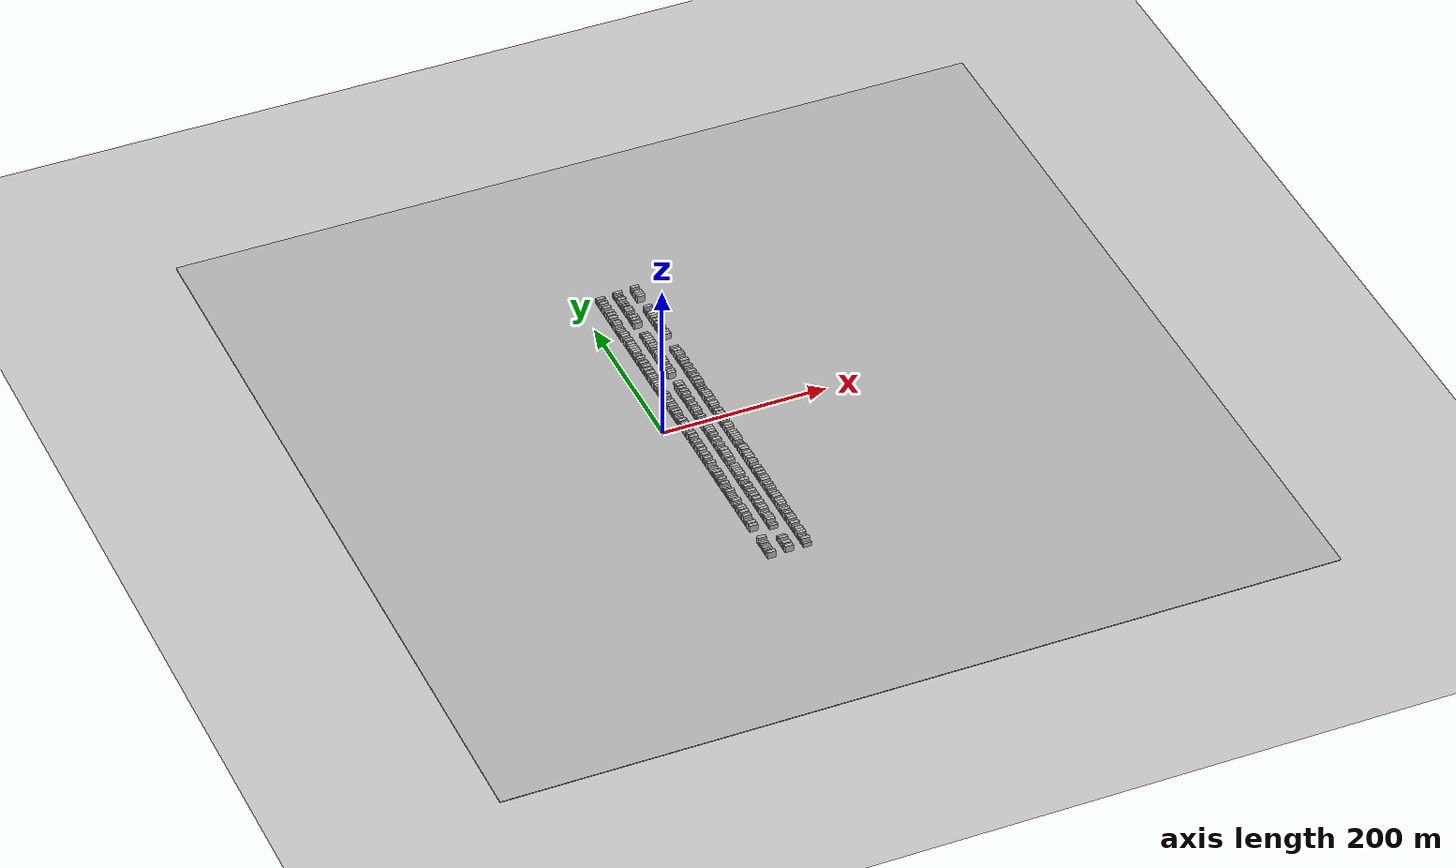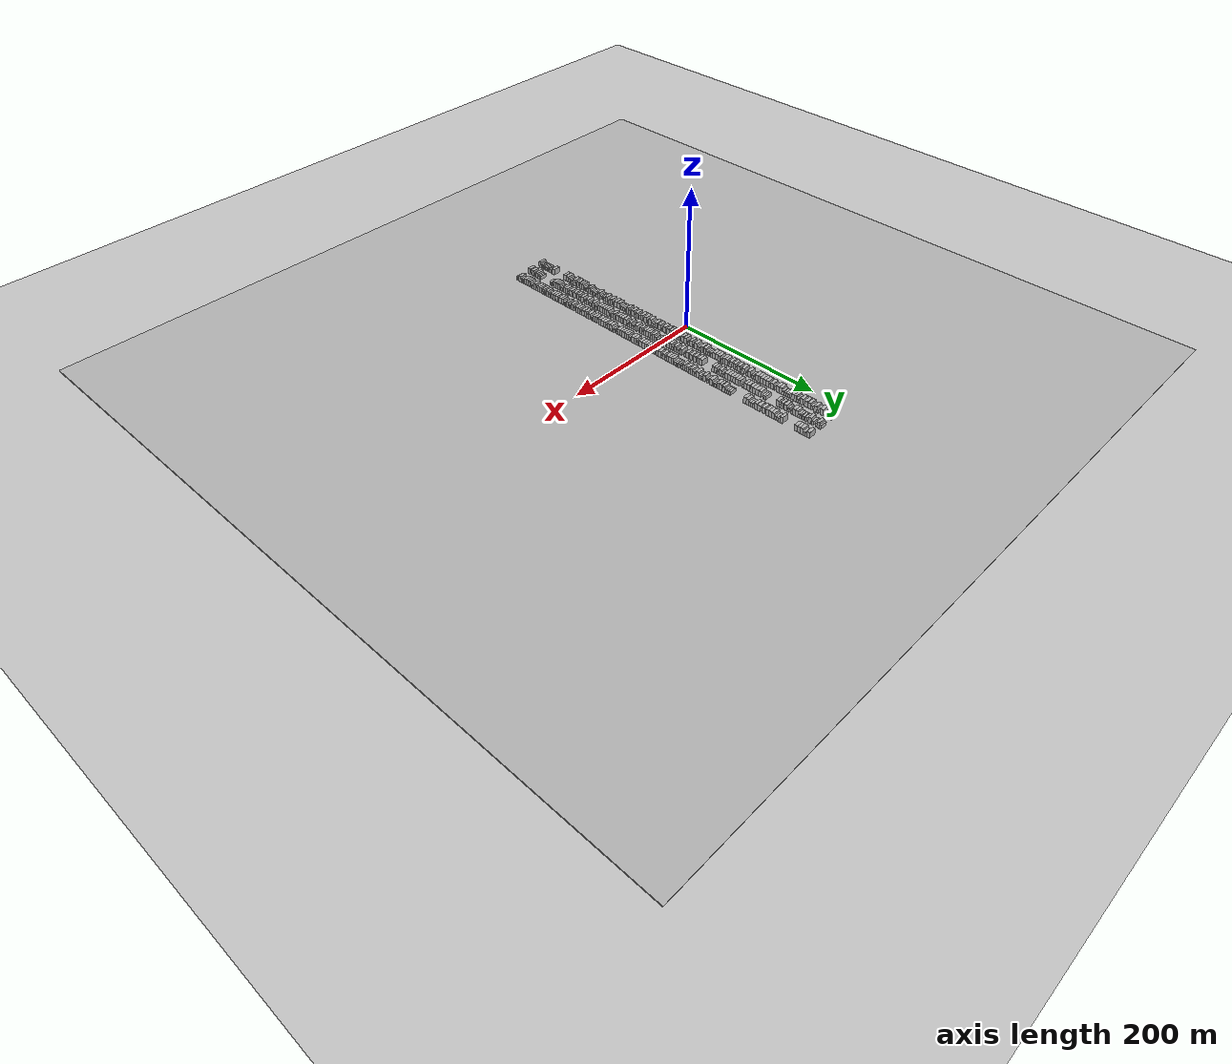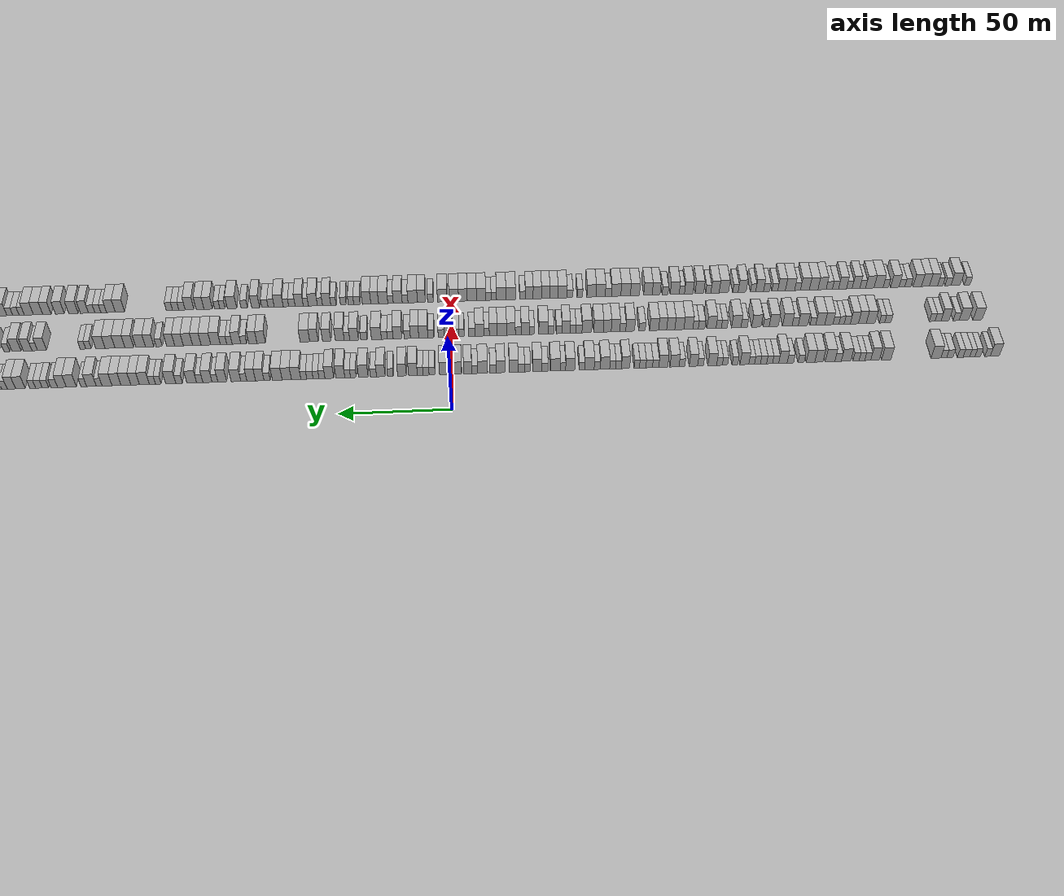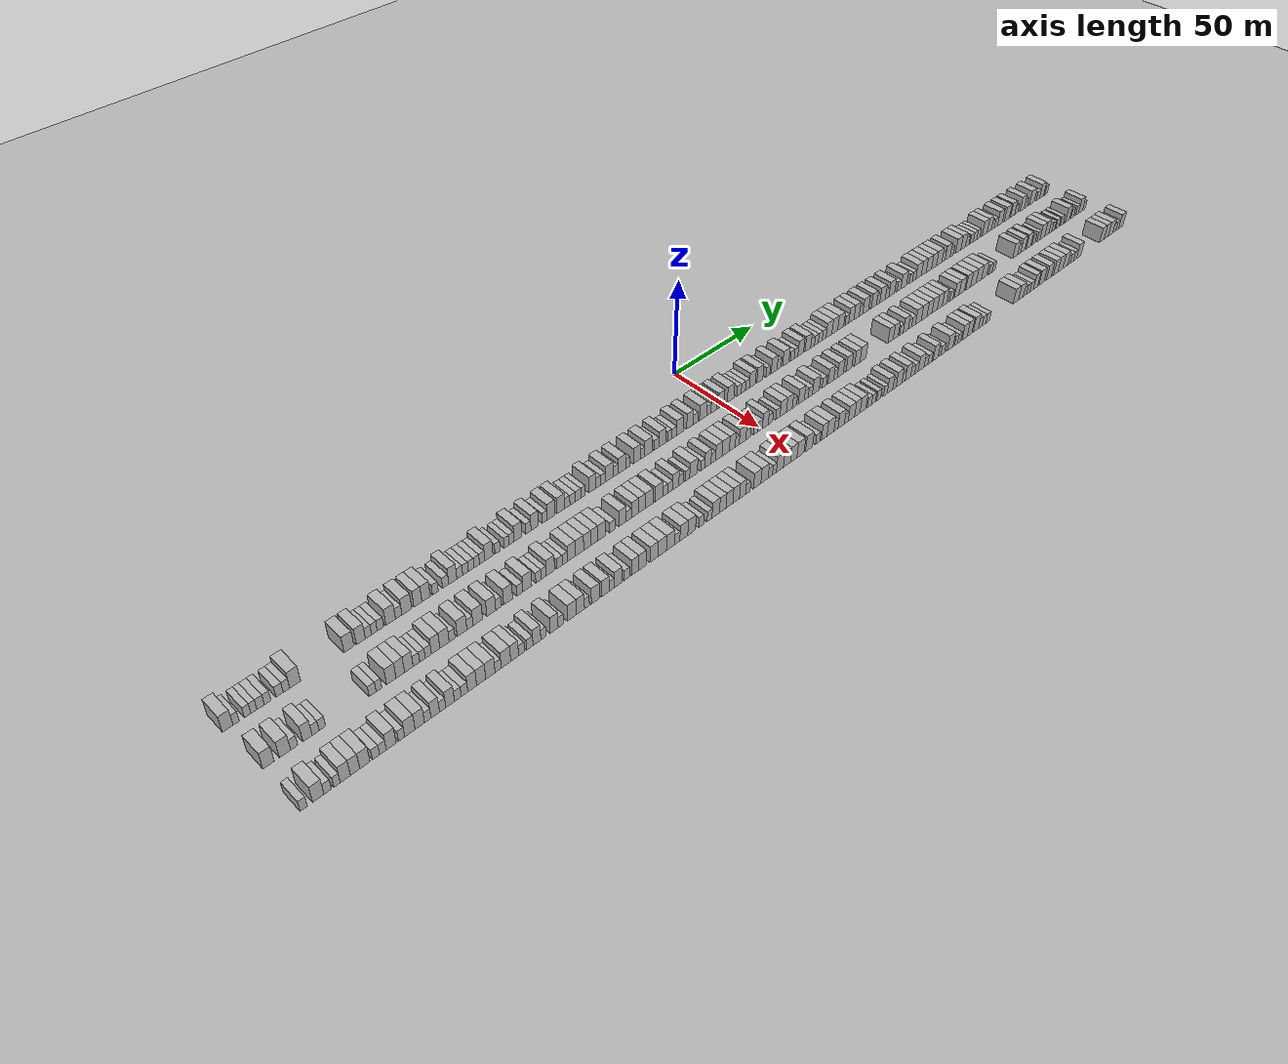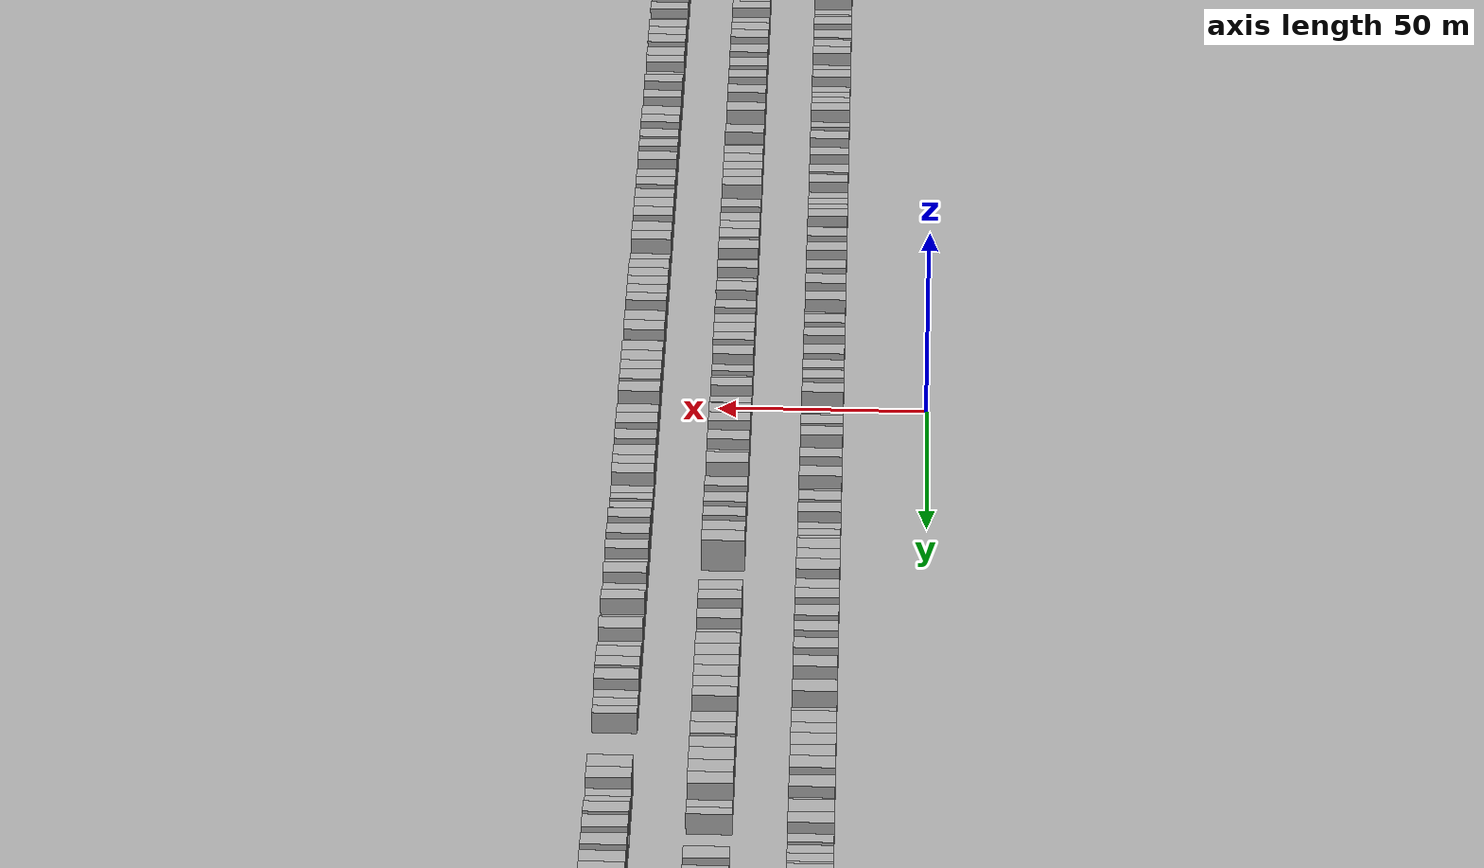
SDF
<?xml version="1.0" encoding="utf-8"?>

<sdf version="1.6">

   <world name="default">

      <gui fullscreen="0">

         <camera name="user_camera">

            <pose>-15 0 4.57585 0 0 0</pose>

            <view_controller>orbit</view_controller>

         </camera>

      </gui>

      <scene>

         <sky>

           <clouds>

             <speed>12</speed>

           </clouds>

         </sky>

         <ambient>0.4 0.4 0.4 1</ambient>

         <background>0.7 0.7 0.7 1</background>

         <shadows>1</shadows>

      </scene>

      <gravity>0 0 -9.8066</gravity>

      <magnetic_field>6e-06 2.3e-05 -4.2e-05</magnetic_field>

      <physics default="0" name="default_physics" type="ode">

         <ode>

            <solver>

               <type>quick</type>

               <iters>10</iters>

               <sor>1.0</sor>

               <use_dynamic_moi_rescaling>0</use_dynamic_moi_rescaling>

            </solver>

            <constraints>

               <cfm>0</cfm>

               <erp>0.2</erp>

               <contact_max_correcting_vel>100</contact_max_correcting_vel>

               <contact_surface_layer>0.001</contact_surface_layer>

            </constraints>

         </ode>

         <max_step_size>0.004</max_step_size>

         <real_time_factor>1</real_time_factor>

         <real_time_update_rate>250</real_time_update_rate>

      </physics>

      <light name="sun" type="directional">

         <cast_shadows>1</cast_shadows>

         <pose>0 0 10 0 0 0</pose>

         <diffuse>0.8 0.8 0.8 1</diffuse>

         <specular>0.2 0.2 0.2 1</specular>

         <attenuation>

            <range>1000</range>

            <constant>0.9</constant>

            <linear>0.01</linear>

            <quadratic>0.001</quadratic>

         </attenuation>

         <direction>-0.5 0.1 -0.9</direction>

      </light>

      <include>

         <name>ground_plane_1</name>

         <uri>model://HANNAS_ground_plane</uri>

         <pose>0 0 0  0 0 0</pose>

      </include>

      <include>

         <name>ground_plane_2</name>

         <uri>model://HANNAS_ground_plane</uri>

         <pose>100 0 0  0 0 0</pose>

      </include>

      <model name="building_1">

         <static>1</static>

         <pose frame="">25.0000 -245.9223 0 0.000000 0.000000 0.000000</pose>

         <link name="link">

            <pose frame="">0 0 4.50 0 0 0</pose>

            <collision name="collision">

               <geometry>

                  <box>

                     <size>10.0000 4.1554 9.0000</size>

                  </box>

               </geometry>

               <max_contacts>10</max_contacts>

               <surface>

                  <contact>

                     <ode/>

                  </contact>

                  <bounce/>

                  <friction>

                     <torsional>

                        <ode/>

                     </torsional>

                     <ode/>

                  </friction>

               </surface>

            </collision>

            <visual name="visual">

               <cast_shadows>0</cast_shadows>

               <geometry>

                  <box>

                     <size>10.0000 4.1554 9.0000</size>

                  </box>

               </geometry>

               <material>

                  <script>

                     <uri>model://HANNAS_wall/materials/scripts</uri>

                     <uri>model://HANNAS_wall/materials/textures</uri>

                     <name>vrc/HANNAS_wall</name>

                  </script>

               </material>

            </visual>

            <self_collide>0</self_collide>

            <enable_wind>0</enable_wind>

            <kinematic>0</kinematic>

         </link>

      </model>

      <model name="building_2">

         <static>1</static>

         <pose frame="">25.0000 -242.6191 0 0.000000 0.000000 0.000000</pose>

         <link name="link">

            <pose frame="">0 0 3.00 0 0 0</pose>

            <collision name="collision">

               <geometry>

                  <box>

                     <size>10.0000 2.4510 6.0000</size>

                  </box>

               </geometry>

               <max_contacts>10</max_contacts>

               <surface>

                  <contact>

                     <ode/>

                  </contact>

                  <bounce/>

                  <friction>

                     <torsional>

                        <ode/>

                     </torsional>

                     <ode/>

                  </friction>

               </surface>

            </collision>

            <visual name="visual">

               <cast_shadows>0</cast_shadows>

               <geometry>

                  <box>

                     <size>10.0000 2.4510 6.0000</size>

                  </box>

               </geometry>

               <material>

                  <script>

                     <uri>model://HANNAS_wall/materials/scripts</uri>

                     <uri>model://HANNAS_wall/materials/textures</uri>

                     <name>vrc/HANNAS_wall</name>

                  </script>

               </material>

            </visual>

            <self_collide>0</self_collide>

            <enable_wind>0</enable_wind>

            <kinematic>0</kinematic>

         </link>

      </model>

      <model name="building_3">

         <static>1</static>

         <pose frame="">25.0000 -238.1239 0 0.000000 0.000000 0.000000</pose>

         <link name="link">

            <pose frame="">0 0 3.00 0 0 0</pose>

            <collision name="collision">

               <geometry>

                  <box>

                     <size>10.0000 2.5395 6.0000</size>

                  </box>

               </geometry>

               <max_contacts>10</max_contacts>

               <surface>

                  <contact>

                     <ode/>

                  </contact>

                  <bounce/>

                  <friction>

                     <torsional>

                        <ode/>

                     </torsional>

                     <ode/>

                  </friction>

               </surface>

            </collision>

            <visual name="visual">

               <cast_shadows>0</cast_shadows>

               <geometry>

                  <box>

                     <size>10.0000 2.5395 6.0000</size>

                  </box>

               </geometry>

               <material>

                  <script>

                     <uri>model://HANNAS_wall/materials/scripts</uri>

                     <uri>model://HANNAS_wall/materials/textures</uri>

                     <name>vrc/HANNAS_wall</name>

                  </script>

               </material>

            </visual>

            <self_collide>0</self_collide>

            <enable_wind>0</enable_wind>

            <kinematic>0</kinematic>

         </link>

      </model>

      <model name="building_4">

         <static>1</static>

         <pose frame="">25.0000 -235.6540 0 0.000000 0.000000 0.000000</pose>

         <link name="link">

            <pose frame="">0 0 3.00 0 0 0</pose>

            <collision name="collision">

               <geometry>

                  <box>

                     <size>10.0000 2.4002 6.0000</size>

                  </box>

               </geometry>

               <max_contacts>10</max_contacts>

               <surface>

                  <contact>

                     <ode/>

                  </contact>

                  <bounce/>

                  <friction>

                     <torsional>

                        <ode/>

                     </torsional>

                     <ode/>

                  </friction>

               </surface>

            </collision>

            <visual name="visual">

               <cast_shadows>0</cast_shadows>

               <geometry>

                  <box>

                     <size>10.0000 2.4002 6.0000</size>

                  </box>

               </geometry>

               <material>

                  <script>

                     <uri>model://HANNAS_wall/materials/scripts</uri>

                     <uri>model://HANNAS_wall/materials/textures</uri>

                     <name>vrc/HANNAS_wall</name>

                  </script>

               </material>

            </visual>

            <self_collide>0</self_collide>

            <enable_wind>0</enable_wind>

            <kinematic>0</kinematic>

         </link>

      </model>

      <model name="building_5">

         <static>1</static>

         <pose frame="">25.0000 -232.9622 0 0.000000 0.000000 0.000000</pose>

         <link name="link">

            <pose frame="">0 0 3.00 0 0 0</pose>

            <collision name="collision">

               <geometry>

                  <box>

                     <size>10.0000 2.9835 6.0000</size>

                  </box>

               </geometry>

               <max_contacts>10</max_contacts>

               <surface>

                  <contact>

                     <ode/>

                  </contact>

                  <bounce/>

                  <friction>

                     <torsional>

                        <ode/>

                     </torsional>

                     <ode/>

                  </friction>

               </surface>

            </collision>

            <visual name="visual">

               <cast_shadows>0</cast_shadows>

               <geometry>

                  <box>

                     <size>10.0000 2.9835 6.0000</size>

                  </box>

               </geometry>

               <material>

                  <script>

                     <uri>model://HANNAS_wall/materials/scripts</uri>

                     <uri>model://HANNAS_wall/materials/textures</uri>

                     <name>vrc/HANNAS_wall</name>

                  </script>

               </material>

            </visual>

            <self_collide>0</self_collide>

            <enable_wind>0</enable_wind>

            <kinematic>0</kinematic>

         </link>

      </model>

      <model name="building_6">

         <static>1</static>

         <pose frame="">25.0000 -230.1509 0 0.000000 0.000000 0.000000</pose>

         <link name="link">

            <pose frame="">0 0 3.00 0 0 0</pose>

            <collision name="collision">

               <geometry>

                  <box>

                     <size>10.0000 2.6391 6.0000</size>

                  </box>

               </geometry>

               <max_contacts>10</max_contacts>

               <surface>

                  <contact>

                     <ode/>

                  </contact>

                  <bounce/>

                  <friction>

                     <torsional>

                        <ode/>

                     </torsional>

                     <ode/>

                  </friction>

               </surface>

            </collision>

            <visual name="visual">

               <cast_shadows>0</cast_shadows>

               <geometry>

                  <box>

                     <size>10.0000 2.6391 6.0000</size>

                  </box>

               </geometry>

               <material>

                  <script>

                     <uri>model://HANNAS_wall/materials/scripts</uri>

                     <uri>model://HANNAS_wall/materials/textures</uri>

                     <name>vrc/HANNAS_wall</name>

                  </script>

               </material>

            </visual>

            <self_collide>0</self_collide>

            <enable_wind>0</enable_wind>

            <kinematic>0</kinematic>

         </link>

      </model>

      <model name="building_7">

         <static>1</static>

         <pose frame="">25.0000 -225.3580 0 0.000000 0.000000 0.000000</pose>

         <link name="link">

            <pose frame="">0 0 3.00 0 0 0</pose>

            <collision name="collision">

               <geometry>

                  <box>

                     <size>10.0000 2.9467 6.0000</size>

                  </box>

               </geometry>

               <max_contacts>10</max_contacts>

               <surface>

                  <contact>

                     <ode/>

                  </contact>

                  <bounce/>

                  <friction>

                     <torsional>

                        <ode/>

                     </torsional>

                     <ode/>

                  </friction>

               </surface>

            </collision>

            <visual name="visual">

               <cast_shadows>0</cast_shadows>

               <geometry>

                  <box>

                     <size>10.0000 2.9467 6.0000</size>

                  </box>

               </geometry>

               <material>

                  <script>

                     <uri>model://HANNAS_wall/materials/scripts</uri>

                     <uri>model://HANNAS_wall/materials/textures</uri>

                     <name>vrc/HANNAS_wall</name>

                  </script>

               </material>

            </visual>

            <self_collide>0</self_collide>

            <enable_wind>0</enable_wind>

            <kinematic>0</kinematic>

         </link>

      </model>

      <model name="building_8">

         <static>1</static>

         <pose frame="">25.0000 -222.5664 0 0.000000 0.000000 0.000000</pose>

         <link name="link">

            <pose frame="">0 0 3.00 0 0 0</pose>

            <collision name="collision">

               <geometry>

                  <box>

                     <size>10.0000 2.6365 6.0000</size>

                  </box>

               </geometry>

               <max_contacts>10</max_contacts>

               <surface>

                  <contact>

                     <ode/>

                  </contact>

                  <bounce/>

                  <friction>

                     <torsional>

                        <ode/>

                     </torsional>

                     <ode/>

                  </friction>

               </surface>

            </collision>

            <visual name="visual">

               <cast_shadows>0</cast_shadows>

               <geometry>

                  <box>

                     <size>10.0000 2.6365 6.0000</size>

                  </box>

               </geometry>

               <material>

                  <script>

                     <uri>model://HANNAS_wall/materials/scripts</uri>

                     <uri>model://HANNAS_wall/materials/textures</uri>

                     <name>vrc/HANNAS_wall</name>

                  </script>

               </material>

            </visual>

            <self_collide>0</self_collide>

            <enable_wind>0</enable_wind>

            <kinematic>0</kinematic>

         </link>

      </model>

      <model name="building_9">

         <static>1</static>

         <pose frame="">25.0000 -219.0022 0 0.000000 0.000000 0.000000</pose>

         <link name="link">

            <pose frame="">0 0 4.50 0 0 0</pose>

            <collision name="collision">

               <geometry>

                  <box>

                     <size>10.0000 4.4920 9.0000</size>

                  </box>

               </geometry>

               <max_contacts>10</max_contacts>

               <surface>

                  <contact>

                     <ode/>

                  </contact>

                  <bounce/>

                  <friction>

                     <torsional>

                        <ode/>

                     </torsional>

                     <ode/>

                  </friction>

               </surface>

            </collision>

            <visual name="visual">

               <cast_shadows>0</cast_shadows>

               <geometry>

                  <box>

                     <size>10.0000 4.4920 9.0000</size>

                  </box>

               </geometry>

               <material>

                  <script>

                     <uri>model://HANNAS_wall/materials/scripts</uri>

                     <uri>model://HANNAS_wall/materials/textures</uri>

                     <name>vrc/HANNAS_wall</name>

                  </script>

               </material>

            </visual>

            <self_collide>0</self_collide>

            <enable_wind>0</enable_wind>

            <kinematic>0</kinematic>

         </link>

      </model>

      <model name="building_10">

         <static>1</static>

         <pose frame="">25.0000 -196.2850 0 0.000000 0.000000 0.000000</pose>

         <link name="link">

            <pose frame="">0 0 4.50 0 0 0</pose>

            <collision name="collision">

               <geometry>

                  <box>

                     <size>10.0000 4.3141 9.0000</size>

                  </box>

               </geometry>

               <max_contacts>10</max_contacts>

               <surface>

                  <contact>

                     <ode/>

                  </contact>

                  <bounce/>

                  <friction>

                     <torsional>

                        <ode/>

                     </torsional>

                     <ode/>

                  </friction>

               </surface>

            </collision>

            <visual name="visual">

               <cast_shadows>0</cast_shadows>

               <geometry>

                  <box>

                     <size>10.0000 4.3141 9.0000</size>

                  </box>

               </geometry>

               <material>

                  <script>

                     <uri>model://HANNAS_wall/materials/scripts</uri>

                     <uri>model://HANNAS_wall/materials/textures</uri>

                     <name>vrc/HANNAS_wall</name>

                  </script>

               </material>

            </visual>

            <self_collide>0</self_collide>

            <enable_wind>0</enable_wind>

            <kinematic>0</kinematic>

         </link>

      </model>

      <model name="building_11">

         <static>1</static>

         <pose frame="">25.0000 -191.1625 0 0.000000 0.000000 0.000000</pose>

         <link name="link">

            <pose frame="">0 0 4.50 0 0 0</pose>

            <collision name="collision">

               <geometry>

                  <box>

                     <size>10.0000 3.9308 9.0000</size>

                  </box>

               </geometry>

               <max_contacts>10</max_contacts>

               <surface>

                  <contact>

                     <ode/>

                  </contact>

                  <bounce/>

                  <friction>

                     <torsional>

                        <ode/>

                     </torsional>

                     <ode/>

                  </friction>

               </surface>

            </collision>

            <visual name="visual">

               <cast_shadows>0</cast_shadows>

               <geometry>

                  <box>

                     <size>10.0000 3.9308 9.0000</size>

                  </box>

               </geometry>

               <material>

                  <script>

                     <uri>model://HANNAS_wall/materials/scripts</uri>

                     <uri>model://HANNAS_wall/materials/textures</uri>

                     <name>vrc/HANNAS_wall</name>

                  </script>

               </material>

            </visual>

            <self_collide>0</self_collide>

            <enable_wind>0</enable_wind>

            <kinematic>0</kinematic>

         </link>

      </model>

      <model name="building_12">

         <static>1</static>

         <pose frame="">25.0000 -187.8236 0 0.000000 0.000000 0.000000</pose>

         <link name="link">

            <pose frame="">0 0 3.00 0 0 0</pose>

            <collision name="collision">

               <geometry>

                  <box>

                     <size>10.0000 2.7469 6.0000</size>

                  </box>

               </geometry>

               <max_contacts>10</max_contacts>

               <surface>

                  <contact>

                     <ode/>

                  </contact>

                  <bounce/>

                  <friction>

                     <torsional>

                        <ode/>

                     </torsional>

                     <ode/>

                  </friction>

               </surface>

            </collision>

            <visual name="visual">

               <cast_shadows>0</cast_shadows>

               <geometry>

                  <box>

                     <size>10.0000 2.7469 6.0000</size>

                  </box>

               </geometry>

               <material>

                  <script>

                     <uri>model://HANNAS_wall/materials/scripts</uri>

                     <uri>model://HANNAS_wall/materials/textures</uri>

                     <name>vrc/HANNAS_wall</name>

                  </script>

               </material>

            </visual>

            <self_collide>0</self_collide>

            <enable_wind>0</enable_wind>

            <kinematic>0</kinematic>

         </link>

      </model>

      <model name="building_13">

         <static>1</static>

         <pose frame="">25.0000 -185.1862 0 0.000000 0.000000 0.000000</pose>

         <link name="link">

            <pose frame="">0 0 3.00 0 0 0</pose>

            <collision name="collision">

               <geometry>

                  <box>

                     <size>10.0000 2.5279 6.0000</size>

                  </box>

               </geometry>

               <max_contacts>10</max_contacts>

               <surface>

                  <contact>

                     <ode/>

                  </contact>

                  <bounce/>

                  <friction>

                     <torsional>

                        <ode/>

                     </torsional>

                     <ode/>

                  </friction>

               </surface>

            </collision>

            <visual name="visual">

               <cast_shadows>0</cast_shadows>

               <geometry>

                  <box>

                     <size>10.0000 2.5279 6.0000</size>

                  </box>

               </geometry>

               <material>

                  <script>

                     <uri>model://HANNAS_wall/materials/scripts</uri>

                     <uri>model://HANNAS_wall/materials/textures</uri>

                     <name>vrc/HANNAS_wall</name>

                  </script>

               </material>

            </visual>

            <self_collide>0</self_collide>

            <enable_wind>0</enable_wind>

            <kinematic>0</kinematic>

         </link>

      </model>

      <model name="building_14">

         <static>1</static>

         <pose frame="">25.0000 -182.5068 0 0.000000 0.000000 0.000000</pose>

         <link name="link">

            <pose frame="">0 0 3.00 0 0 0</pose>

            <collision name="collision">

               <geometry>

                  <box>

                     <size>10.0000 2.8309 6.0000</size>

                  </box>

               </geometry>

               <max_contacts>10</max_contacts>

               <surface>

                  <contact>

                     <ode/>

                  </contact>

                  <bounce/>

                  <friction>

                     <torsional>

                        <ode/>

                     </torsional>

                     <ode/>

                  </friction>

               </surface>

            </collision>

            <visual name="visual">

               <cast_shadows>0</cast_shadows>

               <geometry>

                  <box>

                     <size>10.0000 2.8309 6.0000</size>

                  </box>

               </geometry>

               <material>

                  <script>

                     <uri>model://HANNAS_wall/materials/scripts</uri>

                     <uri>model://HANNAS_wall/materials/textures</uri>

                     <name>vrc/HANNAS_wall</name>

                  </script>

               </material>

            </visual>

            <self_collide>0</self_collide>

            <enable_wind>0</enable_wind>

            <kinematic>0</kinematic>

         </link>

      </model>

      <model name="building_15">

         <static>1</static>

         <pose frame="">25.0000 -177.9419 0 0.000000 0.000000 0.000000</pose>

         <link name="link">

            <pose frame="">0 0 4.50 0 0 0</pose>

            <collision name="collision">

               <geometry>

                  <box>

                     <size>10.0000 4.2990 9.0000</size>

                  </box>

               </geometry>

               <max_contacts>10</max_contacts>

               <surface>

                  <contact>

                     <ode/>

                  </contact>

                  <bounce/>

                  <friction>

                     <torsional>

                        <ode/>

                     </torsional>

                     <ode/>

                  </friction>

               </surface>

            </collision>

            <visual name="visual">

               <cast_shadows>0</cast_shadows>

               <geometry>

                  <box>

                     <size>10.0000 4.2990 9.0000</size>

                  </box>

               </geometry>

               <material>

                  <script>

                     <uri>model://HANNAS_wall/materials/scripts</uri>

                     <uri>model://HANNAS_wall/materials/textures</uri>

                     <name>vrc/HANNAS_wall</name>

                  </script>

               </material>

            </visual>

            <self_collide>0</self_collide>

            <enable_wind>0</enable_wind>

            <kinematic>0</kinematic>

         </link>

      </model>

      <model name="building_16">

         <static>1</static>

         <pose frame="">25.0000 -174.3163 0 0.000000 0.000000 0.000000</pose>

         <link name="link">

            <pose frame="">0 0 3.00 0 0 0</pose>

            <collision name="collision">

               <geometry>

                  <box>

                     <size>10.0000 2.9522 6.0000</size>

                  </box>

               </geometry>

               <max_contacts>10</max_contacts>

               <surface>

                  <contact>

                     <ode/>

                  </contact>

                  <bounce/>

                  <friction>

                     <torsional>

                        <ode/>

                     </torsional>

                     <ode/>

                  </friction>

               </surface>

            </collision>

            <visual name="visual">

               <cast_shadows>0</cast_shadows>

               <geometry>

                  <box>

                     <size>10.0000 2.9522 6.0000</size>

                  </box>

               </geometry>

               <material>

                  <script>

                     <uri>model://HANNAS_wall/materials/scripts</uri>

                     <uri>model://HANNAS_wall/materials/textures</uri>

                     <name>vrc/HANNAS_wall</name>

                  </script>

               </material>

            </visual>

            <self_collide>0</self_collide>

            <enable_wind>0</enable_wind>

            <kinematic>0</kinematic>

         </link>

      </model>

      <model name="building_17">

         <static>1</static>

         <pose frame="">25.0000 -170.6362 0 0.000000 0.000000 0.000000</pose>

         <link name="link">

            <pose frame="">0 0 4.50 0 0 0</pose>

            <collision name="collision">

               <geometry>

                  <box>

                     <size>10.0000 4.4079 9.0000</size>

                  </box>

               </geometry>

               <max_contacts>10</max_contacts>

               <surface>

                  <contact>

                     <ode/>

                  </contact>

                  <bounce/>

                  <friction>

                     <torsional>

                        <ode/>

                     </torsional>

                     <ode/>

                  </friction>

               </surface>

            </collision>

            <visual name="visual">

               <cast_shadows>0</cast_shadows>

               <geometry>

                  <box>

                     <size>10.0000 4.4079 9.0000</size>

                  </box>

               </geometry>

               <material>

                  <script>

                     <uri>model://HANNAS_wall/materials/scripts</uri>

                     <uri>model://HANNAS_wall/materials/textures</uri>

                     <name>vrc/HANNAS_wall</name>

                  </script>

               </material>

            </visual>

            <self_collide>0</self_collide>

            <enable_wind>0</enable_wind>

            <kinematic>0</kinematic>

         </link>

      </model>

      <model name="building_18">

         <static>1</static>

         <pose frame="">25.0000 -165.5775 0 0.000000 0.000000 0.000000</pose>

         <link name="link">

            <pose frame="">0 0 4.50 0 0 0</pose>

            <collision name="collision">

               <geometry>

                  <box>

                     <size>10.0000 3.7096 9.0000</size>

                  </box>

               </geometry>

               <max_contacts>10</max_contacts>

               <surface>

                  <contact>

                     <ode/>

                  </contact>

                  <bounce/>

                  <friction>

                     <torsional>

                        <ode/>

                     </torsional>

                     <ode/>

                  </friction>

               </surface>

            </collision>

            <visual name="visual">

               <cast_shadows>0</cast_shadows>

               <geometry>

                  <box>

                     <size>10.0000 3.7096 9.0000</size>

                  </box>

               </geometry>

               <material>

                  <script>

                     <uri>model://HANNAS_wall/materials/scripts</uri>

                     <uri>model://HANNAS_wall/materials/textures</uri>

                     <name>vrc/HANNAS_wall</name>

                  </script>

               </material>

            </visual>

            <self_collide>0</self_collide>

            <enable_wind>0</enable_wind>

            <kinematic>0</kinematic>

         </link>

      </model>

      <model name="building_19">

         <static>1</static>

         <pose frame="">25.0000 -161.7763 0 0.000000 0.000000 0.000000</pose>

         <link name="link">

            <pose frame="">0 0 4.50 0 0 0</pose>

            <collision name="collision">

               <geometry>

                  <box>

                     <size>10.0000 3.8926 9.0000</size>

                  </box>

               </geometry>

               <max_contacts>10</max_contacts>

               <surface>

                  <contact>

                     <ode/>

                  </contact>

                  <bounce/>

                  <friction>

                     <torsional>

                        <ode/>

                     </torsional>

                     <ode/>

                  </friction>

               </surface>

            </collision>

            <visual name="visual">

               <cast_shadows>0</cast_shadows>

               <geometry>

                  <box>

                     <size>10.0000 3.8926 9.0000</size>

                  </box>

               </geometry>

               <material>

                  <script>

                     <uri>model://HANNAS_wall/materials/scripts</uri>

                     <uri>model://HANNAS_wall/materials/textures</uri>

                     <name>vrc/HANNAS_wall</name>

                  </script>

               </material>

            </visual>

            <self_collide>0</self_collide>

            <enable_wind>0</enable_wind>

            <kinematic>0</kinematic>

         </link>

      </model>

      <model name="building_20">

         <static>1</static>

         <pose frame="">25.0000 -157.4546 0 0.000000 0.000000 0.000000</pose>

         <link name="link">

            <pose frame="">0 0 3.00 0 0 0</pose>

            <collision name="collision">

               <geometry>

                  <box>

                     <size>10.0000 2.7508 6.0000</size>

                  </box>

               </geometry>

               <max_contacts>10</max_contacts>

               <surface>

                  <contact>

                     <ode/>

                  </contact>

                  <bounce/>

                  <friction>

                     <torsional>

                        <ode/>

                     </torsional>

                     <ode/>

                  </friction>

               </surface>

            </collision>

            <visual name="visual">

               <cast_shadows>0</cast_shadows>

               <geometry>

                  <box>

                     <size>10.0000 2.7508 6.0000</size>

                  </box>

               </geometry>

               <material>

                  <script>

                     <uri>model://HANNAS_wall/materials/scripts</uri>

                     <uri>model://HANNAS_wall/materials/textures</uri>

                     <name>vrc/HANNAS_wall</name>

                  </script>

               </material>

            </visual>

            <self_collide>0</self_collide>

            <enable_wind>0</enable_wind>

            <kinematic>0</kinematic>

         </link>

      </model>

      <model name="building_21">

         <static>1</static>

         <pose frame="">25.0000 -152.6201 0 0.000000 0.000000 0.000000</pose>

         <link name="link">

            <pose frame="">0 0 3.00 0 0 0</pose>

            <collision name="collision">

               <geometry>

                  <box>

                     <size>10.0000 2.9182 6.0000</size>

                  </box>

               </geometry>

               <max_contacts>10</max_contacts>

               <surface>

                  <contact>

                     <ode/>

                  </contact>

                  <bounce/>

                  <friction>

                     <torsional>

                        <ode/>

                     </torsional>

                     <ode/>

                  </friction>

               </surface>

            </collision>

            <visual name="visual">

               <cast_shadows>0</cast_shadows>

               <geometry>

                  <box>

                     <size>10.0000 2.9182 6.0000</size>

                  </box>

               </geometry>

               <material>

                  <script>

                     <uri>model://HANNAS_wall/materials/scripts</uri>

                     <uri>model://HANNAS_wall/materials/textures</uri>

                     <name>vrc/HANNAS_wall</name>

                  </script>

               </material>

            </visual>

            <self_collide>0</self_collide>

            <enable_wind>0</enable_wind>

            <kinematic>0</kinematic>

         </link>

      </model>

      <model name="building_22">

         <static>1</static>

         <pose frame="">25.0000 -149.2348 0 0.000000 0.000000 0.000000</pose>

         <link name="link">

            <pose frame="">0 0 4.50 0 0 0</pose>

            <collision name="collision">

               <geometry>

                  <box>

                     <size>10.0000 3.8524 9.0000</size>

                  </box>

               </geometry>

               <max_contacts>10</max_contacts>

               <surface>

                  <contact>

                     <ode/>

                  </contact>

                  <bounce/>

                  <friction>

                     <torsional>

                        <ode/>

                     </torsional>

                     <ode/>

                  </friction>

               </surface>

            </collision>

            <visual name="visual">

               <cast_shadows>0</cast_shadows>

               <geometry>

                  <box>

                     <size>10.0000 3.8524 9.0000</size>

                  </box>

               </geometry>

               <material>

                  <script>

                     <uri>model://HANNAS_wall/materials/scripts</uri>

                     <uri>model://HANNAS_wall/materials/textures</uri>

                     <name>vrc/HANNAS_wall</name>

                  </script>

               </material>

            </visual>

            <self_collide>0</self_collide>

            <enable_wind>0</enable_wind>

            <kinematic>0</kinematic>

         </link>

      </model>

      <model name="building_23">

         <static>1</static>

         <pose frame="">25.0000 -145.8840 0 0.000000 0.000000 0.000000</pose>

         <link name="link">

            <pose frame="">0 0 3.00 0 0 0</pose>

            <collision name="collision">

               <geometry>

                  <box>

                     <size>10.0000 2.8490 6.0000</size>

                  </box>

               </geometry>

               <max_contacts>10</max_contacts>

               <surface>

                  <contact>

                     <ode/>

                  </contact>

                  <bounce/>

                  <friction>

                     <torsional>

                        <ode/>

                     </torsional>

                     <ode/>

                  </friction>

               </surface>

            </collision>

            <visual name="visual">

               <cast_shadows>0</cast_shadows>

               <geometry>

                  <box>

                     <size>10.0000 2.8490 6.0000</size>

                  </box>

               </geometry>

               <material>

                  <script>

                     <uri>model://HANNAS_wall/materials/scripts</uri>

                     <uri>model://HANNAS_wall/materials/textures</uri>

                     <name>vrc/HANNAS_wall</name>

                  </script>

               </material>

            </visual>

            <self_collide>0</self_collide>

            <enable_wind>0</enable_wind>

            <kinematic>0</kinematic>

         </link>

      </model>

      <model name="building_24">

         <static>1</static>

         <pose frame="">25.0000 -143.1176 0 0.000000 0.000000 0.000000</pose>

         <link name="link">

            <pose frame="">0 0 3.00 0 0 0</pose>

            <collision name="collision">

               <geometry>

                  <box>

                     <size>10.0000 2.6839 6.0000</size>

                  </box>

               </geometry>

               <max_contacts>10</max_contacts>

               <surface>

                  <contact>

                     <ode/>

                  </contact>

                  <bounce/>

                  <friction>

                     <torsional>

                        <ode/>

                     </torsional>

                     <ode/>

                  </friction>

               </surface>

            </collision>

            <visual name="visual">

               <cast_shadows>0</cast_shadows>

               <geometry>

                  <box>

                     <size>10.0000 2.6839 6.0000</size>

                  </box>

               </geometry>

               <material>

                  <script>

                     <uri>model://HANNAS_wall/materials/scripts</uri>

                     <uri>model://HANNAS_wall/materials/textures</uri>

                     <name>vrc/HANNAS_wall</name>

                  </script>

               </material>

            </visual>

            <self_collide>0</self_collide>

            <enable_wind>0</enable_wind>

            <kinematic>0</kinematic>

         </link>

      </model>

      <model name="building_25">

         <static>1</static>

         <pose frame="">25.0000 -140.3789 0 0.000000 0.000000 0.000000</pose>

         <link name="link">

            <pose frame="">0 0 3.00 0 0 0</pose>

            <collision name="collision">

               <geometry>

                  <box>

                     <size>10.0000 2.7935 6.0000</size>

                  </box>

               </geometry>

               <max_contacts>10</max_contacts>

               <surface>

                  <contact>

                     <ode/>

                  </contact>

                  <bounce/>

                  <friction>

                     <torsional>

                        <ode/>

                     </torsional>

                     <ode/>

                  </friction>

               </surface>

            </collision>

            <visual name="visual">

               <cast_shadows>0</cast_shadows>

               <geometry>

                  <box>

                     <size>10.0000 2.7935 6.0000</size>

                  </box>

               </geometry>

               <material>

                  <script>

                     <uri>model://HANNAS_wall/materials/scripts</uri>

                     <uri>model://HANNAS_wall/materials/textures</uri>

                     <name>vrc/HANNAS_wall</name>

                  </script>

               </material>

            </visual>

            <self_collide>0</self_collide>

            <enable_wind>0</enable_wind>

            <kinematic>0</kinematic>

         </link>

      </model>

      <model name="building_26">

         <static>1</static>

         <pose frame="">25.0000 -137.6547 0 0.000000 0.000000 0.000000</pose>

         <link name="link">

            <pose frame="">0 0 3.00 0 0 0</pose>

            <collision name="collision">

               <geometry>

                  <box>

                     <size>10.0000 2.6549 6.0000</size>

                  </box>

               </geometry>

               <max_contacts>10</max_contacts>

               <surface>

                  <contact>

                     <ode/>

                  </contact>

                  <bounce/>

                  <friction>

                     <torsional>

                        <ode/>

                     </torsional>

                     <ode/>

                  </friction>

               </surface>

            </collision>

            <visual name="visual">

               <cast_shadows>0</cast_shadows>

               <geometry>

                  <box>

                     <size>10.0000 2.6549 6.0000</size>

                  </box>

               </geometry>

               <material>

                  <script>

                     <uri>model://HANNAS_wall/materials/scripts</uri>

                     <uri>model://HANNAS_wall/materials/textures</uri>

                     <name>vrc/HANNAS_wall</name>

                  </script>

               </material>

            </visual>

            <self_collide>0</self_collide>

            <enable_wind>0</enable_wind>

            <kinematic>0</kinematic>

         </link>

      </model>

      <model name="building_27">

         <static>1</static>

         <pose frame="">25.0000 -135.0209 0 0.000000 0.000000 0.000000</pose>

         <link name="link">

            <pose frame="">0 0 3.00 0 0 0</pose>

            <collision name="collision">

               <geometry>

                  <box>

                     <size>10.0000 2.6126 6.0000</size>

                  </box>

               </geometry>

               <max_contacts>10</max_contacts>

               <surface>

                  <contact>

                     <ode/>

                  </contact>

                  <bounce/>

                  <friction>

                     <torsional>

                        <ode/>

                     </torsional>

                     <ode/>

                  </friction>

               </surface>

            </collision>

            <visual name="visual">

               <cast_shadows>0</cast_shadows>

               <geometry>

                  <box>

                     <size>10.0000 2.6126 6.0000</size>

                  </box>

               </geometry>

               <material>

                  <script>

                     <uri>model://HANNAS_wall/materials/scripts</uri>

                     <uri>model://HANNAS_wall/materials/textures</uri>

                     <name>vrc/HANNAS_wall</name>

                  </script>

               </material>

            </visual>

            <self_collide>0</self_collide>

            <enable_wind>0</enable_wind>

            <kinematic>0</kinematic>

         </link>

      </model>

      <model name="building_28">

         <static>1</static>

         <pose frame="">25.0000 -131.7143 0 0.000000 0.000000 0.000000</pose>

         <link name="link">

            <pose frame="">0 0 4.50 0 0 0</pose>

            <collision name="collision">

               <geometry>

                  <box>

                     <size>10.0000 4.0006 9.0000</size>

                  </box>

               </geometry>

               <max_contacts>10</max_contacts>

               <surface>

                  <contact>

                     <ode/>

                  </contact>

                  <bounce/>

                  <friction>

                     <torsional>

                        <ode/>

                     </torsional>

                     <ode/>

                  </friction>

               </surface>

            </collision>

            <visual name="visual">

               <cast_shadows>0</cast_shadows>

               <geometry>

                  <box>

                     <size>10.0000 4.0006 9.0000</size>

                  </box>

               </geometry>

               <material>

                  <script>

                     <uri>model://HANNAS_wall/materials/scripts</uri>

                     <uri>model://HANNAS_wall/materials/textures</uri>

                     <name>vrc/HANNAS_wall</name>

                  </script>

               </material>

            </visual>

            <self_collide>0</self_collide>

            <enable_wind>0</enable_wind>

            <kinematic>0</kinematic>

         </link>

      </model>

      <model name="building_29">

         <static>1</static>

         <pose frame="">25.0000 -127.4159 0 0.000000 0.000000 0.000000</pose>

         <link name="link">

            <pose frame="">0 0 3.00 0 0 0</pose>

            <collision name="collision">

               <geometry>

                  <box>

                     <size>10.0000 2.5962 6.0000</size>

                  </box>

               </geometry>

               <max_contacts>10</max_contacts>

               <surface>

                  <contact>

                     <ode/>

                  </contact>

                  <bounce/>

                  <friction>

                     <torsional>

                        <ode/>

                     </torsional>

                     <ode/>

                  </friction>

               </surface>

            </collision>

            <visual name="visual">

               <cast_shadows>0</cast_shadows>

               <geometry>

                  <box>

                     <size>10.0000 2.5962 6.0000</size>

                  </box>

               </geometry>

               <material>

                  <script>

                     <uri>model://HANNAS_wall/materials/scripts</uri>

                     <uri>model://HANNAS_wall/materials/textures</uri>

                     <name>vrc/HANNAS_wall</name>

                  </script>

               </material>

            </visual>

            <self_collide>0</self_collide>

            <enable_wind>0</enable_wind>

            <kinematic>0</kinematic>

         </link>

      </model>

      <model name="building_30">

         <static>1</static>

         <pose frame="">25.0000 -122.9150 0 0.000000 0.000000 0.000000</pose>

         <link name="link">

            <pose frame="">0 0 3.00 0 0 0</pose>

            <collision name="collision">

               <geometry>

                  <box>

                     <size>10.0000 2.4056 6.0000</size>

                  </box>

               </geometry>

               <max_contacts>10</max_contacts>

               <surface>

                  <contact>

                     <ode/>

                  </contact>

                  <bounce/>

                  <friction>

                     <torsional>

                        <ode/>

                     </torsional>

                     <ode/>

                  </friction>

               </surface>

            </collision>

            <visual name="visual">

               <cast_shadows>0</cast_shadows>

               <geometry>

                  <box>

                     <size>10.0000 2.4056 6.0000</size>

                  </box>

               </geometry>

               <material>

                  <script>

                     <uri>model://HANNAS_wall/materials/scripts</uri>

                     <uri>model://HANNAS_wall/materials/textures</uri>

                     <name>vrc/HANNAS_wall</name>

                  </script>

               </material>

            </visual>

            <self_collide>0</self_collide>

            <enable_wind>0</enable_wind>

            <kinematic>0</kinematic>

         </link>

      </model>

      <model name="building_31">

         <static>1</static>

         <pose frame="">25.0000 -120.4101 0 0.000000 0.000000 0.000000</pose>

         <link name="link">

            <pose frame="">0 0 3.00 0 0 0</pose>

            <collision name="collision">

               <geometry>

                  <box>

                     <size>10.0000 2.6041 6.0000</size>

                  </box>

               </geometry>

               <max_contacts>10</max_contacts>

               <surface>

                  <contact>

                     <ode/>

                  </contact>

                  <bounce/>

                  <friction>

                     <torsional>

                        <ode/>

                     </torsional>

                     <ode/>

                  </friction>

               </surface>

            </collision>

            <visual name="visual">

               <cast_shadows>0</cast_shadows>

               <geometry>

                  <box>

                     <size>10.0000 2.6041 6.0000</size>

                  </box>

               </geometry>

               <material>

                  <script>

                     <uri>model://HANNAS_wall/materials/scripts</uri>

                     <uri>model://HANNAS_wall/materials/textures</uri>

                     <name>vrc/HANNAS_wall</name>

                  </script>

               </material>

            </visual>

            <self_collide>0</self_collide>

            <enable_wind>0</enable_wind>

            <kinematic>0</kinematic>

         </link>

      </model>

      <model name="building_32">

         <static>1</static>

         <pose frame="">25.0000 -117.1312 0 0.000000 0.000000 0.000000</pose>

         <link name="link">

            <pose frame="">0 0 4.50 0 0 0</pose>

            <collision name="collision">

               <geometry>

                  <box>

                     <size>10.0000 3.9538 9.0000</size>

                  </box>

               </geometry>

               <max_contacts>10</max_contacts>

               <surface>

                  <contact>

                     <ode/>

                  </contact>

                  <bounce/>

                  <friction>

                     <torsional>

                        <ode/>

                     </torsional>

                     <ode/>

                  </friction>

               </surface>

            </collision>

            <visual name="visual">

               <cast_shadows>0</cast_shadows>

               <geometry>

                  <box>

                     <size>10.0000 3.9538 9.0000</size>

                  </box>

               </geometry>

               <material>

                  <script>

                     <uri>model://HANNAS_wall/materials/scripts</uri>

                     <uri>model://HANNAS_wall/materials/textures</uri>

                     <name>vrc/HANNAS_wall</name>

                  </script>

               </material>

            </visual>

            <self_collide>0</self_collide>

            <enable_wind>0</enable_wind>

            <kinematic>0</kinematic>

         </link>

      </model>

      <model name="building_33">

         <static>1</static>

         <pose frame="">25.0000 -111.8211 0 0.000000 0.000000 0.000000</pose>

         <link name="link">

            <pose frame="">0 0 3.00 0 0 0</pose>

            <collision name="collision">

               <geometry>

                  <box>

                     <size>10.0000 2.6663 6.0000</size>

                  </box>

               </geometry>

               <max_contacts>10</max_contacts>

               <surface>

                  <contact>

                     <ode/>

                  </contact>

                  <bounce/>

                  <friction>

                     <torsional>

                        <ode/>

                     </torsional>

                     <ode/>

                  </friction>

               </surface>

            </collision>

            <visual name="visual">

               <cast_shadows>0</cast_shadows>

               <geometry>

                  <box>

                     <size>10.0000 2.6663 6.0000</size>

                  </box>

               </geometry>

               <material>

                  <script>

                     <uri>model://HANNAS_wall/materials/scripts</uri>

                     <uri>model://HANNAS_wall/materials/textures</uri>

                     <name>vrc/HANNAS_wall</name>

                  </script>

               </material>

            </visual>

            <self_collide>0</self_collide>

            <enable_wind>0</enable_wind>

            <kinematic>0</kinematic>

         </link>

      </model>

      <model name="building_34">

         <static>1</static>

         <pose frame="">25.0000 -108.5950 0 0.000000 0.000000 0.000000</pose>

         <link name="link">

            <pose frame="">0 0 4.50 0 0 0</pose>

            <collision name="collision">

               <geometry>

                  <box>

                     <size>10.0000 3.7857 9.0000</size>

                  </box>

               </geometry>

               <max_contacts>10</max_contacts>

               <surface>

                  <contact>

                     <ode/>

                  </contact>

                  <bounce/>

                  <friction>

                     <torsional>

                        <ode/>

                     </torsional>

                     <ode/>

                  </friction>

               </surface>

            </collision>

            <visual name="visual">

               <cast_shadows>0</cast_shadows>

               <geometry>

                  <box>

                     <size>10.0000 3.7857 9.0000</size>

                  </box>

               </geometry>

               <material>

                  <script>

                     <uri>model://HANNAS_wall/materials/scripts</uri>

                     <uri>model://HANNAS_wall/materials/textures</uri>

                     <name>vrc/HANNAS_wall</name>

                  </script>

               </material>

            </visual>

            <self_collide>0</self_collide>

            <enable_wind>0</enable_wind>

            <kinematic>0</kinematic>

         </link>

      </model>

      <model name="building_35">

         <static>1</static>

         <pose frame="">25.0000 -103.3968 0 0.000000 0.000000 0.000000</pose>

         <link name="link">

            <pose frame="">0 0 3.00 0 0 0</pose>

            <collision name="collision">

               <geometry>

                  <box>

                     <size>10.0000 2.6108 6.0000</size>

                  </box>

               </geometry>

               <max_contacts>10</max_contacts>

               <surface>

                  <contact>

                     <ode/>

                  </contact>

                  <bounce/>

                  <friction>

                     <torsional>

                        <ode/>

                     </torsional>

                     <ode/>

                  </friction>

               </surface>

            </collision>

            <visual name="visual">

               <cast_shadows>0</cast_shadows>

               <geometry>

                  <box>

                     <size>10.0000 2.6108 6.0000</size>

                  </box>

               </geometry>

               <material>

                  <script>

                     <uri>model://HANNAS_wall/materials/scripts</uri>

                     <uri>model://HANNAS_wall/materials/textures</uri>

                     <name>vrc/HANNAS_wall</name>

                  </script>

               </material>

            </visual>

            <self_collide>0</self_collide>

            <enable_wind>0</enable_wind>

            <kinematic>0</kinematic>

         </link>

      </model>

      <model name="building_36">

         <static>1</static>

         <pose frame="">25.0000 -100.0337 0 0.000000 0.000000 0.000000</pose>

         <link name="link">

            <pose frame="">0 0 4.50 0 0 0</pose>

            <collision name="collision">

               <geometry>

                  <box>

                     <size>10.0000 4.1154 9.0000</size>

                  </box>

               </geometry>

               <max_contacts>10</max_contacts>

               <surface>

                  <contact>

                     <ode/>

                  </contact>

                  <bounce/>

                  <friction>

                     <torsional>

                        <ode/>

                     </torsional>

                     <ode/>

                  </friction>

               </surface>

            </collision>

            <visual name="visual">

               <cast_shadows>0</cast_shadows>

               <geometry>

                  <box>

                     <size>10.0000 4.1154 9.0000</size>

                  </box>

               </geometry>

               <material>

                  <script>

                     <uri>model://HANNAS_wall/materials/scripts</uri>

                     <uri>model://HANNAS_wall/materials/textures</uri>

                     <name>vrc/HANNAS_wall</name>

                  </script>

               </material>

            </visual>

            <self_collide>0</self_collide>

            <enable_wind>0</enable_wind>

            <kinematic>0</kinematic>

         </link>

      </model>

      <model name="building_37">

         <static>1</static>

         <pose frame="">25.0000 -94.9578 0 0.000000 0.000000 0.000000</pose>

         <link name="link">

            <pose frame="">0 0 4.50 0 0 0</pose>

            <collision name="collision">

               <geometry>

                  <box>

                     <size>10.0000 4.0363 9.0000</size>

                  </box>

               </geometry>

               <max_contacts>10</max_contacts>

               <surface>

                  <contact>

                     <ode/>

                  </contact>

                  <bounce/>

                  <friction>

                     <torsional>

                        <ode/>

                     </torsional>

                     <ode/>

                  </friction>

               </surface>

            </collision>

            <visual name="visual">

               <cast_shadows>0</cast_shadows>

               <geometry>

                  <box>

                     <size>10.0000 4.0363 9.0000</size>

                  </box>

               </geometry>

               <material>

                  <script>

                     <uri>model://HANNAS_wall/materials/scripts</uri>

                     <uri>model://HANNAS_wall/materials/textures</uri>

                     <name>vrc/HANNAS_wall</name>

                  </script>

               </material>

            </visual>

            <self_collide>0</self_collide>

            <enable_wind>0</enable_wind>

            <kinematic>0</kinematic>

         </link>

      </model>

      <model name="building_38">

         <static>1</static>

         <pose frame="">25.0000 -91.5123 0 0.000000 0.000000 0.000000</pose>

         <link name="link">

            <pose frame="">0 0 3.00 0 0 0</pose>

            <collision name="collision">

               <geometry>

                  <box>

                     <size>10.0000 2.8548 6.0000</size>

                  </box>

               </geometry>

               <max_contacts>10</max_contacts>

               <surface>

                  <contact>

                     <ode/>

                  </contact>

                  <bounce/>

                  <friction>

                     <torsional>

                        <ode/>

                     </torsional>

                     <ode/>

                  </friction>

               </surface>

            </collision>

            <visual name="visual">

               <cast_shadows>0</cast_shadows>

               <geometry>

                  <box>

                     <size>10.0000 2.8548 6.0000</size>

                  </box>

               </geometry>

               <material>

                  <script>

                     <uri>model://HANNAS_wall/materials/scripts</uri>

                     <uri>model://HANNAS_wall/materials/textures</uri>

                     <name>vrc/HANNAS_wall</name>

                  </script>

               </material>

            </visual>

            <self_collide>0</self_collide>

            <enable_wind>0</enable_wind>

            <kinematic>0</kinematic>

         </link>

      </model>

      <model name="building_39">

         <static>1</static>

         <pose frame="">25.0000 -88.5862 0 0.000000 0.000000 0.000000</pose>

         <link name="link">

            <pose frame="">0 0 3.00 0 0 0</pose>

            <collision name="collision">

               <geometry>

                  <box>

                     <size>10.0000 2.9974 6.0000</size>

                  </box>

               </geometry>

               <max_contacts>10</max_contacts>

               <surface>

                  <contact>

                     <ode/>

                  </contact>

                  <bounce/>

                  <friction>

                     <torsional>

                        <ode/>

                     </torsional>

                     <ode/>

                  </friction>

               </surface>

            </collision>

            <visual name="visual">

               <cast_shadows>0</cast_shadows>

               <geometry>

                  <box>

                     <size>10.0000 2.9974 6.0000</size>

                  </box>

               </geometry>

               <material>

                  <script>

                     <uri>model://HANNAS_wall/materials/scripts</uri>

                     <uri>model://HANNAS_wall/materials/textures</uri>

                     <name>vrc/HANNAS_wall</name>

                  </script>

               </material>

            </visual>

            <self_collide>0</self_collide>

            <enable_wind>0</enable_wind>

            <kinematic>0</kinematic>

         </link>

      </model>

      <model name="building_40">

         <static>1</static>

         <pose frame="">25.0000 -85.6354 0 0.000000 0.000000 0.000000</pose>

         <link name="link">

            <pose frame="">0 0 3.00 0 0 0</pose>

            <collision name="collision">

               <geometry>

                  <box>

                     <size>10.0000 2.9042 6.0000</size>

                  </box>

               </geometry>

               <max_contacts>10</max_contacts>

               <surface>

                  <contact>

                     <ode/>

                  </contact>

                  <bounce/>

                  <friction>

                     <torsional>

                        <ode/>

                     </torsional>

                     <ode/>

                  </friction>

               </surface>

            </collision>

            <visual name="visual">

               <cast_shadows>0</cast_shadows>

               <geometry>

                  <box>

                     <size>10.0000 2.9042 6.0000</size>

                  </box>

               </geometry>

               <material>

                  <script>

                     <uri>model://HANNAS_wall/materials/scripts</uri>

                     <uri>model://HANNAS_wall/materials/textures</uri>

                     <name>vrc/HANNAS_wall</name>

                  </script>

               </material>

            </visual>

            <self_collide>0</self_collide>

            <enable_wind>0</enable_wind>

            <kinematic>0</kinematic>

         </link>

      </model>

      <model name="building_41">

         <static>1</static>

         <pose frame="">25.0000 -82.9743 0 0.000000 0.000000 0.000000</pose>

         <link name="link">

            <pose frame="">0 0 3.00 0 0 0</pose>

            <collision name="collision">

               <geometry>

                  <box>

                     <size>10.0000 2.4179 6.0000</size>

                  </box>

               </geometry>

               <max_contacts>10</max_contacts>

               <surface>

                  <contact>

                     <ode/>

                  </contact>

                  <bounce/>

                  <friction>

                     <torsional>

                        <ode/>

                     </torsional>

                     <ode/>

                  </friction>

               </surface>

            </collision>

            <visual name="visual">

               <cast_shadows>0</cast_shadows>

               <geometry>

                  <box>

                     <size>10.0000 2.4179 6.0000</size>

                  </box>

               </geometry>

               <material>

                  <script>

                     <uri>model://HANNAS_wall/materials/scripts</uri>

                     <uri>model://HANNAS_wall/materials/textures</uri>

                     <name>vrc/HANNAS_wall</name>

                  </script>

               </material>

            </visual>

            <self_collide>0</self_collide>

            <enable_wind>0</enable_wind>

            <kinematic>0</kinematic>

         </link>

      </model>

      <model name="building_42">

         <static>1</static>

         <pose frame="">25.0000 -77.9022 0 0.000000 0.000000 0.000000</pose>

         <link name="link">

            <pose frame="">0 0 4.50 0 0 0</pose>

            <collision name="collision">

               <geometry>

                  <box>

                     <size>10.0000 3.7264 9.0000</size>

                  </box>

               </geometry>

               <max_contacts>10</max_contacts>

               <surface>

                  <contact>

                     <ode/>

                  </contact>

                  <bounce/>

                  <friction>

                     <torsional>

                        <ode/>

                     </torsional>

                     <ode/>

                  </friction>

               </surface>

            </collision>

            <visual name="visual">

               <cast_shadows>0</cast_shadows>

               <geometry>

                  <box>

                     <size>10.0000 3.7264 9.0000</size>

                  </box>

               </geometry>

               <material>

                  <script>

                     <uri>model://HANNAS_wall/materials/scripts</uri>

                     <uri>model://HANNAS_wall/materials/textures</uri>

                     <name>vrc/HANNAS_wall</name>

                  </script>

               </material>

            </visual>

            <self_collide>0</self_collide>

            <enable_wind>0</enable_wind>

            <kinematic>0</kinematic>

         </link>

      </model>

      <model name="building_43">

         <static>1</static>

         <pose frame="">25.0000 -74.7485 0 0.000000 0.000000 0.000000</pose>

         <link name="link">

            <pose frame="">0 0 3.00 0 0 0</pose>

            <collision name="collision">

               <geometry>

                  <box>

                     <size>10.0000 2.5810 6.0000</size>

                  </box>

               </geometry>

               <max_contacts>10</max_contacts>

               <surface>

                  <contact>

                     <ode/>

                  </contact>

                  <bounce/>

                  <friction>

                     <torsional>

                        <ode/>

                     </torsional>

                     <ode/>

                  </friction>

               </surface>

            </collision>

            <visual name="visual">

               <cast_shadows>0</cast_shadows>

               <geometry>

                  <box>

                     <size>10.0000 2.5810 6.0000</size>

                  </box>

               </geometry>

               <material>

                  <script>

                     <uri>model://HANNAS_wall/materials/scripts</uri>

                     <uri>model://HANNAS_wall/materials/textures</uri>

                     <name>vrc/HANNAS_wall</name>

                  </script>

               </material>

            </visual>

            <self_collide>0</self_collide>

            <enable_wind>0</enable_wind>

            <kinematic>0</kinematic>

         </link>

      </model>

      <model name="building_44">

         <static>1</static>

         <pose frame="">25.0000 -72.1053 0 0.000000 0.000000 0.000000</pose>

         <link name="link">

            <pose frame="">0 0 3.00 0 0 0</pose>

            <collision name="collision">

               <geometry>

                  <box>

                     <size>10.0000 2.7053 6.0000</size>

                  </box>

               </geometry>

               <max_contacts>10</max_contacts>

               <surface>

                  <contact>

                     <ode/>

                  </contact>

                  <bounce/>

                  <friction>

                     <torsional>

                        <ode/>

                     </torsional>

                     <ode/>

                  </friction>

               </surface>

            </collision>

            <visual name="visual">

               <cast_shadows>0</cast_shadows>

               <geometry>

                  <box>

                     <size>10.0000 2.7053 6.0000</size>

                  </box>

               </geometry>

               <material>

                  <script>

                     <uri>model://HANNAS_wall/materials/scripts</uri>

                     <uri>model://HANNAS_wall/materials/textures</uri>

                     <name>vrc/HANNAS_wall</name>

                  </script>

               </material>

            </visual>

            <self_collide>0</self_collide>

            <enable_wind>0</enable_wind>

            <kinematic>0</kinematic>

         </link>

      </model>

      <model name="building_45">

         <static>1</static>

         <pose frame="">25.0000 -68.6433 0 0.000000 0.000000 0.000000</pose>

         <link name="link">

            <pose frame="">0 0 4.50 0 0 0</pose>

            <collision name="collision">

               <geometry>

                  <box>

                     <size>10.0000 4.2189 9.0000</size>

                  </box>

               </geometry>

               <max_contacts>10</max_contacts>

               <surface>

                  <contact>

                     <ode/>

                  </contact>

                  <bounce/>

                  <friction>

                     <torsional>

                        <ode/>

                     </torsional>

                     <ode/>

                  </friction>

               </surface>

            </collision>

            <visual name="visual">

               <cast_shadows>0</cast_shadows>

               <geometry>

                  <box>

                     <size>10.0000 4.2189 9.0000</size>

                  </box>

               </geometry>

               <material>

                  <script>

                     <uri>model://HANNAS_wall/materials/scripts</uri>

                     <uri>model://HANNAS_wall/materials/textures</uri>

                     <name>vrc/HANNAS_wall</name>

                  </script>

               </material>

            </visual>

            <self_collide>0</self_collide>

            <enable_wind>0</enable_wind>

            <kinematic>0</kinematic>

         </link>

      </model>

      <model name="building_46">

         <static>1</static>

         <pose frame="">25.0000 -65.1459 0 0.000000 0.000000 0.000000</pose>

         <link name="link">

            <pose frame="">0 0 3.00 0 0 0</pose>

            <collision name="collision">

               <geometry>

                  <box>

                     <size>10.0000 2.7759 6.0000</size>

                  </box>

               </geometry>

               <max_contacts>10</max_contacts>

               <surface>

                  <contact>

                     <ode/>

                  </contact>

                  <bounce/>

                  <friction>

                     <torsional>

                        <ode/>

                     </torsional>

                     <ode/>

                  </friction>

               </surface>

            </collision>

            <visual name="visual">

               <cast_shadows>0</cast_shadows>

               <geometry>

                  <box>

                     <size>10.0000 2.7759 6.0000</size>

                  </box>

               </geometry>

               <material>

                  <script>

                     <uri>model://HANNAS_wall/materials/scripts</uri>

                     <uri>model://HANNAS_wall/materials/textures</uri>

                     <name>vrc/HANNAS_wall</name>

                  </script>

               </material>

            </visual>

            <self_collide>0</self_collide>

            <enable_wind>0</enable_wind>

            <kinematic>0</kinematic>

         </link>

      </model>

      <model name="building_47">

         <static>1</static>

         <pose frame="">25.0000 -61.6271 0 0.000000 0.000000 0.000000</pose>

         <link name="link">

            <pose frame="">0 0 4.50 0 0 0</pose>

            <collision name="collision">

               <geometry>

                  <box>

                     <size>10.0000 4.2616 9.0000</size>

                  </box>

               </geometry>

               <max_contacts>10</max_contacts>

               <surface>

                  <contact>

                     <ode/>

                  </contact>

                  <bounce/>

                  <friction>

                     <torsional>

                        <ode/>

                     </torsional>

                     <ode/>

                  </friction>

               </surface>

            </collision>

            <visual name="visual">

               <cast_shadows>0</cast_shadows>

               <geometry>

                  <box>

                     <size>10.0000 4.2616 9.0000</size>

                  </box>

               </geometry>

               <material>

                  <script>

                     <uri>model://HANNAS_wall/materials/scripts</uri>

                     <uri>model://HANNAS_wall/materials/textures</uri>

                     <name>vrc/HANNAS_wall</name>

                  </script>

               </material>

            </visual>

            <self_collide>0</self_collide>

            <enable_wind>0</enable_wind>

            <kinematic>0</kinematic>

         </link>

      </model>

      <model name="building_48">

         <static>1</static>

         <pose frame="">25.0000 -58.2616 0 0.000000 0.000000 0.000000</pose>

         <link name="link">

            <pose frame="">0 0 3.00 0 0 0</pose>

            <collision name="collision">

               <geometry>

                  <box>

                     <size>10.0000 2.4694 6.0000</size>

                  </box>

               </geometry>

               <max_contacts>10</max_contacts>

               <surface>

                  <contact>

                     <ode/>

                  </contact>

                  <bounce/>

                  <friction>

                     <torsional>

                        <ode/>

                     </torsional>

                     <ode/>

                  </friction>

               </surface>

            </collision>

            <visual name="visual">

               <cast_shadows>0</cast_shadows>

               <geometry>

                  <box>

                     <size>10.0000 2.4694 6.0000</size>

                  </box>

               </geometry>

               <material>

                  <script>

                     <uri>model://HANNAS_wall/materials/scripts</uri>

                     <uri>model://HANNAS_wall/materials/textures</uri>

                     <name>vrc/HANNAS_wall</name>

                  </script>

               </material>

            </visual>

            <self_collide>0</self_collide>

            <enable_wind>0</enable_wind>

            <kinematic>0</kinematic>

         </link>

      </model>

      <model name="building_49">

         <static>1</static>

         <pose frame="">25.0000 -52.9681 0 0.000000 0.000000 0.000000</pose>

         <link name="link">

            <pose frame="">0 0 4.50 0 0 0</pose>

            <collision name="collision">

               <geometry>

                  <box>

                     <size>10.0000 4.1175 9.0000</size>

                  </box>

               </geometry>

               <max_contacts>10</max_contacts>

               <surface>

                  <contact>

                     <ode/>

                  </contact>

                  <bounce/>

                  <friction>

                     <torsional>

                        <ode/>

                     </torsional>

                     <ode/>

                  </friction>

               </surface>

            </collision>

            <visual name="visual">

               <cast_shadows>0</cast_shadows>

               <geometry>

                  <box>

                     <size>10.0000 4.1175 9.0000</size>

                  </box>

               </geometry>

               <material>

                  <script>

                     <uri>model://HANNAS_wall/materials/scripts</uri>

                     <uri>model://HANNAS_wall/materials/textures</uri>

                     <name>vrc/HANNAS_wall</name>

                  </script>

               </material>

            </visual>

            <self_collide>0</self_collide>

            <enable_wind>0</enable_wind>

            <kinematic>0</kinematic>

         </link>

      </model>

      <model name="building_50">

         <static>1</static>

         <pose frame="">25.0000 -49.7026 0 0.000000 0.000000 0.000000</pose>

         <link name="link">

            <pose frame="">0 0 3.00 0 0 0</pose>

            <collision name="collision">

               <geometry>

                  <box>

                     <size>10.0000 2.4135 6.0000</size>

                  </box>

               </geometry>

               <max_contacts>10</max_contacts>

               <surface>

                  <contact>

                     <ode/>

                  </contact>

                  <bounce/>

                  <friction>

                     <torsional>

                        <ode/>

                     </torsional>

                     <ode/>

                  </friction>

               </surface>

            </collision>

            <visual name="visual">

               <cast_shadows>0</cast_shadows>

               <geometry>

                  <box>

                     <size>10.0000 2.4135 6.0000</size>

                  </box>

               </geometry>

               <material>

                  <script>

                     <uri>model://HANNAS_wall/materials/scripts</uri>

                     <uri>model://HANNAS_wall/materials/textures</uri>

                     <name>vrc/HANNAS_wall</name>

                  </script>

               </material>

            </visual>

            <self_collide>0</self_collide>

            <enable_wind>0</enable_wind>

            <kinematic>0</kinematic>

         </link>

      </model>

      <model name="building_51">

         <static>1</static>

         <pose frame="">25.0000 -46.2584 0 0.000000 0.000000 0.000000</pose>

         <link name="link">

            <pose frame="">0 0 4.50 0 0 0</pose>

            <collision name="collision">

               <geometry>

                  <box>

                     <size>10.0000 4.4748 9.0000</size>

                  </box>

               </geometry>

               <max_contacts>10</max_contacts>

               <surface>

                  <contact>

                     <ode/>

                  </contact>

                  <bounce/>

                  <friction>

                     <torsional>

                        <ode/>

                     </torsional>

                     <ode/>

                  </friction>

               </surface>

            </collision>

            <visual name="visual">

               <cast_shadows>0</cast_shadows>

               <geometry>

                  <box>

                     <size>10.0000 4.4748 9.0000</size>

                  </box>

               </geometry>

               <material>

                  <script>

                     <uri>model://HANNAS_wall/materials/scripts</uri>

                     <uri>model://HANNAS_wall/materials/textures</uri>

                     <name>vrc/HANNAS_wall</name>

                  </script>

               </material>

            </visual>

            <self_collide>0</self_collide>

            <enable_wind>0</enable_wind>

            <kinematic>0</kinematic>

         </link>

      </model>

      <model name="building_52">

         <static>1</static>

         <pose frame="">25.0000 -41.6211 0 0.000000 0.000000 0.000000</pose>

         <link name="link">

            <pose frame="">0 0 3.00 0 0 0</pose>

            <collision name="collision">

               <geometry>

                  <box>

                     <size>10.0000 2.7998 6.0000</size>

                  </box>

               </geometry>

               <max_contacts>10</max_contacts>

               <surface>

                  <contact>

                     <ode/>

                  </contact>

                  <bounce/>

                  <friction>

                     <torsional>

                        <ode/>

                     </torsional>

                     <ode/>

                  </friction>

               </surface>

            </collision>

            <visual name="visual">

               <cast_shadows>0</cast_shadows>

               <geometry>

                  <box>

                     <size>10.0000 2.7998 6.0000</size>

                  </box>

               </geometry>

               <material>

                  <script>

                     <uri>model://HANNAS_wall/materials/scripts</uri>

                     <uri>model://HANNAS_wall/materials/textures</uri>

                     <name>vrc/HANNAS_wall</name>

                  </script>

               </material>

            </visual>

            <self_collide>0</self_collide>

            <enable_wind>0</enable_wind>

            <kinematic>0</kinematic>

         </link>

      </model>

      <model name="building_53">

         <static>1</static>

         <pose frame="">25.0000 -38.1938 0 0.000000 0.000000 0.000000</pose>

         <link name="link">

            <pose frame="">0 0 4.50 0 0 0</pose>

            <collision name="collision">

               <geometry>

                  <box>

                     <size>10.0000 4.0550 9.0000</size>

                  </box>

               </geometry>

               <max_contacts>10</max_contacts>

               <surface>

                  <contact>

                     <ode/>

                  </contact>

                  <bounce/>

                  <friction>

                     <torsional>

                        <ode/>

                     </torsional>

                     <ode/>

                  </friction>

               </surface>

            </collision>

            <visual name="visual">

               <cast_shadows>0</cast_shadows>

               <geometry>

                  <box>

                     <size>10.0000 4.0550 9.0000</size>

                  </box>

               </geometry>

               <material>

                  <script>

                     <uri>model://HANNAS_wall/materials/scripts</uri>

                     <uri>model://HANNAS_wall/materials/textures</uri>

                     <name>vrc/HANNAS_wall</name>

                  </script>

               </material>

            </visual>

            <self_collide>0</self_collide>

            <enable_wind>0</enable_wind>

            <kinematic>0</kinematic>

         </link>

      </model>

      <model name="building_54">

         <static>1</static>

         <pose frame="">25.0000 -33.8388 0 0.000000 0.000000 0.000000</pose>

         <link name="link">

            <pose frame="">0 0 3.00 0 0 0</pose>

            <collision name="collision">

               <geometry>

                  <box>

                     <size>10.0000 2.6549 6.0000</size>

                  </box>

               </geometry>

               <max_contacts>10</max_contacts>

               <surface>

                  <contact>

                     <ode/>

                  </contact>

                  <bounce/>

                  <friction>

                     <torsional>

                        <ode/>

                     </torsional>

                     <ode/>

                  </friction>

               </surface>

            </collision>

            <visual name="visual">

               <cast_shadows>0</cast_shadows>

               <geometry>

                  <box>

                     <size>10.0000 2.6549 6.0000</size>

                  </box>

               </geometry>

               <material>

                  <script>

                     <uri>model://HANNAS_wall/materials/scripts</uri>

                     <uri>model://HANNAS_wall/materials/textures</uri>

                     <name>vrc/HANNAS_wall</name>

                  </script>

               </material>

            </visual>

            <self_collide>0</self_collide>

            <enable_wind>0</enable_wind>

            <kinematic>0</kinematic>

         </link>

      </model>

      <model name="building_55">

         <static>1</static>

         <pose frame="">25.0000 -31.1030 0 0.000000 0.000000 0.000000</pose>

         <link name="link">

            <pose frame="">0 0 3.00 0 0 0</pose>

            <collision name="collision">

               <geometry>

                  <box>

                     <size>10.0000 2.8168 6.0000</size>

                  </box>

               </geometry>

               <max_contacts>10</max_contacts>

               <surface>

                  <contact>

                     <ode/>

                  </contact>

                  <bounce/>

                  <friction>

                     <torsional>

                        <ode/>

                     </torsional>

                     <ode/>

                  </friction>

               </surface>

            </collision>

            <visual name="visual">

               <cast_shadows>0</cast_shadows>

               <geometry>

                  <box>

                     <size>10.0000 2.8168 6.0000</size>

                  </box>

               </geometry>

               <material>

                  <script>

                     <uri>model://HANNAS_wall/materials/scripts</uri>

                     <uri>model://HANNAS_wall/materials/textures</uri>

                     <name>vrc/HANNAS_wall</name>

                  </script>

               </material>

            </visual>

            <self_collide>0</self_collide>

            <enable_wind>0</enable_wind>

            <kinematic>0</kinematic>

         </link>

      </model>

      <model name="building_56">

         <static>1</static>

         <pose frame="">25.0000 -27.6765 0 0.000000 0.000000 0.000000</pose>

         <link name="link">

            <pose frame="">0 0 4.50 0 0 0</pose>

            <collision name="collision">

               <geometry>

                  <box>

                     <size>10.0000 4.0362 9.0000</size>

                  </box>

               </geometry>

               <max_contacts>10</max_contacts>

               <surface>

                  <contact>

                     <ode/>

                  </contact>

                  <bounce/>

                  <friction>

                     <torsional>

                        <ode/>

                     </torsional>

                     <ode/>

                  </friction>

               </surface>

            </collision>

            <visual name="visual">

               <cast_shadows>0</cast_shadows>

               <geometry>

                  <box>

                     <size>10.0000 4.0362 9.0000</size>

                  </box>

               </geometry>

               <material>

                  <script>

                     <uri>model://HANNAS_wall/materials/scripts</uri>

                     <uri>model://HANNAS_wall/materials/textures</uri>

                     <name>vrc/HANNAS_wall</name>

                  </script>

               </material>

            </visual>

            <self_collide>0</self_collide>

            <enable_wind>0</enable_wind>

            <kinematic>0</kinematic>

         </link>

      </model>

      <model name="building_57">

         <static>1</static>

         <pose frame="">25.0000 -21.7188 0 0.000000 0.000000 0.000000</pose>

         <link name="link">

            <pose frame="">0 0 4.50 0 0 0</pose>

            <collision name="collision">

               <geometry>

                  <box>

                     <size>10.0000 3.8792 9.0000</size>

                  </box>

               </geometry>

               <max_contacts>10</max_contacts>

               <surface>

                  <contact>

                     <ode/>

                  </contact>

                  <bounce/>

                  <friction>

                     <torsional>

                        <ode/>

                     </torsional>

                     <ode/>

                  </friction>

               </surface>

            </collision>

            <visual name="visual">

               <cast_shadows>0</cast_shadows>

               <geometry>

                  <box>

                     <size>10.0000 3.8792 9.0000</size>

                  </box>

               </geometry>

               <material>

                  <script>

                     <uri>model://HANNAS_wall/materials/scripts</uri>

                     <uri>model://HANNAS_wall/materials/textures</uri>

                     <name>vrc/HANNAS_wall</name>

                  </script>

               </material>

            </visual>

            <self_collide>0</self_collide>

            <enable_wind>0</enable_wind>

            <kinematic>0</kinematic>

         </link>

      </model>

      <model name="building_58">

         <static>1</static>

         <pose frame="">25.0000 -18.3108 0 0.000000 0.000000 0.000000</pose>

         <link name="link">

            <pose frame="">0 0 3.00 0 0 0</pose>

            <collision name="collision">

               <geometry>

                  <box>

                     <size>10.0000 2.9367 6.0000</size>

                  </box>

               </geometry>

               <max_contacts>10</max_contacts>

               <surface>

                  <contact>

                     <ode/>

                  </contact>

                  <bounce/>

                  <friction>

                     <torsional>

                        <ode/>

                     </torsional>

                     <ode/>

                  </friction>

               </surface>

            </collision>

            <visual name="visual">

               <cast_shadows>0</cast_shadows>

               <geometry>

                  <box>

                     <size>10.0000 2.9367 6.0000</size>

                  </box>

               </geometry>

               <material>

                  <script>

                     <uri>model://HANNAS_wall/materials/scripts</uri>

                     <uri>model://HANNAS_wall/materials/textures</uri>

                     <name>vrc/HANNAS_wall</name>

                  </script>

               </material>

            </visual>

            <self_collide>0</self_collide>

            <enable_wind>0</enable_wind>

            <kinematic>0</kinematic>

         </link>

      </model>

      <model name="building_59">

         <static>1</static>

         <pose frame="">25.0000 -13.6233 0 0.000000 0.000000 0.000000</pose>

         <link name="link">

            <pose frame="">0 0 4.50 0 0 0</pose>

            <collision name="collision">

               <geometry>

                  <box>

                     <size>10.0000 4.4383 9.0000</size>

                  </box>

               </geometry>

               <max_contacts>10</max_contacts>

               <surface>

                  <contact>

                     <ode/>

                  </contact>

                  <bounce/>

                  <friction>

                     <torsional>

                        <ode/>

                     </torsional>

                     <ode/>

                  </friction>

               </surface>

            </collision>

            <visual name="visual">

               <cast_shadows>0</cast_shadows>

               <geometry>

                  <box>

                     <size>10.0000 4.4383 9.0000</size>

                  </box>

               </geometry>

               <material>

                  <script>

                     <uri>model://HANNAS_wall/materials/scripts</uri>

                     <uri>model://HANNAS_wall/materials/textures</uri>

                     <name>vrc/HANNAS_wall</name>

                  </script>

               </material>

            </visual>

            <self_collide>0</self_collide>

            <enable_wind>0</enable_wind>

            <kinematic>0</kinematic>

         </link>

      </model>

      <model name="building_60">

         <static>1</static>

         <pose frame="">25.0000 -10.0936 0 0.000000 0.000000 0.000000</pose>

         <link name="link">

            <pose frame="">0 0 3.00 0 0 0</pose>

            <collision name="collision">

               <geometry>

                  <box>

                     <size>10.0000 2.6211 6.0000</size>

                  </box>

               </geometry>

               <max_contacts>10</max_contacts>

               <surface>

                  <contact>

                     <ode/>

                  </contact>

                  <bounce/>

                  <friction>

                     <torsional>

                        <ode/>

                     </torsional>

                     <ode/>

                  </friction>

               </surface>

            </collision>

            <visual name="visual">

               <cast_shadows>0</cast_shadows>

               <geometry>

                  <box>

                     <size>10.0000 2.6211 6.0000</size>

                  </box>

               </geometry>

               <material>

                  <script>

                     <uri>model://HANNAS_wall/materials/scripts</uri>

                     <uri>model://HANNAS_wall/materials/textures</uri>

                     <name>vrc/HANNAS_wall</name>

                  </script>

               </material>

            </visual>

            <self_collide>0</self_collide>

            <enable_wind>0</enable_wind>

            <kinematic>0</kinematic>

         </link>

      </model>

      <model name="building_61">

         <static>1</static>

         <pose frame="">25.0000 -6.9780 0 0.000000 0.000000 0.000000</pose>

         <link name="link">

            <pose frame="">0 0 4.50 0 0 0</pose>

            <collision name="collision">

               <geometry>

                  <box>

                     <size>10.0000 3.6102 9.0000</size>

                  </box>

               </geometry>

               <max_contacts>10</max_contacts>

               <surface>

                  <contact>

                     <ode/>

                  </contact>

                  <bounce/>

                  <friction>

                     <torsional>

                        <ode/>

                     </torsional>

                     <ode/>

                  </friction>

               </surface>

            </collision>

            <visual name="visual">

               <cast_shadows>0</cast_shadows>

               <geometry>

                  <box>

                     <size>10.0000 3.6102 9.0000</size>

                  </box>

               </geometry>

               <material>

                  <script>

                     <uri>model://HANNAS_wall/materials/scripts</uri>

                     <uri>model://HANNAS_wall/materials/textures</uri>

                     <name>vrc/HANNAS_wall</name>

                  </script>

               </material>

            </visual>

            <self_collide>0</self_collide>

            <enable_wind>0</enable_wind>

            <kinematic>0</kinematic>

         </link>

      </model>

      <model name="building_62">

         <static>1</static>

         <pose frame="">25.0000 -2.3363 0 0.000000 0.000000 0.000000</pose>

         <link name="link">

            <pose frame="">0 0 4.50 0 0 0</pose>

            <collision name="collision">

               <geometry>

                  <box>

                     <size>10.0000 3.6733 9.0000</size>

                  </box>

               </geometry>

               <max_contacts>10</max_contacts>

               <surface>

                  <contact>

                     <ode/>

                  </contact>

                  <bounce/>

                  <friction>

                     <torsional>

                        <ode/>

                     </torsional>

                     <ode/>

                  </friction>

               </surface>

            </collision>

            <visual name="visual">

               <cast_shadows>0</cast_shadows>

               <geometry>

                  <box>

                     <size>10.0000 3.6733 9.0000</size>

                  </box>

               </geometry>

               <material>

                  <script>

                     <uri>model://HANNAS_wall/materials/scripts</uri>

                     <uri>model://HANNAS_wall/materials/textures</uri>

                     <name>vrc/HANNAS_wall</name>

                  </script>

               </material>

            </visual>

            <self_collide>0</self_collide>

            <enable_wind>0</enable_wind>

            <kinematic>0</kinematic>

         </link>

      </model>

      <model name="building_63">

         <static>1</static>

         <pose frame="">25.0000 3.6020 0 0.000000 0.000000 0.000000</pose>

         <link name="link">

            <pose frame="">0 0 4.50 0 0 0</pose>

            <collision name="collision">

               <geometry>

                  <box>

                     <size>10.0000 4.2033 9.0000</size>

                  </box>

               </geometry>

               <max_contacts>10</max_contacts>

               <surface>

                  <contact>

                     <ode/>

                  </contact>

                  <bounce/>

                  <friction>

                     <torsional>

                        <ode/>

                     </torsional>

                     <ode/>

                  </friction>

               </surface>

            </collision>

            <visual name="visual">

               <cast_shadows>0</cast_shadows>

               <geometry>

                  <box>

                     <size>10.0000 4.2033 9.0000</size>

                  </box>

               </geometry>

               <material>

                  <script>

                     <uri>model://HANNAS_wall/materials/scripts</uri>

                     <uri>model://HANNAS_wall/materials/textures</uri>

                     <name>vrc/HANNAS_wall</name>

                  </script>

               </material>

            </visual>

            <self_collide>0</self_collide>

            <enable_wind>0</enable_wind>

            <kinematic>0</kinematic>

         </link>

      </model>

      <model name="building_64">

         <static>1</static>

         <pose frame="">25.0000 9.0512 0 0.000000 0.000000 0.000000</pose>

         <link name="link">

            <pose frame="">0 0 3.00 0 0 0</pose>

            <collision name="collision">

               <geometry>

                  <box>

                     <size>10.0000 2.6951 6.0000</size>

                  </box>

               </geometry>

               <max_contacts>10</max_contacts>

               <surface>

                  <contact>

                     <ode/>

                  </contact>

                  <bounce/>

                  <friction>

                     <torsional>

                        <ode/>

                     </torsional>

                     <ode/>

                  </friction>

               </surface>

            </collision>

            <visual name="visual">

               <cast_shadows>0</cast_shadows>

               <geometry>

                  <box>

                     <size>10.0000 2.6951 6.0000</size>

                  </box>

               </geometry>

               <material>

                  <script>

                     <uri>model://HANNAS_wall/materials/scripts</uri>

                     <uri>model://HANNAS_wall/materials/textures</uri>

                     <name>vrc/HANNAS_wall</name>

                  </script>

               </material>

            </visual>

            <self_collide>0</self_collide>

            <enable_wind>0</enable_wind>

            <kinematic>0</kinematic>

         </link>

      </model>

      <model name="building_65">

         <static>1</static>

         <pose frame="">25.0000 11.7474 0 0.000000 0.000000 0.000000</pose>

         <link name="link">

            <pose frame="">0 0 3.00 0 0 0</pose>

            <collision name="collision">

               <geometry>

                  <box>

                     <size>10.0000 2.6973 6.0000</size>

                  </box>

               </geometry>

               <max_contacts>10</max_contacts>

               <surface>

                  <contact>

                     <ode/>

                  </contact>

                  <bounce/>

                  <friction>

                     <torsional>

                        <ode/>

                     </torsional>

                     <ode/>

                  </friction>

               </surface>

            </collision>

            <visual name="visual">

               <cast_shadows>0</cast_shadows>

               <geometry>

                  <box>

                     <size>10.0000 2.6973 6.0000</size>

                  </box>

               </geometry>

               <material>

                  <script>

                     <uri>model://HANNAS_wall/materials/scripts</uri>

                     <uri>model://HANNAS_wall/materials/textures</uri>

                     <name>vrc/HANNAS_wall</name>

                  </script>

               </material>

            </visual>

            <self_collide>0</self_collide>

            <enable_wind>0</enable_wind>

            <kinematic>0</kinematic>

         </link>

      </model>

      <model name="building_66">

         <static>1</static>

         <pose frame="">25.0000 14.3661 0 0.000000 0.000000 0.000000</pose>

         <link name="link">

            <pose frame="">0 0 3.00 0 0 0</pose>

            <collision name="collision">

               <geometry>

                  <box>

                     <size>10.0000 2.5401 6.0000</size>

                  </box>

               </geometry>

               <max_contacts>10</max_contacts>

               <surface>

                  <contact>

                     <ode/>

                  </contact>

                  <bounce/>

                  <friction>

                     <torsional>

                        <ode/>

                     </torsional>

                     <ode/>

                  </friction>

               </surface>

            </collision>

            <visual name="visual">

               <cast_shadows>0</cast_shadows>

               <geometry>

                  <box>

                     <size>10.0000 2.5401 6.0000</size>

                  </box>

               </geometry>

               <material>

                  <script>

                     <uri>model://HANNAS_wall/materials/scripts</uri>

                     <uri>model://HANNAS_wall/materials/textures</uri>

                     <name>vrc/HANNAS_wall</name>

                  </script>

               </material>

            </visual>

            <self_collide>0</self_collide>

            <enable_wind>0</enable_wind>

            <kinematic>0</kinematic>

         </link>

      </model>

      <model name="building_67">

         <static>1</static>

         <pose frame="">25.0000 17.5938 0 0.000000 0.000000 0.000000</pose>

         <link name="link">

            <pose frame="">0 0 4.50 0 0 0</pose>

            <collision name="collision">

               <geometry>

                  <box>

                     <size>10.0000 3.9154 9.0000</size>

                  </box>

               </geometry>

               <max_contacts>10</max_contacts>

               <surface>

                  <contact>

                     <ode/>

                  </contact>

                  <bounce/>

                  <friction>

                     <torsional>

                        <ode/>

                     </torsional>

                     <ode/>

                  </friction>

               </surface>

            </collision>

            <visual name="visual">

               <cast_shadows>0</cast_shadows>

               <geometry>

                  <box>

                     <size>10.0000 3.9154 9.0000</size>

                  </box>

               </geometry>

               <material>

                  <script>

                     <uri>model://HANNAS_wall/materials/scripts</uri>

                     <uri>model://HANNAS_wall/materials/textures</uri>

                     <name>vrc/HANNAS_wall</name>

                  </script>

               </material>

            </visual>

            <self_collide>0</self_collide>

            <enable_wind>0</enable_wind>

            <kinematic>0</kinematic>

         </link>

      </model>

      <model name="building_68">

         <static>1</static>

         <pose frame="">25.0000 22.5076 0 0.000000 0.000000 0.000000</pose>

         <link name="link">

            <pose frame="">0 0 4.50 0 0 0</pose>

            <collision name="collision">

               <geometry>

                  <box>

                     <size>10.0000 3.9121 9.0000</size>

                  </box>

               </geometry>

               <max_contacts>10</max_contacts>

               <surface>

                  <contact>

                     <ode/>

                  </contact>

                  <bounce/>

                  <friction>

                     <torsional>

                        <ode/>

                     </torsional>

                     <ode/>

                  </friction>

               </surface>

            </collision>

            <visual name="visual">

               <cast_shadows>0</cast_shadows>

               <geometry>

                  <box>

                     <size>10.0000 3.9121 9.0000</size>

                  </box>

               </geometry>

               <material>

                  <script>

                     <uri>model://HANNAS_wall/materials/scripts</uri>

                     <uri>model://HANNAS_wall/materials/textures</uri>

                     <name>vrc/HANNAS_wall</name>

                  </script>

               </material>

            </visual>

            <self_collide>0</self_collide>

            <enable_wind>0</enable_wind>

            <kinematic>0</kinematic>

         </link>

      </model>

      <model name="building_69">

         <static>1</static>

         <pose frame="">25.0000 27.7364 0 0.000000 0.000000 0.000000</pose>

         <link name="link">

            <pose frame="">0 0 3.00 0 0 0</pose>

            <collision name="collision">

               <geometry>

                  <box>

                     <size>10.0000 2.5455 6.0000</size>

                  </box>

               </geometry>

               <max_contacts>10</max_contacts>

               <surface>

                  <contact>

                     <ode/>

                  </contact>

                  <bounce/>

                  <friction>

                     <torsional>

                        <ode/>

                     </torsional>

                     <ode/>

                  </friction>

               </surface>

            </collision>

            <visual name="visual">

               <cast_shadows>0</cast_shadows>

               <geometry>

                  <box>

                     <size>10.0000 2.5455 6.0000</size>

                  </box>

               </geometry>

               <material>

                  <script>

                     <uri>model://HANNAS_wall/materials/scripts</uri>

                     <uri>model://HANNAS_wall/materials/textures</uri>

                     <name>vrc/HANNAS_wall</name>

                  </script>

               </material>

            </visual>

            <self_collide>0</self_collide>

            <enable_wind>0</enable_wind>

            <kinematic>0</kinematic>

         </link>

      </model>

      <model name="building_70">

         <static>1</static>

         <pose frame="">25.0000 31.9500 0 0.000000 0.000000 0.000000</pose>

         <link name="link">

            <pose frame="">0 0 4.50 0 0 0</pose>

            <collision name="collision">

               <geometry>

                  <box>

                     <size>10.0000 3.8818 9.0000</size>

                  </box>

               </geometry>

               <max_contacts>10</max_contacts>

               <surface>

                  <contact>

                     <ode/>

                  </contact>

                  <bounce/>

                  <friction>

                     <torsional>

                        <ode/>

                     </torsional>

                     <ode/>

                  </friction>

               </surface>

            </collision>

            <visual name="visual">

               <cast_shadows>0</cast_shadows>

               <geometry>

                  <box>

                     <size>10.0000 3.8818 9.0000</size>

                  </box>

               </geometry>

               <material>

                  <script>

                     <uri>model://HANNAS_wall/materials/scripts</uri>

                     <uri>model://HANNAS_wall/materials/textures</uri>

                     <name>vrc/HANNAS_wall</name>

                  </script>

               </material>

            </visual>

            <self_collide>0</self_collide>

            <enable_wind>0</enable_wind>

            <kinematic>0</kinematic>

         </link>

      </model>

      <model name="building_71">

         <static>1</static>

         <pose frame="">25.0000 35.2787 0 0.000000 0.000000 0.000000</pose>

         <link name="link">

            <pose frame="">0 0 3.00 0 0 0</pose>

            <collision name="collision">

               <geometry>

                  <box>

                     <size>10.0000 2.7756 6.0000</size>

                  </box>

               </geometry>

               <max_contacts>10</max_contacts>

               <surface>

                  <contact>

                     <ode/>

                  </contact>

                  <bounce/>

                  <friction>

                     <torsional>

                        <ode/>

                     </torsional>

                     <ode/>

                  </friction>

               </surface>

            </collision>

            <visual name="visual">

               <cast_shadows>0</cast_shadows>

               <geometry>

                  <box>

                     <size>10.0000 2.7756 6.0000</size>

                  </box>

               </geometry>

               <material>

                  <script>

                     <uri>model://HANNAS_wall/materials/scripts</uri>

                     <uri>model://HANNAS_wall/materials/textures</uri>

                     <name>vrc/HANNAS_wall</name>

                  </script>

               </material>

            </visual>

            <self_collide>0</self_collide>

            <enable_wind>0</enable_wind>

            <kinematic>0</kinematic>

         </link>

      </model>

      <model name="building_72">

         <static>1</static>

         <pose frame="">25.0000 39.8035 0 0.000000 0.000000 0.000000</pose>

         <link name="link">

            <pose frame="">0 0 4.50 0 0 0</pose>

            <collision name="collision">

               <geometry>

                  <box>

                     <size>10.0000 4.2739 9.0000</size>

                  </box>

               </geometry>

               <max_contacts>10</max_contacts>

               <surface>

                  <contact>

                     <ode/>

                  </contact>

                  <bounce/>

                  <friction>

                     <torsional>

                        <ode/>

                     </torsional>

                     <ode/>

                  </friction>

               </surface>

            </collision>

            <visual name="visual">

               <cast_shadows>0</cast_shadows>

               <geometry>

                  <box>

                     <size>10.0000 4.2739 9.0000</size>

                  </box>

               </geometry>

               <material>

                  <script>

                     <uri>model://HANNAS_wall/materials/scripts</uri>

                     <uri>model://HANNAS_wall/materials/textures</uri>

                     <name>vrc/HANNAS_wall</name>

                  </script>

               </material>

            </visual>

            <self_collide>0</self_collide>

            <enable_wind>0</enable_wind>

            <kinematic>0</kinematic>

         </link>

      </model>

      <model name="building_73">

         <static>1</static>

         <pose frame="">25.0000 44.2441 0 0.000000 0.000000 0.000000</pose>

         <link name="link">

            <pose frame="">0 0 3.00 0 0 0</pose>

            <collision name="collision">

               <geometry>

                  <box>

                     <size>10.0000 2.6072 6.0000</size>

                  </box>

               </geometry>

               <max_contacts>10</max_contacts>

               <surface>

                  <contact>

                     <ode/>

                  </contact>

                  <bounce/>

                  <friction>

                     <torsional>

                        <ode/>

                     </torsional>

                     <ode/>

                  </friction>

               </surface>

            </collision>

            <visual name="visual">

               <cast_shadows>0</cast_shadows>

               <geometry>

                  <box>

                     <size>10.0000 2.6072 6.0000</size>

                  </box>

               </geometry>

               <material>

                  <script>

                     <uri>model://HANNAS_wall/materials/scripts</uri>

                     <uri>model://HANNAS_wall/materials/textures</uri>

                     <name>vrc/HANNAS_wall</name>

                  </script>

               </material>

            </visual>

            <self_collide>0</self_collide>

            <enable_wind>0</enable_wind>

            <kinematic>0</kinematic>

         </link>

      </model>

      <model name="building_74">

         <static>1</static>

         <pose frame="">25.0000 46.8008 0 0.000000 0.000000 0.000000</pose>

         <link name="link">

            <pose frame="">0 0 3.00 0 0 0</pose>

            <collision name="collision">

               <geometry>

                  <box>

                     <size>10.0000 2.5062 6.0000</size>

                  </box>

               </geometry>

               <max_contacts>10</max_contacts>

               <surface>

                  <contact>

                     <ode/>

                  </contact>

                  <bounce/>

                  <friction>

                     <torsional>

                        <ode/>

                     </torsional>

                     <ode/>

                  </friction>

               </surface>

            </collision>

            <visual name="visual">

               <cast_shadows>0</cast_shadows>

               <geometry>

                  <box>

                     <size>10.0000 2.5062 6.0000</size>

                  </box>

               </geometry>

               <material>

                  <script>

                     <uri>model://HANNAS_wall/materials/scripts</uri>

                     <uri>model://HANNAS_wall/materials/textures</uri>

                     <name>vrc/HANNAS_wall</name>

                  </script>

               </material>

            </visual>

            <self_collide>0</self_collide>

            <enable_wind>0</enable_wind>

            <kinematic>0</kinematic>

         </link>

      </model>

      <model name="building_75">

         <static>1</static>

         <pose frame="">25.0000 50.0268 0 0.000000 0.000000 0.000000</pose>

         <link name="link">

            <pose frame="">0 0 4.50 0 0 0</pose>

            <collision name="collision">

               <geometry>

                  <box>

                     <size>10.0000 3.9459 9.0000</size>

                  </box>

               </geometry>

               <max_contacts>10</max_contacts>

               <surface>

                  <contact>

                     <ode/>

                  </contact>

                  <bounce/>

                  <friction>

                     <torsional>

                        <ode/>

                     </torsional>

                     <ode/>

                  </friction>

               </surface>

            </collision>

            <visual name="visual">

               <cast_shadows>0</cast_shadows>

               <geometry>

                  <box>

                     <size>10.0000 3.9459 9.0000</size>

                  </box>

               </geometry>

               <material>

                  <script>

                     <uri>model://HANNAS_wall/materials/scripts</uri>

                     <uri>model://HANNAS_wall/materials/textures</uri>

                     <name>vrc/HANNAS_wall</name>

                  </script>

               </material>

            </visual>

            <self_collide>0</self_collide>

            <enable_wind>0</enable_wind>

            <kinematic>0</kinematic>

         </link>

      </model>

      <model name="building_76">

         <static>1</static>

         <pose frame="">25.0000 54.9735 0 0.000000 0.000000 0.000000</pose>

         <link name="link">

            <pose frame="">0 0 4.50 0 0 0</pose>

            <collision name="collision">

               <geometry>

                  <box>

                     <size>10.0000 3.9475 9.0000</size>

                  </box>

               </geometry>

               <max_contacts>10</max_contacts>

               <surface>

                  <contact>

                     <ode/>

                  </contact>

                  <bounce/>

                  <friction>

                     <torsional>

                        <ode/>

                     </torsional>

                     <ode/>

                  </friction>

               </surface>

            </collision>

            <visual name="visual">

               <cast_shadows>0</cast_shadows>

               <geometry>

                  <box>

                     <size>10.0000 3.9475 9.0000</size>

                  </box>

               </geometry>

               <material>

                  <script>

                     <uri>model://HANNAS_wall/materials/scripts</uri>

                     <uri>model://HANNAS_wall/materials/textures</uri>

                     <name>vrc/HANNAS_wall</name>

                  </script>

               </material>

            </visual>

            <self_collide>0</self_collide>

            <enable_wind>0</enable_wind>

            <kinematic>0</kinematic>

         </link>

      </model>

      <model name="building_77">

         <static>1</static>

         <pose frame="">25.0000 58.2599 0 0.000000 0.000000 0.000000</pose>

         <link name="link">

            <pose frame="">0 0 3.00 0 0 0</pose>

            <collision name="collision">

               <geometry>

                  <box>

                     <size>10.0000 2.6252 6.0000</size>

                  </box>

               </geometry>

               <max_contacts>10</max_contacts>

               <surface>

                  <contact>

                     <ode/>

                  </contact>

                  <bounce/>

                  <friction>

                     <torsional>

                        <ode/>

                     </torsional>

                     <ode/>

                  </friction>

               </surface>

            </collision>

            <visual name="visual">

               <cast_shadows>0</cast_shadows>

               <geometry>

                  <box>

                     <size>10.0000 2.6252 6.0000</size>

                  </box>

               </geometry>

               <material>

                  <script>

                     <uri>model://HANNAS_wall/materials/scripts</uri>

                     <uri>model://HANNAS_wall/materials/textures</uri>

                     <name>vrc/HANNAS_wall</name>

                  </script>

               </material>

            </visual>

            <self_collide>0</self_collide>

            <enable_wind>0</enable_wind>

            <kinematic>0</kinematic>

         </link>

      </model>

      <model name="building_78">

         <static>1</static>

         <pose frame="">25.0000 60.8814 0 0.000000 0.000000 0.000000</pose>

         <link name="link">

            <pose frame="">0 0 3.00 0 0 0</pose>

            <collision name="collision">

               <geometry>

                  <box>

                     <size>10.0000 2.6178 6.0000</size>

                  </box>

               </geometry>

               <max_contacts>10</max_contacts>

               <surface>

                  <contact>

                     <ode/>

                  </contact>

                  <bounce/>

                  <friction>

                     <torsional>

                        <ode/>

                     </torsional>

                     <ode/>

                  </friction>

               </surface>

            </collision>

            <visual name="visual">

               <cast_shadows>0</cast_shadows>

               <geometry>

                  <box>

                     <size>10.0000 2.6178 6.0000</size>

                  </box>

               </geometry>

               <material>

                  <script>

                     <uri>model://HANNAS_wall/materials/scripts</uri>

                     <uri>model://HANNAS_wall/materials/textures</uri>

                     <name>vrc/HANNAS_wall</name>

                  </script>

               </material>

            </visual>

            <self_collide>0</self_collide>

            <enable_wind>0</enable_wind>

            <kinematic>0</kinematic>

         </link>

      </model>

      <model name="building_79">

         <static>1</static>

         <pose frame="">25.0000 63.6194 0 0.000000 0.000000 0.000000</pose>

         <link name="link">

            <pose frame="">0 0 3.00 0 0 0</pose>

            <collision name="collision">

               <geometry>

                  <box>

                     <size>10.0000 2.8582 6.0000</size>

                  </box>

               </geometry>

               <max_contacts>10</max_contacts>

               <surface>

                  <contact>

                     <ode/>

                  </contact>

                  <bounce/>

                  <friction>

                     <torsional>

                        <ode/>

                     </torsional>

                     <ode/>

                  </friction>

               </surface>

            </collision>

            <visual name="visual">

               <cast_shadows>0</cast_shadows>

               <geometry>

                  <box>

                     <size>10.0000 2.8582 6.0000</size>

                  </box>

               </geometry>

               <material>

                  <script>

                     <uri>model://HANNAS_wall/materials/scripts</uri>

                     <uri>model://HANNAS_wall/materials/textures</uri>

                     <name>vrc/HANNAS_wall</name>

                  </script>

               </material>

            </visual>

            <self_collide>0</self_collide>

            <enable_wind>0</enable_wind>

            <kinematic>0</kinematic>

         </link>

      </model>

      <model name="building_80">

         <static>1</static>

         <pose frame="">25.0000 66.3783 0 0.000000 0.000000 0.000000</pose>

         <link name="link">

            <pose frame="">0 0 3.00 0 0 0</pose>

            <collision name="collision">

               <geometry>

                  <box>

                     <size>10.0000 2.6597 6.0000</size>

                  </box>

               </geometry>

               <max_contacts>10</max_contacts>

               <surface>

                  <contact>

                     <ode/>

                  </contact>

                  <bounce/>

                  <friction>

                     <torsional>

                        <ode/>

                     </torsional>

                     <ode/>

                  </friction>

               </surface>

            </collision>

            <visual name="visual">

               <cast_shadows>0</cast_shadows>

               <geometry>

                  <box>

                     <size>10.0000 2.6597 6.0000</size>

                  </box>

               </geometry>

               <material>

                  <script>

                     <uri>model://HANNAS_wall/materials/scripts</uri>

                     <uri>model://HANNAS_wall/materials/textures</uri>

                     <name>vrc/HANNAS_wall</name>

                  </script>

               </material>

            </visual>

            <self_collide>0</self_collide>

            <enable_wind>0</enable_wind>

            <kinematic>0</kinematic>

         </link>

      </model>

      <model name="building_81">

         <static>1</static>

         <pose frame="">25.0000 69.7934 0 0.000000 0.000000 0.000000</pose>

         <link name="link">

            <pose frame="">0 0 4.50 0 0 0</pose>

            <collision name="collision">

               <geometry>

                  <box>

                     <size>10.0000 4.1704 9.0000</size>

                  </box>

               </geometry>

               <max_contacts>10</max_contacts>

               <surface>

                  <contact>

                     <ode/>

                  </contact>

                  <bounce/>

                  <friction>

                     <torsional>

                        <ode/>

                     </torsional>

                     <ode/>

                  </friction>

               </surface>

            </collision>

            <visual name="visual">

               <cast_shadows>0</cast_shadows>

               <geometry>

                  <box>

                     <size>10.0000 4.1704 9.0000</size>

                  </box>

               </geometry>

               <material>

                  <script>

                     <uri>model://HANNAS_wall/materials/scripts</uri>

                     <uri>model://HANNAS_wall/materials/textures</uri>

                     <name>vrc/HANNAS_wall</name>

                  </script>

               </material>

            </visual>

            <self_collide>0</self_collide>

            <enable_wind>0</enable_wind>

            <kinematic>0</kinematic>

         </link>

      </model>

      <model name="building_82">

         <static>1</static>

         <pose frame="">25.0000 73.9491 0 0.000000 0.000000 0.000000</pose>

         <link name="link">

            <pose frame="">0 0 4.50 0 0 0</pose>

            <collision name="collision">

               <geometry>

                  <box>

                     <size>10.0000 4.1411 9.0000</size>

                  </box>

               </geometry>

               <max_contacts>10</max_contacts>

               <surface>

                  <contact>

                     <ode/>

                  </contact>

                  <bounce/>

                  <friction>

                     <torsional>

                        <ode/>

                     </torsional>

                     <ode/>

                  </friction>

               </surface>

            </collision>

            <visual name="visual">

               <cast_shadows>0</cast_shadows>

               <geometry>

                  <box>

                     <size>10.0000 4.1411 9.0000</size>

                  </box>

               </geometry>

               <material>

                  <script>

                     <uri>model://HANNAS_wall/materials/scripts</uri>

                     <uri>model://HANNAS_wall/materials/textures</uri>

                     <name>vrc/HANNAS_wall</name>

                  </script>

               </material>

            </visual>

            <self_collide>0</self_collide>

            <enable_wind>0</enable_wind>

            <kinematic>0</kinematic>

         </link>

      </model>

      <model name="building_83">

         <static>1</static>

         <pose frame="">25.0000 78.1835 0 0.000000 0.000000 0.000000</pose>

         <link name="link">

            <pose frame="">0 0 4.50 0 0 0</pose>

            <collision name="collision">

               <geometry>

                  <box>

                     <size>10.0000 4.3276 9.0000</size>

                  </box>

               </geometry>

               <max_contacts>10</max_contacts>

               <surface>

                  <contact>

                     <ode/>

                  </contact>

                  <bounce/>

                  <friction>

                     <torsional>

                        <ode/>

                     </torsional>

                     <ode/>

                  </friction>

               </surface>

            </collision>

            <visual name="visual">

               <cast_shadows>0</cast_shadows>

               <geometry>

                  <box>

                     <size>10.0000 4.3276 9.0000</size>

                  </box>

               </geometry>

               <material>

                  <script>

                     <uri>model://HANNAS_wall/materials/scripts</uri>

                     <uri>model://HANNAS_wall/materials/textures</uri>

                     <name>vrc/HANNAS_wall</name>

                  </script>

               </material>

            </visual>

            <self_collide>0</self_collide>

            <enable_wind>0</enable_wind>

            <kinematic>0</kinematic>

         </link>

      </model>

      <model name="building_84">

         <static>1</static>

         <pose frame="">25.0000 82.7207 0 0.000000 0.000000 0.000000</pose>

         <link name="link">

            <pose frame="">0 0 3.00 0 0 0</pose>

            <collision name="collision">

               <geometry>

                  <box>

                     <size>10.0000 2.7469 6.0000</size>

                  </box>

               </geometry>

               <max_contacts>10</max_contacts>

               <surface>

                  <contact>

                     <ode/>

                  </contact>

                  <bounce/>

                  <friction>

                     <torsional>

                        <ode/>

                     </torsional>

                     <ode/>

                  </friction>

               </surface>

            </collision>

            <visual name="visual">

               <cast_shadows>0</cast_shadows>

               <geometry>

                  <box>

                     <size>10.0000 2.7469 6.0000</size>

                  </box>

               </geometry>

               <material>

                  <script>

                     <uri>model://HANNAS_wall/materials/scripts</uri>

                     <uri>model://HANNAS_wall/materials/textures</uri>

                     <name>vrc/HANNAS_wall</name>

                  </script>

               </material>

            </visual>

            <self_collide>0</self_collide>

            <enable_wind>0</enable_wind>

            <kinematic>0</kinematic>

         </link>

      </model>

      <model name="building_85">

         <static>1</static>

         <pose frame="">25.0000 85.9663 0 0.000000 0.000000 0.000000</pose>

         <link name="link">

            <pose frame="">0 0 4.50 0 0 0</pose>

            <collision name="collision">

               <geometry>

                  <box>

                     <size>10.0000 3.7441 9.0000</size>

                  </box>

               </geometry>

               <max_contacts>10</max_contacts>

               <surface>

                  <contact>

                     <ode/>

                  </contact>

                  <bounce/>

                  <friction>

                     <torsional>

                        <ode/>

                     </torsional>

                     <ode/>

                  </friction>

               </surface>

            </collision>

            <visual name="visual">

               <cast_shadows>0</cast_shadows>

               <geometry>

                  <box>

                     <size>10.0000 3.7441 9.0000</size>

                  </box>

               </geometry>

               <material>

                  <script>

                     <uri>model://HANNAS_wall/materials/scripts</uri>

                     <uri>model://HANNAS_wall/materials/textures</uri>

                     <name>vrc/HANNAS_wall</name>

                  </script>

               </material>

            </visual>

            <self_collide>0</self_collide>

            <enable_wind>0</enable_wind>

            <kinematic>0</kinematic>

         </link>

      </model>

      <model name="building_86">

         <static>1</static>

         <pose frame="">25.0000 89.7606 0 0.000000 0.000000 0.000000</pose>

         <link name="link">

            <pose frame="">0 0 4.50 0 0 0</pose>

            <collision name="collision">

               <geometry>

                  <box>

                     <size>10.0000 3.8445 9.0000</size>

                  </box>

               </geometry>

               <max_contacts>10</max_contacts>

               <surface>

                  <contact>

                     <ode/>

                  </contact>

                  <bounce/>

                  <friction>

                     <torsional>

                        <ode/>

                     </torsional>

                     <ode/>

                  </friction>

               </surface>

            </collision>

            <visual name="visual">

               <cast_shadows>0</cast_shadows>

               <geometry>

                  <box>

                     <size>10.0000 3.8445 9.0000</size>

                  </box>

               </geometry>

               <material>

                  <script>

                     <uri>model://HANNAS_wall/materials/scripts</uri>

                     <uri>model://HANNAS_wall/materials/textures</uri>

                     <name>vrc/HANNAS_wall</name>

                  </script>

               </material>

            </visual>

            <self_collide>0</self_collide>

            <enable_wind>0</enable_wind>

            <kinematic>0</kinematic>

         </link>

      </model>

      <model name="building_87">

         <static>1</static>

         <pose frame="">25.0000 93.0144 0 0.000000 0.000000 0.000000</pose>

         <link name="link">

            <pose frame="">0 0 3.00 0 0 0</pose>

            <collision name="collision">

               <geometry>

                  <box>

                     <size>10.0000 2.6631 6.0000</size>

                  </box>

               </geometry>

               <max_contacts>10</max_contacts>

               <surface>

                  <contact>

                     <ode/>

                  </contact>

                  <bounce/>

                  <friction>

                     <torsional>

                        <ode/>

                     </torsional>

                     <ode/>

                  </friction>

               </surface>

            </collision>

            <visual name="visual">

               <cast_shadows>0</cast_shadows>

               <geometry>

                  <box>

                     <size>10.0000 2.6631 6.0000</size>

                  </box>

               </geometry>

               <material>

                  <script>

                     <uri>model://HANNAS_wall/materials/scripts</uri>

                     <uri>model://HANNAS_wall/materials/textures</uri>

                     <name>vrc/HANNAS_wall</name>

                  </script>

               </material>

            </visual>

            <self_collide>0</self_collide>

            <enable_wind>0</enable_wind>

            <kinematic>0</kinematic>

         </link>

      </model>

      <model name="building_88">

         <static>1</static>

         <pose frame="">25.0000 96.5111 0 0.000000 0.000000 0.000000</pose>

         <link name="link">

            <pose frame="">0 0 4.50 0 0 0</pose>

            <collision name="collision">

               <geometry>

                  <box>

                     <size>10.0000 4.3302 9.0000</size>

                  </box>

               </geometry>

               <max_contacts>10</max_contacts>

               <surface>

                  <contact>

                     <ode/>

                  </contact>

                  <bounce/>

                  <friction>

                     <torsional>

                        <ode/>

                     </torsional>

                     <ode/>

                  </friction>

               </surface>

            </collision>

            <visual name="visual">

               <cast_shadows>0</cast_shadows>

               <geometry>

                  <box>

                     <size>10.0000 4.3302 9.0000</size>

                  </box>

               </geometry>

               <material>

                  <script>

                     <uri>model://HANNAS_wall/materials/scripts</uri>

                     <uri>model://HANNAS_wall/materials/textures</uri>

                     <name>vrc/HANNAS_wall</name>

                  </script>

               </material>

            </visual>

            <self_collide>0</self_collide>

            <enable_wind>0</enable_wind>

            <kinematic>0</kinematic>

         </link>

      </model>

      <model name="building_89">

         <static>1</static>

         <pose frame="">25.0000 102.6360 0 0.000000 0.000000 0.000000</pose>

         <link name="link">

            <pose frame="">0 0 4.50 0 0 0</pose>

            <collision name="collision">

               <geometry>

                  <box>

                     <size>10.0000 3.9195 9.0000</size>

                  </box>

               </geometry>

               <max_contacts>10</max_contacts>

               <surface>

                  <contact>

                     <ode/>

                  </contact>

                  <bounce/>

                  <friction>

                     <torsional>

                        <ode/>

                     </torsional>

                     <ode/>

                  </friction>

               </surface>

            </collision>

            <visual name="visual">

               <cast_shadows>0</cast_shadows>

               <geometry>

                  <box>

                     <size>10.0000 3.9195 9.0000</size>

                  </box>

               </geometry>

               <material>

                  <script>

                     <uri>model://HANNAS_wall/materials/scripts</uri>

                     <uri>model://HANNAS_wall/materials/textures</uri>

                     <name>vrc/HANNAS_wall</name>

                  </script>

               </material>

            </visual>

            <self_collide>0</self_collide>

            <enable_wind>0</enable_wind>

            <kinematic>0</kinematic>

         </link>

      </model>

      <model name="building_90">

         <static>1</static>

         <pose frame="">25.0000 105.8727 0 0.000000 0.000000 0.000000</pose>

         <link name="link">

            <pose frame="">0 0 3.00 0 0 0</pose>

            <collision name="collision">

               <geometry>

                  <box>

                     <size>10.0000 2.5539 6.0000</size>

                  </box>

               </geometry>

               <max_contacts>10</max_contacts>

               <surface>

                  <contact>

                     <ode/>

                  </contact>

                  <bounce/>

                  <friction>

                     <torsional>

                        <ode/>

                     </torsional>

                     <ode/>

                  </friction>

               </surface>

            </collision>

            <visual name="visual">

               <cast_shadows>0</cast_shadows>

               <geometry>

                  <box>

                     <size>10.0000 2.5539 6.0000</size>

                  </box>

               </geometry>

               <material>

                  <script>

                     <uri>model://HANNAS_wall/materials/scripts</uri>

                     <uri>model://HANNAS_wall/materials/textures</uri>

                     <name>vrc/HANNAS_wall</name>

                  </script>

               </material>

            </visual>

            <self_collide>0</self_collide>

            <enable_wind>0</enable_wind>

            <kinematic>0</kinematic>

         </link>

      </model>

      <model name="building_91">

         <static>1</static>

         <pose frame="">25.0000 109.1905 0 0.000000 0.000000 0.000000</pose>

         <link name="link">

            <pose frame="">0 0 4.50 0 0 0</pose>

            <collision name="collision">

               <geometry>

                  <box>

                     <size>10.0000 4.0817 9.0000</size>

                  </box>

               </geometry>

               <max_contacts>10</max_contacts>

               <surface>

                  <contact>

                     <ode/>

                  </contact>

                  <bounce/>

                  <friction>

                     <torsional>

                        <ode/>

                     </torsional>

                     <ode/>

                  </friction>

               </surface>

            </collision>

            <visual name="visual">

               <cast_shadows>0</cast_shadows>

               <geometry>

                  <box>

                     <size>10.0000 4.0817 9.0000</size>

                  </box>

               </geometry>

               <material>

                  <script>

                     <uri>model://HANNAS_wall/materials/scripts</uri>

                     <uri>model://HANNAS_wall/materials/textures</uri>

                     <name>vrc/HANNAS_wall</name>

                  </script>

               </material>

            </visual>

            <self_collide>0</self_collide>

            <enable_wind>0</enable_wind>

            <kinematic>0</kinematic>

         </link>

      </model>

      <model name="building_92">

         <static>1</static>

         <pose frame="">25.0000 112.6387 0 0.000000 0.000000 0.000000</pose>

         <link name="link">

            <pose frame="">0 0 3.00 0 0 0</pose>

            <collision name="collision">

               <geometry>

                  <box>

                     <size>10.0000 2.8148 6.0000</size>

                  </box>

               </geometry>

               <max_contacts>10</max_contacts>

               <surface>

                  <contact>

                     <ode/>

                  </contact>

                  <bounce/>

                  <friction>

                     <torsional>

                        <ode/>

                     </torsional>

                     <ode/>

                  </friction>

               </surface>

            </collision>

            <visual name="visual">

               <cast_shadows>0</cast_shadows>

               <geometry>

                  <box>

                     <size>10.0000 2.8148 6.0000</size>

                  </box>

               </geometry>

               <material>

                  <script>

                     <uri>model://HANNAS_wall/materials/scripts</uri>

                     <uri>model://HANNAS_wall/materials/textures</uri>

                     <name>vrc/HANNAS_wall</name>

                  </script>

               </material>

            </visual>

            <self_collide>0</self_collide>

            <enable_wind>0</enable_wind>

            <kinematic>0</kinematic>

         </link>

      </model>

      <model name="building_93">

         <static>1</static>

         <pose frame="">25.0000 116.1936 0 0.000000 0.000000 0.000000</pose>

         <link name="link">

            <pose frame="">0 0 4.50 0 0 0</pose>

            <collision name="collision">

               <geometry>

                  <box>

                     <size>10.0000 4.2950 9.0000</size>

                  </box>

               </geometry>

               <max_contacts>10</max_contacts>

               <surface>

                  <contact>

                     <ode/>

                  </contact>

                  <bounce/>

                  <friction>

                     <torsional>

                        <ode/>

                     </torsional>

                     <ode/>

                  </friction>

               </surface>

            </collision>

            <visual name="visual">

               <cast_shadows>0</cast_shadows>

               <geometry>

                  <box>

                     <size>10.0000 4.2950 9.0000</size>

                  </box>

               </geometry>

               <material>

                  <script>

                     <uri>model://HANNAS_wall/materials/scripts</uri>

                     <uri>model://HANNAS_wall/materials/textures</uri>

                     <name>vrc/HANNAS_wall</name>

                  </script>

               </material>

            </visual>

            <self_collide>0</self_collide>

            <enable_wind>0</enable_wind>

            <kinematic>0</kinematic>

         </link>

      </model>

      <model name="building_94">

         <static>1</static>

         <pose frame="">25.0000 121.7956 0 0.000000 0.000000 0.000000</pose>

         <link name="link">

            <pose frame="">0 0 3.00 0 0 0</pose>

            <collision name="collision">

               <geometry>

                  <box>

                     <size>10.0000 2.9092 6.0000</size>

                  </box>

               </geometry>

               <max_contacts>10</max_contacts>

               <surface>

                  <contact>

                     <ode/>

                  </contact>

                  <bounce/>

                  <friction>

                     <torsional>

                        <ode/>

                     </torsional>

                     <ode/>

                  </friction>

               </surface>

            </collision>

            <visual name="visual">

               <cast_shadows>0</cast_shadows>

               <geometry>

                  <box>

                     <size>10.0000 2.9092 6.0000</size>

                  </box>

               </geometry>

               <material>

                  <script>

                     <uri>model://HANNAS_wall/materials/scripts</uri>

                     <uri>model://HANNAS_wall/materials/textures</uri>

                     <name>vrc/HANNAS_wall</name>

                  </script>

               </material>

            </visual>

            <self_collide>0</self_collide>

            <enable_wind>0</enable_wind>

            <kinematic>0</kinematic>

         </link>

      </model>

      <model name="building_95">

         <static>1</static>

         <pose frame="">25.0000 125.4892 0 0.000000 0.000000 0.000000</pose>

         <link name="link">

            <pose frame="">0 0 4.50 0 0 0</pose>

            <collision name="collision">

               <geometry>

                  <box>

                     <size>10.0000 4.4780 9.0000</size>

                  </box>

               </geometry>

               <max_contacts>10</max_contacts>

               <surface>

                  <contact>

                     <ode/>

                  </contact>

                  <bounce/>

                  <friction>

                     <torsional>

                        <ode/>

                     </torsional>

                     <ode/>

                  </friction>

               </surface>

            </collision>

            <visual name="visual">

               <cast_shadows>0</cast_shadows>

               <geometry>

                  <box>

                     <size>10.0000 4.4780 9.0000</size>

                  </box>

               </geometry>

               <material>

                  <script>

                     <uri>model://HANNAS_wall/materials/scripts</uri>

                     <uri>model://HANNAS_wall/materials/textures</uri>

                     <name>vrc/HANNAS_wall</name>

                  </script>

               </material>

            </visual>

            <self_collide>0</self_collide>

            <enable_wind>0</enable_wind>

            <kinematic>0</kinematic>

         </link>

      </model>

      <model name="building_96">

         <static>1</static>

         <pose frame="">25.0000 131.0168 0 0.000000 0.000000 0.000000</pose>

         <link name="link">

            <pose frame="">0 0 3.00 0 0 0</pose>

            <collision name="collision">

               <geometry>

                  <box>

                     <size>10.0000 2.5773 6.0000</size>

                  </box>

               </geometry>

               <max_contacts>10</max_contacts>

               <surface>

                  <contact>

                     <ode/>

                  </contact>

                  <bounce/>

                  <friction>

                     <torsional>

                        <ode/>

                     </torsional>

                     <ode/>

                  </friction>

               </surface>

            </collision>

            <visual name="visual">

               <cast_shadows>0</cast_shadows>

               <geometry>

                  <box>

                     <size>10.0000 2.5773 6.0000</size>

                  </box>

               </geometry>

               <material>

                  <script>

                     <uri>model://HANNAS_wall/materials/scripts</uri>

                     <uri>model://HANNAS_wall/materials/textures</uri>

                     <name>vrc/HANNAS_wall</name>

                  </script>

               </material>

            </visual>

            <self_collide>0</self_collide>

            <enable_wind>0</enable_wind>

            <kinematic>0</kinematic>

         </link>

      </model>

      <model name="building_97">

         <static>1</static>

         <pose frame="">25.0000 133.6578 0 0.000000 0.000000 0.000000</pose>

         <link name="link">

            <pose frame="">0 0 3.00 0 0 0</pose>

            <collision name="collision">

               <geometry>

                  <box>

                     <size>10.0000 2.7047 6.0000</size>

                  </box>

               </geometry>

               <max_contacts>10</max_contacts>

               <surface>

                  <contact>

                     <ode/>

                  </contact>

                  <bounce/>

                  <friction>

                     <torsional>

                        <ode/>

                     </torsional>

                     <ode/>

                  </friction>

               </surface>

            </collision>

            <visual name="visual">

               <cast_shadows>0</cast_shadows>

               <geometry>

                  <box>

                     <size>10.0000 2.7047 6.0000</size>

                  </box>

               </geometry>

               <material>

                  <script>

                     <uri>model://HANNAS_wall/materials/scripts</uri>

                     <uri>model://HANNAS_wall/materials/textures</uri>

                     <name>vrc/HANNAS_wall</name>

                  </script>

               </material>

            </visual>

            <self_collide>0</self_collide>

            <enable_wind>0</enable_wind>

            <kinematic>0</kinematic>

         </link>

      </model>

      <model name="building_98">

         <static>1</static>

         <pose frame="">25.0000 137.1930 0 0.000000 0.000000 0.000000</pose>

         <link name="link">

            <pose frame="">0 0 4.50 0 0 0</pose>

            <collision name="collision">

               <geometry>

                  <box>

                     <size>10.0000 4.3657 9.0000</size>

                  </box>

               </geometry>

               <max_contacts>10</max_contacts>

               <surface>

                  <contact>

                     <ode/>

                  </contact>

                  <bounce/>

                  <friction>

                     <torsional>

                        <ode/>

                     </torsional>

                     <ode/>

                  </friction>

               </surface>

            </collision>

            <visual name="visual">

               <cast_shadows>0</cast_shadows>

               <geometry>

                  <box>

                     <size>10.0000 4.3657 9.0000</size>

                  </box>

               </geometry>

               <material>

                  <script>

                     <uri>model://HANNAS_wall/materials/scripts</uri>

                     <uri>model://HANNAS_wall/materials/textures</uri>

                     <name>vrc/HANNAS_wall</name>

                  </script>

               </material>

            </visual>

            <self_collide>0</self_collide>

            <enable_wind>0</enable_wind>

            <kinematic>0</kinematic>

         </link>

      </model>

      <model name="building_99">

         <static>1</static>

         <pose frame="">25.0000 141.2825 0 0.000000 0.000000 0.000000</pose>

         <link name="link">

            <pose frame="">0 0 4.50 0 0 0</pose>

            <collision name="collision">

               <geometry>

                  <box>

                     <size>10.0000 3.8132 9.0000</size>

                  </box>

               </geometry>

               <max_contacts>10</max_contacts>

               <surface>

                  <contact>

                     <ode/>

                  </contact>

                  <bounce/>

                  <friction>

                     <torsional>

                        <ode/>

                     </torsional>

                     <ode/>

                  </friction>

               </surface>

            </collision>

            <visual name="visual">

               <cast_shadows>0</cast_shadows>

               <geometry>

                  <box>

                     <size>10.0000 3.8132 9.0000</size>

                  </box>

               </geometry>

               <material>

                  <script>

                     <uri>model://HANNAS_wall/materials/scripts</uri>

                     <uri>model://HANNAS_wall/materials/textures</uri>

                     <name>vrc/HANNAS_wall</name>

                  </script>

               </material>

            </visual>

            <self_collide>0</self_collide>

            <enable_wind>0</enable_wind>

            <kinematic>0</kinematic>

         </link>

      </model>

      <model name="building_100">

         <static>1</static>

         <pose frame="">25.0000 145.3525 0 0.000000 0.000000 0.000000</pose>

         <link name="link">

            <pose frame="">0 0 4.50 0 0 0</pose>

            <collision name="collision">

               <geometry>

                  <box>

                     <size>10.0000 4.3269 9.0000</size>

                  </box>

               </geometry>

               <max_contacts>10</max_contacts>

               <surface>

                  <contact>

                     <ode/>

                  </contact>

                  <bounce/>

                  <friction>

                     <torsional>

                        <ode/>

                     </torsional>

                     <ode/>

                  </friction>

               </surface>

            </collision>

            <visual name="visual">

               <cast_shadows>0</cast_shadows>

               <geometry>

                  <box>

                     <size>10.0000 4.3269 9.0000</size>

                  </box>

               </geometry>

               <material>

                  <script>

                     <uri>model://HANNAS_wall/materials/scripts</uri>

                     <uri>model://HANNAS_wall/materials/textures</uri>

                     <name>vrc/HANNAS_wall</name>

                  </script>

               </material>

            </visual>

            <self_collide>0</self_collide>

            <enable_wind>0</enable_wind>

            <kinematic>0</kinematic>

         </link>

      </model>

      <model name="building_101">

         <static>1</static>

         <pose frame="">25.0000 149.5108 0 0.000000 0.000000 0.000000</pose>

         <link name="link">

            <pose frame="">0 0 4.50 0 0 0</pose>

            <collision name="collision">

               <geometry>

                  <box>

                     <size>10.0000 3.9896 9.0000</size>

                  </box>

               </geometry>

               <max_contacts>10</max_contacts>

               <surface>

                  <contact>

                     <ode/>

                  </contact>

                  <bounce/>

                  <friction>

                     <torsional>

                        <ode/>

                     </torsional>

                     <ode/>

                  </friction>

               </surface>

            </collision>

            <visual name="visual">

               <cast_shadows>0</cast_shadows>

               <geometry>

                  <box>

                     <size>10.0000 3.9896 9.0000</size>

                  </box>

               </geometry>

               <material>

                  <script>

                     <uri>model://HANNAS_wall/materials/scripts</uri>

                     <uri>model://HANNAS_wall/materials/textures</uri>

                     <name>vrc/HANNAS_wall</name>

                  </script>

               </material>

            </visual>

            <self_collide>0</self_collide>

            <enable_wind>0</enable_wind>

            <kinematic>0</kinematic>

         </link>

      </model>

      <model name="building_102">

         <static>1</static>

         <pose frame="">25.0000 153.6979 0 0.000000 0.000000 0.000000</pose>

         <link name="link">

            <pose frame="">0 0 4.50 0 0 0</pose>

            <collision name="collision">

               <geometry>

                  <box>

                     <size>10.0000 4.3847 9.0000</size>

                  </box>

               </geometry>

               <max_contacts>10</max_contacts>

               <surface>

                  <contact>

                     <ode/>

                  </contact>

                  <bounce/>

                  <friction>

                     <torsional>

                        <ode/>

                     </torsional>

                     <ode/>

                  </friction>

               </surface>

            </collision>

            <visual name="visual">

               <cast_shadows>0</cast_shadows>

               <geometry>

                  <box>

                     <size>10.0000 4.3847 9.0000</size>

                  </box>

               </geometry>

               <material>

                  <script>

                     <uri>model://HANNAS_wall/materials/scripts</uri>

                     <uri>model://HANNAS_wall/materials/textures</uri>

                     <name>vrc/HANNAS_wall</name>

                  </script>

               </material>

            </visual>

            <self_collide>0</self_collide>

            <enable_wind>0</enable_wind>

            <kinematic>0</kinematic>

         </link>

      </model>

      <model name="building_103">

         <static>1</static>

         <pose frame="">25.0000 157.1865 0 0.000000 0.000000 0.000000</pose>

         <link name="link">

            <pose frame="">0 0 3.00 0 0 0</pose>

            <collision name="collision">

               <geometry>

                  <box>

                     <size>10.0000 2.5923 6.0000</size>

                  </box>

               </geometry>

               <max_contacts>10</max_contacts>

               <surface>

                  <contact>

                     <ode/>

                  </contact>

                  <bounce/>

                  <friction>

                     <torsional>

                        <ode/>

                     </torsional>

                     <ode/>

                  </friction>

               </surface>

            </collision>

            <visual name="visual">

               <cast_shadows>0</cast_shadows>

               <geometry>

                  <box>

                     <size>10.0000 2.5923 6.0000</size>

                  </box>

               </geometry>

               <material>

                  <script>

                     <uri>model://HANNAS_wall/materials/scripts</uri>

                     <uri>model://HANNAS_wall/materials/textures</uri>

                     <name>vrc/HANNAS_wall</name>

                  </script>

               </material>

            </visual>

            <self_collide>0</self_collide>

            <enable_wind>0</enable_wind>

            <kinematic>0</kinematic>

         </link>

      </model>

      <model name="building_104">

         <static>1</static>

         <pose frame="">25.0000 160.6217 0 0.000000 0.000000 0.000000</pose>

         <link name="link">

            <pose frame="">0 0 4.50 0 0 0</pose>

            <collision name="collision">

               <geometry>

                  <box>

                     <size>10.0000 4.2781 9.0000</size>

                  </box>

               </geometry>

               <max_contacts>10</max_contacts>

               <surface>

                  <contact>

                     <ode/>

                  </contact>

                  <bounce/>

                  <friction>

                     <torsional>

                        <ode/>

                     </torsional>

                     <ode/>

                  </friction>

               </surface>

            </collision>

            <visual name="visual">

               <cast_shadows>0</cast_shadows>

               <geometry>

                  <box>

                     <size>10.0000 4.2781 9.0000</size>

                  </box>

               </geometry>

               <material>

                  <script>

                     <uri>model://HANNAS_wall/materials/scripts</uri>

                     <uri>model://HANNAS_wall/materials/textures</uri>

                     <name>vrc/HANNAS_wall</name>

                  </script>

               </material>

            </visual>

            <self_collide>0</self_collide>

            <enable_wind>0</enable_wind>

            <kinematic>0</kinematic>

         </link>

      </model>

      <model name="building_105">

         <static>1</static>

         <pose frame="">25.0000 164.0125 0 0.000000 0.000000 0.000000</pose>

         <link name="link">

            <pose frame="">0 0 3.00 0 0 0</pose>

            <collision name="collision">

               <geometry>

                  <box>

                     <size>10.0000 2.5037 6.0000</size>

                  </box>

               </geometry>

               <max_contacts>10</max_contacts>

               <surface>

                  <contact>

                     <ode/>

                  </contact>

                  <bounce/>

                  <friction>

                     <torsional>

                        <ode/>

                     </torsional>

                     <ode/>

                  </friction>

               </surface>

            </collision>

            <visual name="visual">

               <cast_shadows>0</cast_shadows>

               <geometry>

                  <box>

                     <size>10.0000 2.5037 6.0000</size>

                  </box>

               </geometry>

               <material>

                  <script>

                     <uri>model://HANNAS_wall/materials/scripts</uri>

                     <uri>model://HANNAS_wall/materials/textures</uri>

                     <name>vrc/HANNAS_wall</name>

                  </script>

               </material>

            </visual>

            <self_collide>0</self_collide>

            <enable_wind>0</enable_wind>

            <kinematic>0</kinematic>

         </link>

      </model>

      <model name="building_106">

         <static>1</static>

         <pose frame="">25.0000 169.4758 0 0.000000 0.000000 0.000000</pose>

         <link name="link">

            <pose frame="">0 0 4.50 0 0 0</pose>

            <collision name="collision">

               <geometry>

                  <box>

                     <size>10.0000 4.4229 9.0000</size>

                  </box>

               </geometry>

               <max_contacts>10</max_contacts>

               <surface>

                  <contact>

                     <ode/>

                  </contact>

                  <bounce/>

                  <friction>

                     <torsional>

                        <ode/>

                     </torsional>

                     <ode/>

                  </friction>

               </surface>

            </collision>

            <visual name="visual">

               <cast_shadows>0</cast_shadows>

               <geometry>

                  <box>

                     <size>10.0000 4.4229 9.0000</size>

                  </box>

               </geometry>

               <material>

                  <script>

                     <uri>model://HANNAS_wall/materials/scripts</uri>

                     <uri>model://HANNAS_wall/materials/textures</uri>

                     <name>vrc/HANNAS_wall</name>

                  </script>

               </material>

            </visual>

            <self_collide>0</self_collide>

            <enable_wind>0</enable_wind>

            <kinematic>0</kinematic>

         </link>

      </model>

      <model name="building_107">

         <static>1</static>

         <pose frame="">25.0000 173.6117 0 0.000000 0.000000 0.000000</pose>

         <link name="link">

            <pose frame="">0 0 4.50 0 0 0</pose>

            <collision name="collision">

               <geometry>

                  <box>

                     <size>10.0000 3.8489 9.0000</size>

                  </box>

               </geometry>

               <max_contacts>10</max_contacts>

               <surface>

                  <contact>

                     <ode/>

                  </contact>

                  <bounce/>

                  <friction>

                     <torsional>

                        <ode/>

                     </torsional>

                     <ode/>

                  </friction>

               </surface>

            </collision>

            <visual name="visual">

               <cast_shadows>0</cast_shadows>

               <geometry>

                  <box>

                     <size>10.0000 3.8489 9.0000</size>

                  </box>

               </geometry>

               <material>

                  <script>

                     <uri>model://HANNAS_wall/materials/scripts</uri>

                     <uri>model://HANNAS_wall/materials/textures</uri>

                     <name>vrc/HANNAS_wall</name>

                  </script>

               </material>

            </visual>

            <self_collide>0</self_collide>

            <enable_wind>0</enable_wind>

            <kinematic>0</kinematic>

         </link>

      </model>

      <model name="building_108">

         <static>1</static>

         <pose frame="">25.0000 177.0077 0 0.000000 0.000000 0.000000</pose>

         <link name="link">

            <pose frame="">0 0 3.00 0 0 0</pose>

            <collision name="collision">

               <geometry>

                  <box>

                     <size>10.0000 2.9430 6.0000</size>

                  </box>

               </geometry>

               <max_contacts>10</max_contacts>

               <surface>

                  <contact>

                     <ode/>

                  </contact>

                  <bounce/>

                  <friction>

                     <torsional>

                        <ode/>

                     </torsional>

                     <ode/>

                  </friction>

               </surface>

            </collision>

            <visual name="visual">

               <cast_shadows>0</cast_shadows>

               <geometry>

                  <box>

                     <size>10.0000 2.9430 6.0000</size>

                  </box>

               </geometry>

               <material>

                  <script>

                     <uri>model://HANNAS_wall/materials/scripts</uri>

                     <uri>model://HANNAS_wall/materials/textures</uri>

                     <name>vrc/HANNAS_wall</name>

                  </script>

               </material>

            </visual>

            <self_collide>0</self_collide>

            <enable_wind>0</enable_wind>

            <kinematic>0</kinematic>

         </link>

      </model>

      <model name="building_109">

         <static>1</static>

         <pose frame="">25.0000 180.8945 0 0.000000 0.000000 0.000000</pose>

         <link name="link">

            <pose frame="">0 0 3.00 0 0 0</pose>

            <collision name="collision">

               <geometry>

                  <box>

                     <size>10.0000 2.8308 6.0000</size>

                  </box>

               </geometry>

               <max_contacts>10</max_contacts>

               <surface>

                  <contact>

                     <ode/>

                  </contact>

                  <bounce/>

                  <friction>

                     <torsional>

                        <ode/>

                     </torsional>

                     <ode/>

                  </friction>

               </surface>

            </collision>

            <visual name="visual">

               <cast_shadows>0</cast_shadows>

               <geometry>

                  <box>

                     <size>10.0000 2.8308 6.0000</size>

                  </box>

               </geometry>

               <material>

                  <script>

                     <uri>model://HANNAS_wall/materials/scripts</uri>

                     <uri>model://HANNAS_wall/materials/textures</uri>

                     <name>vrc/HANNAS_wall</name>

                  </script>

               </material>

            </visual>

            <self_collide>0</self_collide>

            <enable_wind>0</enable_wind>

            <kinematic>0</kinematic>

         </link>

      </model>

      <model name="building_110">

         <static>1</static>

         <pose frame="">25.0000 183.7562 0 0.000000 0.000000 0.000000</pose>

         <link name="link">

            <pose frame="">0 0 3.00 0 0 0</pose>

            <collision name="collision">

               <geometry>

                  <box>

                     <size>10.0000 2.8926 6.0000</size>

                  </box>

               </geometry>

               <max_contacts>10</max_contacts>

               <surface>

                  <contact>

                     <ode/>

                  </contact>

                  <bounce/>

                  <friction>

                     <torsional>

                        <ode/>

                     </torsional>

                     <ode/>

                  </friction>

               </surface>

            </collision>

            <visual name="visual">

               <cast_shadows>0</cast_shadows>

               <geometry>

                  <box>

                     <size>10.0000 2.8926 6.0000</size>

                  </box>

               </geometry>

               <material>

                  <script>

                     <uri>model://HANNAS_wall/materials/scripts</uri>

                     <uri>model://HANNAS_wall/materials/textures</uri>

                     <name>vrc/HANNAS_wall</name>

                  </script>

               </material>

            </visual>

            <self_collide>0</self_collide>

            <enable_wind>0</enable_wind>

            <kinematic>0</kinematic>

         </link>

      </model>

      <model name="building_111">

         <static>1</static>

         <pose frame="">25.0000 186.4954 0 0.000000 0.000000 0.000000</pose>

         <link name="link">

            <pose frame="">0 0 3.00 0 0 0</pose>

            <collision name="collision">

               <geometry>

                  <box>

                     <size>10.0000 2.5856 6.0000</size>

                  </box>

               </geometry>

               <max_contacts>10</max_contacts>

               <surface>

                  <contact>

                     <ode/>

                  </contact>

                  <bounce/>

                  <friction>

                     <torsional>

                        <ode/>

                     </torsional>

                     <ode/>

                  </friction>

               </surface>

            </collision>

            <visual name="visual">

               <cast_shadows>0</cast_shadows>

               <geometry>

                  <box>

                     <size>10.0000 2.5856 6.0000</size>

                  </box>

               </geometry>

               <material>

                  <script>

                     <uri>model://HANNAS_wall/materials/scripts</uri>

                     <uri>model://HANNAS_wall/materials/textures</uri>

                     <name>vrc/HANNAS_wall</name>

                  </script>

               </material>

            </visual>

            <self_collide>0</self_collide>

            <enable_wind>0</enable_wind>

            <kinematic>0</kinematic>

         </link>

      </model>

      <model name="building_112">

         <static>1</static>

         <pose frame="">25.0000 191.9069 0 0.000000 0.000000 0.000000</pose>

         <link name="link">

            <pose frame="">0 0 4.50 0 0 0</pose>

            <collision name="collision">

               <geometry>

                  <box>

                     <size>10.0000 4.2375 9.0000</size>

                  </box>

               </geometry>

               <max_contacts>10</max_contacts>

               <surface>

                  <contact>

                     <ode/>

                  </contact>

                  <bounce/>

                  <friction>

                     <torsional>

                        <ode/>

                     </torsional>

                     <ode/>

                  </friction>

               </surface>

            </collision>

            <visual name="visual">

               <cast_shadows>0</cast_shadows>

               <geometry>

                  <box>

                     <size>10.0000 4.2375 9.0000</size>

                  </box>

               </geometry>

               <material>

                  <script>

                     <uri>model://HANNAS_wall/materials/scripts</uri>

                     <uri>model://HANNAS_wall/materials/textures</uri>

                     <name>vrc/HANNAS_wall</name>

                  </script>

               </material>

            </visual>

            <self_collide>0</self_collide>

            <enable_wind>0</enable_wind>

            <kinematic>0</kinematic>

         </link>

      </model>

      <model name="building_113">

         <static>1</static>

         <pose frame="">25.0000 195.8690 0 0.000000 0.000000 0.000000</pose>

         <link name="link">

            <pose frame="">0 0 4.50 0 0 0</pose>

            <collision name="collision">

               <geometry>

                  <box>

                     <size>10.0000 3.6868 9.0000</size>

                  </box>

               </geometry>

               <max_contacts>10</max_contacts>

               <surface>

                  <contact>

                     <ode/>

                  </contact>

                  <bounce/>

                  <friction>

                     <torsional>

                        <ode/>

                     </torsional>

                     <ode/>

                  </friction>

               </surface>

            </collision>

            <visual name="visual">

               <cast_shadows>0</cast_shadows>

               <geometry>

                  <box>

                     <size>10.0000 3.6868 9.0000</size>

                  </box>

               </geometry>

               <material>

                  <script>

                     <uri>model://HANNAS_wall/materials/scripts</uri>

                     <uri>model://HANNAS_wall/materials/textures</uri>

                     <name>vrc/HANNAS_wall</name>

                  </script>

               </material>

            </visual>

            <self_collide>0</self_collide>

            <enable_wind>0</enable_wind>

            <kinematic>0</kinematic>

         </link>

      </model>

      <model name="building_114">

         <static>1</static>

         <pose frame="">25.0000 198.9291 0 0.000000 0.000000 0.000000</pose>

         <link name="link">

            <pose frame="">0 0 3.00 0 0 0</pose>

            <collision name="collision">

               <geometry>

                  <box>

                     <size>10.0000 2.4334 6.0000</size>

                  </box>

               </geometry>

               <max_contacts>10</max_contacts>

               <surface>

                  <contact>

                     <ode/>

                  </contact>

                  <bounce/>

                  <friction>

                     <torsional>

                        <ode/>

                     </torsional>

                     <ode/>

                  </friction>

               </surface>

            </collision>

            <visual name="visual">

               <cast_shadows>0</cast_shadows>

               <geometry>

                  <box>

                     <size>10.0000 2.4334 6.0000</size>

                  </box>

               </geometry>

               <material>

                  <script>

                     <uri>model://HANNAS_wall/materials/scripts</uri>

                     <uri>model://HANNAS_wall/materials/textures</uri>

                     <name>vrc/HANNAS_wall</name>

                  </script>

               </material>

            </visual>

            <self_collide>0</self_collide>

            <enable_wind>0</enable_wind>

            <kinematic>0</kinematic>

         </link>

      </model>

      <model name="building_115">

         <static>1</static>

         <pose frame="">25.0000 201.5881 0 0.000000 0.000000 0.000000</pose>

         <link name="link">

            <pose frame="">0 0 3.00 0 0 0</pose>

            <collision name="collision">

               <geometry>

                  <box>

                     <size>10.0000 2.8847 6.0000</size>

                  </box>

               </geometry>

               <max_contacts>10</max_contacts>

               <surface>

                  <contact>

                     <ode/>

                  </contact>

                  <bounce/>

                  <friction>

                     <torsional>

                        <ode/>

                     </torsional>

                     <ode/>

                  </friction>

               </surface>

            </collision>

            <visual name="visual">

               <cast_shadows>0</cast_shadows>

               <geometry>

                  <box>

                     <size>10.0000 2.8847 6.0000</size>

                  </box>

               </geometry>

               <material>

                  <script>

                     <uri>model://HANNAS_wall/materials/scripts</uri>

                     <uri>model://HANNAS_wall/materials/textures</uri>

                     <name>vrc/HANNAS_wall</name>

                  </script>

               </material>

            </visual>

            <self_collide>0</self_collide>

            <enable_wind>0</enable_wind>

            <kinematic>0</kinematic>

         </link>

      </model>

      <model name="building_116">

         <static>1</static>

         <pose frame="">25.0000 205.1700 0 0.000000 0.000000 0.000000</pose>

         <link name="link">

            <pose frame="">0 0 4.50 0 0 0</pose>

            <collision name="collision">

               <geometry>

                  <box>

                     <size>10.0000 4.2790 9.0000</size>

                  </box>

               </geometry>

               <max_contacts>10</max_contacts>

               <surface>

                  <contact>

                     <ode/>

                  </contact>

                  <bounce/>

                  <friction>

                     <torsional>

                        <ode/>

                     </torsional>

                     <ode/>

                  </friction>

               </surface>

            </collision>

            <visual name="visual">

               <cast_shadows>0</cast_shadows>

               <geometry>

                  <box>

                     <size>10.0000 4.2790 9.0000</size>

                  </box>

               </geometry>

               <material>

                  <script>

                     <uri>model://HANNAS_wall/materials/scripts</uri>

                     <uri>model://HANNAS_wall/materials/textures</uri>

                     <name>vrc/HANNAS_wall</name>

                  </script>

               </material>

            </visual>

            <self_collide>0</self_collide>

            <enable_wind>0</enable_wind>

            <kinematic>0</kinematic>

         </link>

      </model>

      <model name="building_117">

         <static>1</static>

         <pose frame="">25.0000 211.4765 0 0.000000 0.000000 0.000000</pose>

         <link name="link">

            <pose frame="">0 0 4.50 0 0 0</pose>

            <collision name="collision">

               <geometry>

                  <box>

                     <size>10.0000 4.3340 9.0000</size>

                  </box>

               </geometry>

               <max_contacts>10</max_contacts>

               <surface>

                  <contact>

                     <ode/>

                  </contact>

                  <bounce/>

                  <friction>

                     <torsional>

                        <ode/>

                     </torsional>

                     <ode/>

                  </friction>

               </surface>

            </collision>

            <visual name="visual">

               <cast_shadows>0</cast_shadows>

               <geometry>

                  <box>

                     <size>10.0000 4.3340 9.0000</size>

                  </box>

               </geometry>

               <material>

                  <script>

                     <uri>model://HANNAS_wall/materials/scripts</uri>

                     <uri>model://HANNAS_wall/materials/textures</uri>

                     <name>vrc/HANNAS_wall</name>

                  </script>

               </material>

            </visual>

            <self_collide>0</self_collide>

            <enable_wind>0</enable_wind>

            <kinematic>0</kinematic>

         </link>

      </model>

      <model name="building_118">

         <static>1</static>

         <pose frame="">25.0000 216.5295 0 0.000000 0.000000 0.000000</pose>

         <link name="link">

            <pose frame="">0 0 4.50 0 0 0</pose>

            <collision name="collision">

               <geometry>

                  <box>

                     <size>10.0000 3.7720 9.0000</size>

                  </box>

               </geometry>

               <max_contacts>10</max_contacts>

               <surface>

                  <contact>

                     <ode/>

                  </contact>

                  <bounce/>

                  <friction>

                     <torsional>

                        <ode/>

                     </torsional>

                     <ode/>

                  </friction>

               </surface>

            </collision>

            <visual name="visual">

               <cast_shadows>0</cast_shadows>

               <geometry>

                  <box>

                     <size>10.0000 3.7720 9.0000</size>

                  </box>

               </geometry>

               <material>

                  <script>

                     <uri>model://HANNAS_wall/materials/scripts</uri>

                     <uri>model://HANNAS_wall/materials/textures</uri>

                     <name>vrc/HANNAS_wall</name>

                  </script>

               </material>

            </visual>

            <self_collide>0</self_collide>

            <enable_wind>0</enable_wind>

            <kinematic>0</kinematic>

         </link>

      </model>

      <model name="building_119">

         <static>1</static>

         <pose frame="">25.0000 219.8088 0 0.000000 0.000000 0.000000</pose>

         <link name="link">

            <pose frame="">0 0 3.00 0 0 0</pose>

            <collision name="collision">

               <geometry>

                  <box>

                     <size>10.0000 2.7865 6.0000</size>

                  </box>

               </geometry>

               <max_contacts>10</max_contacts>

               <surface>

                  <contact>

                     <ode/>

                  </contact>

                  <bounce/>

                  <friction>

                     <torsional>

                        <ode/>

                     </torsional>

                     <ode/>

                  </friction>

               </surface>

            </collision>

            <visual name="visual">

               <cast_shadows>0</cast_shadows>

               <geometry>

                  <box>

                     <size>10.0000 2.7865 6.0000</size>

                  </box>

               </geometry>

               <material>

                  <script>

                     <uri>model://HANNAS_wall/materials/scripts</uri>

                     <uri>model://HANNAS_wall/materials/textures</uri>

                     <name>vrc/HANNAS_wall</name>

                  </script>

               </material>

            </visual>

            <self_collide>0</self_collide>

            <enable_wind>0</enable_wind>

            <kinematic>0</kinematic>

         </link>

      </model>

      <model name="building_120">

         <static>1</static>

         <pose frame="">25.0000 225.1686 0 0.000000 0.000000 0.000000</pose>

         <link name="link">

            <pose frame="">0 0 4.50 0 0 0</pose>

            <collision name="collision">

               <geometry>

                  <box>

                     <size>10.0000 3.9332 9.0000</size>

                  </box>

               </geometry>

               <max_contacts>10</max_contacts>

               <surface>

                  <contact>

                     <ode/>

                  </contact>

                  <bounce/>

                  <friction>

                     <torsional>

                        <ode/>

                     </torsional>

                     <ode/>

                  </friction>

               </surface>

            </collision>

            <visual name="visual">

               <cast_shadows>0</cast_shadows>

               <geometry>

                  <box>

                     <size>10.0000 3.9332 9.0000</size>

                  </box>

               </geometry>

               <material>

                  <script>

                     <uri>model://HANNAS_wall/materials/scripts</uri>

                     <uri>model://HANNAS_wall/materials/textures</uri>

                     <name>vrc/HANNAS_wall</name>

                  </script>

               </material>

            </visual>

            <self_collide>0</self_collide>

            <enable_wind>0</enable_wind>

            <kinematic>0</kinematic>

         </link>

      </model>

      <model name="building_121">

         <static>1</static>

         <pose frame="">25.0000 228.4403 0 0.000000 0.000000 0.000000</pose>

         <link name="link">

            <pose frame="">0 0 3.00 0 0 0</pose>

            <collision name="collision">

               <geometry>

                  <box>

                     <size>10.0000 2.6103 6.0000</size>

                  </box>

               </geometry>

               <max_contacts>10</max_contacts>

               <surface>

                  <contact>

                     <ode/>

                  </contact>

                  <bounce/>

                  <friction>

                     <torsional>

                        <ode/>

                     </torsional>

                     <ode/>

                  </friction>

               </surface>

            </collision>

            <visual name="visual">

               <cast_shadows>0</cast_shadows>

               <geometry>

                  <box>

                     <size>10.0000 2.6103 6.0000</size>

                  </box>

               </geometry>

               <material>

                  <script>

                     <uri>model://HANNAS_wall/materials/scripts</uri>

                     <uri>model://HANNAS_wall/materials/textures</uri>

                     <name>vrc/HANNAS_wall</name>

                  </script>

               </material>

            </visual>

            <self_collide>0</self_collide>

            <enable_wind>0</enable_wind>

            <kinematic>0</kinematic>

         </link>

      </model>

      <model name="building_122">

         <static>1</static>

         <pose frame="">25.0000 233.9627 0 0.000000 0.000000 0.000000</pose>

         <link name="link">

            <pose frame="">0 0 4.50 0 0 0</pose>

            <collision name="collision">

               <geometry>

                  <box>

                     <size>10.0000 4.4344 9.0000</size>

                  </box>

               </geometry>

               <max_contacts>10</max_contacts>

               <surface>

                  <contact>

                     <ode/>

                  </contact>

                  <bounce/>

                  <friction>

                     <torsional>

                        <ode/>

                     </torsional>

                     <ode/>

                  </friction>

               </surface>

            </collision>

            <visual name="visual">

               <cast_shadows>0</cast_shadows>

               <geometry>

                  <box>

                     <size>10.0000 4.4344 9.0000</size>

                  </box>

               </geometry>

               <material>

                  <script>

                     <uri>model://HANNAS_wall/materials/scripts</uri>

                     <uri>model://HANNAS_wall/materials/textures</uri>

                     <name>vrc/HANNAS_wall</name>

                  </script>

               </material>

            </visual>

            <self_collide>0</self_collide>

            <enable_wind>0</enable_wind>

            <kinematic>0</kinematic>

         </link>

      </model>

      <model name="building_123">

         <static>1</static>

         <pose frame="">25.0000 239.6098 0 0.000000 0.000000 0.000000</pose>

         <link name="link">

            <pose frame="">0 0 3.00 0 0 0</pose>

            <collision name="collision">

               <geometry>

                  <box>

                     <size>10.0000 2.8599 6.0000</size>

                  </box>

               </geometry>

               <max_contacts>10</max_contacts>

               <surface>

                  <contact>

                     <ode/>

                  </contact>

                  <bounce/>

                  <friction>

                     <torsional>

                        <ode/>

                     </torsional>

                     <ode/>

                  </friction>

               </surface>

            </collision>

            <visual name="visual">

               <cast_shadows>0</cast_shadows>

               <geometry>

                  <box>

                     <size>10.0000 2.8599 6.0000</size>

                  </box>

               </geometry>

               <material>

                  <script>

                     <uri>model://HANNAS_wall/materials/scripts</uri>

                     <uri>model://HANNAS_wall/materials/textures</uri>

                     <name>vrc/HANNAS_wall</name>

                  </script>

               </material>

            </visual>

            <self_collide>0</self_collide>

            <enable_wind>0</enable_wind>

            <kinematic>0</kinematic>

         </link>

      </model>

      <model name="building_124">

         <static>1</static>

         <pose frame="">25.0000 243.0283 0 0.000000 0.000000 0.000000</pose>

         <link name="link">

            <pose frame="">0 0 4.50 0 0 0</pose>

            <collision name="collision">

               <geometry>

                  <box>

                     <size>10.0000 3.9770 9.0000</size>

                  </box>

               </geometry>

               <max_contacts>10</max_contacts>

               <surface>

                  <contact>

                     <ode/>

                  </contact>

                  <bounce/>

                  <friction>

                     <torsional>

                        <ode/>

                     </torsional>

                     <ode/>

                  </friction>

               </surface>

            </collision>

            <visual name="visual">

               <cast_shadows>0</cast_shadows>

               <geometry>

                  <box>

                     <size>10.0000 3.9770 9.0000</size>

                  </box>

               </geometry>

               <material>

                  <script>

                     <uri>model://HANNAS_wall/materials/scripts</uri>

                     <uri>model://HANNAS_wall/materials/textures</uri>

                     <name>vrc/HANNAS_wall</name>

                  </script>

               </material>

            </visual>

            <self_collide>0</self_collide>

            <enable_wind>0</enable_wind>

            <kinematic>0</kinematic>

         </link>

      </model>

      <model name="building_125">

         <static>1</static>

         <pose frame="">25.0000 247.2983 0 0.000000 0.000000 0.000000</pose>

         <link name="link">

            <pose frame="">0 0 3.00 0 0 0</pose>

            <collision name="collision">

               <geometry>

                  <box>

                     <size>10.0000 2.5631 6.0000</size>

                  </box>

               </geometry>

               <max_contacts>10</max_contacts>

               <surface>

                  <contact>

                     <ode/>

                  </contact>

                  <bounce/>

                  <friction>

                     <torsional>

                        <ode/>

                     </torsional>

                     <ode/>

                  </friction>

               </surface>

            </collision>

            <visual name="visual">

               <cast_shadows>0</cast_shadows>

               <geometry>

                  <box>

                     <size>10.0000 2.5631 6.0000</size>

                  </box>

               </geometry>

               <material>

                  <script>

                     <uri>model://HANNAS_wall/materials/scripts</uri>

                     <uri>model://HANNAS_wall/materials/textures</uri>

                     <name>vrc/HANNAS_wall</name>

                  </script>

               </material>

            </visual>

            <self_collide>0</self_collide>

            <enable_wind>0</enable_wind>

            <kinematic>0</kinematic>

         </link>

      </model>

      <model name="building_126">

         <static>1</static>

         <pose frame="">47.0000 -243.8169 0 0.000000 0.000000 0.000000</pose>

         <link name="link">

            <pose frame="">0 0 4.50 0 0 0</pose>

            <collision name="collision">

               <geometry>

                  <box>

                     <size>10.0000 4.3663 9.0000</size>

                  </box>

               </geometry>

               <max_contacts>10</max_contacts>

               <surface>

                  <contact>

                     <ode/>

                  </contact>

                  <bounce/>

                  <friction>

                     <torsional>

                        <ode/>

                     </torsional>

                     <ode/>

                  </friction>

               </surface>

            </collision>

            <visual name="visual">

               <cast_shadows>0</cast_shadows>

               <geometry>

                  <box>

                     <size>10.0000 4.3663 9.0000</size>

                  </box>

               </geometry>

               <material>

                  <script>

                     <uri>model://HANNAS_wall/materials/scripts</uri>

                     <uri>model://HANNAS_wall/materials/textures</uri>

                     <name>vrc/HANNAS_wall</name>

                  </script>

               </material>

            </visual>

            <self_collide>0</self_collide>

            <enable_wind>0</enable_wind>

            <kinematic>0</kinematic>

         </link>

      </model>

      <model name="building_127">

         <static>1</static>

         <pose frame="">47.0000 -237.4244 0 0.000000 0.000000 0.000000</pose>

         <link name="link">

            <pose frame="">0 0 4.50 0 0 0</pose>

            <collision name="collision">

               <geometry>

                  <box>

                     <size>10.0000 4.4186 9.0000</size>

                  </box>

               </geometry>

               <max_contacts>10</max_contacts>

               <surface>

                  <contact>

                     <ode/>

                  </contact>

                  <bounce/>

                  <friction>

                     <torsional>

                        <ode/>

                     </torsional>

                     <ode/>

                  </friction>

               </surface>

            </collision>

            <visual name="visual">

               <cast_shadows>0</cast_shadows>

               <geometry>

                  <box>

                     <size>10.0000 4.4186 9.0000</size>

                  </box>

               </geometry>

               <material>

                  <script>

                     <uri>model://HANNAS_wall/materials/scripts</uri>

                     <uri>model://HANNAS_wall/materials/textures</uri>

                     <name>vrc/HANNAS_wall</name>

                  </script>

               </material>

            </visual>

            <self_collide>0</self_collide>

            <enable_wind>0</enable_wind>

            <kinematic>0</kinematic>

         </link>

      </model>

      <model name="building_128">

         <static>1</static>

         <pose frame="">47.0000 -233.8005 0 0.000000 0.000000 0.000000</pose>

         <link name="link">

            <pose frame="">0 0 3.00 0 0 0</pose>

            <collision name="collision">

               <geometry>

                  <box>

                     <size>10.0000 2.8291 6.0000</size>

                  </box>

               </geometry>

               <max_contacts>10</max_contacts>

               <surface>

                  <contact>

                     <ode/>

                  </contact>

                  <bounce/>

                  <friction>

                     <torsional>

                        <ode/>

                     </torsional>

                     <ode/>

                  </friction>

               </surface>

            </collision>

            <visual name="visual">

               <cast_shadows>0</cast_shadows>

               <geometry>

                  <box>

                     <size>10.0000 2.8291 6.0000</size>

                  </box>

               </geometry>

               <material>

                  <script>

                     <uri>model://HANNAS_wall/materials/scripts</uri>

                     <uri>model://HANNAS_wall/materials/textures</uri>

                     <name>vrc/HANNAS_wall</name>

                  </script>

               </material>

            </visual>

            <self_collide>0</self_collide>

            <enable_wind>0</enable_wind>

            <kinematic>0</kinematic>

         </link>

      </model>

      <model name="building_129">

         <static>1</static>

         <pose frame="">47.0000 -228.5411 0 0.000000 0.000000 0.000000</pose>

         <link name="link">

            <pose frame="">0 0 4.50 0 0 0</pose>

            <collision name="collision">

               <geometry>

                  <box>

                     <size>10.0000 3.6897 9.0000</size>

                  </box>

               </geometry>

               <max_contacts>10</max_contacts>

               <surface>

                  <contact>

                     <ode/>

                  </contact>

                  <bounce/>

                  <friction>

                     <torsional>

                        <ode/>

                     </torsional>

                     <ode/>

                  </friction>

               </surface>

            </collision>

            <visual name="visual">

               <cast_shadows>0</cast_shadows>

               <geometry>

                  <box>

                     <size>10.0000 3.6897 9.0000</size>

                  </box>

               </geometry>

               <material>

                  <script>

                     <uri>model://HANNAS_wall/materials/scripts</uri>

                     <uri>model://HANNAS_wall/materials/textures</uri>

                     <name>vrc/HANNAS_wall</name>

                  </script>

               </material>

            </visual>

            <self_collide>0</self_collide>

            <enable_wind>0</enable_wind>

            <kinematic>0</kinematic>

         </link>

      </model>

      <model name="building_130">

         <static>1</static>

         <pose frame="">47.0000 -225.2898 0 0.000000 0.000000 0.000000</pose>

         <link name="link">

            <pose frame="">0 0 3.00 0 0 0</pose>

            <collision name="collision">

               <geometry>

                  <box>

                     <size>10.0000 2.8127 6.0000</size>

                  </box>

               </geometry>

               <max_contacts>10</max_contacts>

               <surface>

                  <contact>

                     <ode/>

                  </contact>

                  <bounce/>

                  <friction>

                     <torsional>

                        <ode/>

                     </torsional>

                     <ode/>

                  </friction>

               </surface>

            </collision>

            <visual name="visual">

               <cast_shadows>0</cast_shadows>

               <geometry>

                  <box>

                     <size>10.0000 2.8127 6.0000</size>

                  </box>

               </geometry>

               <material>

                  <script>

                     <uri>model://HANNAS_wall/materials/scripts</uri>

                     <uri>model://HANNAS_wall/materials/textures</uri>

                     <name>vrc/HANNAS_wall</name>

                  </script>

               </material>

            </visual>

            <self_collide>0</self_collide>

            <enable_wind>0</enable_wind>

            <kinematic>0</kinematic>

         </link>

      </model>

      <model name="building_131">

         <static>1</static>

         <pose frame="">47.0000 -222.5628 0 0.000000 0.000000 0.000000</pose>

         <link name="link">

            <pose frame="">0 0 3.00 0 0 0</pose>

            <collision name="collision">

               <geometry>

                  <box>

                     <size>10.0000 2.6414 6.0000</size>

                  </box>

               </geometry>

               <max_contacts>10</max_contacts>

               <surface>

                  <contact>

                     <ode/>

                  </contact>

                  <bounce/>

                  <friction>

                     <torsional>

                        <ode/>

                     </torsional>

                     <ode/>

                  </friction>

               </surface>

            </collision>

            <visual name="visual">

               <cast_shadows>0</cast_shadows>

               <geometry>

                  <box>

                     <size>10.0000 2.6414 6.0000</size>

                  </box>

               </geometry>

               <material>

                  <script>

                     <uri>model://HANNAS_wall/materials/scripts</uri>

                     <uri>model://HANNAS_wall/materials/textures</uri>

                     <name>vrc/HANNAS_wall</name>

                  </script>

               </material>

            </visual>

            <self_collide>0</self_collide>

            <enable_wind>0</enable_wind>

            <kinematic>0</kinematic>

         </link>

      </model>

      <model name="building_132">

         <static>1</static>

         <pose frame="">47.0000 -201.7848 0 0.000000 0.000000 0.000000</pose>

         <link name="link">

            <pose frame="">0 0 3.00 0 0 0</pose>

            <collision name="collision">

               <geometry>

                  <box>

                     <size>10.0000 2.9715 6.0000</size>

                  </box>

               </geometry>

               <max_contacts>10</max_contacts>

               <surface>

                  <contact>

                     <ode/>

                  </contact>

                  <bounce/>

                  <friction>

                     <torsional>

                        <ode/>

                     </torsional>

                     <ode/>

                  </friction>

               </surface>

            </collision>

            <visual name="visual">

               <cast_shadows>0</cast_shadows>

               <geometry>

                  <box>

                     <size>10.0000 2.9715 6.0000</size>

                  </box>

               </geometry>

               <material>

                  <script>

                     <uri>model://HANNAS_wall/materials/scripts</uri>

                     <uri>model://HANNAS_wall/materials/textures</uri>

                     <name>vrc/HANNAS_wall</name>

                  </script>

               </material>

            </visual>

            <self_collide>0</self_collide>

            <enable_wind>0</enable_wind>

            <kinematic>0</kinematic>

         </link>

      </model>

      <model name="building_133">

         <static>1</static>

         <pose frame="">47.0000 -199.0794 0 0.000000 0.000000 0.000000</pose>

         <link name="link">

            <pose frame="">0 0 3.00 0 0 0</pose>

            <collision name="collision">

               <geometry>

                  <box>

                     <size>10.0000 2.4394 6.0000</size>

                  </box>

               </geometry>

               <max_contacts>10</max_contacts>

               <surface>

                  <contact>

                     <ode/>

                  </contact>

                  <bounce/>

                  <friction>

                     <torsional>

                        <ode/>

                     </torsional>

                     <ode/>

                  </friction>

               </surface>

            </collision>

            <visual name="visual">

               <cast_shadows>0</cast_shadows>

               <geometry>

                  <box>

                     <size>10.0000 2.4394 6.0000</size>

                  </box>

               </geometry>

               <material>

                  <script>

                     <uri>model://HANNAS_wall/materials/scripts</uri>

                     <uri>model://HANNAS_wall/materials/textures</uri>

                     <name>vrc/HANNAS_wall</name>

                  </script>

               </material>

            </visual>

            <self_collide>0</self_collide>

            <enable_wind>0</enable_wind>

            <kinematic>0</kinematic>

         </link>

      </model>

      <model name="building_134">

         <static>1</static>

         <pose frame="">47.0000 -193.8011 0 0.000000 0.000000 0.000000</pose>

         <link name="link">

            <pose frame="">0 0 4.50 0 0 0</pose>

            <collision name="collision">

               <geometry>

                  <box>

                     <size>10.0000 4.1172 9.0000</size>

                  </box>

               </geometry>

               <max_contacts>10</max_contacts>

               <surface>

                  <contact>

                     <ode/>

                  </contact>

                  <bounce/>

                  <friction>

                     <torsional>

                        <ode/>

                     </torsional>

                     <ode/>

                  </friction>

               </surface>

            </collision>

            <visual name="visual">

               <cast_shadows>0</cast_shadows>

               <geometry>

                  <box>

                     <size>10.0000 4.1172 9.0000</size>

                  </box>

               </geometry>

               <material>

                  <script>

                     <uri>model://HANNAS_wall/materials/scripts</uri>

                     <uri>model://HANNAS_wall/materials/textures</uri>

                     <name>vrc/HANNAS_wall</name>

                  </script>

               </material>

            </visual>

            <self_collide>0</self_collide>

            <enable_wind>0</enable_wind>

            <kinematic>0</kinematic>

         </link>

      </model>

      <model name="building_135">

         <static>1</static>

         <pose frame="">47.0000 -189.9022 0 0.000000 0.000000 0.000000</pose>

         <link name="link">

            <pose frame="">0 0 4.50 0 0 0</pose>

            <collision name="collision">

               <geometry>

                  <box>

                     <size>10.0000 3.6807 9.0000</size>

                  </box>

               </geometry>

               <max_contacts>10</max_contacts>

               <surface>

                  <contact>

                     <ode/>

                  </contact>

                  <bounce/>

                  <friction>

                     <torsional>

                        <ode/>

                     </torsional>

                     <ode/>

                  </friction>

               </surface>

            </collision>

            <visual name="visual">

               <cast_shadows>0</cast_shadows>

               <geometry>

                  <box>

                     <size>10.0000 3.6807 9.0000</size>

                  </box>

               </geometry>

               <material>

                  <script>

                     <uri>model://HANNAS_wall/materials/scripts</uri>

                     <uri>model://HANNAS_wall/materials/textures</uri>

                     <name>vrc/HANNAS_wall</name>

                  </script>

               </material>

            </visual>

            <self_collide>0</self_collide>

            <enable_wind>0</enable_wind>

            <kinematic>0</kinematic>

         </link>

      </model>

      <model name="building_136">

         <static>1</static>

         <pose frame="">47.0000 -186.1696 0 0.000000 0.000000 0.000000</pose>

         <link name="link">

            <pose frame="">0 0 4.50 0 0 0</pose>

            <collision name="collision">

               <geometry>

                  <box>

                     <size>10.0000 3.7844 9.0000</size>

                  </box>

               </geometry>

               <max_contacts>10</max_contacts>

               <surface>

                  <contact>

                     <ode/>

                  </contact>

                  <bounce/>

                  <friction>

                     <torsional>

                        <ode/>

                     </torsional>

                     <ode/>

                  </friction>

               </surface>

            </collision>

            <visual name="visual">

               <cast_shadows>0</cast_shadows>

               <geometry>

                  <box>

                     <size>10.0000 3.7844 9.0000</size>

                  </box>

               </geometry>

               <material>

                  <script>

                     <uri>model://HANNAS_wall/materials/scripts</uri>

                     <uri>model://HANNAS_wall/materials/textures</uri>

                     <name>vrc/HANNAS_wall</name>

                  </script>

               </material>

            </visual>

            <self_collide>0</self_collide>

            <enable_wind>0</enable_wind>

            <kinematic>0</kinematic>

         </link>

      </model>

      <model name="building_137">

         <static>1</static>

         <pose frame="">47.0000 -182.8433 0 0.000000 0.000000 0.000000</pose>

         <link name="link">

            <pose frame="">0 0 3.00 0 0 0</pose>

            <collision name="collision">

               <geometry>

                  <box>

                     <size>10.0000 2.8682 6.0000</size>

                  </box>

               </geometry>

               <max_contacts>10</max_contacts>

               <surface>

                  <contact>

                     <ode/>

                  </contact>

                  <bounce/>

                  <friction>

                     <torsional>

                        <ode/>

                     </torsional>

                     <ode/>

                  </friction>

               </surface>

            </collision>

            <visual name="visual">

               <cast_shadows>0</cast_shadows>

               <geometry>

                  <box>

                     <size>10.0000 2.8682 6.0000</size>

                  </box>

               </geometry>

               <material>

                  <script>

                     <uri>model://HANNAS_wall/materials/scripts</uri>

                     <uri>model://HANNAS_wall/materials/textures</uri>

                     <name>vrc/HANNAS_wall</name>

                  </script>

               </material>

            </visual>

            <self_collide>0</self_collide>

            <enable_wind>0</enable_wind>

            <kinematic>0</kinematic>

         </link>

      </model>

      <model name="building_138">

         <static>1</static>

         <pose frame="">47.0000 -180.1672 0 0.000000 0.000000 0.000000</pose>

         <link name="link">

            <pose frame="">0 0 3.00 0 0 0</pose>

            <collision name="collision">

               <geometry>

                  <box>

                     <size>10.0000 2.4840 6.0000</size>

                  </box>

               </geometry>

               <max_contacts>10</max_contacts>

               <surface>

                  <contact>

                     <ode/>

                  </contact>

                  <bounce/>

                  <friction>

                     <torsional>

                        <ode/>

                     </torsional>

                     <ode/>

                  </friction>

               </surface>

            </collision>

            <visual name="visual">

               <cast_shadows>0</cast_shadows>

               <geometry>

                  <box>

                     <size>10.0000 2.4840 6.0000</size>

                  </box>

               </geometry>

               <material>

                  <script>

                     <uri>model://HANNAS_wall/materials/scripts</uri>

                     <uri>model://HANNAS_wall/materials/textures</uri>

                     <name>vrc/HANNAS_wall</name>

                  </script>

               </material>

            </visual>

            <self_collide>0</self_collide>

            <enable_wind>0</enable_wind>

            <kinematic>0</kinematic>

         </link>

      </model>

      <model name="building_139">

         <static>1</static>

         <pose frame="">47.0000 -177.5576 0 0.000000 0.000000 0.000000</pose>

         <link name="link">

            <pose frame="">0 0 3.00 0 0 0</pose>

            <collision name="collision">

               <geometry>

                  <box>

                     <size>10.0000 2.7351 6.0000</size>

                  </box>

               </geometry>

               <max_contacts>10</max_contacts>

               <surface>

                  <contact>

                     <ode/>

                  </contact>

                  <bounce/>

                  <friction>

                     <torsional>

                        <ode/>

                     </torsional>

                     <ode/>

                  </friction>

               </surface>

            </collision>

            <visual name="visual">

               <cast_shadows>0</cast_shadows>

               <geometry>

                  <box>

                     <size>10.0000 2.7351 6.0000</size>

                  </box>

               </geometry>

               <material>

                  <script>

                     <uri>model://HANNAS_wall/materials/scripts</uri>

                     <uri>model://HANNAS_wall/materials/textures</uri>

                     <name>vrc/HANNAS_wall</name>

                  </script>

               </material>

            </visual>

            <self_collide>0</self_collide>

            <enable_wind>0</enable_wind>

            <kinematic>0</kinematic>

         </link>

      </model>

      <model name="building_140">

         <static>1</static>

         <pose frame="">47.0000 -174.2832 0 0.000000 0.000000 0.000000</pose>

         <link name="link">

            <pose frame="">0 0 4.50 0 0 0</pose>

            <collision name="collision">

               <geometry>

                  <box>

                     <size>10.0000 3.8138 9.0000</size>

                  </box>

               </geometry>

               <max_contacts>10</max_contacts>

               <surface>

                  <contact>

                     <ode/>

                  </contact>

                  <bounce/>

                  <friction>

                     <torsional>

                        <ode/>

                     </torsional>

                     <ode/>

                  </friction>

               </surface>

            </collision>

            <visual name="visual">

               <cast_shadows>0</cast_shadows>

               <geometry>

                  <box>

                     <size>10.0000 3.8138 9.0000</size>

                  </box>

               </geometry>

               <material>

                  <script>

                     <uri>model://HANNAS_wall/materials/scripts</uri>

                     <uri>model://HANNAS_wall/materials/textures</uri>

                     <name>vrc/HANNAS_wall</name>

                  </script>

               </material>

            </visual>

            <self_collide>0</self_collide>

            <enable_wind>0</enable_wind>

            <kinematic>0</kinematic>

         </link>

      </model>

      <model name="building_141">

         <static>1</static>

         <pose frame="">47.0000 -170.2713 0 0.000000 0.000000 0.000000</pose>

         <link name="link">

            <pose frame="">0 0 4.50 0 0 0</pose>

            <collision name="collision">

               <geometry>

                  <box>

                     <size>10.0000 4.2100 9.0000</size>

                  </box>

               </geometry>

               <max_contacts>10</max_contacts>

               <surface>

                  <contact>

                     <ode/>

                  </contact>

                  <bounce/>

                  <friction>

                     <torsional>

                        <ode/>

                     </torsional>

                     <ode/>

                  </friction>

               </surface>

            </collision>

            <visual name="visual">

               <cast_shadows>0</cast_shadows>

               <geometry>

                  <box>

                     <size>10.0000 4.2100 9.0000</size>

                  </box>

               </geometry>

               <material>

                  <script>

                     <uri>model://HANNAS_wall/materials/scripts</uri>

                     <uri>model://HANNAS_wall/materials/textures</uri>

                     <name>vrc/HANNAS_wall</name>

                  </script>

               </material>

            </visual>

            <self_collide>0</self_collide>

            <enable_wind>0</enable_wind>

            <kinematic>0</kinematic>

         </link>

      </model>

      <model name="building_142">

         <static>1</static>

         <pose frame="">47.0000 -166.8256 0 0.000000 0.000000 0.000000</pose>

         <link name="link">

            <pose frame="">0 0 3.00 0 0 0</pose>

            <collision name="collision">

               <geometry>

                  <box>

                     <size>10.0000 2.6813 6.0000</size>

                  </box>

               </geometry>

               <max_contacts>10</max_contacts>

               <surface>

                  <contact>

                     <ode/>

                  </contact>

                  <bounce/>

                  <friction>

                     <torsional>

                        <ode/>

                     </torsional>

                     <ode/>

                  </friction>

               </surface>

            </collision>

            <visual name="visual">

               <cast_shadows>0</cast_shadows>

               <geometry>

                  <box>

                     <size>10.0000 2.6813 6.0000</size>

                  </box>

               </geometry>

               <material>

                  <script>

                     <uri>model://HANNAS_wall/materials/scripts</uri>

                     <uri>model://HANNAS_wall/materials/textures</uri>

                     <name>vrc/HANNAS_wall</name>

                  </script>

               </material>

            </visual>

            <self_collide>0</self_collide>

            <enable_wind>0</enable_wind>

            <kinematic>0</kinematic>

         </link>

      </model>

      <model name="building_143">

         <static>1</static>

         <pose frame="">47.0000 -162.2559 0 0.000000 0.000000 0.000000</pose>

         <link name="link">

            <pose frame="">0 0 4.50 0 0 0</pose>

            <collision name="collision">

               <geometry>

                  <box>

                     <size>10.0000 4.4582 9.0000</size>

                  </box>

               </geometry>

               <max_contacts>10</max_contacts>

               <surface>

                  <contact>

                     <ode/>

                  </contact>

                  <bounce/>

                  <friction>

                     <torsional>

                        <ode/>

                     </torsional>

                     <ode/>

                  </friction>

               </surface>

            </collision>

            <visual name="visual">

               <cast_shadows>0</cast_shadows>

               <geometry>

                  <box>

                     <size>10.0000 4.4582 9.0000</size>

                  </box>

               </geometry>

               <material>

                  <script>

                     <uri>model://HANNAS_wall/materials/scripts</uri>

                     <uri>model://HANNAS_wall/materials/textures</uri>

                     <name>vrc/HANNAS_wall</name>

                  </script>

               </material>

            </visual>

            <self_collide>0</self_collide>

            <enable_wind>0</enable_wind>

            <kinematic>0</kinematic>

         </link>

      </model>

      <model name="building_144">

         <static>1</static>

         <pose frame="">47.0000 -158.5936 0 0.000000 0.000000 0.000000</pose>

         <link name="link">

            <pose frame="">0 0 3.00 0 0 0</pose>

            <collision name="collision">

               <geometry>

                  <box>

                     <size>10.0000 2.8662 6.0000</size>

                  </box>

               </geometry>

               <max_contacts>10</max_contacts>

               <surface>

                  <contact>

                     <ode/>

                  </contact>

                  <bounce/>

                  <friction>

                     <torsional>

                        <ode/>

                     </torsional>

                     <ode/>

                  </friction>

               </surface>

            </collision>

            <visual name="visual">

               <cast_shadows>0</cast_shadows>

               <geometry>

                  <box>

                     <size>10.0000 2.8662 6.0000</size>

                  </box>

               </geometry>

               <material>

                  <script>

                     <uri>model://HANNAS_wall/materials/scripts</uri>

                     <uri>model://HANNAS_wall/materials/textures</uri>

                     <name>vrc/HANNAS_wall</name>

                  </script>

               </material>

            </visual>

            <self_collide>0</self_collide>

            <enable_wind>0</enable_wind>

            <kinematic>0</kinematic>

         </link>

      </model>

      <model name="building_145">

         <static>1</static>

         <pose frame="">47.0000 -154.9402 0 0.000000 0.000000 0.000000</pose>

         <link name="link">

            <pose frame="">0 0 4.50 0 0 0</pose>

            <collision name="collision">

               <geometry>

                  <box>

                     <size>10.0000 4.4407 9.0000</size>

                  </box>

               </geometry>

               <max_contacts>10</max_contacts>

               <surface>

                  <contact>

                     <ode/>

                  </contact>

                  <bounce/>

                  <friction>

                     <torsional>

                        <ode/>

                     </torsional>

                     <ode/>

                  </friction>

               </surface>

            </collision>

            <visual name="visual">

               <cast_shadows>0</cast_shadows>

               <geometry>

                  <box>

                     <size>10.0000 4.4407 9.0000</size>

                  </box>

               </geometry>

               <material>

                  <script>

                     <uri>model://HANNAS_wall/materials/scripts</uri>

                     <uri>model://HANNAS_wall/materials/textures</uri>

                     <name>vrc/HANNAS_wall</name>

                  </script>

               </material>

            </visual>

            <self_collide>0</self_collide>

            <enable_wind>0</enable_wind>

            <kinematic>0</kinematic>

         </link>

      </model>

      <model name="building_146">

         <static>1</static>

         <pose frame="">47.0000 -148.5975 0 0.000000 0.000000 0.000000</pose>

         <link name="link">

            <pose frame="">0 0 4.50 0 0 0</pose>

            <collision name="collision">

               <geometry>

                  <box>

                     <size>10.0000 4.2447 9.0000</size>

                  </box>

               </geometry>

               <max_contacts>10</max_contacts>

               <surface>

                  <contact>

                     <ode/>

                  </contact>

                  <bounce/>

                  <friction>

                     <torsional>

                        <ode/>

                     </torsional>

                     <ode/>

                  </friction>

               </surface>

            </collision>

            <visual name="visual">

               <cast_shadows>0</cast_shadows>

               <geometry>

                  <box>

                     <size>10.0000 4.2447 9.0000</size>

                  </box>

               </geometry>

               <material>

                  <script>

                     <uri>model://HANNAS_wall/materials/scripts</uri>

                     <uri>model://HANNAS_wall/materials/textures</uri>

                     <name>vrc/HANNAS_wall</name>

                  </script>

               </material>

            </visual>

            <self_collide>0</self_collide>

            <enable_wind>0</enable_wind>

            <kinematic>0</kinematic>

         </link>

      </model>

      <model name="building_147">

         <static>1</static>

         <pose frame="">47.0000 -145.0933 0 0.000000 0.000000 0.000000</pose>

         <link name="link">

            <pose frame="">0 0 3.00 0 0 0</pose>

            <collision name="collision">

               <geometry>

                  <box>

                     <size>10.0000 2.7636 6.0000</size>

                  </box>

               </geometry>

               <max_contacts>10</max_contacts>

               <surface>

                  <contact>

                     <ode/>

                  </contact>

                  <bounce/>

                  <friction>

                     <torsional>

                        <ode/>

                     </torsional>

                     <ode/>

                  </friction>

               </surface>

            </collision>

            <visual name="visual">

               <cast_shadows>0</cast_shadows>

               <geometry>

                  <box>

                     <size>10.0000 2.7636 6.0000</size>

                  </box>

               </geometry>

               <material>

                  <script>

                     <uri>model://HANNAS_wall/materials/scripts</uri>

                     <uri>model://HANNAS_wall/materials/textures</uri>

                     <name>vrc/HANNAS_wall</name>

                  </script>

               </material>

            </visual>

            <self_collide>0</self_collide>

            <enable_wind>0</enable_wind>

            <kinematic>0</kinematic>

         </link>

      </model>

      <model name="building_148">

         <static>1</static>

         <pose frame="">47.0000 -140.5355 0 0.000000 0.000000 0.000000</pose>

         <link name="link">

            <pose frame="">0 0 4.50 0 0 0</pose>

            <collision name="collision">

               <geometry>

                  <box>

                     <size>10.0000 4.3520 9.0000</size>

                  </box>

               </geometry>

               <max_contacts>10</max_contacts>

               <surface>

                  <contact>

                     <ode/>

                  </contact>

                  <bounce/>

                  <friction>

                     <torsional>

                        <ode/>

                     </torsional>

                     <ode/>

                  </friction>

               </surface>

            </collision>

            <visual name="visual">

               <cast_shadows>0</cast_shadows>

               <geometry>

                  <box>

                     <size>10.0000 4.3520 9.0000</size>

                  </box>

               </geometry>

               <material>

                  <script>

                     <uri>model://HANNAS_wall/materials/scripts</uri>

                     <uri>model://HANNAS_wall/materials/textures</uri>

                     <name>vrc/HANNAS_wall</name>

                  </script>

               </material>

            </visual>

            <self_collide>0</self_collide>

            <enable_wind>0</enable_wind>

            <kinematic>0</kinematic>

         </link>

      </model>

      <model name="building_149">

         <static>1</static>

         <pose frame="">47.0000 -134.8691 0 0.000000 0.000000 0.000000</pose>

         <link name="link">

            <pose frame="">0 0 3.00 0 0 0</pose>

            <collision name="collision">

               <geometry>

                  <box>

                     <size>10.0000 2.9808 6.0000</size>

                  </box>

               </geometry>

               <max_contacts>10</max_contacts>

               <surface>

                  <contact>

                     <ode/>

                  </contact>

                  <bounce/>

                  <friction>

                     <torsional>

                        <ode/>

                     </torsional>

                     <ode/>

                  </friction>

               </surface>

            </collision>

            <visual name="visual">

               <cast_shadows>0</cast_shadows>

               <geometry>

                  <box>

                     <size>10.0000 2.9808 6.0000</size>

                  </box>

               </geometry>

               <material>

                  <script>

                     <uri>model://HANNAS_wall/materials/scripts</uri>

                     <uri>model://HANNAS_wall/materials/textures</uri>

                     <name>vrc/HANNAS_wall</name>

                  </script>

               </material>

            </visual>

            <self_collide>0</self_collide>

            <enable_wind>0</enable_wind>

            <kinematic>0</kinematic>

         </link>

      </model>

      <model name="building_150">

         <static>1</static>

         <pose frame="">47.0000 -131.2014 0 0.000000 0.000000 0.000000</pose>

         <link name="link">

            <pose frame="">0 0 4.50 0 0 0</pose>

            <collision name="collision">

               <geometry>

                  <box>

                     <size>10.0000 4.3545 9.0000</size>

                  </box>

               </geometry>

               <max_contacts>10</max_contacts>

               <surface>

                  <contact>

                     <ode/>

                  </contact>

                  <bounce/>

                  <friction>

                     <torsional>

                        <ode/>

                     </torsional>

                     <ode/>

                  </friction>

               </surface>

            </collision>

            <visual name="visual">

               <cast_shadows>0</cast_shadows>

               <geometry>

                  <box>

                     <size>10.0000 4.3545 9.0000</size>

                  </box>

               </geometry>

               <material>

                  <script>

                     <uri>model://HANNAS_wall/materials/scripts</uri>

                     <uri>model://HANNAS_wall/materials/textures</uri>

                     <name>vrc/HANNAS_wall</name>

                  </script>

               </material>

            </visual>

            <self_collide>0</self_collide>

            <enable_wind>0</enable_wind>

            <kinematic>0</kinematic>

         </link>

      </model>

      <model name="building_151">

         <static>1</static>

         <pose frame="">47.0000 -125.6621 0 0.000000 0.000000 0.000000</pose>

         <link name="link">

            <pose frame="">0 0 3.00 0 0 0</pose>

            <collision name="collision">

               <geometry>

                  <box>

                     <size>10.0000 2.7241 6.0000</size>

                  </box>

               </geometry>

               <max_contacts>10</max_contacts>

               <surface>

                  <contact>

                     <ode/>

                  </contact>

                  <bounce/>

                  <friction>

                     <torsional>

                        <ode/>

                     </torsional>

                     <ode/>

                  </friction>

               </surface>

            </collision>

            <visual name="visual">

               <cast_shadows>0</cast_shadows>

               <geometry>

                  <box>

                     <size>10.0000 2.7241 6.0000</size>

                  </box>

               </geometry>

               <material>

                  <script>

                     <uri>model://HANNAS_wall/materials/scripts</uri>

                     <uri>model://HANNAS_wall/materials/textures</uri>

                     <name>vrc/HANNAS_wall</name>

                  </script>

               </material>

            </visual>

            <self_collide>0</self_collide>

            <enable_wind>0</enable_wind>

            <kinematic>0</kinematic>

         </link>

      </model>

      <model name="building_152">

         <static>1</static>

         <pose frame="">47.0000 -123.0691 0 0.000000 0.000000 0.000000</pose>

         <link name="link">

            <pose frame="">0 0 3.00 0 0 0</pose>

            <collision name="collision">

               <geometry>

                  <box>

                     <size>10.0000 2.4619 6.0000</size>

                  </box>

               </geometry>

               <max_contacts>10</max_contacts>

               <surface>

                  <contact>

                     <ode/>

                  </contact>

                  <bounce/>

                  <friction>

                     <torsional>

                        <ode/>

                     </torsional>

                     <ode/>

                  </friction>

               </surface>

            </collision>

            <visual name="visual">

               <cast_shadows>0</cast_shadows>

               <geometry>

                  <box>

                     <size>10.0000 2.4619 6.0000</size>

                  </box>

               </geometry>

               <material>

                  <script>

                     <uri>model://HANNAS_wall/materials/scripts</uri>

                     <uri>model://HANNAS_wall/materials/textures</uri>

                     <name>vrc/HANNAS_wall</name>

                  </script>

               </material>

            </visual>

            <self_collide>0</self_collide>

            <enable_wind>0</enable_wind>

            <kinematic>0</kinematic>

         </link>

      </model>

      <model name="building_153">

         <static>1</static>

         <pose frame="">47.0000 -119.7201 0 0.000000 0.000000 0.000000</pose>

         <link name="link">

            <pose frame="">0 0 4.50 0 0 0</pose>

            <collision name="collision">

               <geometry>

                  <box>

                     <size>10.0000 4.2359 9.0000</size>

                  </box>

               </geometry>

               <max_contacts>10</max_contacts>

               <surface>

                  <contact>

                     <ode/>

                  </contact>

                  <bounce/>

                  <friction>

                     <torsional>

                        <ode/>

                     </torsional>

                     <ode/>

                  </friction>

               </surface>

            </collision>

            <visual name="visual">

               <cast_shadows>0</cast_shadows>

               <geometry>

                  <box>

                     <size>10.0000 4.2359 9.0000</size>

                  </box>

               </geometry>

               <material>

                  <script>

                     <uri>model://HANNAS_wall/materials/scripts</uri>

                     <uri>model://HANNAS_wall/materials/textures</uri>

                     <name>vrc/HANNAS_wall</name>

                  </script>

               </material>

            </visual>

            <self_collide>0</self_collide>

            <enable_wind>0</enable_wind>

            <kinematic>0</kinematic>

         </link>

      </model>

      <model name="building_154">

         <static>1</static>

         <pose frame="">47.0000 -115.1126 0 0.000000 0.000000 0.000000</pose>

         <link name="link">

            <pose frame="">0 0 3.00 0 0 0</pose>

            <collision name="collision">

               <geometry>

                  <box>

                     <size>10.0000 2.9790 6.0000</size>

                  </box>

               </geometry>

               <max_contacts>10</max_contacts>

               <surface>

                  <contact>

                     <ode/>

                  </contact>

                  <bounce/>

                  <friction>

                     <torsional>

                        <ode/>

                     </torsional>

                     <ode/>

                  </friction>

               </surface>

            </collision>

            <visual name="visual">

               <cast_shadows>0</cast_shadows>

               <geometry>

                  <box>

                     <size>10.0000 2.9790 6.0000</size>

                  </box>

               </geometry>

               <material>

                  <script>

                     <uri>model://HANNAS_wall/materials/scripts</uri>

                     <uri>model://HANNAS_wall/materials/textures</uri>

                     <name>vrc/HANNAS_wall</name>

                  </script>

               </material>

            </visual>

            <self_collide>0</self_collide>

            <enable_wind>0</enable_wind>

            <kinematic>0</kinematic>

         </link>

      </model>

      <model name="building_155">

         <static>1</static>

         <pose frame="">47.0000 -112.3469 0 0.000000 0.000000 0.000000</pose>

         <link name="link">

            <pose frame="">0 0 3.00 0 0 0</pose>

            <collision name="collision">

               <geometry>

                  <box>

                     <size>10.0000 2.5525 6.0000</size>

                  </box>

               </geometry>

               <max_contacts>10</max_contacts>

               <surface>

                  <contact>

                     <ode/>

                  </contact>

                  <bounce/>

                  <friction>

                     <torsional>

                        <ode/>

                     </torsional>

                     <ode/>

                  </friction>

               </surface>

            </collision>

            <visual name="visual">

               <cast_shadows>0</cast_shadows>

               <geometry>

                  <box>

                     <size>10.0000 2.5525 6.0000</size>

                  </box>

               </geometry>

               <material>

                  <script>

                     <uri>model://HANNAS_wall/materials/scripts</uri>

                     <uri>model://HANNAS_wall/materials/textures</uri>

                     <name>vrc/HANNAS_wall</name>

                  </script>

               </material>

            </visual>

            <self_collide>0</self_collide>

            <enable_wind>0</enable_wind>

            <kinematic>0</kinematic>

         </link>

      </model>

      <model name="building_156">

         <static>1</static>

         <pose frame="">47.0000 -109.0000 0 0.000000 0.000000 0.000000</pose>

         <link name="link">

            <pose frame="">0 0 4.50 0 0 0</pose>

            <collision name="collision">

               <geometry>

                  <box>

                     <size>10.0000 4.1414 9.0000</size>

                  </box>

               </geometry>

               <max_contacts>10</max_contacts>

               <surface>

                  <contact>

                     <ode/>

                  </contact>

                  <bounce/>

                  <friction>

                     <torsional>

                        <ode/>

                     </torsional>

                     <ode/>

                  </friction>

               </surface>

            </collision>

            <visual name="visual">

               <cast_shadows>0</cast_shadows>

               <geometry>

                  <box>

                     <size>10.0000 4.1414 9.0000</size>

                  </box>

               </geometry>

               <material>

                  <script>

                     <uri>model://HANNAS_wall/materials/scripts</uri>

                     <uri>model://HANNAS_wall/materials/textures</uri>

                     <name>vrc/HANNAS_wall</name>

                  </script>

               </material>

            </visual>

            <self_collide>0</self_collide>

            <enable_wind>0</enable_wind>

            <kinematic>0</kinematic>

         </link>

      </model>

      <model name="building_157">

         <static>1</static>

         <pose frame="">47.0000 -104.8183 0 0.000000 0.000000 0.000000</pose>

         <link name="link">

            <pose frame="">0 0 4.50 0 0 0</pose>

            <collision name="collision">

               <geometry>

                  <box>

                     <size>10.0000 4.2220 9.0000</size>

                  </box>

               </geometry>

               <max_contacts>10</max_contacts>

               <surface>

                  <contact>

                     <ode/>

                  </contact>

                  <bounce/>

                  <friction>

                     <torsional>

                        <ode/>

                     </torsional>

                     <ode/>

                  </friction>

               </surface>

            </collision>

            <visual name="visual">

               <cast_shadows>0</cast_shadows>

               <geometry>

                  <box>

                     <size>10.0000 4.2220 9.0000</size>

                  </box>

               </geometry>

               <material>

                  <script>

                     <uri>model://HANNAS_wall/materials/scripts</uri>

                     <uri>model://HANNAS_wall/materials/textures</uri>

                     <name>vrc/HANNAS_wall</name>

                  </script>

               </material>

            </visual>

            <self_collide>0</self_collide>

            <enable_wind>0</enable_wind>

            <kinematic>0</kinematic>

         </link>

      </model>

      <model name="building_158">

         <static>1</static>

         <pose frame="">47.0000 -100.8160 0 0.000000 0.000000 0.000000</pose>

         <link name="link">

            <pose frame="">0 0 4.50 0 0 0</pose>

            <collision name="collision">

               <geometry>

                  <box>

                     <size>10.0000 3.7826 9.0000</size>

                  </box>

               </geometry>

               <max_contacts>10</max_contacts>

               <surface>

                  <contact>

                     <ode/>

                  </contact>

                  <bounce/>

                  <friction>

                     <torsional>

                        <ode/>

                     </torsional>

                     <ode/>

                  </friction>

               </surface>

            </collision>

            <visual name="visual">

               <cast_shadows>0</cast_shadows>

               <geometry>

                  <box>

                     <size>10.0000 3.7826 9.0000</size>

                  </box>

               </geometry>

               <material>

                  <script>

                     <uri>model://HANNAS_wall/materials/scripts</uri>

                     <uri>model://HANNAS_wall/materials/textures</uri>

                     <name>vrc/HANNAS_wall</name>

                  </script>

               </material>

            </visual>

            <self_collide>0</self_collide>

            <enable_wind>0</enable_wind>

            <kinematic>0</kinematic>

         </link>

      </model>

      <model name="building_159">

         <static>1</static>

         <pose frame="">47.0000 -97.0619 0 0.000000 0.000000 0.000000</pose>

         <link name="link">

            <pose frame="">0 0 4.50 0 0 0</pose>

            <collision name="collision">

               <geometry>

                  <box>

                     <size>10.0000 3.7257 9.0000</size>

                  </box>

               </geometry>

               <max_contacts>10</max_contacts>

               <surface>

                  <contact>

                     <ode/>

                  </contact>

                  <bounce/>

                  <friction>

                     <torsional>

                        <ode/>

                     </torsional>

                     <ode/>

                  </friction>

               </surface>

            </collision>

            <visual name="visual">

               <cast_shadows>0</cast_shadows>

               <geometry>

                  <box>

                     <size>10.0000 3.7257 9.0000</size>

                  </box>

               </geometry>

               <material>

                  <script>

                     <uri>model://HANNAS_wall/materials/scripts</uri>

                     <uri>model://HANNAS_wall/materials/textures</uri>

                     <name>vrc/HANNAS_wall</name>

                  </script>

               </material>

            </visual>

            <self_collide>0</self_collide>

            <enable_wind>0</enable_wind>

            <kinematic>0</kinematic>

         </link>

      </model>

      <model name="building_160">

         <static>1</static>

         <pose frame="">47.0000 -93.1124 0 0.000000 0.000000 0.000000</pose>

         <link name="link">

            <pose frame="">0 0 4.50 0 0 0</pose>

            <collision name="collision">

               <geometry>

                  <box>

                     <size>10.0000 4.1732 9.0000</size>

                  </box>

               </geometry>

               <max_contacts>10</max_contacts>

               <surface>

                  <contact>

                     <ode/>

                  </contact>

                  <bounce/>

                  <friction>

                     <torsional>

                        <ode/>

                     </torsional>

                     <ode/>

                  </friction>

               </surface>

            </collision>

            <visual name="visual">

               <cast_shadows>0</cast_shadows>

               <geometry>

                  <box>

                     <size>10.0000 4.1732 9.0000</size>

                  </box>

               </geometry>

               <material>

                  <script>

                     <uri>model://HANNAS_wall/materials/scripts</uri>

                     <uri>model://HANNAS_wall/materials/textures</uri>

                     <name>vrc/HANNAS_wall</name>

                  </script>

               </material>

            </visual>

            <self_collide>0</self_collide>

            <enable_wind>0</enable_wind>

            <kinematic>0</kinematic>

         </link>

      </model>

      <model name="building_161">

         <static>1</static>

         <pose frame="">47.0000 -87.5463 0 0.000000 0.000000 0.000000</pose>

         <link name="link">

            <pose frame="">0 0 3.00 0 0 0</pose>

            <collision name="collision">

               <geometry>

                  <box>

                     <size>10.0000 2.9592 6.0000</size>

                  </box>

               </geometry>

               <max_contacts>10</max_contacts>

               <surface>

                  <contact>

                     <ode/>

                  </contact>

                  <bounce/>

                  <friction>

                     <torsional>

                        <ode/>

                     </torsional>

                     <ode/>

                  </friction>

               </surface>

            </collision>

            <visual name="visual">

               <cast_shadows>0</cast_shadows>

               <geometry>

                  <box>

                     <size>10.0000 2.9592 6.0000</size>

                  </box>

               </geometry>

               <material>

                  <script>

                     <uri>model://HANNAS_wall/materials/scripts</uri>

                     <uri>model://HANNAS_wall/materials/textures</uri>

                     <name>vrc/HANNAS_wall</name>

                  </script>

               </material>

            </visual>

            <self_collide>0</self_collide>

            <enable_wind>0</enable_wind>

            <kinematic>0</kinematic>

         </link>

      </model>

      <model name="building_162">

         <static>1</static>

         <pose frame="">47.0000 -82.0432 0 0.000000 0.000000 0.000000</pose>

         <link name="link">

            <pose frame="">0 0 4.50 0 0 0</pose>

            <collision name="collision">

               <geometry>

                  <box>

                     <size>10.0000 4.0470 9.0000</size>

                  </box>

               </geometry>

               <max_contacts>10</max_contacts>

               <surface>

                  <contact>

                     <ode/>

                  </contact>

                  <bounce/>

                  <friction>

                     <torsional>

                        <ode/>

                     </torsional>

                     <ode/>

                  </friction>

               </surface>

            </collision>

            <visual name="visual">

               <cast_shadows>0</cast_shadows>

               <geometry>

                  <box>

                     <size>10.0000 4.0470 9.0000</size>

                  </box>

               </geometry>

               <material>

                  <script>

                     <uri>model://HANNAS_wall/materials/scripts</uri>

                     <uri>model://HANNAS_wall/materials/textures</uri>

                     <name>vrc/HANNAS_wall</name>

                  </script>

               </material>

            </visual>

            <self_collide>0</self_collide>

            <enable_wind>0</enable_wind>

            <kinematic>0</kinematic>

         </link>

      </model>

      <model name="building_163">

         <static>1</static>

         <pose frame="">47.0000 -78.6441 0 0.000000 0.000000 0.000000</pose>

         <link name="link">

            <pose frame="">0 0 3.00 0 0 0</pose>

            <collision name="collision">

               <geometry>

                  <box>

                     <size>10.0000 2.7511 6.0000</size>

                  </box>

               </geometry>

               <max_contacts>10</max_contacts>

               <surface>

                  <contact>

                     <ode/>

                  </contact>

                  <bounce/>

                  <friction>

                     <torsional>

                        <ode/>

                     </torsional>

                     <ode/>

                  </friction>

               </surface>

            </collision>

            <visual name="visual">

               <cast_shadows>0</cast_shadows>

               <geometry>

                  <box>

                     <size>10.0000 2.7511 6.0000</size>

                  </box>

               </geometry>

               <material>

                  <script>

                     <uri>model://HANNAS_wall/materials/scripts</uri>

                     <uri>model://HANNAS_wall/materials/textures</uri>

                     <name>vrc/HANNAS_wall</name>

                  </script>

               </material>

            </visual>

            <self_collide>0</self_collide>

            <enable_wind>0</enable_wind>

            <kinematic>0</kinematic>

         </link>

      </model>

      <model name="building_164">

         <static>1</static>

         <pose frame="">47.0000 -75.2890 0 0.000000 0.000000 0.000000</pose>

         <link name="link">

            <pose frame="">0 0 4.50 0 0 0</pose>

            <collision name="collision">

               <geometry>

                  <box>

                     <size>10.0000 3.9590 9.0000</size>

                  </box>

               </geometry>

               <max_contacts>10</max_contacts>

               <surface>

                  <contact>

                     <ode/>

                  </contact>

                  <bounce/>

                  <friction>

                     <torsional>

                        <ode/>

                     </torsional>

                     <ode/>

                  </friction>

               </surface>

            </collision>

            <visual name="visual">

               <cast_shadows>0</cast_shadows>

               <geometry>

                  <box>

                     <size>10.0000 3.9590 9.0000</size>

                  </box>

               </geometry>

               <material>

                  <script>

                     <uri>model://HANNAS_wall/materials/scripts</uri>

                     <uri>model://HANNAS_wall/materials/textures</uri>

                     <name>vrc/HANNAS_wall</name>

                  </script>

               </material>

            </visual>

            <self_collide>0</self_collide>

            <enable_wind>0</enable_wind>

            <kinematic>0</kinematic>

         </link>

      </model>

      <model name="building_165">

         <static>1</static>

         <pose frame="">47.0000 -71.4760 0 0.000000 0.000000 0.000000</pose>

         <link name="link">

            <pose frame="">0 0 4.50 0 0 0</pose>

            <collision name="collision">

               <geometry>

                  <box>

                     <size>10.0000 3.6671 9.0000</size>

                  </box>

               </geometry>

               <max_contacts>10</max_contacts>

               <surface>

                  <contact>

                     <ode/>

                  </contact>

                  <bounce/>

                  <friction>

                     <torsional>

                        <ode/>

                     </torsional>

                     <ode/>

                  </friction>

               </surface>

            </collision>

            <visual name="visual">

               <cast_shadows>0</cast_shadows>

               <geometry>

                  <box>

                     <size>10.0000 3.6671 9.0000</size>

                  </box>

               </geometry>

               <material>

                  <script>

                     <uri>model://HANNAS_wall/materials/scripts</uri>

                     <uri>model://HANNAS_wall/materials/textures</uri>

                     <name>vrc/HANNAS_wall</name>

                  </script>

               </material>

            </visual>

            <self_collide>0</self_collide>

            <enable_wind>0</enable_wind>

            <kinematic>0</kinematic>

         </link>

      </model>

      <model name="building_166">

         <static>1</static>

         <pose frame="">47.0000 -67.4536 0 0.000000 0.000000 0.000000</pose>

         <link name="link">

            <pose frame="">0 0 4.50 0 0 0</pose>

            <collision name="collision">

               <geometry>

                  <box>

                     <size>10.0000 4.3776 9.0000</size>

                  </box>

               </geometry>

               <max_contacts>10</max_contacts>

               <surface>

                  <contact>

                     <ode/>

                  </contact>

                  <bounce/>

                  <friction>

                     <torsional>

                        <ode/>

                     </torsional>

                     <ode/>

                  </friction>

               </surface>

            </collision>

            <visual name="visual">

               <cast_shadows>0</cast_shadows>

               <geometry>

                  <box>

                     <size>10.0000 4.3776 9.0000</size>

                  </box>

               </geometry>

               <material>

                  <script>

                     <uri>model://HANNAS_wall/materials/scripts</uri>

                     <uri>model://HANNAS_wall/materials/textures</uri>

                     <name>vrc/HANNAS_wall</name>

                  </script>

               </material>

            </visual>

            <self_collide>0</self_collide>

            <enable_wind>0</enable_wind>

            <kinematic>0</kinematic>

         </link>

      </model>

      <model name="building_167">

         <static>1</static>

         <pose frame="">47.0000 -62.0397 0 0.000000 0.000000 0.000000</pose>

         <link name="link">

            <pose frame="">0 0 4.50 0 0 0</pose>

            <collision name="collision">

               <geometry>

                  <box>

                     <size>10.0000 4.4501 9.0000</size>

                  </box>

               </geometry>

               <max_contacts>10</max_contacts>

               <surface>

                  <contact>

                     <ode/>

                  </contact>

                  <bounce/>

                  <friction>

                     <torsional>

                        <ode/>

                     </torsional>

                     <ode/>

                  </friction>

               </surface>

            </collision>

            <visual name="visual">

               <cast_shadows>0</cast_shadows>

               <geometry>

                  <box>

                     <size>10.0000 4.4501 9.0000</size>

                  </box>

               </geometry>

               <material>

                  <script>

                     <uri>model://HANNAS_wall/materials/scripts</uri>

                     <uri>model://HANNAS_wall/materials/textures</uri>

                     <name>vrc/HANNAS_wall</name>

                  </script>

               </material>

            </visual>

            <self_collide>0</self_collide>

            <enable_wind>0</enable_wind>

            <kinematic>0</kinematic>

         </link>

      </model>

      <model name="building_168">

         <static>1</static>

         <pose frame="">47.0000 -58.4155 0 0.000000 0.000000 0.000000</pose>

         <link name="link">

            <pose frame="">0 0 3.00 0 0 0</pose>

            <collision name="collision">

               <geometry>

                  <box>

                     <size>10.0000 2.7983 6.0000</size>

                  </box>

               </geometry>

               <max_contacts>10</max_contacts>

               <surface>

                  <contact>

                     <ode/>

                  </contact>

                  <bounce/>

                  <friction>

                     <torsional>

                        <ode/>

                     </torsional>

                     <ode/>

                  </friction>

               </surface>

            </collision>

            <visual name="visual">

               <cast_shadows>0</cast_shadows>

               <geometry>

                  <box>

                     <size>10.0000 2.7983 6.0000</size>

                  </box>

               </geometry>

               <material>

                  <script>

                     <uri>model://HANNAS_wall/materials/scripts</uri>

                     <uri>model://HANNAS_wall/materials/textures</uri>

                     <name>vrc/HANNAS_wall</name>

                  </script>

               </material>

            </visual>

            <self_collide>0</self_collide>

            <enable_wind>0</enable_wind>

            <kinematic>0</kinematic>

         </link>

      </model>

      <model name="building_169">

         <static>1</static>

         <pose frame="">47.0000 -55.7048 0 0.000000 0.000000 0.000000</pose>

         <link name="link">

            <pose frame="">0 0 3.00 0 0 0</pose>

            <collision name="collision">

               <geometry>

                  <box>

                     <size>10.0000 2.6232 6.0000</size>

                  </box>

               </geometry>

               <max_contacts>10</max_contacts>

               <surface>

                  <contact>

                     <ode/>

                  </contact>

                  <bounce/>

                  <friction>

                     <torsional>

                        <ode/>

                     </torsional>

                     <ode/>

                  </friction>

               </surface>

            </collision>

            <visual name="visual">

               <cast_shadows>0</cast_shadows>

               <geometry>

                  <box>

                     <size>10.0000 2.6232 6.0000</size>

                  </box>

               </geometry>

               <material>

                  <script>

                     <uri>model://HANNAS_wall/materials/scripts</uri>

                     <uri>model://HANNAS_wall/materials/textures</uri>

                     <name>vrc/HANNAS_wall</name>

                  </script>

               </material>

            </visual>

            <self_collide>0</self_collide>

            <enable_wind>0</enable_wind>

            <kinematic>0</kinematic>

         </link>

      </model>

      <model name="building_170">

         <static>1</static>

         <pose frame="">47.0000 -52.5219 0 0.000000 0.000000 0.000000</pose>

         <link name="link">

            <pose frame="">0 0 4.50 0 0 0</pose>

            <collision name="collision">

               <geometry>

                  <box>

                     <size>10.0000 3.7428 9.0000</size>

                  </box>

               </geometry>

               <max_contacts>10</max_contacts>

               <surface>

                  <contact>

                     <ode/>

                  </contact>

                  <bounce/>

                  <friction>

                     <torsional>

                        <ode/>

                     </torsional>

                     <ode/>

                  </friction>

               </surface>

            </collision>

            <visual name="visual">

               <cast_shadows>0</cast_shadows>

               <geometry>

                  <box>

                     <size>10.0000 3.7428 9.0000</size>

                  </box>

               </geometry>

               <material>

                  <script>

                     <uri>model://HANNAS_wall/materials/scripts</uri>

                     <uri>model://HANNAS_wall/materials/textures</uri>

                     <name>vrc/HANNAS_wall</name>

                  </script>

               </material>

            </visual>

            <self_collide>0</self_collide>

            <enable_wind>0</enable_wind>

            <kinematic>0</kinematic>

         </link>

      </model>

      <model name="building_171">

         <static>1</static>

         <pose frame="">47.0000 -49.2963 0 0.000000 0.000000 0.000000</pose>

         <link name="link">

            <pose frame="">0 0 3.00 0 0 0</pose>

            <collision name="collision">

               <geometry>

                  <box>

                     <size>10.0000 2.7084 6.0000</size>

                  </box>

               </geometry>

               <max_contacts>10</max_contacts>

               <surface>

                  <contact>

                     <ode/>

                  </contact>

                  <bounce/>

                  <friction>

                     <torsional>

                        <ode/>

                     </torsional>

                     <ode/>

                  </friction>

               </surface>

            </collision>

            <visual name="visual">

               <cast_shadows>0</cast_shadows>

               <geometry>

                  <box>

                     <size>10.0000 2.7084 6.0000</size>

                  </box>

               </geometry>

               <material>

                  <script>

                     <uri>model://HANNAS_wall/materials/scripts</uri>

                     <uri>model://HANNAS_wall/materials/textures</uri>

                     <name>vrc/HANNAS_wall</name>

                  </script>

               </material>

            </visual>

            <self_collide>0</self_collide>

            <enable_wind>0</enable_wind>

            <kinematic>0</kinematic>

         </link>

      </model>

      <model name="building_172">

         <static>1</static>

         <pose frame="">47.0000 -45.6466 0 0.000000 0.000000 0.000000</pose>

         <link name="link">

            <pose frame="">0 0 3.00 0 0 0</pose>

            <collision name="collision">

               <geometry>

                  <box>

                     <size>10.0000 2.5911 6.0000</size>

                  </box>

               </geometry>

               <max_contacts>10</max_contacts>

               <surface>

                  <contact>

                     <ode/>

                  </contact>

                  <bounce/>

                  <friction>

                     <torsional>

                        <ode/>

                     </torsional>

                     <ode/>

                  </friction>

               </surface>

            </collision>

            <visual name="visual">

               <cast_shadows>0</cast_shadows>

               <geometry>

                  <box>

                     <size>10.0000 2.5911 6.0000</size>

                  </box>

               </geometry>

               <material>

                  <script>

                     <uri>model://HANNAS_wall/materials/scripts</uri>

                     <uri>model://HANNAS_wall/materials/textures</uri>

                     <name>vrc/HANNAS_wall</name>

                  </script>

               </material>

            </visual>

            <self_collide>0</self_collide>

            <enable_wind>0</enable_wind>

            <kinematic>0</kinematic>

         </link>

      </model>

      <model name="building_173">

         <static>1</static>

         <pose frame="">47.0000 -42.1407 0 0.000000 0.000000 0.000000</pose>

         <link name="link">

            <pose frame="">0 0 4.50 0 0 0</pose>

            <collision name="collision">

               <geometry>

                  <box>

                     <size>10.0000 4.4206 9.0000</size>

                  </box>

               </geometry>

               <max_contacts>10</max_contacts>

               <surface>

                  <contact>

                     <ode/>

                  </contact>

                  <bounce/>

                  <friction>

                     <torsional>

                        <ode/>

                     </torsional>

                     <ode/>

                  </friction>

               </surface>

            </collision>

            <visual name="visual">

               <cast_shadows>0</cast_shadows>

               <geometry>

                  <box>

                     <size>10.0000 4.4206 9.0000</size>

                  </box>

               </geometry>

               <material>

                  <script>

                     <uri>model://HANNAS_wall/materials/scripts</uri>

                     <uri>model://HANNAS_wall/materials/textures</uri>

                     <name>vrc/HANNAS_wall</name>

                  </script>

               </material>

            </visual>

            <self_collide>0</self_collide>

            <enable_wind>0</enable_wind>

            <kinematic>0</kinematic>

         </link>

      </model>

      <model name="building_174">

         <static>1</static>

         <pose frame="">47.0000 -36.7219 0 0.000000 0.000000 0.000000</pose>

         <link name="link">

            <pose frame="">0 0 3.00 0 0 0</pose>

            <collision name="collision">

               <geometry>

                  <box>

                     <size>10.0000 2.4172 6.0000</size>

                  </box>

               </geometry>

               <max_contacts>10</max_contacts>

               <surface>

                  <contact>

                     <ode/>

                  </contact>

                  <bounce/>

                  <friction>

                     <torsional>

                        <ode/>

                     </torsional>

                     <ode/>

                  </friction>

               </surface>

            </collision>

            <visual name="visual">

               <cast_shadows>0</cast_shadows>

               <geometry>

                  <box>

                     <size>10.0000 2.4172 6.0000</size>

                  </box>

               </geometry>

               <material>

                  <script>

                     <uri>model://HANNAS_wall/materials/scripts</uri>

                     <uri>model://HANNAS_wall/materials/textures</uri>

                     <name>vrc/HANNAS_wall</name>

                  </script>

               </material>

            </visual>

            <self_collide>0</self_collide>

            <enable_wind>0</enable_wind>

            <kinematic>0</kinematic>

         </link>

      </model>

      <model name="building_175">

         <static>1</static>

         <pose frame="">47.0000 -33.6769 0 0.000000 0.000000 0.000000</pose>

         <link name="link">

            <pose frame="">0 0 4.50 0 0 0</pose>

            <collision name="collision">

               <geometry>

                  <box>

                     <size>10.0000 3.6727 9.0000</size>

                  </box>

               </geometry>

               <max_contacts>10</max_contacts>

               <surface>

                  <contact>

                     <ode/>

                  </contact>

                  <bounce/>

                  <friction>

                     <torsional>

                        <ode/>

                     </torsional>

                     <ode/>

                  </friction>

               </surface>

            </collision>

            <visual name="visual">

               <cast_shadows>0</cast_shadows>

               <geometry>

                  <box>

                     <size>10.0000 3.6727 9.0000</size>

                  </box>

               </geometry>

               <material>

                  <script>

                     <uri>model://HANNAS_wall/materials/scripts</uri>

                     <uri>model://HANNAS_wall/materials/textures</uri>

                     <name>vrc/HANNAS_wall</name>

                  </script>

               </material>

            </visual>

            <self_collide>0</self_collide>

            <enable_wind>0</enable_wind>

            <kinematic>0</kinematic>

         </link>

      </model>

      <model name="building_176">

         <static>1</static>

         <pose frame="">47.0000 -30.4790 0 0.000000 0.000000 0.000000</pose>

         <link name="link">

            <pose frame="">0 0 3.00 0 0 0</pose>

            <collision name="collision">

               <geometry>

                  <box>

                     <size>10.0000 2.7230 6.0000</size>

                  </box>

               </geometry>

               <max_contacts>10</max_contacts>

               <surface>

                  <contact>

                     <ode/>

                  </contact>

                  <bounce/>

                  <friction>

                     <torsional>

                        <ode/>

                     </torsional>

                     <ode/>

                  </friction>

               </surface>

            </collision>

            <visual name="visual">

               <cast_shadows>0</cast_shadows>

               <geometry>

                  <box>

                     <size>10.0000 2.7230 6.0000</size>

                  </box>

               </geometry>

               <material>

                  <script>

                     <uri>model://HANNAS_wall/materials/scripts</uri>

                     <uri>model://HANNAS_wall/materials/textures</uri>

                     <name>vrc/HANNAS_wall</name>

                  </script>

               </material>

            </visual>

            <self_collide>0</self_collide>

            <enable_wind>0</enable_wind>

            <kinematic>0</kinematic>

         </link>

      </model>

      <model name="building_177">

         <static>1</static>

         <pose frame="">47.0000 -27.1338 0 0.000000 0.000000 0.000000</pose>

         <link name="link">

            <pose frame="">0 0 4.50 0 0 0</pose>

            <collision name="collision">

               <geometry>

                  <box>

                     <size>10.0000 3.9676 9.0000</size>

                  </box>

               </geometry>

               <max_contacts>10</max_contacts>

               <surface>

                  <contact>

                     <ode/>

                  </contact>

                  <bounce/>

                  <friction>

                     <torsional>

                        <ode/>

                     </torsional>

                     <ode/>

                  </friction>

               </surface>

            </collision>

            <visual name="visual">

               <cast_shadows>0</cast_shadows>

               <geometry>

                  <box>

                     <size>10.0000 3.9676 9.0000</size>

                  </box>

               </geometry>

               <material>

                  <script>

                     <uri>model://HANNAS_wall/materials/scripts</uri>

                     <uri>model://HANNAS_wall/materials/textures</uri>

                     <name>vrc/HANNAS_wall</name>

                  </script>

               </material>

            </visual>

            <self_collide>0</self_collide>

            <enable_wind>0</enable_wind>

            <kinematic>0</kinematic>

         </link>

      </model>

      <model name="building_178">

         <static>1</static>

         <pose frame="">47.0000 -22.9778 0 0.000000 0.000000 0.000000</pose>

         <link name="link">

            <pose frame="">0 0 4.50 0 0 0</pose>

            <collision name="collision">

               <geometry>

                  <box>

                     <size>10.0000 4.3443 9.0000</size>

                  </box>

               </geometry>

               <max_contacts>10</max_contacts>

               <surface>

                  <contact>

                     <ode/>

                  </contact>

                  <bounce/>

                  <friction>

                     <torsional>

                        <ode/>

                     </torsional>

                     <ode/>

                  </friction>

               </surface>

            </collision>

            <visual name="visual">

               <cast_shadows>0</cast_shadows>

               <geometry>

                  <box>

                     <size>10.0000 4.3443 9.0000</size>

                  </box>

               </geometry>

               <material>

                  <script>

                     <uri>model://HANNAS_wall/materials/scripts</uri>

                     <uri>model://HANNAS_wall/materials/textures</uri>

                     <name>vrc/HANNAS_wall</name>

                  </script>

               </material>

            </visual>

            <self_collide>0</self_collide>

            <enable_wind>0</enable_wind>

            <kinematic>0</kinematic>

         </link>

      </model>

      <model name="building_179">

         <static>1</static>

         <pose frame="">47.0000 -18.9948 0 0.000000 0.000000 0.000000</pose>

         <link name="link">

            <pose frame="">0 0 4.50 0 0 0</pose>

            <collision name="collision">

               <geometry>

                  <box>

                     <size>10.0000 3.6217 9.0000</size>

                  </box>

               </geometry>

               <max_contacts>10</max_contacts>

               <surface>

                  <contact>

                     <ode/>

                  </contact>

                  <bounce/>

                  <friction>

                     <torsional>

                        <ode/>

                     </torsional>

                     <ode/>

                  </friction>

               </surface>

            </collision>

            <visual name="visual">

               <cast_shadows>0</cast_shadows>

               <geometry>

                  <box>

                     <size>10.0000 3.6217 9.0000</size>

                  </box>

               </geometry>

               <material>

                  <script>

                     <uri>model://HANNAS_wall/materials/scripts</uri>

                     <uri>model://HANNAS_wall/materials/textures</uri>

                     <name>vrc/HANNAS_wall</name>

                  </script>

               </material>

            </visual>

            <self_collide>0</self_collide>

            <enable_wind>0</enable_wind>

            <kinematic>0</kinematic>

         </link>

      </model>

      <model name="building_180">

         <static>1</static>

         <pose frame="">47.0000 -15.9604 0 0.000000 0.000000 0.000000</pose>

         <link name="link">

            <pose frame="">0 0 3.00 0 0 0</pose>

            <collision name="collision">

               <geometry>

                  <box>

                     <size>10.0000 2.4471 6.0000</size>

                  </box>

               </geometry>

               <max_contacts>10</max_contacts>

               <surface>

                  <contact>

                     <ode/>

                  </contact>

                  <bounce/>

                  <friction>

                     <torsional>

                        <ode/>

                     </torsional>

                     <ode/>

                  </friction>

               </surface>

            </collision>

            <visual name="visual">

               <cast_shadows>0</cast_shadows>

               <geometry>

                  <box>

                     <size>10.0000 2.4471 6.0000</size>

                  </box>

               </geometry>

               <material>

                  <script>

                     <uri>model://HANNAS_wall/materials/scripts</uri>

                     <uri>model://HANNAS_wall/materials/textures</uri>

                     <name>vrc/HANNAS_wall</name>

                  </script>

               </material>

            </visual>

            <self_collide>0</self_collide>

            <enable_wind>0</enable_wind>

            <kinematic>0</kinematic>

         </link>

      </model>

      <model name="building_181">

         <static>1</static>

         <pose frame="">47.0000 -12.6867 0 0.000000 0.000000 0.000000</pose>

         <link name="link">

            <pose frame="">0 0 4.50 0 0 0</pose>

            <collision name="collision">

               <geometry>

                  <box>

                     <size>10.0000 4.1001 9.0000</size>

                  </box>

               </geometry>

               <max_contacts>10</max_contacts>

               <surface>

                  <contact>

                     <ode/>

                  </contact>

                  <bounce/>

                  <friction>

                     <torsional>

                        <ode/>

                     </torsional>

                     <ode/>

                  </friction>

               </surface>

            </collision>

            <visual name="visual">

               <cast_shadows>0</cast_shadows>

               <geometry>

                  <box>

                     <size>10.0000 4.1001 9.0000</size>

                  </box>

               </geometry>

               <material>

                  <script>

                     <uri>model://HANNAS_wall/materials/scripts</uri>

                     <uri>model://HANNAS_wall/materials/textures</uri>

                     <name>vrc/HANNAS_wall</name>

                  </script>

               </material>

            </visual>

            <self_collide>0</self_collide>

            <enable_wind>0</enable_wind>

            <kinematic>0</kinematic>

         </link>

      </model>

      <model name="building_182">

         <static>1</static>

         <pose frame="">47.0000 -9.1597 0 0.000000 0.000000 0.000000</pose>

         <link name="link">

            <pose frame="">0 0 3.00 0 0 0</pose>

            <collision name="collision">

               <geometry>

                  <box>

                     <size>10.0000 2.9540 6.0000</size>

                  </box>

               </geometry>

               <max_contacts>10</max_contacts>

               <surface>

                  <contact>

                     <ode/>

                  </contact>

                  <bounce/>

                  <friction>

                     <torsional>

                        <ode/>

                     </torsional>

                     <ode/>

                  </friction>

               </surface>

            </collision>

            <visual name="visual">

               <cast_shadows>0</cast_shadows>

               <geometry>

                  <box>

                     <size>10.0000 2.9540 6.0000</size>

                  </box>

               </geometry>

               <material>

                  <script>

                     <uri>model://HANNAS_wall/materials/scripts</uri>

                     <uri>model://HANNAS_wall/materials/textures</uri>

                     <name>vrc/HANNAS_wall</name>

                  </script>

               </material>

            </visual>

            <self_collide>0</self_collide>

            <enable_wind>0</enable_wind>

            <kinematic>0</kinematic>

         </link>

      </model>

      <model name="building_183">

         <static>1</static>

         <pose frame="">47.0000 -4.4528 0 0.000000 0.000000 0.000000</pose>

         <link name="link">

            <pose frame="">0 0 3.00 0 0 0</pose>

            <collision name="collision">

               <geometry>

                  <box>

                     <size>10.0000 2.4597 6.0000</size>

                  </box>

               </geometry>

               <max_contacts>10</max_contacts>

               <surface>

                  <contact>

                     <ode/>

                  </contact>

                  <bounce/>

                  <friction>

                     <torsional>

                        <ode/>

                     </torsional>

                     <ode/>

                  </friction>

               </surface>

            </collision>

            <visual name="visual">

               <cast_shadows>0</cast_shadows>

               <geometry>

                  <box>

                     <size>10.0000 2.4597 6.0000</size>

                  </box>

               </geometry>

               <material>

                  <script>

                     <uri>model://HANNAS_wall/materials/scripts</uri>

                     <uri>model://HANNAS_wall/materials/textures</uri>

                     <name>vrc/HANNAS_wall</name>

                  </script>

               </material>

            </visual>

            <self_collide>0</self_collide>

            <enable_wind>0</enable_wind>

            <kinematic>0</kinematic>

         </link>

      </model>

      <model name="building_184">

         <static>1</static>

         <pose frame="">47.0000 -1.7425 0 0.000000 0.000000 0.000000</pose>

         <link name="link">

            <pose frame="">0 0 3.00 0 0 0</pose>

            <collision name="collision">

               <geometry>

                  <box>

                     <size>10.0000 2.9610 6.0000</size>

                  </box>

               </geometry>

               <max_contacts>10</max_contacts>

               <surface>

                  <contact>

                     <ode/>

                  </contact>

                  <bounce/>

                  <friction>

                     <torsional>

                        <ode/>

                     </torsional>

                     <ode/>

                  </friction>

               </surface>

            </collision>

            <visual name="visual">

               <cast_shadows>0</cast_shadows>

               <geometry>

                  <box>

                     <size>10.0000 2.9610 6.0000</size>

                  </box>

               </geometry>

               <material>

                  <script>

                     <uri>model://HANNAS_wall/materials/scripts</uri>

                     <uri>model://HANNAS_wall/materials/textures</uri>

                     <name>vrc/HANNAS_wall</name>

                  </script>

               </material>

            </visual>

            <self_collide>0</self_collide>

            <enable_wind>0</enable_wind>

            <kinematic>0</kinematic>

         </link>

      </model>

      <model name="building_185">

         <static>1</static>

         <pose frame="">47.0000 1.5806 0 0.000000 0.000000 0.000000</pose>

         <link name="link">

            <pose frame="">0 0 4.50 0 0 0</pose>

            <collision name="collision">

               <geometry>

                  <box>

                     <size>10.0000 3.6852 9.0000</size>

                  </box>

               </geometry>

               <max_contacts>10</max_contacts>

               <surface>

                  <contact>

                     <ode/>

                  </contact>

                  <bounce/>

                  <friction>

                     <torsional>

                        <ode/>

                     </torsional>

                     <ode/>

                  </friction>

               </surface>

            </collision>

            <visual name="visual">

               <cast_shadows>0</cast_shadows>

               <geometry>

                  <box>

                     <size>10.0000 3.6852 9.0000</size>

                  </box>

               </geometry>

               <material>

                  <script>

                     <uri>model://HANNAS_wall/materials/scripts</uri>

                     <uri>model://HANNAS_wall/materials/textures</uri>

                     <name>vrc/HANNAS_wall</name>

                  </script>

               </material>

            </visual>

            <self_collide>0</self_collide>

            <enable_wind>0</enable_wind>

            <kinematic>0</kinematic>

         </link>

      </model>

      <model name="building_186">

         <static>1</static>

         <pose frame="">47.0000 4.8458 0 0.000000 0.000000 0.000000</pose>

         <link name="link">

            <pose frame="">0 0 3.00 0 0 0</pose>

            <collision name="collision">

               <geometry>

                  <box>

                     <size>10.0000 2.8451 6.0000</size>

                  </box>

               </geometry>

               <max_contacts>10</max_contacts>

               <surface>

                  <contact>

                     <ode/>

                  </contact>

                  <bounce/>

                  <friction>

                     <torsional>

                        <ode/>

                     </torsional>

                     <ode/>

                  </friction>

               </surface>

            </collision>

            <visual name="visual">

               <cast_shadows>0</cast_shadows>

               <geometry>

                  <box>

                     <size>10.0000 2.8451 6.0000</size>

                  </box>

               </geometry>

               <material>

                  <script>

                     <uri>model://HANNAS_wall/materials/scripts</uri>

                     <uri>model://HANNAS_wall/materials/textures</uri>

                     <name>vrc/HANNAS_wall</name>

                  </script>

               </material>

            </visual>

            <self_collide>0</self_collide>

            <enable_wind>0</enable_wind>

            <kinematic>0</kinematic>

         </link>

      </model>

      <model name="building_187">

         <static>1</static>

         <pose frame="">47.0000 9.6285 0 0.000000 0.000000 0.000000</pose>

         <link name="link">

            <pose frame="">0 0 3.00 0 0 0</pose>

            <collision name="collision">

               <geometry>

                  <box>

                     <size>10.0000 2.7205 6.0000</size>

                  </box>

               </geometry>

               <max_contacts>10</max_contacts>

               <surface>

                  <contact>

                     <ode/>

                  </contact>

                  <bounce/>

                  <friction>

                     <torsional>

                        <ode/>

                     </torsional>

                     <ode/>

                  </friction>

               </surface>

            </collision>

            <visual name="visual">

               <cast_shadows>0</cast_shadows>

               <geometry>

                  <box>

                     <size>10.0000 2.7205 6.0000</size>

                  </box>

               </geometry>

               <material>

                  <script>

                     <uri>model://HANNAS_wall/materials/scripts</uri>

                     <uri>model://HANNAS_wall/materials/textures</uri>

                     <name>vrc/HANNAS_wall</name>

                  </script>

               </material>

            </visual>

            <self_collide>0</self_collide>

            <enable_wind>0</enable_wind>

            <kinematic>0</kinematic>

         </link>

      </model>

      <model name="building_188">

         <static>1</static>

         <pose frame="">47.0000 13.0654 0 0.000000 0.000000 0.000000</pose>

         <link name="link">

            <pose frame="">0 0 4.50 0 0 0</pose>

            <collision name="collision">

               <geometry>

                  <box>

                     <size>10.0000 4.1533 9.0000</size>

                  </box>

               </geometry>

               <max_contacts>10</max_contacts>

               <surface>

                  <contact>

                     <ode/>

                  </contact>

                  <bounce/>

                  <friction>

                     <torsional>

                        <ode/>

                     </torsional>

                     <ode/>

                  </friction>

               </surface>

            </collision>

            <visual name="visual">

               <cast_shadows>0</cast_shadows>

               <geometry>

                  <box>

                     <size>10.0000 4.1533 9.0000</size>

                  </box>

               </geometry>

               <material>

                  <script>

                     <uri>model://HANNAS_wall/materials/scripts</uri>

                     <uri>model://HANNAS_wall/materials/textures</uri>

                     <name>vrc/HANNAS_wall</name>

                  </script>

               </material>

            </visual>

            <self_collide>0</self_collide>

            <enable_wind>0</enable_wind>

            <kinematic>0</kinematic>

         </link>

      </model>

      <model name="building_189">

         <static>1</static>

         <pose frame="">47.0000 17.0627 0 0.000000 0.000000 0.000000</pose>

         <link name="link">

            <pose frame="">0 0 4.50 0 0 0</pose>

            <collision name="collision">

               <geometry>

                  <box>

                     <size>10.0000 3.8413 9.0000</size>

                  </box>

               </geometry>

               <max_contacts>10</max_contacts>

               <surface>

                  <contact>

                     <ode/>

                  </contact>

                  <bounce/>

                  <friction>

                     <torsional>

                        <ode/>

                     </torsional>

                     <ode/>

                  </friction>

               </surface>

            </collision>

            <visual name="visual">

               <cast_shadows>0</cast_shadows>

               <geometry>

                  <box>

                     <size>10.0000 3.8413 9.0000</size>

                  </box>

               </geometry>

               <material>

                  <script>

                     <uri>model://HANNAS_wall/materials/scripts</uri>

                     <uri>model://HANNAS_wall/materials/textures</uri>

                     <name>vrc/HANNAS_wall</name>

                  </script>

               </material>

            </visual>

            <self_collide>0</self_collide>

            <enable_wind>0</enable_wind>

            <kinematic>0</kinematic>

         </link>

      </model>

      <model name="building_190">

         <static>1</static>

         <pose frame="">47.0000 20.4379 0 0.000000 0.000000 0.000000</pose>

         <link name="link">

            <pose frame="">0 0 3.00 0 0 0</pose>

            <collision name="collision">

               <geometry>

                  <box>

                     <size>10.0000 2.9091 6.0000</size>

                  </box>

               </geometry>

               <max_contacts>10</max_contacts>

               <surface>

                  <contact>

                     <ode/>

                  </contact>

                  <bounce/>

                  <friction>

                     <torsional>

                        <ode/>

                     </torsional>

                     <ode/>

                  </friction>

               </surface>

            </collision>

            <visual name="visual">

               <cast_shadows>0</cast_shadows>

               <geometry>

                  <box>

                     <size>10.0000 2.9091 6.0000</size>

                  </box>

               </geometry>

               <material>

                  <script>

                     <uri>model://HANNAS_wall/materials/scripts</uri>

                     <uri>model://HANNAS_wall/materials/textures</uri>

                     <name>vrc/HANNAS_wall</name>

                  </script>

               </material>

            </visual>

            <self_collide>0</self_collide>

            <enable_wind>0</enable_wind>

            <kinematic>0</kinematic>

         </link>

      </model>

      <model name="building_191">

         <static>1</static>

         <pose frame="">47.0000 24.8988 0 0.000000 0.000000 0.000000</pose>

         <link name="link">

            <pose frame="">0 0 4.50 0 0 0</pose>

            <collision name="collision">

               <geometry>

                  <box>

                     <size>10.0000 4.0127 9.0000</size>

                  </box>

               </geometry>

               <max_contacts>10</max_contacts>

               <surface>

                  <contact>

                     <ode/>

                  </contact>

                  <bounce/>

                  <friction>

                     <torsional>

                        <ode/>

                     </torsional>

                     <ode/>

                  </friction>

               </surface>

            </collision>

            <visual name="visual">

               <cast_shadows>0</cast_shadows>

               <geometry>

                  <box>

                     <size>10.0000 4.0127 9.0000</size>

                  </box>

               </geometry>

               <material>

                  <script>

                     <uri>model://HANNAS_wall/materials/scripts</uri>

                     <uri>model://HANNAS_wall/materials/textures</uri>

                     <name>vrc/HANNAS_wall</name>

                  </script>

               </material>

            </visual>

            <self_collide>0</self_collide>

            <enable_wind>0</enable_wind>

            <kinematic>0</kinematic>

         </link>

      </model>

      <model name="building_192">

         <static>1</static>

         <pose frame="">47.0000 28.2275 0 0.000000 0.000000 0.000000</pose>

         <link name="link">

            <pose frame="">0 0 3.00 0 0 0</pose>

            <collision name="collision">

               <geometry>

                  <box>

                     <size>10.0000 2.6448 6.0000</size>

                  </box>

               </geometry>

               <max_contacts>10</max_contacts>

               <surface>

                  <contact>

                     <ode/>

                  </contact>

                  <bounce/>

                  <friction>

                     <torsional>

                        <ode/>

                     </torsional>

                     <ode/>

                  </friction>

               </surface>

            </collision>

            <visual name="visual">

               <cast_shadows>0</cast_shadows>

               <geometry>

                  <box>

                     <size>10.0000 2.6448 6.0000</size>

                  </box>

               </geometry>

               <material>

                  <script>

                     <uri>model://HANNAS_wall/materials/scripts</uri>

                     <uri>model://HANNAS_wall/materials/textures</uri>

                     <name>vrc/HANNAS_wall</name>

                  </script>

               </material>

            </visual>

            <self_collide>0</self_collide>

            <enable_wind>0</enable_wind>

            <kinematic>0</kinematic>

         </link>

      </model>

      <model name="building_193">

         <static>1</static>

         <pose frame="">47.0000 30.9276 0 0.000000 0.000000 0.000000</pose>

         <link name="link">

            <pose frame="">0 0 3.00 0 0 0</pose>

            <collision name="collision">

               <geometry>

                  <box>

                     <size>10.0000 2.7553 6.0000</size>

                  </box>

               </geometry>

               <max_contacts>10</max_contacts>

               <surface>

                  <contact>

                     <ode/>

                  </contact>

                  <bounce/>

                  <friction>

                     <torsional>

                        <ode/>

                     </torsional>

                     <ode/>

                  </friction>

               </surface>

            </collision>

            <visual name="visual">

               <cast_shadows>0</cast_shadows>

               <geometry>

                  <box>

                     <size>10.0000 2.7553 6.0000</size>

                  </box>

               </geometry>

               <material>

                  <script>

                     <uri>model://HANNAS_wall/materials/scripts</uri>

                     <uri>model://HANNAS_wall/materials/textures</uri>

                     <name>vrc/HANNAS_wall</name>

                  </script>

               </material>

            </visual>

            <self_collide>0</self_collide>

            <enable_wind>0</enable_wind>

            <kinematic>0</kinematic>

         </link>

      </model>

      <model name="building_194">

         <static>1</static>

         <pose frame="">47.0000 34.5505 0 0.000000 0.000000 0.000000</pose>

         <link name="link">

            <pose frame="">0 0 4.50 0 0 0</pose>

            <collision name="collision">

               <geometry>

                  <box>

                     <size>10.0000 4.4904 9.0000</size>

                  </box>

               </geometry>

               <max_contacts>10</max_contacts>

               <surface>

                  <contact>

                     <ode/>

                  </contact>

                  <bounce/>

                  <friction>

                     <torsional>

                        <ode/>

                     </torsional>

                     <ode/>

                  </friction>

               </surface>

            </collision>

            <visual name="visual">

               <cast_shadows>0</cast_shadows>

               <geometry>

                  <box>

                     <size>10.0000 4.4904 9.0000</size>

                  </box>

               </geometry>

               <material>

                  <script>

                     <uri>model://HANNAS_wall/materials/scripts</uri>

                     <uri>model://HANNAS_wall/materials/textures</uri>

                     <name>vrc/HANNAS_wall</name>

                  </script>

               </material>

            </visual>

            <self_collide>0</self_collide>

            <enable_wind>0</enable_wind>

            <kinematic>0</kinematic>

         </link>

      </model>

      <model name="building_195">

         <static>1</static>

         <pose frame="">47.0000 40.2890 0 0.000000 0.000000 0.000000</pose>

         <link name="link">

            <pose frame="">0 0 3.00 0 0 0</pose>

            <collision name="collision">

               <geometry>

                  <box>

                     <size>10.0000 2.9867 6.0000</size>

                  </box>

               </geometry>

               <max_contacts>10</max_contacts>

               <surface>

                  <contact>

                     <ode/>

                  </contact>

                  <bounce/>

                  <friction>

                     <torsional>

                        <ode/>

                     </torsional>

                     <ode/>

                  </friction>

               </surface>

            </collision>

            <visual name="visual">

               <cast_shadows>0</cast_shadows>

               <geometry>

                  <box>

                     <size>10.0000 2.9867 6.0000</size>

                  </box>

               </geometry>

               <material>

                  <script>

                     <uri>model://HANNAS_wall/materials/scripts</uri>

                     <uri>model://HANNAS_wall/materials/textures</uri>

                     <name>vrc/HANNAS_wall</name>

                  </script>

               </material>

            </visual>

            <self_collide>0</self_collide>

            <enable_wind>0</enable_wind>

            <kinematic>0</kinematic>

         </link>

      </model>

      <model name="building_196">

         <static>1</static>

         <pose frame="">47.0000 44.7496 0 0.000000 0.000000 0.000000</pose>

         <link name="link">

            <pose frame="">0 0 4.50 0 0 0</pose>

            <collision name="collision">

               <geometry>

                  <box>

                     <size>10.0000 3.9344 9.0000</size>

                  </box>

               </geometry>

               <max_contacts>10</max_contacts>

               <surface>

                  <contact>

                     <ode/>

                  </contact>

                  <bounce/>

                  <friction>

                     <torsional>

                        <ode/>

                     </torsional>

                     <ode/>

                  </friction>

               </surface>

            </collision>

            <visual name="visual">

               <cast_shadows>0</cast_shadows>

               <geometry>

                  <box>

                     <size>10.0000 3.9344 9.0000</size>

                  </box>

               </geometry>

               <material>

                  <script>

                     <uri>model://HANNAS_wall/materials/scripts</uri>

                     <uri>model://HANNAS_wall/materials/textures</uri>

                     <name>vrc/HANNAS_wall</name>

                  </script>

               </material>

            </visual>

            <self_collide>0</self_collide>

            <enable_wind>0</enable_wind>

            <kinematic>0</kinematic>

         </link>

      </model>

      <model name="building_197">

         <static>1</static>

         <pose frame="">47.0000 48.0013 0 0.000000 0.000000 0.000000</pose>

         <link name="link">

            <pose frame="">0 0 3.00 0 0 0</pose>

            <collision name="collision">

               <geometry>

                  <box>

                     <size>10.0000 2.5690 6.0000</size>

                  </box>

               </geometry>

               <max_contacts>10</max_contacts>

               <surface>

                  <contact>

                     <ode/>

                  </contact>

                  <bounce/>

                  <friction>

                     <torsional>

                        <ode/>

                     </torsional>

                     <ode/>

                  </friction>

               </surface>

            </collision>

            <visual name="visual">

               <cast_shadows>0</cast_shadows>

               <geometry>

                  <box>

                     <size>10.0000 2.5690 6.0000</size>

                  </box>

               </geometry>

               <material>

                  <script>

                     <uri>model://HANNAS_wall/materials/scripts</uri>

                     <uri>model://HANNAS_wall/materials/textures</uri>

                     <name>vrc/HANNAS_wall</name>

                  </script>

               </material>

            </visual>

            <self_collide>0</self_collide>

            <enable_wind>0</enable_wind>

            <kinematic>0</kinematic>

         </link>

      </model>

      <model name="building_198">

         <static>1</static>

         <pose frame="">47.0000 51.3048 0 0.000000 0.000000 0.000000</pose>

         <link name="link">

            <pose frame="">0 0 4.50 0 0 0</pose>

            <collision name="collision">

               <geometry>

                  <box>

                     <size>10.0000 4.0379 9.0000</size>

                  </box>

               </geometry>

               <max_contacts>10</max_contacts>

               <surface>

                  <contact>

                     <ode/>

                  </contact>

                  <bounce/>

                  <friction>

                     <torsional>

                        <ode/>

                     </torsional>

                     <ode/>

                  </friction>

               </surface>

            </collision>

            <visual name="visual">

               <cast_shadows>0</cast_shadows>

               <geometry>

                  <box>

                     <size>10.0000 4.0379 9.0000</size>

                  </box>

               </geometry>

               <material>

                  <script>

                     <uri>model://HANNAS_wall/materials/scripts</uri>

                     <uri>model://HANNAS_wall/materials/textures</uri>

                     <name>vrc/HANNAS_wall</name>

                  </script>

               </material>

            </visual>

            <self_collide>0</self_collide>

            <enable_wind>0</enable_wind>

            <kinematic>0</kinematic>

         </link>

      </model>

      <model name="building_199">

         <static>1</static>

         <pose frame="">47.0000 57.2557 0 0.000000 0.000000 0.000000</pose>

         <link name="link">

            <pose frame="">0 0 4.50 0 0 0</pose>

            <collision name="collision">

               <geometry>

                  <box>

                     <size>10.0000 3.8639 9.0000</size>

                  </box>

               </geometry>

               <max_contacts>10</max_contacts>

               <surface>

                  <contact>

                     <ode/>

                  </contact>

                  <bounce/>

                  <friction>

                     <torsional>

                        <ode/>

                     </torsional>

                     <ode/>

                  </friction>

               </surface>

            </collision>

            <visual name="visual">

               <cast_shadows>0</cast_shadows>

               <geometry>

                  <box>

                     <size>10.0000 3.8639 9.0000</size>

                  </box>

               </geometry>

               <material>

                  <script>

                     <uri>model://HANNAS_wall/materials/scripts</uri>

                     <uri>model://HANNAS_wall/materials/textures</uri>

                     <name>vrc/HANNAS_wall</name>

                  </script>

               </material>

            </visual>

            <self_collide>0</self_collide>

            <enable_wind>0</enable_wind>

            <kinematic>0</kinematic>

         </link>

      </model>

      <model name="building_200">

         <static>1</static>

         <pose frame="">47.0000 63.1103 0 0.000000 0.000000 0.000000</pose>

         <link name="link">

            <pose frame="">0 0 4.50 0 0 0</pose>

            <collision name="collision">

               <geometry>

                  <box>

                     <size>10.0000 3.8454 9.0000</size>

                  </box>

               </geometry>

               <max_contacts>10</max_contacts>

               <surface>

                  <contact>

                     <ode/>

                  </contact>

                  <bounce/>

                  <friction>

                     <torsional>

                        <ode/>

                     </torsional>

                     <ode/>

                  </friction>

               </surface>

            </collision>

            <visual name="visual">

               <cast_shadows>0</cast_shadows>

               <geometry>

                  <box>

                     <size>10.0000 3.8454 9.0000</size>

                  </box>

               </geometry>

               <material>

                  <script>

                     <uri>model://HANNAS_wall/materials/scripts</uri>

                     <uri>model://HANNAS_wall/materials/textures</uri>

                     <name>vrc/HANNAS_wall</name>

                  </script>

               </material>

            </visual>

            <self_collide>0</self_collide>

            <enable_wind>0</enable_wind>

            <kinematic>0</kinematic>

         </link>

      </model>

      <model name="building_201">

         <static>1</static>

         <pose frame="">47.0000 67.2042 0 0.000000 0.000000 0.000000</pose>

         <link name="link">

            <pose frame="">0 0 4.50 0 0 0</pose>

            <collision name="collision">

               <geometry>

                  <box>

                     <size>10.0000 4.3424 9.0000</size>

                  </box>

               </geometry>

               <max_contacts>10</max_contacts>

               <surface>

                  <contact>

                     <ode/>

                  </contact>

                  <bounce/>

                  <friction>

                     <torsional>

                        <ode/>

                     </torsional>

                     <ode/>

                  </friction>

               </surface>

            </collision>

            <visual name="visual">

               <cast_shadows>0</cast_shadows>

               <geometry>

                  <box>

                     <size>10.0000 4.3424 9.0000</size>

                  </box>

               </geometry>

               <material>

                  <script>

                     <uri>model://HANNAS_wall/materials/scripts</uri>

                     <uri>model://HANNAS_wall/materials/textures</uri>

                     <name>vrc/HANNAS_wall</name>

                  </script>

               </material>

            </visual>

            <self_collide>0</self_collide>

            <enable_wind>0</enable_wind>

            <kinematic>0</kinematic>

         </link>

      </model>

      <model name="building_202">

         <static>1</static>

         <pose frame="">47.0000 87.1349 0 0.000000 0.000000 0.000000</pose>

         <link name="link">

            <pose frame="">0 0 4.50 0 0 0</pose>

            <collision name="collision">

               <geometry>

                  <box>

                     <size>10.0000 3.8397 9.0000</size>

                  </box>

               </geometry>

               <max_contacts>10</max_contacts>

               <surface>

                  <contact>

                     <ode/>

                  </contact>

                  <bounce/>

                  <friction>

                     <torsional>

                        <ode/>

                     </torsional>

                     <ode/>

                  </friction>

               </surface>

            </collision>

            <visual name="visual">

               <cast_shadows>0</cast_shadows>

               <geometry>

                  <box>

                     <size>10.0000 3.8397 9.0000</size>

                  </box>

               </geometry>

               <material>

                  <script>

                     <uri>model://HANNAS_wall/materials/scripts</uri>

                     <uri>model://HANNAS_wall/materials/textures</uri>

                     <name>vrc/HANNAS_wall</name>

                  </script>

               </material>

            </visual>

            <self_collide>0</self_collide>

            <enable_wind>0</enable_wind>

            <kinematic>0</kinematic>

         </link>

      </model>

      <model name="building_203">

         <static>1</static>

         <pose frame="">47.0000 90.8974 0 0.000000 0.000000 0.000000</pose>

         <link name="link">

            <pose frame="">0 0 4.50 0 0 0</pose>

            <collision name="collision">

               <geometry>

                  <box>

                     <size>10.0000 3.6853 9.0000</size>

                  </box>

               </geometry>

               <max_contacts>10</max_contacts>

               <surface>

                  <contact>

                     <ode/>

                  </contact>

                  <bounce/>

                  <friction>

                     <torsional>

                        <ode/>

                     </torsional>

                     <ode/>

                  </friction>

               </surface>

            </collision>

            <visual name="visual">

               <cast_shadows>0</cast_shadows>

               <geometry>

                  <box>

                     <size>10.0000 3.6853 9.0000</size>

                  </box>

               </geometry>

               <material>

                  <script>

                     <uri>model://HANNAS_wall/materials/scripts</uri>

                     <uri>model://HANNAS_wall/materials/textures</uri>

                     <name>vrc/HANNAS_wall</name>

                  </script>

               </material>

            </visual>

            <self_collide>0</self_collide>

            <enable_wind>0</enable_wind>

            <kinematic>0</kinematic>

         </link>

      </model>

      <model name="building_204">

         <static>1</static>

         <pose frame="">47.0000 95.0865 0 0.000000 0.000000 0.000000</pose>

         <link name="link">

            <pose frame="">0 0 3.00 0 0 0</pose>

            <collision name="collision">

               <geometry>

                  <box>

                     <size>10.0000 2.6930 6.0000</size>

                  </box>

               </geometry>

               <max_contacts>10</max_contacts>

               <surface>

                  <contact>

                     <ode/>

                  </contact>

                  <bounce/>

                  <friction>

                     <torsional>

                        <ode/>

                     </torsional>

                     <ode/>

                  </friction>

               </surface>

            </collision>

            <visual name="visual">

               <cast_shadows>0</cast_shadows>

               <geometry>

                  <box>

                     <size>10.0000 2.6930 6.0000</size>

                  </box>

               </geometry>

               <material>

                  <script>

                     <uri>model://HANNAS_wall/materials/scripts</uri>

                     <uri>model://HANNAS_wall/materials/textures</uri>

                     <name>vrc/HANNAS_wall</name>

                  </script>

               </material>

            </visual>

            <self_collide>0</self_collide>

            <enable_wind>0</enable_wind>

            <kinematic>0</kinematic>

         </link>

      </model>

      <model name="building_205">

         <static>1</static>

         <pose frame="">47.0000 98.3861 0 0.000000 0.000000 0.000000</pose>

         <link name="link">

            <pose frame="">0 0 4.50 0 0 0</pose>

            <collision name="collision">

               <geometry>

                  <box>

                     <size>10.0000 3.9061 9.0000</size>

                  </box>

               </geometry>

               <max_contacts>10</max_contacts>

               <surface>

                  <contact>

                     <ode/>

                  </contact>

                  <bounce/>

                  <friction>

                     <torsional>

                        <ode/>

                     </torsional>

                     <ode/>

                  </friction>

               </surface>

            </collision>

            <visual name="visual">

               <cast_shadows>0</cast_shadows>

               <geometry>

                  <box>

                     <size>10.0000 3.9061 9.0000</size>

                  </box>

               </geometry>

               <material>

                  <script>

                     <uri>model://HANNAS_wall/materials/scripts</uri>

                     <uri>model://HANNAS_wall/materials/textures</uri>

                     <name>vrc/HANNAS_wall</name>

                  </script>

               </material>

            </visual>

            <self_collide>0</self_collide>

            <enable_wind>0</enable_wind>

            <kinematic>0</kinematic>

         </link>

      </model>

      <model name="building_206">

         <static>1</static>

         <pose frame="">47.0000 101.5928 0 0.000000 0.000000 0.000000</pose>

         <link name="link">

            <pose frame="">0 0 3.00 0 0 0</pose>

            <collision name="collision">

               <geometry>

                  <box>

                     <size>10.0000 2.5072 6.0000</size>

                  </box>

               </geometry>

               <max_contacts>10</max_contacts>

               <surface>

                  <contact>

                     <ode/>

                  </contact>

                  <bounce/>

                  <friction>

                     <torsional>

                        <ode/>

                     </torsional>

                     <ode/>

                  </friction>

               </surface>

            </collision>

            <visual name="visual">

               <cast_shadows>0</cast_shadows>

               <geometry>

                  <box>

                     <size>10.0000 2.5072 6.0000</size>

                  </box>

               </geometry>

               <material>

                  <script>

                     <uri>model://HANNAS_wall/materials/scripts</uri>

                     <uri>model://HANNAS_wall/materials/textures</uri>

                     <name>vrc/HANNAS_wall</name>

                  </script>

               </material>

            </visual>

            <self_collide>0</self_collide>

            <enable_wind>0</enable_wind>

            <kinematic>0</kinematic>

         </link>

      </model>

      <model name="building_207">

         <static>1</static>

         <pose frame="">47.0000 104.3020 0 0.000000 0.000000 0.000000</pose>

         <link name="link">

            <pose frame="">0 0 3.00 0 0 0</pose>

            <collision name="collision">

               <geometry>

                  <box>

                     <size>10.0000 2.9112 6.0000</size>

                  </box>

               </geometry>

               <max_contacts>10</max_contacts>

               <surface>

                  <contact>

                     <ode/>

                  </contact>

                  <bounce/>

                  <friction>

                     <torsional>

                        <ode/>

                     </torsional>

                     <ode/>

                  </friction>

               </surface>

            </collision>

            <visual name="visual">

               <cast_shadows>0</cast_shadows>

               <geometry>

                  <box>

                     <size>10.0000 2.9112 6.0000</size>

                  </box>

               </geometry>

               <material>

                  <script>

                     <uri>model://HANNAS_wall/materials/scripts</uri>

                     <uri>model://HANNAS_wall/materials/textures</uri>

                     <name>vrc/HANNAS_wall</name>

                  </script>

               </material>

            </visual>

            <self_collide>0</self_collide>

            <enable_wind>0</enable_wind>

            <kinematic>0</kinematic>

         </link>

      </model>

      <model name="building_208">

         <static>1</static>

         <pose frame="">47.0000 107.9121 0 0.000000 0.000000 0.000000</pose>

         <link name="link">

            <pose frame="">0 0 4.50 0 0 0</pose>

            <collision name="collision">

               <geometry>

                  <box>

                     <size>10.0000 4.3089 9.0000</size>

                  </box>

               </geometry>

               <max_contacts>10</max_contacts>

               <surface>

                  <contact>

                     <ode/>

                  </contact>

                  <bounce/>

                  <friction>

                     <torsional>

                        <ode/>

                     </torsional>

                     <ode/>

                  </friction>

               </surface>

            </collision>

            <visual name="visual">

               <cast_shadows>0</cast_shadows>

               <geometry>

                  <box>

                     <size>10.0000 4.3089 9.0000</size>

                  </box>

               </geometry>

               <material>

                  <script>

                     <uri>model://HANNAS_wall/materials/scripts</uri>

                     <uri>model://HANNAS_wall/materials/textures</uri>

                     <name>vrc/HANNAS_wall</name>

                  </script>

               </material>

            </visual>

            <self_collide>0</self_collide>

            <enable_wind>0</enable_wind>

            <kinematic>0</kinematic>

         </link>

      </model>

      <model name="building_209">

         <static>1</static>

         <pose frame="">47.0000 112.2687 0 0.000000 0.000000 0.000000</pose>

         <link name="link">

            <pose frame="">0 0 4.50 0 0 0</pose>

            <collision name="collision">

               <geometry>

                  <box>

                     <size>10.0000 4.4043 9.0000</size>

                  </box>

               </geometry>

               <max_contacts>10</max_contacts>

               <surface>

                  <contact>

                     <ode/>

                  </contact>

                  <bounce/>

                  <friction>

                     <torsional>

                        <ode/>

                     </torsional>

                     <ode/>

                  </friction>

               </surface>

            </collision>

            <visual name="visual">

               <cast_shadows>0</cast_shadows>

               <geometry>

                  <box>

                     <size>10.0000 4.4043 9.0000</size>

                  </box>

               </geometry>

               <material>

                  <script>

                     <uri>model://HANNAS_wall/materials/scripts</uri>

                     <uri>model://HANNAS_wall/materials/textures</uri>

                     <name>vrc/HANNAS_wall</name>

                  </script>

               </material>

            </visual>

            <self_collide>0</self_collide>

            <enable_wind>0</enable_wind>

            <kinematic>0</kinematic>

         </link>

      </model>

      <model name="building_210">

         <static>1</static>

         <pose frame="">47.0000 116.4085 0 0.000000 0.000000 0.000000</pose>

         <link name="link">

            <pose frame="">0 0 4.50 0 0 0</pose>

            <collision name="collision">

               <geometry>

                  <box>

                     <size>10.0000 3.8751 9.0000</size>

                  </box>

               </geometry>

               <max_contacts>10</max_contacts>

               <surface>

                  <contact>

                     <ode/>

                  </contact>

                  <bounce/>

                  <friction>

                     <torsional>

                        <ode/>

                     </torsional>

                     <ode/>

                  </friction>

               </surface>

            </collision>

            <visual name="visual">

               <cast_shadows>0</cast_shadows>

               <geometry>

                  <box>

                     <size>10.0000 3.8751 9.0000</size>

                  </box>

               </geometry>

               <material>

                  <script>

                     <uri>model://HANNAS_wall/materials/scripts</uri>

                     <uri>model://HANNAS_wall/materials/textures</uri>

                     <name>vrc/HANNAS_wall</name>

                  </script>

               </material>

            </visual>

            <self_collide>0</self_collide>

            <enable_wind>0</enable_wind>

            <kinematic>0</kinematic>

         </link>

      </model>

      <model name="building_211">

         <static>1</static>

         <pose frame="">47.0000 120.4426 0 0.000000 0.000000 0.000000</pose>

         <link name="link">

            <pose frame="">0 0 4.50 0 0 0</pose>

            <collision name="collision">

               <geometry>

                  <box>

                     <size>10.0000 4.1931 9.0000</size>

                  </box>

               </geometry>

               <max_contacts>10</max_contacts>

               <surface>

                  <contact>

                     <ode/>

                  </contact>

                  <bounce/>

                  <friction>

                     <torsional>

                        <ode/>

                     </torsional>

                     <ode/>

                  </friction>

               </surface>

            </collision>

            <visual name="visual">

               <cast_shadows>0</cast_shadows>

               <geometry>

                  <box>

                     <size>10.0000 4.1931 9.0000</size>

                  </box>

               </geometry>

               <material>

                  <script>

                     <uri>model://HANNAS_wall/materials/scripts</uri>

                     <uri>model://HANNAS_wall/materials/textures</uri>

                     <name>vrc/HANNAS_wall</name>

                  </script>

               </material>

            </visual>

            <self_collide>0</self_collide>

            <enable_wind>0</enable_wind>

            <kinematic>0</kinematic>

         </link>

      </model>

      <model name="building_212">

         <static>1</static>

         <pose frame="">47.0000 124.4775 0 0.000000 0.000000 0.000000</pose>

         <link name="link">

            <pose frame="">0 0 4.50 0 0 0</pose>

            <collision name="collision">

               <geometry>

                  <box>

                     <size>10.0000 3.8768 9.0000</size>

                  </box>

               </geometry>

               <max_contacts>10</max_contacts>

               <surface>

                  <contact>

                     <ode/>

                  </contact>

                  <bounce/>

                  <friction>

                     <torsional>

                        <ode/>

                     </torsional>

                     <ode/>

                  </friction>

               </surface>

            </collision>

            <visual name="visual">

               <cast_shadows>0</cast_shadows>

               <geometry>

                  <box>

                     <size>10.0000 3.8768 9.0000</size>

                  </box>

               </geometry>

               <material>

                  <script>

                     <uri>model://HANNAS_wall/materials/scripts</uri>

                     <uri>model://HANNAS_wall/materials/textures</uri>

                     <name>vrc/HANNAS_wall</name>

                  </script>

               </material>

            </visual>

            <self_collide>0</self_collide>

            <enable_wind>0</enable_wind>

            <kinematic>0</kinematic>

         </link>

      </model>

      <model name="building_213">

         <static>1</static>

         <pose frame="">47.0000 128.2464 0 0.000000 0.000000 0.000000</pose>

         <link name="link">

            <pose frame="">0 0 4.50 0 0 0</pose>

            <collision name="collision">

               <geometry>

                  <box>

                     <size>10.0000 3.6611 9.0000</size>

                  </box>

               </geometry>

               <max_contacts>10</max_contacts>

               <surface>

                  <contact>

                     <ode/>

                  </contact>

                  <bounce/>

                  <friction>

                     <torsional>

                        <ode/>

                     </torsional>

                     <ode/>

                  </friction>

               </surface>

            </collision>

            <visual name="visual">

               <cast_shadows>0</cast_shadows>

               <geometry>

                  <box>

                     <size>10.0000 3.6611 9.0000</size>

                  </box>

               </geometry>

               <material>

                  <script>

                     <uri>model://HANNAS_wall/materials/scripts</uri>

                     <uri>model://HANNAS_wall/materials/textures</uri>

                     <name>vrc/HANNAS_wall</name>

                  </script>

               </material>

            </visual>

            <self_collide>0</self_collide>

            <enable_wind>0</enable_wind>

            <kinematic>0</kinematic>

         </link>

      </model>

      <model name="building_214">

         <static>1</static>

         <pose frame="">47.0000 133.4782 0 0.000000 0.000000 0.000000</pose>

         <link name="link">

            <pose frame="">0 0 3.00 0 0 0</pose>

            <collision name="collision">

               <geometry>

                  <box>

                     <size>10.0000 2.8026 6.0000</size>

                  </box>

               </geometry>

               <max_contacts>10</max_contacts>

               <surface>

                  <contact>

                     <ode/>

                  </contact>

                  <bounce/>

                  <friction>

                     <torsional>

                        <ode/>

                     </torsional>

                     <ode/>

                  </friction>

               </surface>

            </collision>

            <visual name="visual">

               <cast_shadows>0</cast_shadows>

               <geometry>

                  <box>

                     <size>10.0000 2.8026 6.0000</size>

                  </box>

               </geometry>

               <material>

                  <script>

                     <uri>model://HANNAS_wall/materials/scripts</uri>

                     <uri>model://HANNAS_wall/materials/textures</uri>

                     <name>vrc/HANNAS_wall</name>

                  </script>

               </material>

            </visual>

            <self_collide>0</self_collide>

            <enable_wind>0</enable_wind>

            <kinematic>0</kinematic>

         </link>

      </model>

      <model name="building_215">

         <static>1</static>

         <pose frame="">47.0000 137.7986 0 0.000000 0.000000 0.000000</pose>

         <link name="link">

            <pose frame="">0 0 4.50 0 0 0</pose>

            <collision name="collision">

               <geometry>

                  <box>

                     <size>10.0000 3.8381 9.0000</size>

                  </box>

               </geometry>

               <max_contacts>10</max_contacts>

               <surface>

                  <contact>

                     <ode/>

                  </contact>

                  <bounce/>

                  <friction>

                     <torsional>

                        <ode/>

                     </torsional>

                     <ode/>

                  </friction>

               </surface>

            </collision>

            <visual name="visual">

               <cast_shadows>0</cast_shadows>

               <geometry>

                  <box>

                     <size>10.0000 3.8381 9.0000</size>

                  </box>

               </geometry>

               <material>

                  <script>

                     <uri>model://HANNAS_wall/materials/scripts</uri>

                     <uri>model://HANNAS_wall/materials/textures</uri>

                     <name>vrc/HANNAS_wall</name>

                  </script>

               </material>

            </visual>

            <self_collide>0</self_collide>

            <enable_wind>0</enable_wind>

            <kinematic>0</kinematic>

         </link>

      </model>

      <model name="building_216">

         <static>1</static>

         <pose frame="">47.0000 141.8956 0 0.000000 0.000000 0.000000</pose>

         <link name="link">

            <pose frame="">0 0 4.50 0 0 0</pose>

            <collision name="collision">

               <geometry>

                  <box>

                     <size>10.0000 4.3560 9.0000</size>

                  </box>

               </geometry>

               <max_contacts>10</max_contacts>

               <surface>

                  <contact>

                     <ode/>

                  </contact>

                  <bounce/>

                  <friction>

                     <torsional>

                        <ode/>

                     </torsional>

                     <ode/>

                  </friction>

               </surface>

            </collision>

            <visual name="visual">

               <cast_shadows>0</cast_shadows>

               <geometry>

                  <box>

                     <size>10.0000 4.3560 9.0000</size>

                  </box>

               </geometry>

               <material>

                  <script>

                     <uri>model://HANNAS_wall/materials/scripts</uri>

                     <uri>model://HANNAS_wall/materials/textures</uri>

                     <name>vrc/HANNAS_wall</name>

                  </script>

               </material>

            </visual>

            <self_collide>0</self_collide>

            <enable_wind>0</enable_wind>

            <kinematic>0</kinematic>

         </link>

      </model>

      <model name="building_217">

         <static>1</static>

         <pose frame="">47.0000 147.0660 0 0.000000 0.000000 0.000000</pose>

         <link name="link">

            <pose frame="">0 0 4.50 0 0 0</pose>

            <collision name="collision">

               <geometry>

                  <box>

                     <size>10.0000 3.9848 9.0000</size>

                  </box>

               </geometry>

               <max_contacts>10</max_contacts>

               <surface>

                  <contact>

                     <ode/>

                  </contact>

                  <bounce/>

                  <friction>

                     <torsional>

                        <ode/>

                     </torsional>

                     <ode/>

                  </friction>

               </surface>

            </collision>

            <visual name="visual">

               <cast_shadows>0</cast_shadows>

               <geometry>

                  <box>

                     <size>10.0000 3.9848 9.0000</size>

                  </box>

               </geometry>

               <material>

                  <script>

                     <uri>model://HANNAS_wall/materials/scripts</uri>

                     <uri>model://HANNAS_wall/materials/textures</uri>

                     <name>vrc/HANNAS_wall</name>

                  </script>

               </material>

            </visual>

            <self_collide>0</self_collide>

            <enable_wind>0</enable_wind>

            <kinematic>0</kinematic>

         </link>

      </model>

      <model name="building_218">

         <static>1</static>

         <pose frame="">47.0000 151.2968 0 0.000000 0.000000 0.000000</pose>

         <link name="link">

            <pose frame="">0 0 4.50 0 0 0</pose>

            <collision name="collision">

               <geometry>

                  <box>

                     <size>10.0000 4.4767 9.0000</size>

                  </box>

               </geometry>

               <max_contacts>10</max_contacts>

               <surface>

                  <contact>

                     <ode/>

                  </contact>

                  <bounce/>

                  <friction>

                     <torsional>

                        <ode/>

                     </torsional>

                     <ode/>

                  </friction>

               </surface>

            </collision>

            <visual name="visual">

               <cast_shadows>0</cast_shadows>

               <geometry>

                  <box>

                     <size>10.0000 4.4767 9.0000</size>

                  </box>

               </geometry>

               <material>

                  <script>

                     <uri>model://HANNAS_wall/materials/scripts</uri>

                     <uri>model://HANNAS_wall/materials/textures</uri>

                     <name>vrc/HANNAS_wall</name>

                  </script>

               </material>

            </visual>

            <self_collide>0</self_collide>

            <enable_wind>0</enable_wind>

            <kinematic>0</kinematic>

         </link>

      </model>

      <model name="building_219">

         <static>1</static>

         <pose frame="">47.0000 155.7548 0 0.000000 0.000000 0.000000</pose>

         <link name="link">

            <pose frame="">0 0 4.50 0 0 0</pose>

            <collision name="collision">

               <geometry>

                  <box>

                     <size>10.0000 4.4392 9.0000</size>

                  </box>

               </geometry>

               <max_contacts>10</max_contacts>

               <surface>

                  <contact>

                     <ode/>

                  </contact>

                  <bounce/>

                  <friction>

                     <torsional>

                        <ode/>

                     </torsional>

                     <ode/>

                  </friction>

               </surface>

            </collision>

            <visual name="visual">

               <cast_shadows>0</cast_shadows>

               <geometry>

                  <box>

                     <size>10.0000 4.4392 9.0000</size>

                  </box>

               </geometry>

               <material>

                  <script>

                     <uri>model://HANNAS_wall/materials/scripts</uri>

                     <uri>model://HANNAS_wall/materials/textures</uri>

                     <name>vrc/HANNAS_wall</name>

                  </script>

               </material>

            </visual>

            <self_collide>0</self_collide>

            <enable_wind>0</enable_wind>

            <kinematic>0</kinematic>

         </link>

      </model>

      <model name="building_220">

         <static>1</static>

         <pose frame="">47.0000 160.0873 0 0.000000 0.000000 0.000000</pose>

         <link name="link">

            <pose frame="">0 0 4.50 0 0 0</pose>

            <collision name="collision">

               <geometry>

                  <box>

                     <size>10.0000 4.2258 9.0000</size>

                  </box>

               </geometry>

               <max_contacts>10</max_contacts>

               <surface>

                  <contact>

                     <ode/>

                  </contact>

                  <bounce/>

                  <friction>

                     <torsional>

                        <ode/>

                     </torsional>

                     <ode/>

                  </friction>

               </surface>

            </collision>

            <visual name="visual">

               <cast_shadows>0</cast_shadows>

               <geometry>

                  <box>

                     <size>10.0000 4.2258 9.0000</size>

                  </box>

               </geometry>

               <material>

                  <script>

                     <uri>model://HANNAS_wall/materials/scripts</uri>

                     <uri>model://HANNAS_wall/materials/textures</uri>

                     <name>vrc/HANNAS_wall</name>

                  </script>

               </material>

            </visual>

            <self_collide>0</self_collide>

            <enable_wind>0</enable_wind>

            <kinematic>0</kinematic>

         </link>

      </model>

      <model name="building_221">

         <static>1</static>

         <pose frame="">47.0000 165.4846 0 0.000000 0.000000 0.000000</pose>

         <link name="link">

            <pose frame="">0 0 3.00 0 0 0</pose>

            <collision name="collision">

               <geometry>

                  <box>

                     <size>10.0000 2.5687 6.0000</size>

                  </box>

               </geometry>

               <max_contacts>10</max_contacts>

               <surface>

                  <contact>

                     <ode/>

                  </contact>

                  <bounce/>

                  <friction>

                     <torsional>

                        <ode/>

                     </torsional>

                     <ode/>

                  </friction>

               </surface>

            </collision>

            <visual name="visual">

               <cast_shadows>0</cast_shadows>

               <geometry>

                  <box>

                     <size>10.0000 2.5687 6.0000</size>

                  </box>

               </geometry>

               <material>

                  <script>

                     <uri>model://HANNAS_wall/materials/scripts</uri>

                     <uri>model://HANNAS_wall/materials/textures</uri>

                     <name>vrc/HANNAS_wall</name>

                  </script>

               </material>

            </visual>

            <self_collide>0</self_collide>

            <enable_wind>0</enable_wind>

            <kinematic>0</kinematic>

         </link>

      </model>

      <model name="building_222">

         <static>1</static>

         <pose frame="">47.0000 168.0032 0 0.000000 0.000000 0.000000</pose>

         <link name="link">

            <pose frame="">0 0 3.00 0 0 0</pose>

            <collision name="collision">

               <geometry>

                  <box>

                     <size>10.0000 2.4686 6.0000</size>

                  </box>

               </geometry>

               <max_contacts>10</max_contacts>

               <surface>

                  <contact>

                     <ode/>

                  </contact>

                  <bounce/>

                  <friction>

                     <torsional>

                        <ode/>

                     </torsional>

                     <ode/>

                  </friction>

               </surface>

            </collision>

            <visual name="visual">

               <cast_shadows>0</cast_shadows>

               <geometry>

                  <box>

                     <size>10.0000 2.4686 6.0000</size>

                  </box>

               </geometry>

               <material>

                  <script>

                     <uri>model://HANNAS_wall/materials/scripts</uri>

                     <uri>model://HANNAS_wall/materials/textures</uri>

                     <name>vrc/HANNAS_wall</name>

                  </script>

               </material>

            </visual>

            <self_collide>0</self_collide>

            <enable_wind>0</enable_wind>

            <kinematic>0</kinematic>

         </link>

      </model>

      <model name="building_223">

         <static>1</static>

         <pose frame="">47.0000 186.4494 0 0.000000 0.000000 0.000000</pose>

         <link name="link">

            <pose frame="">0 0 4.50 0 0 0</pose>

            <collision name="collision">

               <geometry>

                  <box>

                     <size>10.0000 4.1412 9.0000</size>

                  </box>

               </geometry>

               <max_contacts>10</max_contacts>

               <surface>

                  <contact>

                     <ode/>

                  </contact>

                  <bounce/>

                  <friction>

                     <torsional>

                        <ode/>

                     </torsional>

                     <ode/>

                  </friction>

               </surface>

            </collision>

            <visual name="visual">

               <cast_shadows>0</cast_shadows>

               <geometry>

                  <box>

                     <size>10.0000 4.1412 9.0000</size>

                  </box>

               </geometry>

               <material>

                  <script>

                     <uri>model://HANNAS_wall/materials/scripts</uri>

                     <uri>model://HANNAS_wall/materials/textures</uri>

                     <name>vrc/HANNAS_wall</name>

                  </script>

               </material>

            </visual>

            <self_collide>0</self_collide>

            <enable_wind>0</enable_wind>

            <kinematic>0</kinematic>

         </link>

      </model>

      <model name="building_224">

         <static>1</static>

         <pose frame="">47.0000 189.7735 0 0.000000 0.000000 0.000000</pose>

         <link name="link">

            <pose frame="">0 0 3.00 0 0 0</pose>

            <collision name="collision">

               <geometry>

                  <box>

                     <size>10.0000 2.5070 6.0000</size>

                  </box>

               </geometry>

               <max_contacts>10</max_contacts>

               <surface>

                  <contact>

                     <ode/>

                  </contact>

                  <bounce/>

                  <friction>

                     <torsional>

                        <ode/>

                     </torsional>

                     <ode/>

                  </friction>

               </surface>

            </collision>

            <visual name="visual">

               <cast_shadows>0</cast_shadows>

               <geometry>

                  <box>

                     <size>10.0000 2.5070 6.0000</size>

                  </box>

               </geometry>

               <material>

                  <script>

                     <uri>model://HANNAS_wall/materials/scripts</uri>

                     <uri>model://HANNAS_wall/materials/textures</uri>

                     <name>vrc/HANNAS_wall</name>

                  </script>

               </material>

            </visual>

            <self_collide>0</self_collide>

            <enable_wind>0</enable_wind>

            <kinematic>0</kinematic>

         </link>

      </model>

      <model name="building_225">

         <static>1</static>

         <pose frame="">47.0000 192.9544 0 0.000000 0.000000 0.000000</pose>

         <link name="link">

            <pose frame="">0 0 4.50 0 0 0</pose>

            <collision name="collision">

               <geometry>

                  <box>

                     <size>10.0000 3.8548 9.0000</size>

                  </box>

               </geometry>

               <max_contacts>10</max_contacts>

               <surface>

                  <contact>

                     <ode/>

                  </contact>

                  <bounce/>

                  <friction>

                     <torsional>

                        <ode/>

                     </torsional>

                     <ode/>

                  </friction>

               </surface>

            </collision>

            <visual name="visual">

               <cast_shadows>0</cast_shadows>

               <geometry>

                  <box>

                     <size>10.0000 3.8548 9.0000</size>

                  </box>

               </geometry>

               <material>

                  <script>

                     <uri>model://HANNAS_wall/materials/scripts</uri>

                     <uri>model://HANNAS_wall/materials/textures</uri>

                     <name>vrc/HANNAS_wall</name>

                  </script>

               </material>

            </visual>

            <self_collide>0</self_collide>

            <enable_wind>0</enable_wind>

            <kinematic>0</kinematic>

         </link>

      </model>

      <model name="building_226">

         <static>1</static>

         <pose frame="">47.0000 197.9380 0 0.000000 0.000000 0.000000</pose>

         <link name="link">

            <pose frame="">0 0 4.50 0 0 0</pose>

            <collision name="collision">

               <geometry>

                  <box>

                     <size>10.0000 4.1125 9.0000</size>

                  </box>

               </geometry>

               <max_contacts>10</max_contacts>

               <surface>

                  <contact>

                     <ode/>

                  </contact>

                  <bounce/>

                  <friction>

                     <torsional>

                        <ode/>

                     </torsional>

                     <ode/>

                  </friction>

               </surface>

            </collision>

            <visual name="visual">

               <cast_shadows>0</cast_shadows>

               <geometry>

                  <box>

                     <size>10.0000 4.1125 9.0000</size>

                  </box>

               </geometry>

               <material>

                  <script>

                     <uri>model://HANNAS_wall/materials/scripts</uri>

                     <uri>model://HANNAS_wall/materials/textures</uri>

                     <name>vrc/HANNAS_wall</name>

                  </script>

               </material>

            </visual>

            <self_collide>0</self_collide>

            <enable_wind>0</enable_wind>

            <kinematic>0</kinematic>

         </link>

      </model>

      <model name="building_227">

         <static>1</static>

         <pose frame="">47.0000 202.3054 0 0.000000 0.000000 0.000000</pose>

         <link name="link">

            <pose frame="">0 0 3.00 0 0 0</pose>

            <collision name="collision">

               <geometry>

                  <box>

                     <size>10.0000 2.6223 6.0000</size>

                  </box>

               </geometry>

               <max_contacts>10</max_contacts>

               <surface>

                  <contact>

                     <ode/>

                  </contact>

                  <bounce/>

                  <friction>

                     <torsional>

                        <ode/>

                     </torsional>

                     <ode/>

                  </friction>

               </surface>

            </collision>

            <visual name="visual">

               <cast_shadows>0</cast_shadows>

               <geometry>

                  <box>

                     <size>10.0000 2.6223 6.0000</size>

                  </box>

               </geometry>

               <material>

                  <script>

                     <uri>model://HANNAS_wall/materials/scripts</uri>

                     <uri>model://HANNAS_wall/materials/textures</uri>

                     <name>vrc/HANNAS_wall</name>

                  </script>

               </material>

            </visual>

            <self_collide>0</self_collide>

            <enable_wind>0</enable_wind>

            <kinematic>0</kinematic>

         </link>

      </model>

      <model name="building_228">

         <static>1</static>

         <pose frame="">47.0000 206.9158 0 0.000000 0.000000 0.000000</pose>

         <link name="link">

            <pose frame="">0 0 3.00 0 0 0</pose>

            <collision name="collision">

               <geometry>

                  <box>

                     <size>10.0000 2.5986 6.0000</size>

                  </box>

               </geometry>

               <max_contacts>10</max_contacts>

               <surface>

                  <contact>

                     <ode/>

                  </contact>

                  <bounce/>

                  <friction>

                     <torsional>

                        <ode/>

                     </torsional>

                     <ode/>

                  </friction>

               </surface>

            </collision>

            <visual name="visual">

               <cast_shadows>0</cast_shadows>

               <geometry>

                  <box>

                     <size>10.0000 2.5986 6.0000</size>

                  </box>

               </geometry>

               <material>

                  <script>

                     <uri>model://HANNAS_wall/materials/scripts</uri>

                     <uri>model://HANNAS_wall/materials/textures</uri>

                     <name>vrc/HANNAS_wall</name>

                  </script>

               </material>

            </visual>

            <self_collide>0</self_collide>

            <enable_wind>0</enable_wind>

            <kinematic>0</kinematic>

         </link>

      </model>

      <model name="building_229">

         <static>1</static>

         <pose frame="">47.0000 210.3156 0 0.000000 0.000000 0.000000</pose>

         <link name="link">

            <pose frame="">0 0 4.50 0 0 0</pose>

            <collision name="collision">

               <geometry>

                  <box>

                     <size>10.0000 4.2009 9.0000</size>

                  </box>

               </geometry>

               <max_contacts>10</max_contacts>

               <surface>

                  <contact>

                     <ode/>

                  </contact>

                  <bounce/>

                  <friction>

                     <torsional>

                        <ode/>

                     </torsional>

                     <ode/>

                  </friction>

               </surface>

            </collision>

            <visual name="visual">

               <cast_shadows>0</cast_shadows>

               <geometry>

                  <box>

                     <size>10.0000 4.2009 9.0000</size>

                  </box>

               </geometry>

               <material>

                  <script>

                     <uri>model://HANNAS_wall/materials/scripts</uri>

                     <uri>model://HANNAS_wall/materials/textures</uri>

                     <name>vrc/HANNAS_wall</name>

                  </script>

               </material>

            </visual>

            <self_collide>0</self_collide>

            <enable_wind>0</enable_wind>

            <kinematic>0</kinematic>

         </link>

      </model>

      <model name="building_230">

         <static>1</static>

         <pose frame="">47.0000 214.2436 0 0.000000 0.000000 0.000000</pose>

         <link name="link">

            <pose frame="">0 0 4.50 0 0 0</pose>

            <collision name="collision">

               <geometry>

                  <box>

                     <size>10.0000 3.6549 9.0000</size>

                  </box>

               </geometry>

               <max_contacts>10</max_contacts>

               <surface>

                  <contact>

                     <ode/>

                  </contact>

                  <bounce/>

                  <friction>

                     <torsional>

                        <ode/>

                     </torsional>

                     <ode/>

                  </friction>

               </surface>

            </collision>

            <visual name="visual">

               <cast_shadows>0</cast_shadows>

               <geometry>

                  <box>

                     <size>10.0000 3.6549 9.0000</size>

                  </box>

               </geometry>

               <material>

                  <script>

                     <uri>model://HANNAS_wall/materials/scripts</uri>

                     <uri>model://HANNAS_wall/materials/textures</uri>

                     <name>vrc/HANNAS_wall</name>

                  </script>

               </material>

            </visual>

            <self_collide>0</self_collide>

            <enable_wind>0</enable_wind>

            <kinematic>0</kinematic>

         </link>

      </model>

      <model name="building_231">

         <static>1</static>

         <pose frame="">47.0000 217.4649 0 0.000000 0.000000 0.000000</pose>

         <link name="link">

            <pose frame="">0 0 3.00 0 0 0</pose>

            <collision name="collision">

               <geometry>

                  <box>

                     <size>10.0000 2.7879 6.0000</size>

                  </box>

               </geometry>

               <max_contacts>10</max_contacts>

               <surface>

                  <contact>

                     <ode/>

                  </contact>

                  <bounce/>

                  <friction>

                     <torsional>

                        <ode/>

                     </torsional>

                     <ode/>

                  </friction>

               </surface>

            </collision>

            <visual name="visual">

               <cast_shadows>0</cast_shadows>

               <geometry>

                  <box>

                     <size>10.0000 2.7879 6.0000</size>

                  </box>

               </geometry>

               <material>

                  <script>

                     <uri>model://HANNAS_wall/materials/scripts</uri>

                     <uri>model://HANNAS_wall/materials/textures</uri>

                     <name>vrc/HANNAS_wall</name>

                  </script>

               </material>

            </visual>

            <self_collide>0</self_collide>

            <enable_wind>0</enable_wind>

            <kinematic>0</kinematic>

         </link>

      </model>

      <model name="building_232">

         <static>1</static>

         <pose frame="">47.0000 220.1577 0 0.000000 0.000000 0.000000</pose>

         <link name="link">

            <pose frame="">0 0 3.00 0 0 0</pose>

            <collision name="collision">

               <geometry>

                  <box>

                     <size>10.0000 2.5976 6.0000</size>

                  </box>

               </geometry>

               <max_contacts>10</max_contacts>

               <surface>

                  <contact>

                     <ode/>

                  </contact>

                  <bounce/>

                  <friction>

                     <torsional>

                        <ode/>

                     </torsional>

                     <ode/>

                  </friction>

               </surface>

            </collision>

            <visual name="visual">

               <cast_shadows>0</cast_shadows>

               <geometry>

                  <box>

                     <size>10.0000 2.5976 6.0000</size>

                  </box>

               </geometry>

               <material>

                  <script>

                     <uri>model://HANNAS_wall/materials/scripts</uri>

                     <uri>model://HANNAS_wall/materials/textures</uri>

                     <name>vrc/HANNAS_wall</name>

                  </script>

               </material>

            </visual>

            <self_collide>0</self_collide>

            <enable_wind>0</enable_wind>

            <kinematic>0</kinematic>

         </link>

      </model>

      <model name="building_233">

         <static>1</static>

         <pose frame="">47.0000 223.9513 0 0.000000 0.000000 0.000000</pose>

         <link name="link">

            <pose frame="">0 0 3.00 0 0 0</pose>

            <collision name="collision">

               <geometry>

                  <box>

                     <size>10.0000 2.9897 6.0000</size>

                  </box>

               </geometry>

               <max_contacts>10</max_contacts>

               <surface>

                  <contact>

                     <ode/>

                  </contact>

                  <bounce/>

                  <friction>

                     <torsional>

                        <ode/>

                     </torsional>

                     <ode/>

                  </friction>

               </surface>

            </collision>

            <visual name="visual">

               <cast_shadows>0</cast_shadows>

               <geometry>

                  <box>

                     <size>10.0000 2.9897 6.0000</size>

                  </box>

               </geometry>

               <material>

                  <script>

                     <uri>model://HANNAS_wall/materials/scripts</uri>

                     <uri>model://HANNAS_wall/materials/textures</uri>

                     <name>vrc/HANNAS_wall</name>

                  </script>

               </material>

            </visual>

            <self_collide>0</self_collide>

            <enable_wind>0</enable_wind>

            <kinematic>0</kinematic>

         </link>

      </model>

      <model name="building_234">

         <static>1</static>

         <pose frame="">47.0000 227.7997 0 0.000000 0.000000 0.000000</pose>

         <link name="link">

            <pose frame="">0 0 3.00 0 0 0</pose>

            <collision name="collision">

               <geometry>

                  <box>

                     <size>10.0000 2.7071 6.0000</size>

                  </box>

               </geometry>

               <max_contacts>10</max_contacts>

               <surface>

                  <contact>

                     <ode/>

                  </contact>

                  <bounce/>

                  <friction>

                     <torsional>

                        <ode/>

                     </torsional>

                     <ode/>

                  </friction>

               </surface>

            </collision>

            <visual name="visual">

               <cast_shadows>0</cast_shadows>

               <geometry>

                  <box>

                     <size>10.0000 2.7071 6.0000</size>

                  </box>

               </geometry>

               <material>

                  <script>

                     <uri>model://HANNAS_wall/materials/scripts</uri>

                     <uri>model://HANNAS_wall/materials/textures</uri>

                     <name>vrc/HANNAS_wall</name>

                  </script>

               </material>

            </visual>

            <self_collide>0</self_collide>

            <enable_wind>0</enable_wind>

            <kinematic>0</kinematic>

         </link>

      </model>

      <model name="building_235">

         <static>1</static>

         <pose frame="">47.0000 233.1592 0 0.000000 0.000000 0.000000</pose>

         <link name="link">

            <pose frame="">0 0 4.50 0 0 0</pose>

            <collision name="collision">

               <geometry>

                  <box>

                     <size>10.0000 4.0118 9.0000</size>

                  </box>

               </geometry>

               <max_contacts>10</max_contacts>

               <surface>

                  <contact>

                     <ode/>

                  </contact>

                  <bounce/>

                  <friction>

                     <torsional>

                        <ode/>

                     </torsional>

                     <ode/>

                  </friction>

               </surface>

            </collision>

            <visual name="visual">

               <cast_shadows>0</cast_shadows>

               <geometry>

                  <box>

                     <size>10.0000 4.0118 9.0000</size>

                  </box>

               </geometry>

               <material>

                  <script>

                     <uri>model://HANNAS_wall/materials/scripts</uri>

                     <uri>model://HANNAS_wall/materials/textures</uri>

                     <name>vrc/HANNAS_wall</name>

                  </script>

               </material>

            </visual>

            <self_collide>0</self_collide>

            <enable_wind>0</enable_wind>

            <kinematic>0</kinematic>

         </link>

      </model>

      <model name="building_236">

         <static>1</static>

         <pose frame="">47.0000 237.5357 0 0.000000 0.000000 0.000000</pose>

         <link name="link">

            <pose frame="">0 0 3.00 0 0 0</pose>

            <collision name="collision">

               <geometry>

                  <box>

                     <size>10.0000 2.7413 6.0000</size>

                  </box>

               </geometry>

               <max_contacts>10</max_contacts>

               <surface>

                  <contact>

                     <ode/>

                  </contact>

                  <bounce/>

                  <friction>

                     <torsional>

                        <ode/>

                     </torsional>

                     <ode/>

                  </friction>

               </surface>

            </collision>

            <visual name="visual">

               <cast_shadows>0</cast_shadows>

               <geometry>

                  <box>

                     <size>10.0000 2.7413 6.0000</size>

                  </box>

               </geometry>

               <material>

                  <script>

                     <uri>model://HANNAS_wall/materials/scripts</uri>

                     <uri>model://HANNAS_wall/materials/textures</uri>

                     <name>vrc/HANNAS_wall</name>

                  </script>

               </material>

            </visual>

            <self_collide>0</self_collide>

            <enable_wind>0</enable_wind>

            <kinematic>0</kinematic>

         </link>

      </model>

      <model name="building_237">

         <static>1</static>

         <pose frame="">47.0000 242.1757 0 0.000000 0.000000 0.000000</pose>

         <link name="link">

            <pose frame="">0 0 3.00 0 0 0</pose>

            <collision name="collision">

               <geometry>

                  <box>

                     <size>10.0000 2.5387 6.0000</size>

                  </box>

               </geometry>

               <max_contacts>10</max_contacts>

               <surface>

                  <contact>

                     <ode/>

                  </contact>

                  <bounce/>

                  <friction>

                     <torsional>

                        <ode/>

                     </torsional>

                     <ode/>

                  </friction>

               </surface>

            </collision>

            <visual name="visual">

               <cast_shadows>0</cast_shadows>

               <geometry>

                  <box>

                     <size>10.0000 2.5387 6.0000</size>

                  </box>

               </geometry>

               <material>

                  <script>

                     <uri>model://HANNAS_wall/materials/scripts</uri>

                     <uri>model://HANNAS_wall/materials/textures</uri>

                     <name>vrc/HANNAS_wall</name>

                  </script>

               </material>

            </visual>

            <self_collide>0</self_collide>

            <enable_wind>0</enable_wind>

            <kinematic>0</kinematic>

         </link>

      </model>

      <model name="building_238">

         <static>1</static>

         <pose frame="">47.0000 245.2826 0 0.000000 0.000000 0.000000</pose>

         <link name="link">

            <pose frame="">0 0 4.50 0 0 0</pose>

            <collision name="collision">

               <geometry>

                  <box>

                     <size>10.0000 3.6752 9.0000</size>

                  </box>

               </geometry>

               <max_contacts>10</max_contacts>

               <surface>

                  <contact>

                     <ode/>

                  </contact>

                  <bounce/>

                  <friction>

                     <torsional>

                        <ode/>

                     </torsional>

                     <ode/>

                  </friction>

               </surface>

            </collision>

            <visual name="visual">

               <cast_shadows>0</cast_shadows>

               <geometry>

                  <box>

                     <size>10.0000 3.6752 9.0000</size>

                  </box>

               </geometry>

               <material>

                  <script>

                     <uri>model://HANNAS_wall/materials/scripts</uri>

                     <uri>model://HANNAS_wall/materials/textures</uri>

                     <name>vrc/HANNAS_wall</name>

                  </script>

               </material>

            </visual>

            <self_collide>0</self_collide>

            <enable_wind>0</enable_wind>

            <kinematic>0</kinematic>

         </link>

      </model>

      <model name="building_239">

         <static>1</static>

         <pose frame="">47.0000 248.3482 0 0.000000 0.000000 0.000000</pose>

         <link name="link">

            <pose frame="">0 0 3.00 0 0 0</pose>

            <collision name="collision">

               <geometry>

                  <box>

                     <size>10.0000 2.4560 6.0000</size>

                  </box>

               </geometry>

               <max_contacts>10</max_contacts>

               <surface>

                  <contact>

                     <ode/>

                  </contact>

                  <bounce/>

                  <friction>

                     <torsional>

                        <ode/>

                     </torsional>

                     <ode/>

                  </friction>

               </surface>

            </collision>

            <visual name="visual">

               <cast_shadows>0</cast_shadows>

               <geometry>

                  <box>

                     <size>10.0000 2.4560 6.0000</size>

                  </box>

               </geometry>

               <material>

                  <script>

                     <uri>model://HANNAS_wall/materials/scripts</uri>

                     <uri>model://HANNAS_wall/materials/textures</uri>

                     <name>vrc/HANNAS_wall</name>

                  </script>

               </material>

            </visual>

            <self_collide>0</self_collide>

            <enable_wind>0</enable_wind>

            <kinematic>0</kinematic>

         </link>

      </model>

      <model name="building_240">

         <static>1</static>

         <pose frame="">69.0000 -244.6138 0 0.000000 0.000000 0.000000</pose>

         <link name="link">

            <pose frame="">0 0 3.00 0 0 0</pose>

            <collision name="collision">

               <geometry>

                  <box>

                     <size>10.0000 2.7724 6.0000</size>

                  </box>

               </geometry>

               <max_contacts>10</max_contacts>

               <surface>

                  <contact>

                     <ode/>

                  </contact>

                  <bounce/>

                  <friction>

                     <torsional>

                        <ode/>

                     </torsional>

                     <ode/>

                  </friction>

               </surface>

            </collision>

            <visual name="visual">

               <cast_shadows>0</cast_shadows>

               <geometry>

                  <box>

                     <size>10.0000 2.7724 6.0000</size>

                  </box>

               </geometry>

               <material>

                  <script>

                     <uri>model://HANNAS_wall/materials/scripts</uri>

                     <uri>model://HANNAS_wall/materials/textures</uri>

                     <name>vrc/HANNAS_wall</name>

                  </script>

               </material>

            </visual>

            <self_collide>0</self_collide>

            <enable_wind>0</enable_wind>

            <kinematic>0</kinematic>

         </link>

      </model>

      <model name="building_241">

         <static>1</static>

         <pose frame="">69.0000 -239.0393 0 0.000000 0.000000 0.000000</pose>

         <link name="link">

            <pose frame="">0 0 4.50 0 0 0</pose>

            <collision name="collision">

               <geometry>

                  <box>

                     <size>10.0000 4.3765 9.0000</size>

                  </box>

               </geometry>

               <max_contacts>10</max_contacts>

               <surface>

                  <contact>

                     <ode/>

                  </contact>

                  <bounce/>

                  <friction>

                     <torsional>

                        <ode/>

                     </torsional>

                     <ode/>

                  </friction>

               </surface>

            </collision>

            <visual name="visual">

               <cast_shadows>0</cast_shadows>

               <geometry>

                  <box>

                     <size>10.0000 4.3765 9.0000</size>

                  </box>

               </geometry>

               <material>

                  <script>

                     <uri>model://HANNAS_wall/materials/scripts</uri>

                     <uri>model://HANNAS_wall/materials/textures</uri>

                     <name>vrc/HANNAS_wall</name>

                  </script>

               </material>

            </visual>

            <self_collide>0</self_collide>

            <enable_wind>0</enable_wind>

            <kinematic>0</kinematic>

         </link>

      </model>

      <model name="building_242">

         <static>1</static>

         <pose frame="">69.0000 -235.4121 0 0.000000 0.000000 0.000000</pose>

         <link name="link">

            <pose frame="">0 0 3.00 0 0 0</pose>

            <collision name="collision">

               <geometry>

                  <box>

                     <size>10.0000 2.8780 6.0000</size>

                  </box>

               </geometry>

               <max_contacts>10</max_contacts>

               <surface>

                  <contact>

                     <ode/>

                  </contact>

                  <bounce/>

                  <friction>

                     <torsional>

                        <ode/>

                     </torsional>

                     <ode/>

                  </friction>

               </surface>

            </collision>

            <visual name="visual">

               <cast_shadows>0</cast_shadows>

               <geometry>

                  <box>

                     <size>10.0000 2.8780 6.0000</size>

                  </box>

               </geometry>

               <material>

                  <script>

                     <uri>model://HANNAS_wall/materials/scripts</uri>

                     <uri>model://HANNAS_wall/materials/textures</uri>

                     <name>vrc/HANNAS_wall</name>

                  </script>

               </material>

            </visual>

            <self_collide>0</self_collide>

            <enable_wind>0</enable_wind>

            <kinematic>0</kinematic>

         </link>

      </model>

      <model name="building_243">

         <static>1</static>

         <pose frame="">69.0000 -231.7092 0 0.000000 0.000000 0.000000</pose>

         <link name="link">

            <pose frame="">0 0 3.00 0 0 0</pose>

            <collision name="collision">

               <geometry>

                  <box>

                     <size>10.0000 2.5277 6.0000</size>

                  </box>

               </geometry>

               <max_contacts>10</max_contacts>

               <surface>

                  <contact>

                     <ode/>

                  </contact>

                  <bounce/>

                  <friction>

                     <torsional>

                        <ode/>

                     </torsional>

                     <ode/>

                  </friction>

               </surface>

            </collision>

            <visual name="visual">

               <cast_shadows>0</cast_shadows>

               <geometry>

                  <box>

                     <size>10.0000 2.5277 6.0000</size>

                  </box>

               </geometry>

               <material>

                  <script>

                     <uri>model://HANNAS_wall/materials/scripts</uri>

                     <uri>model://HANNAS_wall/materials/textures</uri>

                     <name>vrc/HANNAS_wall</name>

                  </script>

               </material>

            </visual>

            <self_collide>0</self_collide>

            <enable_wind>0</enable_wind>

            <kinematic>0</kinematic>

         </link>

      </model>

      <model name="building_244">

         <static>1</static>

         <pose frame="">69.0000 -228.4696 0 0.000000 0.000000 0.000000</pose>

         <link name="link">

            <pose frame="">0 0 4.50 0 0 0</pose>

            <collision name="collision">

               <geometry>

                  <box>

                     <size>10.0000 3.9514 9.0000</size>

                  </box>

               </geometry>

               <max_contacts>10</max_contacts>

               <surface>

                  <contact>

                     <ode/>

                  </contact>

                  <bounce/>

                  <friction>

                     <torsional>

                        <ode/>

                     </torsional>

                     <ode/>

                  </friction>

               </surface>

            </collision>

            <visual name="visual">

               <cast_shadows>0</cast_shadows>

               <geometry>

                  <box>

                     <size>10.0000 3.9514 9.0000</size>

                  </box>

               </geometry>

               <material>

                  <script>

                     <uri>model://HANNAS_wall/materials/scripts</uri>

                     <uri>model://HANNAS_wall/materials/textures</uri>

                     <name>vrc/HANNAS_wall</name>

                  </script>

               </material>

            </visual>

            <self_collide>0</self_collide>

            <enable_wind>0</enable_wind>

            <kinematic>0</kinematic>

         </link>

      </model>

      <model name="building_245">

         <static>1</static>

         <pose frame="">69.0000 -224.5998 0 0.000000 0.000000 0.000000</pose>

         <link name="link">

            <pose frame="">0 0 4.50 0 0 0</pose>

            <collision name="collision">

               <geometry>

                  <box>

                     <size>10.0000 3.7883 9.0000</size>

                  </box>

               </geometry>

               <max_contacts>10</max_contacts>

               <surface>

                  <contact>

                     <ode/>

                  </contact>

                  <bounce/>

                  <friction>

                     <torsional>

                        <ode/>

                     </torsional>

                     <ode/>

                  </friction>

               </surface>

            </collision>

            <visual name="visual">

               <cast_shadows>0</cast_shadows>

               <geometry>

                  <box>

                     <size>10.0000 3.7883 9.0000</size>

                  </box>

               </geometry>

               <material>

                  <script>

                     <uri>model://HANNAS_wall/materials/scripts</uri>

                     <uri>model://HANNAS_wall/materials/textures</uri>

                     <name>vrc/HANNAS_wall</name>

                  </script>

               </material>

            </visual>

            <self_collide>0</self_collide>

            <enable_wind>0</enable_wind>

            <kinematic>0</kinematic>

         </link>

      </model>

      <model name="building_246">

         <static>1</static>

         <pose frame="">69.0000 -220.6797 0 0.000000 0.000000 0.000000</pose>

         <link name="link">

            <pose frame="">0 0 4.50 0 0 0</pose>

            <collision name="collision">

               <geometry>

                  <box>

                     <size>10.0000 4.0520 9.0000</size>

                  </box>

               </geometry>

               <max_contacts>10</max_contacts>

               <surface>

                  <contact>

                     <ode/>

                  </contact>

                  <bounce/>

                  <friction>

                     <torsional>

                        <ode/>

                     </torsional>

                     <ode/>

                  </friction>

               </surface>

            </collision>

            <visual name="visual">

               <cast_shadows>0</cast_shadows>

               <geometry>

                  <box>

                     <size>10.0000 4.0520 9.0000</size>

                  </box>

               </geometry>

               <material>

                  <script>

                     <uri>model://HANNAS_wall/materials/scripts</uri>

                     <uri>model://HANNAS_wall/materials/textures</uri>

                     <name>vrc/HANNAS_wall</name>

                  </script>

               </material>

            </visual>

            <self_collide>0</self_collide>

            <enable_wind>0</enable_wind>

            <kinematic>0</kinematic>

         </link>

      </model>

      <model name="building_247">

         <static>1</static>

         <pose frame="">69.0000 -216.1997 0 0.000000 0.000000 0.000000</pose>

         <link name="link">

            <pose frame="">0 0 3.00 0 0 0</pose>

            <collision name="collision">

               <geometry>

                  <box>

                     <size>10.0000 2.9080 6.0000</size>

                  </box>

               </geometry>

               <max_contacts>10</max_contacts>

               <surface>

                  <contact>

                     <ode/>

                  </contact>

                  <bounce/>

                  <friction>

                     <torsional>

                        <ode/>

                     </torsional>

                     <ode/>

                  </friction>

               </surface>

            </collision>

            <visual name="visual">

               <cast_shadows>0</cast_shadows>

               <geometry>

                  <box>

                     <size>10.0000 2.9080 6.0000</size>

                  </box>

               </geometry>

               <material>

                  <script>

                     <uri>model://HANNAS_wall/materials/scripts</uri>

                     <uri>model://HANNAS_wall/materials/textures</uri>

                     <name>vrc/HANNAS_wall</name>

                  </script>

               </material>

            </visual>

            <self_collide>0</self_collide>

            <enable_wind>0</enable_wind>

            <kinematic>0</kinematic>

         </link>

      </model>

      <model name="building_248">

         <static>1</static>

         <pose frame="">69.0000 -213.3710 0 0.000000 0.000000 0.000000</pose>

         <link name="link">

            <pose frame="">0 0 3.00 0 0 0</pose>

            <collision name="collision">

               <geometry>

                  <box>

                     <size>10.0000 2.7492 6.0000</size>

                  </box>

               </geometry>

               <max_contacts>10</max_contacts>

               <surface>

                  <contact>

                     <ode/>

                  </contact>

                  <bounce/>

                  <friction>

                     <torsional>

                        <ode/>

                     </torsional>

                     <ode/>

                  </friction>

               </surface>

            </collision>

            <visual name="visual">

               <cast_shadows>0</cast_shadows>

               <geometry>

                  <box>

                     <size>10.0000 2.7492 6.0000</size>

                  </box>

               </geometry>

               <material>

                  <script>

                     <uri>model://HANNAS_wall/materials/scripts</uri>

                     <uri>model://HANNAS_wall/materials/textures</uri>

                     <name>vrc/HANNAS_wall</name>

                  </script>

               </material>

            </visual>

            <self_collide>0</self_collide>

            <enable_wind>0</enable_wind>

            <kinematic>0</kinematic>

         </link>

      </model>

      <model name="building_249">

         <static>1</static>

         <pose frame="">69.0000 -209.9709 0 0.000000 0.000000 0.000000</pose>

         <link name="link">

            <pose frame="">0 0 4.50 0 0 0</pose>

            <collision name="collision">

               <geometry>

                  <box>

                     <size>10.0000 4.0511 9.0000</size>

                  </box>

               </geometry>

               <max_contacts>10</max_contacts>

               <surface>

                  <contact>

                     <ode/>

                  </contact>

                  <bounce/>

                  <friction>

                     <torsional>

                        <ode/>

                     </torsional>

                     <ode/>

                  </friction>

               </surface>

            </collision>

            <visual name="visual">

               <cast_shadows>0</cast_shadows>

               <geometry>

                  <box>

                     <size>10.0000 4.0511 9.0000</size>

                  </box>

               </geometry>

               <material>

                  <script>

                     <uri>model://HANNAS_wall/materials/scripts</uri>

                     <uri>model://HANNAS_wall/materials/textures</uri>

                     <name>vrc/HANNAS_wall</name>

                  </script>

               </material>

            </visual>

            <self_collide>0</self_collide>

            <enable_wind>0</enable_wind>

            <kinematic>0</kinematic>

         </link>

      </model>

      <model name="building_250">

         <static>1</static>

         <pose frame="">69.0000 -205.6576 0 0.000000 0.000000 0.000000</pose>

         <link name="link">

            <pose frame="">0 0 3.00 0 0 0</pose>

            <collision name="collision">

               <geometry>

                  <box>

                     <size>10.0000 2.5753 6.0000</size>

                  </box>

               </geometry>

               <max_contacts>10</max_contacts>

               <surface>

                  <contact>

                     <ode/>

                  </contact>

                  <bounce/>

                  <friction>

                     <torsional>

                        <ode/>

                     </torsional>

                     <ode/>

                  </friction>

               </surface>

            </collision>

            <visual name="visual">

               <cast_shadows>0</cast_shadows>

               <geometry>

                  <box>

                     <size>10.0000 2.5753 6.0000</size>

                  </box>

               </geometry>

               <material>

                  <script>

                     <uri>model://HANNAS_wall/materials/scripts</uri>

                     <uri>model://HANNAS_wall/materials/textures</uri>

                     <name>vrc/HANNAS_wall</name>

                  </script>

               </material>

            </visual>

            <self_collide>0</self_collide>

            <enable_wind>0</enable_wind>

            <kinematic>0</kinematic>

         </link>

      </model>

      <model name="building_251">

         <static>1</static>

         <pose frame="">69.0000 -202.1908 0 0.000000 0.000000 0.000000</pose>

         <link name="link">

            <pose frame="">0 0 4.50 0 0 0</pose>

            <collision name="collision">

               <geometry>

                  <box>

                     <size>10.0000 4.3583 9.0000</size>

                  </box>

               </geometry>

               <max_contacts>10</max_contacts>

               <surface>

                  <contact>

                     <ode/>

                  </contact>

                  <bounce/>

                  <friction>

                     <torsional>

                        <ode/>

                     </torsional>

                     <ode/>

                  </friction>

               </surface>

            </collision>

            <visual name="visual">

               <cast_shadows>0</cast_shadows>

               <geometry>

                  <box>

                     <size>10.0000 4.3583 9.0000</size>

                  </box>

               </geometry>

               <material>

                  <script>

                     <uri>model://HANNAS_wall/materials/scripts</uri>

                     <uri>model://HANNAS_wall/materials/textures</uri>

                     <name>vrc/HANNAS_wall</name>

                  </script>

               </material>

            </visual>

            <self_collide>0</self_collide>

            <enable_wind>0</enable_wind>

            <kinematic>0</kinematic>

         </link>

      </model>

      <model name="building_252">

         <static>1</static>

         <pose frame="">69.0000 -198.0100 0 0.000000 0.000000 0.000000</pose>

         <link name="link">

            <pose frame="">0 0 4.50 0 0 0</pose>

            <collision name="collision">

               <geometry>

                  <box>

                     <size>10.0000 4.0035 9.0000</size>

                  </box>

               </geometry>

               <max_contacts>10</max_contacts>

               <surface>

                  <contact>

                     <ode/>

                  </contact>

                  <bounce/>

                  <friction>

                     <torsional>

                        <ode/>

                     </torsional>

                     <ode/>

                  </friction>

               </surface>

            </collision>

            <visual name="visual">

               <cast_shadows>0</cast_shadows>

               <geometry>

                  <box>

                     <size>10.0000 4.0035 9.0000</size>

                  </box>

               </geometry>

               <material>

                  <script>

                     <uri>model://HANNAS_wall/materials/scripts</uri>

                     <uri>model://HANNAS_wall/materials/textures</uri>

                     <name>vrc/HANNAS_wall</name>

                  </script>

               </material>

            </visual>

            <self_collide>0</self_collide>

            <enable_wind>0</enable_wind>

            <kinematic>0</kinematic>

         </link>

      </model>

      <model name="building_253">

         <static>1</static>

         <pose frame="">69.0000 -194.6189 0 0.000000 0.000000 0.000000</pose>

         <link name="link">

            <pose frame="">0 0 3.00 0 0 0</pose>

            <collision name="collision">

               <geometry>

                  <box>

                     <size>10.0000 2.7787 6.0000</size>

                  </box>

               </geometry>

               <max_contacts>10</max_contacts>

               <surface>

                  <contact>

                     <ode/>

                  </contact>

                  <bounce/>

                  <friction>

                     <torsional>

                        <ode/>

                     </torsional>

                     <ode/>

                  </friction>

               </surface>

            </collision>

            <visual name="visual">

               <cast_shadows>0</cast_shadows>

               <geometry>

                  <box>

                     <size>10.0000 2.7787 6.0000</size>

                  </box>

               </geometry>

               <material>

                  <script>

                     <uri>model://HANNAS_wall/materials/scripts</uri>

                     <uri>model://HANNAS_wall/materials/textures</uri>

                     <name>vrc/HANNAS_wall</name>

                  </script>

               </material>

            </visual>

            <self_collide>0</self_collide>

            <enable_wind>0</enable_wind>

            <kinematic>0</kinematic>

         </link>

      </model>

      <model name="building_254">

         <static>1</static>

         <pose frame="">69.0000 -191.4045 0 0.000000 0.000000 0.000000</pose>

         <link name="link">

            <pose frame="">0 0 4.50 0 0 0</pose>

            <collision name="collision">

               <geometry>

                  <box>

                     <size>10.0000 3.6499 9.0000</size>

                  </box>

               </geometry>

               <max_contacts>10</max_contacts>

               <surface>

                  <contact>

                     <ode/>

                  </contact>

                  <bounce/>

                  <friction>

                     <torsional>

                        <ode/>

                     </torsional>

                     <ode/>

                  </friction>

               </surface>

            </collision>

            <visual name="visual">

               <cast_shadows>0</cast_shadows>

               <geometry>

                  <box>

                     <size>10.0000 3.6499 9.0000</size>

                  </box>

               </geometry>

               <material>

                  <script>

                     <uri>model://HANNAS_wall/materials/scripts</uri>

                     <uri>model://HANNAS_wall/materials/textures</uri>

                     <name>vrc/HANNAS_wall</name>

                  </script>

               </material>

            </visual>

            <self_collide>0</self_collide>

            <enable_wind>0</enable_wind>

            <kinematic>0</kinematic>

         </link>

      </model>

      <model name="building_255">

         <static>1</static>

         <pose frame="">69.0000 -188.2368 0 0.000000 0.000000 0.000000</pose>

         <link name="link">

            <pose frame="">0 0 3.00 0 0 0</pose>

            <collision name="collision">

               <geometry>

                  <box>

                     <size>10.0000 2.6856 6.0000</size>

                  </box>

               </geometry>

               <max_contacts>10</max_contacts>

               <surface>

                  <contact>

                     <ode/>

                  </contact>

                  <bounce/>

                  <friction>

                     <torsional>

                        <ode/>

                     </torsional>

                     <ode/>

                  </friction>

               </surface>

            </collision>

            <visual name="visual">

               <cast_shadows>0</cast_shadows>

               <geometry>

                  <box>

                     <size>10.0000 2.6856 6.0000</size>

                  </box>

               </geometry>

               <material>

                  <script>

                     <uri>model://HANNAS_wall/materials/scripts</uri>

                     <uri>model://HANNAS_wall/materials/textures</uri>

                     <name>vrc/HANNAS_wall</name>

                  </script>

               </material>

            </visual>

            <self_collide>0</self_collide>

            <enable_wind>0</enable_wind>

            <kinematic>0</kinematic>

         </link>

      </model>

      <model name="building_256">

         <static>1</static>

         <pose frame="">69.0000 -184.9950 0 0.000000 0.000000 0.000000</pose>

         <link name="link">

            <pose frame="">0 0 4.50 0 0 0</pose>

            <collision name="collision">

               <geometry>

                  <box>

                     <size>10.0000 3.7980 9.0000</size>

                  </box>

               </geometry>

               <max_contacts>10</max_contacts>

               <surface>

                  <contact>

                     <ode/>

                  </contact>

                  <bounce/>

                  <friction>

                     <torsional>

                        <ode/>

                     </torsional>

                     <ode/>

                  </friction>

               </surface>

            </collision>

            <visual name="visual">

               <cast_shadows>0</cast_shadows>

               <geometry>

                  <box>

                     <size>10.0000 3.7980 9.0000</size>

                  </box>

               </geometry>

               <material>

                  <script>

                     <uri>model://HANNAS_wall/materials/scripts</uri>

                     <uri>model://HANNAS_wall/materials/textures</uri>

                     <name>vrc/HANNAS_wall</name>

                  </script>

               </material>

            </visual>

            <self_collide>0</self_collide>

            <enable_wind>0</enable_wind>

            <kinematic>0</kinematic>

         </link>

      </model>

      <model name="building_257">

         <static>1</static>

         <pose frame="">69.0000 -181.6118 0 0.000000 0.000000 0.000000</pose>

         <link name="link">

            <pose frame="">0 0 3.00 0 0 0</pose>

            <collision name="collision">

               <geometry>

                  <box>

                     <size>10.0000 2.9683 6.0000</size>

                  </box>

               </geometry>

               <max_contacts>10</max_contacts>

               <surface>

                  <contact>

                     <ode/>

                  </contact>

                  <bounce/>

                  <friction>

                     <torsional>

                        <ode/>

                     </torsional>

                     <ode/>

                  </friction>

               </surface>

            </collision>

            <visual name="visual">

               <cast_shadows>0</cast_shadows>

               <geometry>

                  <box>

                     <size>10.0000 2.9683 6.0000</size>

                  </box>

               </geometry>

               <material>

                  <script>

                     <uri>model://HANNAS_wall/materials/scripts</uri>

                     <uri>model://HANNAS_wall/materials/textures</uri>

                     <name>vrc/HANNAS_wall</name>

                  </script>

               </material>

            </visual>

            <self_collide>0</self_collide>

            <enable_wind>0</enable_wind>

            <kinematic>0</kinematic>

         </link>

      </model>

      <model name="building_258">

         <static>1</static>

         <pose frame="">69.0000 -178.6587 0 0.000000 0.000000 0.000000</pose>

         <link name="link">

            <pose frame="">0 0 3.00 0 0 0</pose>

            <collision name="collision">

               <geometry>

                  <box>

                     <size>10.0000 2.9379 6.0000</size>

                  </box>

               </geometry>

               <max_contacts>10</max_contacts>

               <surface>

                  <contact>

                     <ode/>

                  </contact>

                  <bounce/>

                  <friction>

                     <torsional>

                        <ode/>

                     </torsional>

                     <ode/>

                  </friction>

               </surface>

            </collision>

            <visual name="visual">

               <cast_shadows>0</cast_shadows>

               <geometry>

                  <box>

                     <size>10.0000 2.9379 6.0000</size>

                  </box>

               </geometry>

               <material>

                  <script>

                     <uri>model://HANNAS_wall/materials/scripts</uri>

                     <uri>model://HANNAS_wall/materials/textures</uri>

                     <name>vrc/HANNAS_wall</name>

                  </script>

               </material>

            </visual>

            <self_collide>0</self_collide>

            <enable_wind>0</enable_wind>

            <kinematic>0</kinematic>

         </link>

      </model>

      <model name="building_259">

         <static>1</static>

         <pose frame="">69.0000 -175.2358 0 0.000000 0.000000 0.000000</pose>

         <link name="link">

            <pose frame="">0 0 4.50 0 0 0</pose>

            <collision name="collision">

               <geometry>

                  <box>

                     <size>10.0000 3.9079 9.0000</size>

                  </box>

               </geometry>

               <max_contacts>10</max_contacts>

               <surface>

                  <contact>

                     <ode/>

                  </contact>

                  <bounce/>

                  <friction>

                     <torsional>

                        <ode/>

                     </torsional>

                     <ode/>

                  </friction>

               </surface>

            </collision>

            <visual name="visual">

               <cast_shadows>0</cast_shadows>

               <geometry>

                  <box>

                     <size>10.0000 3.9079 9.0000</size>

                  </box>

               </geometry>

               <material>

                  <script>

                     <uri>model://HANNAS_wall/materials/scripts</uri>

                     <uri>model://HANNAS_wall/materials/textures</uri>

                     <name>vrc/HANNAS_wall</name>

                  </script>

               </material>

            </visual>

            <self_collide>0</self_collide>

            <enable_wind>0</enable_wind>

            <kinematic>0</kinematic>

         </link>

      </model>

      <model name="building_260">

         <static>1</static>

         <pose frame="">69.0000 -171.2341 0 0.000000 0.000000 0.000000</pose>

         <link name="link">

            <pose frame="">0 0 4.50 0 0 0</pose>

            <collision name="collision">

               <geometry>

                  <box>

                     <size>10.0000 4.0954 9.0000</size>

                  </box>

               </geometry>

               <max_contacts>10</max_contacts>

               <surface>

                  <contact>

                     <ode/>

                  </contact>

                  <bounce/>

                  <friction>

                     <torsional>

                        <ode/>

                     </torsional>

                     <ode/>

                  </friction>

               </surface>

            </collision>

            <visual name="visual">

               <cast_shadows>0</cast_shadows>

               <geometry>

                  <box>

                     <size>10.0000 4.0954 9.0000</size>

                  </box>

               </geometry>

               <material>

                  <script>

                     <uri>model://HANNAS_wall/materials/scripts</uri>

                     <uri>model://HANNAS_wall/materials/textures</uri>

                     <name>vrc/HANNAS_wall</name>

                  </script>

               </material>

            </visual>

            <self_collide>0</self_collide>

            <enable_wind>0</enable_wind>

            <kinematic>0</kinematic>

         </link>

      </model>

      <model name="building_261">

         <static>1</static>

         <pose frame="">69.0000 -167.0655 0 0.000000 0.000000 0.000000</pose>

         <link name="link">

            <pose frame="">0 0 4.50 0 0 0</pose>

            <collision name="collision">

               <geometry>

                  <box>

                     <size>10.0000 4.2419 9.0000</size>

                  </box>

               </geometry>

               <max_contacts>10</max_contacts>

               <surface>

                  <contact>

                     <ode/>

                  </contact>

                  <bounce/>

                  <friction>

                     <torsional>

                        <ode/>

                     </torsional>

                     <ode/>

                  </friction>

               </surface>

            </collision>

            <visual name="visual">

               <cast_shadows>0</cast_shadows>

               <geometry>

                  <box>

                     <size>10.0000 4.2419 9.0000</size>

                  </box>

               </geometry>

               <material>

                  <script>

                     <uri>model://HANNAS_wall/materials/scripts</uri>

                     <uri>model://HANNAS_wall/materials/textures</uri>

                     <name>vrc/HANNAS_wall</name>

                  </script>

               </material>

            </visual>

            <self_collide>0</self_collide>

            <enable_wind>0</enable_wind>

            <kinematic>0</kinematic>

         </link>

      </model>

      <model name="building_262">

         <static>1</static>

         <pose frame="">69.0000 -163.5430 0 0.000000 0.000000 0.000000</pose>

         <link name="link">

            <pose frame="">0 0 3.00 0 0 0</pose>

            <collision name="collision">

               <geometry>

                  <box>

                     <size>10.0000 2.8030 6.0000</size>

                  </box>

               </geometry>

               <max_contacts>10</max_contacts>

               <surface>

                  <contact>

                     <ode/>

                  </contact>

                  <bounce/>

                  <friction>

                     <torsional>

                        <ode/>

                     </torsional>

                     <ode/>

                  </friction>

               </surface>

            </collision>

            <visual name="visual">

               <cast_shadows>0</cast_shadows>

               <geometry>

                  <box>

                     <size>10.0000 2.8030 6.0000</size>

                  </box>

               </geometry>

               <material>

                  <script>

                     <uri>model://HANNAS_wall/materials/scripts</uri>

                     <uri>model://HANNAS_wall/materials/textures</uri>

                     <name>vrc/HANNAS_wall</name>

                  </script>

               </material>

            </visual>

            <self_collide>0</self_collide>

            <enable_wind>0</enable_wind>

            <kinematic>0</kinematic>

         </link>

      </model>

      <model name="building_263">

         <static>1</static>

         <pose frame="">69.0000 -159.9416 0 0.000000 0.000000 0.000000</pose>

         <link name="link">

            <pose frame="">0 0 4.50 0 0 0</pose>

            <collision name="collision">

               <geometry>

                  <box>

                     <size>10.0000 4.3998 9.0000</size>

                  </box>

               </geometry>

               <max_contacts>10</max_contacts>

               <surface>

                  <contact>

                     <ode/>

                  </contact>

                  <bounce/>

                  <friction>

                     <torsional>

                        <ode/>

                     </torsional>

                     <ode/>

                  </friction>

               </surface>

            </collision>

            <visual name="visual">

               <cast_shadows>0</cast_shadows>

               <geometry>

                  <box>

                     <size>10.0000 4.3998 9.0000</size>

                  </box>

               </geometry>

               <material>

                  <script>

                     <uri>model://HANNAS_wall/materials/scripts</uri>

                     <uri>model://HANNAS_wall/materials/textures</uri>

                     <name>vrc/HANNAS_wall</name>

                  </script>

               </material>

            </visual>

            <self_collide>0</self_collide>

            <enable_wind>0</enable_wind>

            <kinematic>0</kinematic>

         </link>

      </model>

      <model name="building_264">

         <static>1</static>

         <pose frame="">69.0000 -155.9217 0 0.000000 0.000000 0.000000</pose>

         <link name="link">

            <pose frame="">0 0 4.50 0 0 0</pose>

            <collision name="collision">

               <geometry>

                  <box>

                     <size>10.0000 3.6400 9.0000</size>

                  </box>

               </geometry>

               <max_contacts>10</max_contacts>

               <surface>

                  <contact>

                     <ode/>

                  </contact>

                  <bounce/>

                  <friction>

                     <torsional>

                        <ode/>

                     </torsional>

                     <ode/>

                  </friction>

               </surface>

            </collision>

            <visual name="visual">

               <cast_shadows>0</cast_shadows>

               <geometry>

                  <box>

                     <size>10.0000 3.6400 9.0000</size>

                  </box>

               </geometry>

               <material>

                  <script>

                     <uri>model://HANNAS_wall/materials/scripts</uri>

                     <uri>model://HANNAS_wall/materials/textures</uri>

                     <name>vrc/HANNAS_wall</name>

                  </script>

               </material>

            </visual>

            <self_collide>0</self_collide>

            <enable_wind>0</enable_wind>

            <kinematic>0</kinematic>

         </link>

      </model>

      <model name="building_265">

         <static>1</static>

         <pose frame="">69.0000 -152.7120 0 0.000000 0.000000 0.000000</pose>

         <link name="link">

            <pose frame="">0 0 3.00 0 0 0</pose>

            <collision name="collision">

               <geometry>

                  <box>

                     <size>10.0000 2.7795 6.0000</size>

                  </box>

               </geometry>

               <max_contacts>10</max_contacts>

               <surface>

                  <contact>

                     <ode/>

                  </contact>

                  <bounce/>

                  <friction>

                     <torsional>

                        <ode/>

                     </torsional>

                     <ode/>

                  </friction>

               </surface>

            </collision>

            <visual name="visual">

               <cast_shadows>0</cast_shadows>

               <geometry>

                  <box>

                     <size>10.0000 2.7795 6.0000</size>

                  </box>

               </geometry>

               <material>

                  <script>

                     <uri>model://HANNAS_wall/materials/scripts</uri>

                     <uri>model://HANNAS_wall/materials/textures</uri>

                     <name>vrc/HANNAS_wall</name>

                  </script>

               </material>

            </visual>

            <self_collide>0</self_collide>

            <enable_wind>0</enable_wind>

            <kinematic>0</kinematic>

         </link>

      </model>

      <model name="building_266">

         <static>1</static>

         <pose frame="">69.0000 -148.8343 0 0.000000 0.000000 0.000000</pose>

         <link name="link">

            <pose frame="">0 0 3.00 0 0 0</pose>

            <collision name="collision">

               <geometry>

                  <box>

                     <size>10.0000 2.9759 6.0000</size>

                  </box>

               </geometry>

               <max_contacts>10</max_contacts>

               <surface>

                  <contact>

                     <ode/>

                  </contact>

                  <bounce/>

                  <friction>

                     <torsional>

                        <ode/>

                     </torsional>

                     <ode/>

                  </friction>

               </surface>

            </collision>

            <visual name="visual">

               <cast_shadows>0</cast_shadows>

               <geometry>

                  <box>

                     <size>10.0000 2.9759 6.0000</size>

                  </box>

               </geometry>

               <material>

                  <script>

                     <uri>model://HANNAS_wall/materials/scripts</uri>

                     <uri>model://HANNAS_wall/materials/textures</uri>

                     <name>vrc/HANNAS_wall</name>

                  </script>

               </material>

            </visual>

            <self_collide>0</self_collide>

            <enable_wind>0</enable_wind>

            <kinematic>0</kinematic>

         </link>

      </model>

      <model name="building_267">

         <static>1</static>

         <pose frame="">69.0000 -145.4890 0 0.000000 0.000000 0.000000</pose>

         <link name="link">

            <pose frame="">0 0 4.50 0 0 0</pose>

            <collision name="collision">

               <geometry>

                  <box>

                     <size>10.0000 3.7147 9.0000</size>

                  </box>

               </geometry>

               <max_contacts>10</max_contacts>

               <surface>

                  <contact>

                     <ode/>

                  </contact>

                  <bounce/>

                  <friction>

                     <torsional>

                        <ode/>

                     </torsional>

                     <ode/>

                  </friction>

               </surface>

            </collision>

            <visual name="visual">

               <cast_shadows>0</cast_shadows>

               <geometry>

                  <box>

                     <size>10.0000 3.7147 9.0000</size>

                  </box>

               </geometry>

               <material>

                  <script>

                     <uri>model://HANNAS_wall/materials/scripts</uri>

                     <uri>model://HANNAS_wall/materials/textures</uri>

                     <name>vrc/HANNAS_wall</name>

                  </script>

               </material>

            </visual>

            <self_collide>0</self_collide>

            <enable_wind>0</enable_wind>

            <kinematic>0</kinematic>

         </link>

      </model>

      <model name="building_268">

         <static>1</static>

         <pose frame="">69.0000 -142.3761 0 0.000000 0.000000 0.000000</pose>

         <link name="link">

            <pose frame="">0 0 3.00 0 0 0</pose>

            <collision name="collision">

               <geometry>

                  <box>

                     <size>10.0000 2.5111 6.0000</size>

                  </box>

               </geometry>

               <max_contacts>10</max_contacts>

               <surface>

                  <contact>

                     <ode/>

                  </contact>

                  <bounce/>

                  <friction>

                     <torsional>

                        <ode/>

                     </torsional>

                     <ode/>

                  </friction>

               </surface>

            </collision>

            <visual name="visual">

               <cast_shadows>0</cast_shadows>

               <geometry>

                  <box>

                     <size>10.0000 2.5111 6.0000</size>

                  </box>

               </geometry>

               <material>

                  <script>

                     <uri>model://HANNAS_wall/materials/scripts</uri>

                     <uri>model://HANNAS_wall/materials/textures</uri>

                     <name>vrc/HANNAS_wall</name>

                  </script>

               </material>

            </visual>

            <self_collide>0</self_collide>

            <enable_wind>0</enable_wind>

            <kinematic>0</kinematic>

         </link>

      </model>

      <model name="building_269">

         <static>1</static>

         <pose frame="">69.0000 -137.2192 0 0.000000 0.000000 0.000000</pose>

         <link name="link">

            <pose frame="">0 0 4.50 0 0 0</pose>

            <collision name="collision">

               <geometry>

                  <box>

                     <size>10.0000 3.8026 9.0000</size>

                  </box>

               </geometry>

               <max_contacts>10</max_contacts>

               <surface>

                  <contact>

                     <ode/>

                  </contact>

                  <bounce/>

                  <friction>

                     <torsional>

                        <ode/>

                     </torsional>

                     <ode/>

                  </friction>

               </surface>

            </collision>

            <visual name="visual">

               <cast_shadows>0</cast_shadows>

               <geometry>

                  <box>

                     <size>10.0000 3.8026 9.0000</size>

                  </box>

               </geometry>

               <material>

                  <script>

                     <uri>model://HANNAS_wall/materials/scripts</uri>

                     <uri>model://HANNAS_wall/materials/textures</uri>

                     <name>vrc/HANNAS_wall</name>

                  </script>

               </material>

            </visual>

            <self_collide>0</self_collide>

            <enable_wind>0</enable_wind>

            <kinematic>0</kinematic>

         </link>

      </model>

      <model name="building_270">

         <static>1</static>

         <pose frame="">69.0000 -134.0032 0 0.000000 0.000000 0.000000</pose>

         <link name="link">

            <pose frame="">0 0 3.00 0 0 0</pose>

            <collision name="collision">

               <geometry>

                  <box>

                     <size>10.0000 2.6295 6.0000</size>

                  </box>

               </geometry>

               <max_contacts>10</max_contacts>

               <surface>

                  <contact>

                     <ode/>

                  </contact>

                  <bounce/>

                  <friction>

                     <torsional>

                        <ode/>

                     </torsional>

                     <ode/>

                  </friction>

               </surface>

            </collision>

            <visual name="visual">

               <cast_shadows>0</cast_shadows>

               <geometry>

                  <box>

                     <size>10.0000 2.6295 6.0000</size>

                  </box>

               </geometry>

               <material>

                  <script>

                     <uri>model://HANNAS_wall/materials/scripts</uri>

                     <uri>model://HANNAS_wall/materials/textures</uri>

                     <name>vrc/HANNAS_wall</name>

                  </script>

               </material>

            </visual>

            <self_collide>0</self_collide>

            <enable_wind>0</enable_wind>

            <kinematic>0</kinematic>

         </link>

      </model>

      <model name="building_271">

         <static>1</static>

         <pose frame="">69.0000 -128.4733 0 0.000000 0.000000 0.000000</pose>

         <link name="link">

            <pose frame="">0 0 4.50 0 0 0</pose>

            <collision name="collision">

               <geometry>

                  <box>

                     <size>10.0000 4.4302 9.0000</size>

                  </box>

               </geometry>

               <max_contacts>10</max_contacts>

               <surface>

                  <contact>

                     <ode/>

                  </contact>

                  <bounce/>

                  <friction>

                     <torsional>

                        <ode/>

                     </torsional>

                     <ode/>

                  </friction>

               </surface>

            </collision>

            <visual name="visual">

               <cast_shadows>0</cast_shadows>

               <geometry>

                  <box>

                     <size>10.0000 4.4302 9.0000</size>

                  </box>

               </geometry>

               <material>

                  <script>

                     <uri>model://HANNAS_wall/materials/scripts</uri>

                     <uri>model://HANNAS_wall/materials/textures</uri>

                     <name>vrc/HANNAS_wall</name>

                  </script>

               </material>

            </visual>

            <self_collide>0</self_collide>

            <enable_wind>0</enable_wind>

            <kinematic>0</kinematic>

         </link>

      </model>

      <model name="building_272">

         <static>1</static>

         <pose frame="">69.0000 -124.3013 0 0.000000 0.000000 0.000000</pose>

         <link name="link">

            <pose frame="">0 0 4.50 0 0 0</pose>

            <collision name="collision">

               <geometry>

                  <box>

                     <size>10.0000 3.9138 9.0000</size>

                  </box>

               </geometry>

               <max_contacts>10</max_contacts>

               <surface>

                  <contact>

                     <ode/>

                  </contact>

                  <bounce/>

                  <friction>

                     <torsional>

                        <ode/>

                     </torsional>

                     <ode/>

                  </friction>

               </surface>

            </collision>

            <visual name="visual">

               <cast_shadows>0</cast_shadows>

               <geometry>

                  <box>

                     <size>10.0000 3.9138 9.0000</size>

                  </box>

               </geometry>

               <material>

                  <script>

                     <uri>model://HANNAS_wall/materials/scripts</uri>

                     <uri>model://HANNAS_wall/materials/textures</uri>

                     <name>vrc/HANNAS_wall</name>

                  </script>

               </material>

            </visual>

            <self_collide>0</self_collide>

            <enable_wind>0</enable_wind>

            <kinematic>0</kinematic>

         </link>

      </model>

      <model name="building_273">

         <static>1</static>

         <pose frame="">69.0000 -121.1195 0 0.000000 0.000000 0.000000</pose>

         <link name="link">

            <pose frame="">0 0 3.00 0 0 0</pose>

            <collision name="collision">

               <geometry>

                  <box>

                     <size>10.0000 2.4498 6.0000</size>

                  </box>

               </geometry>

               <max_contacts>10</max_contacts>

               <surface>

                  <contact>

                     <ode/>

                  </contact>

                  <bounce/>

                  <friction>

                     <torsional>

                        <ode/>

                     </torsional>

                     <ode/>

                  </friction>

               </surface>

            </collision>

            <visual name="visual">

               <cast_shadows>0</cast_shadows>

               <geometry>

                  <box>

                     <size>10.0000 2.4498 6.0000</size>

                  </box>

               </geometry>

               <material>

                  <script>

                     <uri>model://HANNAS_wall/materials/scripts</uri>

                     <uri>model://HANNAS_wall/materials/textures</uri>

                     <name>vrc/HANNAS_wall</name>

                  </script>

               </material>

            </visual>

            <self_collide>0</self_collide>

            <enable_wind>0</enable_wind>

            <kinematic>0</kinematic>

         </link>

      </model>

      <model name="building_274">

         <static>1</static>

         <pose frame="">69.0000 -116.8705 0 0.000000 0.000000 0.000000</pose>

         <link name="link">

            <pose frame="">0 0 4.50 0 0 0</pose>

            <collision name="collision">

               <geometry>

                  <box>

                     <size>10.0000 4.0482 9.0000</size>

                  </box>

               </geometry>

               <max_contacts>10</max_contacts>

               <surface>

                  <contact>

                     <ode/>

                  </contact>

                  <bounce/>

                  <friction>

                     <torsional>

                        <ode/>

                     </torsional>

                     <ode/>

                  </friction>

               </surface>

            </collision>

            <visual name="visual">

               <cast_shadows>0</cast_shadows>

               <geometry>

                  <box>

                     <size>10.0000 4.0482 9.0000</size>

                  </box>

               </geometry>

               <material>

                  <script>

                     <uri>model://HANNAS_wall/materials/scripts</uri>

                     <uri>model://HANNAS_wall/materials/textures</uri>

                     <name>vrc/HANNAS_wall</name>

                  </script>

               </material>

            </visual>

            <self_collide>0</self_collide>

            <enable_wind>0</enable_wind>

            <kinematic>0</kinematic>

         </link>

      </model>

      <model name="building_275">

         <static>1</static>

         <pose frame="">69.0000 -111.8294 0 0.000000 0.000000 0.000000</pose>

         <link name="link">

            <pose frame="">0 0 4.50 0 0 0</pose>

            <collision name="collision">

               <geometry>

                  <box>

                     <size>10.0000 4.0340 9.0000</size>

                  </box>

               </geometry>

               <max_contacts>10</max_contacts>

               <surface>

                  <contact>

                     <ode/>

                  </contact>

                  <bounce/>

                  <friction>

                     <torsional>

                        <ode/>

                     </torsional>

                     <ode/>

                  </friction>

               </surface>

            </collision>

            <visual name="visual">

               <cast_shadows>0</cast_shadows>

               <geometry>

                  <box>

                     <size>10.0000 4.0340 9.0000</size>

                  </box>

               </geometry>

               <material>

                  <script>

                     <uri>model://HANNAS_wall/materials/scripts</uri>

                     <uri>model://HANNAS_wall/materials/textures</uri>

                     <name>vrc/HANNAS_wall</name>

                  </script>

               </material>

            </visual>

            <self_collide>0</self_collide>

            <enable_wind>0</enable_wind>

            <kinematic>0</kinematic>

         </link>

      </model>

      <model name="building_276">

         <static>1</static>

         <pose frame="">69.0000 -108.5609 0 0.000000 0.000000 0.000000</pose>

         <link name="link">

            <pose frame="">0 0 3.00 0 0 0</pose>

            <collision name="collision">

               <geometry>

                  <box>

                     <size>10.0000 2.5029 6.0000</size>

                  </box>

               </geometry>

               <max_contacts>10</max_contacts>

               <surface>

                  <contact>

                     <ode/>

                  </contact>

                  <bounce/>

                  <friction>

                     <torsional>

                        <ode/>

                     </torsional>

                     <ode/>

                  </friction>

               </surface>

            </collision>

            <visual name="visual">

               <cast_shadows>0</cast_shadows>

               <geometry>

                  <box>

                     <size>10.0000 2.5029 6.0000</size>

                  </box>

               </geometry>

               <material>

                  <script>

                     <uri>model://HANNAS_wall/materials/scripts</uri>

                     <uri>model://HANNAS_wall/materials/textures</uri>

                     <name>vrc/HANNAS_wall</name>

                  </script>

               </material>

            </visual>

            <self_collide>0</self_collide>

            <enable_wind>0</enable_wind>

            <kinematic>0</kinematic>

         </link>

      </model>

      <model name="building_277">

         <static>1</static>

         <pose frame="">69.0000 -105.1804 0 0.000000 0.000000 0.000000</pose>

         <link name="link">

            <pose frame="">0 0 4.50 0 0 0</pose>

            <collision name="collision">

               <geometry>

                  <box>

                     <size>10.0000 4.2582 9.0000</size>

                  </box>

               </geometry>

               <max_contacts>10</max_contacts>

               <surface>

                  <contact>

                     <ode/>

                  </contact>

                  <bounce/>

                  <friction>

                     <torsional>

                        <ode/>

                     </torsional>

                     <ode/>

                  </friction>

               </surface>

            </collision>

            <visual name="visual">

               <cast_shadows>0</cast_shadows>

               <geometry>

                  <box>

                     <size>10.0000 4.2582 9.0000</size>

                  </box>

               </geometry>

               <material>

                  <script>

                     <uri>model://HANNAS_wall/materials/scripts</uri>

                     <uri>model://HANNAS_wall/materials/textures</uri>

                     <name>vrc/HANNAS_wall</name>

                  </script>

               </material>

            </visual>

            <self_collide>0</self_collide>

            <enable_wind>0</enable_wind>

            <kinematic>0</kinematic>

         </link>

      </model>

      <model name="building_278">

         <static>1</static>

         <pose frame="">69.0000 -100.6546 0 0.000000 0.000000 0.000000</pose>

         <link name="link">

            <pose frame="">0 0 3.00 0 0 0</pose>

            <collision name="collision">

               <geometry>

                  <box>

                     <size>10.0000 2.7933 6.0000</size>

                  </box>

               </geometry>

               <max_contacts>10</max_contacts>

               <surface>

                  <contact>

                     <ode/>

                  </contact>

                  <bounce/>

                  <friction>

                     <torsional>

                        <ode/>

                     </torsional>

                     <ode/>

                  </friction>

               </surface>

            </collision>

            <visual name="visual">

               <cast_shadows>0</cast_shadows>

               <geometry>

                  <box>

                     <size>10.0000 2.7933 6.0000</size>

                  </box>

               </geometry>

               <material>

                  <script>

                     <uri>model://HANNAS_wall/materials/scripts</uri>

                     <uri>model://HANNAS_wall/materials/textures</uri>

                     <name>vrc/HANNAS_wall</name>

                  </script>

               </material>

            </visual>

            <self_collide>0</self_collide>

            <enable_wind>0</enable_wind>

            <kinematic>0</kinematic>

         </link>

      </model>

      <model name="building_279">

         <static>1</static>

         <pose frame="">69.0000 -96.3974 0 0.000000 0.000000 0.000000</pose>

         <link name="link">

            <pose frame="">0 0 4.50 0 0 0</pose>

            <collision name="collision">

               <geometry>

                  <box>

                     <size>10.0000 3.7210 9.0000</size>

                  </box>

               </geometry>

               <max_contacts>10</max_contacts>

               <surface>

                  <contact>

                     <ode/>

                  </contact>

                  <bounce/>

                  <friction>

                     <torsional>

                        <ode/>

                     </torsional>

                     <ode/>

                  </friction>

               </surface>

            </collision>

            <visual name="visual">

               <cast_shadows>0</cast_shadows>

               <geometry>

                  <box>

                     <size>10.0000 3.7210 9.0000</size>

                  </box>

               </geometry>

               <material>

                  <script>

                     <uri>model://HANNAS_wall/materials/scripts</uri>

                     <uri>model://HANNAS_wall/materials/textures</uri>

                     <name>vrc/HANNAS_wall</name>

                  </script>

               </material>

            </visual>

            <self_collide>0</self_collide>

            <enable_wind>0</enable_wind>

            <kinematic>0</kinematic>

         </link>

      </model>

      <model name="building_280">

         <static>1</static>

         <pose frame="">69.0000 -92.5343 0 0.000000 0.000000 0.000000</pose>

         <link name="link">

            <pose frame="">0 0 4.50 0 0 0</pose>

            <collision name="collision">

               <geometry>

                  <box>

                     <size>10.0000 4.0054 9.0000</size>

                  </box>

               </geometry>

               <max_contacts>10</max_contacts>

               <surface>

                  <contact>

                     <ode/>

                  </contact>

                  <bounce/>

                  <friction>

                     <torsional>

                        <ode/>

                     </torsional>

                     <ode/>

                  </friction>

               </surface>

            </collision>

            <visual name="visual">

               <cast_shadows>0</cast_shadows>

               <geometry>

                  <box>

                     <size>10.0000 4.0054 9.0000</size>

                  </box>

               </geometry>

               <material>

                  <script>

                     <uri>model://HANNAS_wall/materials/scripts</uri>

                     <uri>model://HANNAS_wall/materials/textures</uri>

                     <name>vrc/HANNAS_wall</name>

                  </script>

               </material>

            </visual>

            <self_collide>0</self_collide>

            <enable_wind>0</enable_wind>

            <kinematic>0</kinematic>

         </link>

      </model>

      <model name="building_281">

         <static>1</static>

         <pose frame="">69.0000 -86.3725 0 0.000000 0.000000 0.000000</pose>

         <link name="link">

            <pose frame="">0 0 4.50 0 0 0</pose>

            <collision name="collision">

               <geometry>

                  <box>

                     <size>10.0000 4.3181 9.0000</size>

                  </box>

               </geometry>

               <max_contacts>10</max_contacts>

               <surface>

                  <contact>

                     <ode/>

                  </contact>

                  <bounce/>

                  <friction>

                     <torsional>

                        <ode/>

                     </torsional>

                     <ode/>

                  </friction>

               </surface>

            </collision>

            <visual name="visual">

               <cast_shadows>0</cast_shadows>

               <geometry>

                  <box>

                     <size>10.0000 4.3181 9.0000</size>

                  </box>

               </geometry>

               <material>

                  <script>

                     <uri>model://HANNAS_wall/materials/scripts</uri>

                     <uri>model://HANNAS_wall/materials/textures</uri>

                     <name>vrc/HANNAS_wall</name>

                  </script>

               </material>

            </visual>

            <self_collide>0</self_collide>

            <enable_wind>0</enable_wind>

            <kinematic>0</kinematic>

         </link>

      </model>

      <model name="building_282">

         <static>1</static>

         <pose frame="">69.0000 -81.9660 0 0.000000 0.000000 0.000000</pose>

         <link name="link">

            <pose frame="">0 0 4.50 0 0 0</pose>

            <collision name="collision">

               <geometry>

                  <box>

                     <size>10.0000 4.4949 9.0000</size>

                  </box>

               </geometry>

               <max_contacts>10</max_contacts>

               <surface>

                  <contact>

                     <ode/>

                  </contact>

                  <bounce/>

                  <friction>

                     <torsional>

                        <ode/>

                     </torsional>

                     <ode/>

                  </friction>

               </surface>

            </collision>

            <visual name="visual">

               <cast_shadows>0</cast_shadows>

               <geometry>

                  <box>

                     <size>10.0000 4.4949 9.0000</size>

                  </box>

               </geometry>

               <material>

                  <script>

                     <uri>model://HANNAS_wall/materials/scripts</uri>

                     <uri>model://HANNAS_wall/materials/textures</uri>

                     <name>vrc/HANNAS_wall</name>

                  </script>

               </material>

            </visual>

            <self_collide>0</self_collide>

            <enable_wind>0</enable_wind>

            <kinematic>0</kinematic>

         </link>

      </model>

      <model name="building_283">

         <static>1</static>

         <pose frame="">69.0000 -77.4912 0 0.000000 0.000000 0.000000</pose>

         <link name="link">

            <pose frame="">0 0 4.50 0 0 0</pose>

            <collision name="collision">

               <geometry>

                  <box>

                     <size>10.0000 4.4547 9.0000</size>

                  </box>

               </geometry>

               <max_contacts>10</max_contacts>

               <surface>

                  <contact>

                     <ode/>

                  </contact>

                  <bounce/>

                  <friction>

                     <torsional>

                        <ode/>

                     </torsional>

                     <ode/>

                  </friction>

               </surface>

            </collision>

            <visual name="visual">

               <cast_shadows>0</cast_shadows>

               <geometry>

                  <box>

                     <size>10.0000 4.4547 9.0000</size>

                  </box>

               </geometry>

               <material>

                  <script>

                     <uri>model://HANNAS_wall/materials/scripts</uri>

                     <uri>model://HANNAS_wall/materials/textures</uri>

                     <name>vrc/HANNAS_wall</name>

                  </script>

               </material>

            </visual>

            <self_collide>0</self_collide>

            <enable_wind>0</enable_wind>

            <kinematic>0</kinematic>

         </link>

      </model>

      <model name="building_284">

         <static>1</static>

         <pose frame="">69.0000 -73.8028 0 0.000000 0.000000 0.000000</pose>

         <link name="link">

            <pose frame="">0 0 3.00 0 0 0</pose>

            <collision name="collision">

               <geometry>

                  <box>

                     <size>10.0000 2.9223 6.0000</size>

                  </box>

               </geometry>

               <max_contacts>10</max_contacts>

               <surface>

                  <contact>

                     <ode/>

                  </contact>

                  <bounce/>

                  <friction>

                     <torsional>

                        <ode/>

                     </torsional>

                     <ode/>

                  </friction>

               </surface>

            </collision>

            <visual name="visual">

               <cast_shadows>0</cast_shadows>

               <geometry>

                  <box>

                     <size>10.0000 2.9223 6.0000</size>

                  </box>

               </geometry>

               <material>

                  <script>

                     <uri>model://HANNAS_wall/materials/scripts</uri>

                     <uri>model://HANNAS_wall/materials/textures</uri>

                     <name>vrc/HANNAS_wall</name>

                  </script>

               </material>

            </visual>

            <self_collide>0</self_collide>

            <enable_wind>0</enable_wind>

            <kinematic>0</kinematic>

         </link>

      </model>

      <model name="building_285">

         <static>1</static>

         <pose frame="">69.0000 -70.1578 0 0.000000 0.000000 0.000000</pose>

         <link name="link">

            <pose frame="">0 0 4.50 0 0 0</pose>

            <collision name="collision">

               <geometry>

                  <box>

                     <size>10.0000 4.3678 9.0000</size>

                  </box>

               </geometry>

               <max_contacts>10</max_contacts>

               <surface>

                  <contact>

                     <ode/>

                  </contact>

                  <bounce/>

                  <friction>

                     <torsional>

                        <ode/>

                     </torsional>

                     <ode/>

                  </friction>

               </surface>

            </collision>

            <visual name="visual">

               <cast_shadows>0</cast_shadows>

               <geometry>

                  <box>

                     <size>10.0000 4.3678 9.0000</size>

                  </box>

               </geometry>

               <material>

                  <script>

                     <uri>model://HANNAS_wall/materials/scripts</uri>

                     <uri>model://HANNAS_wall/materials/textures</uri>

                     <name>vrc/HANNAS_wall</name>

                  </script>

               </material>

            </visual>

            <self_collide>0</self_collide>

            <enable_wind>0</enable_wind>

            <kinematic>0</kinematic>

         </link>

      </model>

      <model name="building_286">

         <static>1</static>

         <pose frame="">69.0000 -65.8230 0 0.000000 0.000000 0.000000</pose>

         <link name="link">

            <pose frame="">0 0 4.50 0 0 0</pose>

            <collision name="collision">

               <geometry>

                  <box>

                     <size>10.0000 4.3017 9.0000</size>

                  </box>

               </geometry>

               <max_contacts>10</max_contacts>

               <surface>

                  <contact>

                     <ode/>

                  </contact>

                  <bounce/>

                  <friction>

                     <torsional>

                        <ode/>

                     </torsional>

                     <ode/>

                  </friction>

               </surface>

            </collision>

            <visual name="visual">

               <cast_shadows>0</cast_shadows>

               <geometry>

                  <box>

                     <size>10.0000 4.3017 9.0000</size>

                  </box>

               </geometry>

               <material>

                  <script>

                     <uri>model://HANNAS_wall/materials/scripts</uri>

                     <uri>model://HANNAS_wall/materials/textures</uri>

                     <name>vrc/HANNAS_wall</name>

                  </script>

               </material>

            </visual>

            <self_collide>0</self_collide>

            <enable_wind>0</enable_wind>

            <kinematic>0</kinematic>

         </link>

      </model>

      <model name="building_287">

         <static>1</static>

         <pose frame="">69.0000 -60.3759 0 0.000000 0.000000 0.000000</pose>

         <link name="link">

            <pose frame="">0 0 3.00 0 0 0</pose>

            <collision name="collision">

               <geometry>

                  <box>

                     <size>10.0000 2.5926 6.0000</size>

                  </box>

               </geometry>

               <max_contacts>10</max_contacts>

               <surface>

                  <contact>

                     <ode/>

                  </contact>

                  <bounce/>

                  <friction>

                     <torsional>

                        <ode/>

                     </torsional>

                     <ode/>

                  </friction>

               </surface>

            </collision>

            <visual name="visual">

               <cast_shadows>0</cast_shadows>

               <geometry>

                  <box>

                     <size>10.0000 2.5926 6.0000</size>

                  </box>

               </geometry>

               <material>

                  <script>

                     <uri>model://HANNAS_wall/materials/scripts</uri>

                     <uri>model://HANNAS_wall/materials/textures</uri>

                     <name>vrc/HANNAS_wall</name>

                  </script>

               </material>

            </visual>

            <self_collide>0</self_collide>

            <enable_wind>0</enable_wind>

            <kinematic>0</kinematic>

         </link>

      </model>

      <model name="building_288">

         <static>1</static>

         <pose frame="">69.0000 -55.6912 0 0.000000 0.000000 0.000000</pose>

         <link name="link">

            <pose frame="">0 0 3.00 0 0 0</pose>

            <collision name="collision">

               <geometry>

                  <box>

                     <size>10.0000 2.7768 6.0000</size>

                  </box>

               </geometry>

               <max_contacts>10</max_contacts>

               <surface>

                  <contact>

                     <ode/>

                  </contact>

                  <bounce/>

                  <friction>

                     <torsional>

                        <ode/>

                     </torsional>

                     <ode/>

                  </friction>

               </surface>

            </collision>

            <visual name="visual">

               <cast_shadows>0</cast_shadows>

               <geometry>

                  <box>

                     <size>10.0000 2.7768 6.0000</size>

                  </box>

               </geometry>

               <material>

                  <script>

                     <uri>model://HANNAS_wall/materials/scripts</uri>

                     <uri>model://HANNAS_wall/materials/textures</uri>

                     <name>vrc/HANNAS_wall</name>

                  </script>

               </material>

            </visual>

            <self_collide>0</self_collide>

            <enable_wind>0</enable_wind>

            <kinematic>0</kinematic>

         </link>

      </model>

      <model name="building_289">

         <static>1</static>

         <pose frame="">69.0000 -52.1802 0 0.000000 0.000000 0.000000</pose>

         <link name="link">

            <pose frame="">0 0 4.50 0 0 0</pose>

            <collision name="collision">

               <geometry>

                  <box>

                     <size>10.0000 4.2452 9.0000</size>

                  </box>

               </geometry>

               <max_contacts>10</max_contacts>

               <surface>

                  <contact>

                     <ode/>

                  </contact>

                  <bounce/>

                  <friction>

                     <torsional>

                        <ode/>

                     </torsional>

                     <ode/>

                  </friction>

               </surface>

            </collision>

            <visual name="visual">

               <cast_shadows>0</cast_shadows>

               <geometry>

                  <box>

                     <size>10.0000 4.2452 9.0000</size>

                  </box>

               </geometry>

               <material>

                  <script>

                     <uri>model://HANNAS_wall/materials/scripts</uri>

                     <uri>model://HANNAS_wall/materials/textures</uri>

                     <name>vrc/HANNAS_wall</name>

                  </script>

               </material>

            </visual>

            <self_collide>0</self_collide>

            <enable_wind>0</enable_wind>

            <kinematic>0</kinematic>

         </link>

      </model>

      <model name="building_290">

         <static>1</static>

         <pose frame="">69.0000 -48.1522 0 0.000000 0.000000 0.000000</pose>

         <link name="link">

            <pose frame="">0 0 4.50 0 0 0</pose>

            <collision name="collision">

               <geometry>

                  <box>

                     <size>10.0000 3.8106 9.0000</size>

                  </box>

               </geometry>

               <max_contacts>10</max_contacts>

               <surface>

                  <contact>

                     <ode/>

                  </contact>

                  <bounce/>

                  <friction>

                     <torsional>

                        <ode/>

                     </torsional>

                     <ode/>

                  </friction>

               </surface>

            </collision>

            <visual name="visual">

               <cast_shadows>0</cast_shadows>

               <geometry>

                  <box>

                     <size>10.0000 3.8106 9.0000</size>

                  </box>

               </geometry>

               <material>

                  <script>

                     <uri>model://HANNAS_wall/materials/scripts</uri>

                     <uri>model://HANNAS_wall/materials/textures</uri>

                     <name>vrc/HANNAS_wall</name>

                  </script>

               </material>

            </visual>

            <self_collide>0</self_collide>

            <enable_wind>0</enable_wind>

            <kinematic>0</kinematic>

         </link>

      </model>

      <model name="building_291">

         <static>1</static>

         <pose frame="">69.0000 -44.2676 0 0.000000 0.000000 0.000000</pose>

         <link name="link">

            <pose frame="">0 0 4.50 0 0 0</pose>

            <collision name="collision">

               <geometry>

                  <box>

                     <size>10.0000 3.9586 9.0000</size>

                  </box>

               </geometry>

               <max_contacts>10</max_contacts>

               <surface>

                  <contact>

                     <ode/>

                  </contact>

                  <bounce/>

                  <friction>

                     <torsional>

                        <ode/>

                     </torsional>

                     <ode/>

                  </friction>

               </surface>

            </collision>

            <visual name="visual">

               <cast_shadows>0</cast_shadows>

               <geometry>

                  <box>

                     <size>10.0000 3.9586 9.0000</size>

                  </box>

               </geometry>

               <material>

                  <script>

                     <uri>model://HANNAS_wall/materials/scripts</uri>

                     <uri>model://HANNAS_wall/materials/textures</uri>

                     <name>vrc/HANNAS_wall</name>

                  </script>

               </material>

            </visual>

            <self_collide>0</self_collide>

            <enable_wind>0</enable_wind>

            <kinematic>0</kinematic>

         </link>

      </model>

      <model name="building_292">

         <static>1</static>

         <pose frame="">69.0000 -40.3200 0 0.000000 0.000000 0.000000</pose>

         <link name="link">

            <pose frame="">0 0 4.50 0 0 0</pose>

            <collision name="collision">

               <geometry>

                  <box>

                     <size>10.0000 3.9367 9.0000</size>

                  </box>

               </geometry>

               <max_contacts>10</max_contacts>

               <surface>

                  <contact>

                     <ode/>

                  </contact>

                  <bounce/>

                  <friction>

                     <torsional>

                        <ode/>

                     </torsional>

                     <ode/>

                  </friction>

               </surface>

            </collision>

            <visual name="visual">

               <cast_shadows>0</cast_shadows>

               <geometry>

                  <box>

                     <size>10.0000 3.9367 9.0000</size>

                  </box>

               </geometry>

               <material>

                  <script>

                     <uri>model://HANNAS_wall/materials/scripts</uri>

                     <uri>model://HANNAS_wall/materials/textures</uri>

                     <name>vrc/HANNAS_wall</name>

                  </script>

               </material>

            </visual>

            <self_collide>0</self_collide>

            <enable_wind>0</enable_wind>

            <kinematic>0</kinematic>

         </link>

      </model>

      <model name="building_293">

         <static>1</static>

         <pose frame="">69.0000 -36.5289 0 0.000000 0.000000 0.000000</pose>

         <link name="link">

            <pose frame="">0 0 4.50 0 0 0</pose>

            <collision name="collision">

               <geometry>

                  <box>

                     <size>10.0000 3.6454 9.0000</size>

                  </box>

               </geometry>

               <max_contacts>10</max_contacts>

               <surface>

                  <contact>

                     <ode/>

                  </contact>

                  <bounce/>

                  <friction>

                     <torsional>

                        <ode/>

                     </torsional>

                     <ode/>

                  </friction>

               </surface>

            </collision>

            <visual name="visual">

               <cast_shadows>0</cast_shadows>

               <geometry>

                  <box>

                     <size>10.0000 3.6454 9.0000</size>

                  </box>

               </geometry>

               <material>

                  <script>

                     <uri>model://HANNAS_wall/materials/scripts</uri>

                     <uri>model://HANNAS_wall/materials/textures</uri>

                     <name>vrc/HANNAS_wall</name>

                  </script>

               </material>

            </visual>

            <self_collide>0</self_collide>

            <enable_wind>0</enable_wind>

            <kinematic>0</kinematic>

         </link>

      </model>

      <model name="building_294">

         <static>1</static>

         <pose frame="">69.0000 -33.3792 0 0.000000 0.000000 0.000000</pose>

         <link name="link">

            <pose frame="">0 0 3.00 0 0 0</pose>

            <collision name="collision">

               <geometry>

                  <box>

                     <size>10.0000 2.6539 6.0000</size>

                  </box>

               </geometry>

               <max_contacts>10</max_contacts>

               <surface>

                  <contact>

                     <ode/>

                  </contact>

                  <bounce/>

                  <friction>

                     <torsional>

                        <ode/>

                     </torsional>

                     <ode/>

                  </friction>

               </surface>

            </collision>

            <visual name="visual">

               <cast_shadows>0</cast_shadows>

               <geometry>

                  <box>

                     <size>10.0000 2.6539 6.0000</size>

                  </box>

               </geometry>

               <material>

                  <script>

                     <uri>model://HANNAS_wall/materials/scripts</uri>

                     <uri>model://HANNAS_wall/materials/textures</uri>

                     <name>vrc/HANNAS_wall</name>

                  </script>

               </material>

            </visual>

            <self_collide>0</self_collide>

            <enable_wind>0</enable_wind>

            <kinematic>0</kinematic>

         </link>

      </model>

      <model name="building_295">

         <static>1</static>

         <pose frame="">69.0000 -27.8211 0 0.000000 0.000000 0.000000</pose>

         <link name="link">

            <pose frame="">0 0 4.50 0 0 0</pose>

            <collision name="collision">

               <geometry>

                  <box>

                     <size>10.0000 4.4624 9.0000</size>

                  </box>

               </geometry>

               <max_contacts>10</max_contacts>

               <surface>

                  <contact>

                     <ode/>

                  </contact>

                  <bounce/>

                  <friction>

                     <torsional>

                        <ode/>

                     </torsional>

                     <ode/>

                  </friction>

               </surface>

            </collision>

            <visual name="visual">

               <cast_shadows>0</cast_shadows>

               <geometry>

                  <box>

                     <size>10.0000 4.4624 9.0000</size>

                  </box>

               </geometry>

               <material>

                  <script>

                     <uri>model://HANNAS_wall/materials/scripts</uri>

                     <uri>model://HANNAS_wall/materials/textures</uri>

                     <name>vrc/HANNAS_wall</name>

                  </script>

               </material>

            </visual>

            <self_collide>0</self_collide>

            <enable_wind>0</enable_wind>

            <kinematic>0</kinematic>

         </link>

      </model>

      <model name="building_296">

         <static>1</static>

         <pose frame="">69.0000 -23.3697 0 0.000000 0.000000 0.000000</pose>

         <link name="link">

            <pose frame="">0 0 4.50 0 0 0</pose>

            <collision name="collision">

               <geometry>

                  <box>

                     <size>10.0000 4.4403 9.0000</size>

                  </box>

               </geometry>

               <max_contacts>10</max_contacts>

               <surface>

                  <contact>

                     <ode/>

                  </contact>

                  <bounce/>

                  <friction>

                     <torsional>

                        <ode/>

                     </torsional>

                     <ode/>

                  </friction>

               </surface>

            </collision>

            <visual name="visual">

               <cast_shadows>0</cast_shadows>

               <geometry>

                  <box>

                     <size>10.0000 4.4403 9.0000</size>

                  </box>

               </geometry>

               <material>

                  <script>

                     <uri>model://HANNAS_wall/materials/scripts</uri>

                     <uri>model://HANNAS_wall/materials/textures</uri>

                     <name>vrc/HANNAS_wall</name>

                  </script>

               </material>

            </visual>

            <self_collide>0</self_collide>

            <enable_wind>0</enable_wind>

            <kinematic>0</kinematic>

         </link>

      </model>

      <model name="building_297">

         <static>1</static>

         <pose frame="">69.0000 -19.8793 0 0.000000 0.000000 0.000000</pose>

         <link name="link">

            <pose frame="">0 0 3.00 0 0 0</pose>

            <collision name="collision">

               <geometry>

                  <box>

                     <size>10.0000 2.5406 6.0000</size>

                  </box>

               </geometry>

               <max_contacts>10</max_contacts>

               <surface>

                  <contact>

                     <ode/>

                  </contact>

                  <bounce/>

                  <friction>

                     <torsional>

                        <ode/>

                     </torsional>

                     <ode/>

                  </friction>

               </surface>

            </collision>

            <visual name="visual">

               <cast_shadows>0</cast_shadows>

               <geometry>

                  <box>

                     <size>10.0000 2.5406 6.0000</size>

                  </box>

               </geometry>

               <material>

                  <script>

                     <uri>model://HANNAS_wall/materials/scripts</uri>

                     <uri>model://HANNAS_wall/materials/textures</uri>

                     <name>vrc/HANNAS_wall</name>

                  </script>

               </material>

            </visual>

            <self_collide>0</self_collide>

            <enable_wind>0</enable_wind>

            <kinematic>0</kinematic>

         </link>

      </model>

      <model name="building_298">

         <static>1</static>

         <pose frame="">69.0000 -17.3791 0 0.000000 0.000000 0.000000</pose>

         <link name="link">

            <pose frame="">0 0 3.00 0 0 0</pose>

            <collision name="collision">

               <geometry>

                  <box>

                     <size>10.0000 2.4598 6.0000</size>

                  </box>

               </geometry>

               <max_contacts>10</max_contacts>

               <surface>

                  <contact>

                     <ode/>

                  </contact>

                  <bounce/>

                  <friction>

                     <torsional>

                        <ode/>

                     </torsional>

                     <ode/>

                  </friction>

               </surface>

            </collision>

            <visual name="visual">

               <cast_shadows>0</cast_shadows>

               <geometry>

                  <box>

                     <size>10.0000 2.4598 6.0000</size>

                  </box>

               </geometry>

               <material>

                  <script>

                     <uri>model://HANNAS_wall/materials/scripts</uri>

                     <uri>model://HANNAS_wall/materials/textures</uri>

                     <name>vrc/HANNAS_wall</name>

                  </script>

               </material>

            </visual>

            <self_collide>0</self_collide>

            <enable_wind>0</enable_wind>

            <kinematic>0</kinematic>

         </link>

      </model>

      <model name="building_299">

         <static>1</static>

         <pose frame="">69.0000 -13.9715 0 0.000000 0.000000 0.000000</pose>

         <link name="link">

            <pose frame="">0 0 4.50 0 0 0</pose>

            <collision name="collision">

               <geometry>

                  <box>

                     <size>10.0000 4.3554 9.0000</size>

                  </box>

               </geometry>

               <max_contacts>10</max_contacts>

               <surface>

                  <contact>

                     <ode/>

                  </contact>

                  <bounce/>

                  <friction>

                     <torsional>

                        <ode/>

                     </torsional>

                     <ode/>

                  </friction>

               </surface>

            </collision>

            <visual name="visual">

               <cast_shadows>0</cast_shadows>

               <geometry>

                  <box>

                     <size>10.0000 4.3554 9.0000</size>

                  </box>

               </geometry>

               <material>

                  <script>

                     <uri>model://HANNAS_wall/materials/scripts</uri>

                     <uri>model://HANNAS_wall/materials/textures</uri>

                     <name>vrc/HANNAS_wall</name>

                  </script>

               </material>

            </visual>

            <self_collide>0</self_collide>

            <enable_wind>0</enable_wind>

            <kinematic>0</kinematic>

         </link>

      </model>

      <model name="building_300">

         <static>1</static>

         <pose frame="">69.0000 -9.5926 0 0.000000 0.000000 0.000000</pose>

         <link name="link">

            <pose frame="">0 0 4.50 0 0 0</pose>

            <collision name="collision">

               <geometry>

                  <box>

                     <size>10.0000 4.4025 9.0000</size>

                  </box>

               </geometry>

               <max_contacts>10</max_contacts>

               <surface>

                  <contact>

                     <ode/>

                  </contact>

                  <bounce/>

                  <friction>

                     <torsional>

                        <ode/>

                     </torsional>

                     <ode/>

                  </friction>

               </surface>

            </collision>

            <visual name="visual">

               <cast_shadows>0</cast_shadows>

               <geometry>

                  <box>

                     <size>10.0000 4.4025 9.0000</size>

                  </box>

               </geometry>

               <material>

                  <script>

                     <uri>model://HANNAS_wall/materials/scripts</uri>

                     <uri>model://HANNAS_wall/materials/textures</uri>

                     <name>vrc/HANNAS_wall</name>

                  </script>

               </material>

            </visual>

            <self_collide>0</self_collide>

            <enable_wind>0</enable_wind>

            <kinematic>0</kinematic>

         </link>

      </model>

      <model name="building_301">

         <static>1</static>

         <pose frame="">69.0000 -5.3876 0 0.000000 0.000000 0.000000</pose>

         <link name="link">

            <pose frame="">0 0 4.50 0 0 0</pose>

            <collision name="collision">

               <geometry>

                  <box>

                     <size>10.0000 4.0074 9.0000</size>

                  </box>

               </geometry>

               <max_contacts>10</max_contacts>

               <surface>

                  <contact>

                     <ode/>

                  </contact>

                  <bounce/>

                  <friction>

                     <torsional>

                        <ode/>

                     </torsional>

                     <ode/>

                  </friction>

               </surface>

            </collision>

            <visual name="visual">

               <cast_shadows>0</cast_shadows>

               <geometry>

                  <box>

                     <size>10.0000 4.0074 9.0000</size>

                  </box>

               </geometry>

               <material>

                  <script>

                     <uri>model://HANNAS_wall/materials/scripts</uri>

                     <uri>model://HANNAS_wall/materials/textures</uri>

                     <name>vrc/HANNAS_wall</name>

                  </script>

               </material>

            </visual>

            <self_collide>0</self_collide>

            <enable_wind>0</enable_wind>

            <kinematic>0</kinematic>

         </link>

      </model>

      <model name="building_302">

         <static>1</static>

         <pose frame="">69.0000 -1.1595 0 0.000000 0.000000 0.000000</pose>

         <link name="link">

            <pose frame="">0 0 4.50 0 0 0</pose>

            <collision name="collision">

               <geometry>

                  <box>

                     <size>10.0000 4.4488 9.0000</size>

                  </box>

               </geometry>

               <max_contacts>10</max_contacts>

               <surface>

                  <contact>

                     <ode/>

                  </contact>

                  <bounce/>

                  <friction>

                     <torsional>

                        <ode/>

                     </torsional>

                     <ode/>

                  </friction>

               </surface>

            </collision>

            <visual name="visual">

               <cast_shadows>0</cast_shadows>

               <geometry>

                  <box>

                     <size>10.0000 4.4488 9.0000</size>

                  </box>

               </geometry>

               <material>

                  <script>

                     <uri>model://HANNAS_wall/materials/scripts</uri>

                     <uri>model://HANNAS_wall/materials/textures</uri>

                     <name>vrc/HANNAS_wall</name>

                  </script>

               </material>

            </visual>

            <self_collide>0</self_collide>

            <enable_wind>0</enable_wind>

            <kinematic>0</kinematic>

         </link>

      </model>

      <model name="building_303">

         <static>1</static>

         <pose frame="">69.0000 4.2977 0 0.000000 0.000000 0.000000</pose>

         <link name="link">

            <pose frame="">0 0 4.50 0 0 0</pose>

            <collision name="collision">

               <geometry>

                  <box>

                     <size>10.0000 4.4656 9.0000</size>

                  </box>

               </geometry>

               <max_contacts>10</max_contacts>

               <surface>

                  <contact>

                     <ode/>

                  </contact>

                  <bounce/>

                  <friction>

                     <torsional>

                        <ode/>

                     </torsional>

                     <ode/>

                  </friction>

               </surface>

            </collision>

            <visual name="visual">

               <cast_shadows>0</cast_shadows>

               <geometry>

                  <box>

                     <size>10.0000 4.4656 9.0000</size>

                  </box>

               </geometry>

               <material>

                  <script>

                     <uri>model://HANNAS_wall/materials/scripts</uri>

                     <uri>model://HANNAS_wall/materials/textures</uri>

                     <name>vrc/HANNAS_wall</name>

                  </script>

               </material>

            </visual>

            <self_collide>0</self_collide>

            <enable_wind>0</enable_wind>

            <kinematic>0</kinematic>

         </link>

      </model>

      <model name="building_304">

         <static>1</static>

         <pose frame="">69.0000 9.8804 0 0.000000 0.000000 0.000000</pose>

         <link name="link">

            <pose frame="">0 0 3.00 0 0 0</pose>

            <collision name="collision">

               <geometry>

                  <box>

                     <size>10.0000 2.6998 6.0000</size>

                  </box>

               </geometry>

               <max_contacts>10</max_contacts>

               <surface>

                  <contact>

                     <ode/>

                  </contact>

                  <bounce/>

                  <friction>

                     <torsional>

                        <ode/>

                     </torsional>

                     <ode/>

                  </friction>

               </surface>

            </collision>

            <visual name="visual">

               <cast_shadows>0</cast_shadows>

               <geometry>

                  <box>

                     <size>10.0000 2.6998 6.0000</size>

                  </box>

               </geometry>

               <material>

                  <script>

                     <uri>model://HANNAS_wall/materials/scripts</uri>

                     <uri>model://HANNAS_wall/materials/textures</uri>

                     <name>vrc/HANNAS_wall</name>

                  </script>

               </material>

            </visual>

            <self_collide>0</self_collide>

            <enable_wind>0</enable_wind>

            <kinematic>0</kinematic>

         </link>

      </model>

      <model name="building_305">

         <static>1</static>

         <pose frame="">69.0000 14.0715 0 0.000000 0.000000 0.000000</pose>

         <link name="link">

            <pose frame="">0 0 4.50 0 0 0</pose>

            <collision name="collision">

               <geometry>

                  <box>

                     <size>10.0000 3.6824 9.0000</size>

                  </box>

               </geometry>

               <max_contacts>10</max_contacts>

               <surface>

                  <contact>

                     <ode/>

                  </contact>

                  <bounce/>

                  <friction>

                     <torsional>

                        <ode/>

                     </torsional>

                     <ode/>

                  </friction>

               </surface>

            </collision>

            <visual name="visual">

               <cast_shadows>0</cast_shadows>

               <geometry>

                  <box>

                     <size>10.0000 3.6824 9.0000</size>

                  </box>

               </geometry>

               <material>

                  <script>

                     <uri>model://HANNAS_wall/materials/scripts</uri>

                     <uri>model://HANNAS_wall/materials/textures</uri>

                     <name>vrc/HANNAS_wall</name>

                  </script>

               </material>

            </visual>

            <self_collide>0</self_collide>

            <enable_wind>0</enable_wind>

            <kinematic>0</kinematic>

         </link>

      </model>

      <model name="building_306">

         <static>1</static>

         <pose frame="">69.0000 18.1599 0 0.000000 0.000000 0.000000</pose>

         <link name="link">

            <pose frame="">0 0 4.50 0 0 0</pose>

            <collision name="collision">

               <geometry>

                  <box>

                     <size>10.0000 4.4944 9.0000</size>

                  </box>

               </geometry>

               <max_contacts>10</max_contacts>

               <surface>

                  <contact>

                     <ode/>

                  </contact>

                  <bounce/>

                  <friction>

                     <torsional>

                        <ode/>

                     </torsional>

                     <ode/>

                  </friction>

               </surface>

            </collision>

            <visual name="visual">

               <cast_shadows>0</cast_shadows>

               <geometry>

                  <box>

                     <size>10.0000 4.4944 9.0000</size>

                  </box>

               </geometry>

               <material>

                  <script>

                     <uri>model://HANNAS_wall/materials/scripts</uri>

                     <uri>model://HANNAS_wall/materials/textures</uri>

                     <name>vrc/HANNAS_wall</name>

                  </script>

               </material>

            </visual>

            <self_collide>0</self_collide>

            <enable_wind>0</enable_wind>

            <kinematic>0</kinematic>

         </link>

      </model>

      <model name="building_307">

         <static>1</static>

         <pose frame="">69.0000 21.7640 0 0.000000 0.000000 0.000000</pose>

         <link name="link">

            <pose frame="">0 0 3.00 0 0 0</pose>

            <collision name="collision">

               <geometry>

                  <box>

                     <size>10.0000 2.7138 6.0000</size>

                  </box>

               </geometry>

               <max_contacts>10</max_contacts>

               <surface>

                  <contact>

                     <ode/>

                  </contact>

                  <bounce/>

                  <friction>

                     <torsional>

                        <ode/>

                     </torsional>

                     <ode/>

                  </friction>

               </surface>

            </collision>

            <visual name="visual">

               <cast_shadows>0</cast_shadows>

               <geometry>

                  <box>

                     <size>10.0000 2.7138 6.0000</size>

                  </box>

               </geometry>

               <material>

                  <script>

                     <uri>model://HANNAS_wall/materials/scripts</uri>

                     <uri>model://HANNAS_wall/materials/textures</uri>

                     <name>vrc/HANNAS_wall</name>

                  </script>

               </material>

            </visual>

            <self_collide>0</self_collide>

            <enable_wind>0</enable_wind>

            <kinematic>0</kinematic>

         </link>

      </model>

      <model name="building_308">

         <static>1</static>

         <pose frame="">69.0000 25.1993 0 0.000000 0.000000 0.000000</pose>

         <link name="link">

            <pose frame="">0 0 4.50 0 0 0</pose>

            <collision name="collision">

               <geometry>

                  <box>

                     <size>10.0000 4.1568 9.0000</size>

                  </box>

               </geometry>

               <max_contacts>10</max_contacts>

               <surface>

                  <contact>

                     <ode/>

                  </contact>

                  <bounce/>

                  <friction>

                     <torsional>

                        <ode/>

                     </torsional>

                     <ode/>

                  </friction>

               </surface>

            </collision>

            <visual name="visual">

               <cast_shadows>0</cast_shadows>

               <geometry>

                  <box>

                     <size>10.0000 4.1568 9.0000</size>

                  </box>

               </geometry>

               <material>

                  <script>

                     <uri>model://HANNAS_wall/materials/scripts</uri>

                     <uri>model://HANNAS_wall/materials/textures</uri>

                     <name>vrc/HANNAS_wall</name>

                  </script>

               </material>

            </visual>

            <self_collide>0</self_collide>

            <enable_wind>0</enable_wind>

            <kinematic>0</kinematic>

         </link>

      </model>

      <model name="building_309">

         <static>1</static>

         <pose frame="">69.0000 28.5610 0 0.000000 0.000000 0.000000</pose>

         <link name="link">

            <pose frame="">0 0 3.00 0 0 0</pose>

            <collision name="collision">

               <geometry>

                  <box>

                     <size>10.0000 2.5665 6.0000</size>

                  </box>

               </geometry>

               <max_contacts>10</max_contacts>

               <surface>

                  <contact>

                     <ode/>

                  </contact>

                  <bounce/>

                  <friction>

                     <torsional>

                        <ode/>

                     </torsional>

                     <ode/>

                  </friction>

               </surface>

            </collision>

            <visual name="visual">

               <cast_shadows>0</cast_shadows>

               <geometry>

                  <box>

                     <size>10.0000 2.5665 6.0000</size>

                  </box>

               </geometry>

               <material>

                  <script>

                     <uri>model://HANNAS_wall/materials/scripts</uri>

                     <uri>model://HANNAS_wall/materials/textures</uri>

                     <name>vrc/HANNAS_wall</name>

                  </script>

               </material>

            </visual>

            <self_collide>0</self_collide>

            <enable_wind>0</enable_wind>

            <kinematic>0</kinematic>

         </link>

      </model>

      <model name="building_310">

         <static>1</static>

         <pose frame="">69.0000 32.0026 0 0.000000 0.000000 0.000000</pose>

         <link name="link">

            <pose frame="">0 0 4.50 0 0 0</pose>

            <collision name="collision">

               <geometry>

                  <box>

                     <size>10.0000 4.3167 9.0000</size>

                  </box>

               </geometry>

               <max_contacts>10</max_contacts>

               <surface>

                  <contact>

                     <ode/>

                  </contact>

                  <bounce/>

                  <friction>

                     <torsional>

                        <ode/>

                     </torsional>

                     <ode/>

                  </friction>

               </surface>

            </collision>

            <visual name="visual">

               <cast_shadows>0</cast_shadows>

               <geometry>

                  <box>

                     <size>10.0000 4.3167 9.0000</size>

                  </box>

               </geometry>

               <material>

                  <script>

                     <uri>model://HANNAS_wall/materials/scripts</uri>

                     <uri>model://HANNAS_wall/materials/textures</uri>

                     <name>vrc/HANNAS_wall</name>

                  </script>

               </material>

            </visual>

            <self_collide>0</self_collide>

            <enable_wind>0</enable_wind>

            <kinematic>0</kinematic>

         </link>

      </model>

      <model name="building_311">

         <static>1</static>

         <pose frame="">69.0000 35.9742 0 0.000000 0.000000 0.000000</pose>

         <link name="link">

            <pose frame="">0 0 4.50 0 0 0</pose>

            <collision name="collision">

               <geometry>

                  <box>

                     <size>10.0000 3.6265 9.0000</size>

                  </box>

               </geometry>

               <max_contacts>10</max_contacts>

               <surface>

                  <contact>

                     <ode/>

                  </contact>

                  <bounce/>

                  <friction>

                     <torsional>

                        <ode/>

                     </torsional>

                     <ode/>

                  </friction>

               </surface>

            </collision>

            <visual name="visual">

               <cast_shadows>0</cast_shadows>

               <geometry>

                  <box>

                     <size>10.0000 3.6265 9.0000</size>

                  </box>

               </geometry>

               <material>

                  <script>

                     <uri>model://HANNAS_wall/materials/scripts</uri>

                     <uri>model://HANNAS_wall/materials/textures</uri>

                     <name>vrc/HANNAS_wall</name>

                  </script>

               </material>

            </visual>

            <self_collide>0</self_collide>

            <enable_wind>0</enable_wind>

            <kinematic>0</kinematic>

         </link>

      </model>

      <model name="building_312">

         <static>1</static>

         <pose frame="">69.0000 39.7985 0 0.000000 0.000000 0.000000</pose>

         <link name="link">

            <pose frame="">0 0 4.50 0 0 0</pose>

            <collision name="collision">

               <geometry>

                  <box>

                     <size>10.0000 4.0220 9.0000</size>

                  </box>

               </geometry>

               <max_contacts>10</max_contacts>

               <surface>

                  <contact>

                     <ode/>

                  </contact>

                  <bounce/>

                  <friction>

                     <torsional>

                        <ode/>

                     </torsional>

                     <ode/>

                  </friction>

               </surface>

            </collision>

            <visual name="visual">

               <cast_shadows>0</cast_shadows>

               <geometry>

                  <box>

                     <size>10.0000 4.0220 9.0000</size>

                  </box>

               </geometry>

               <material>

                  <script>

                     <uri>model://HANNAS_wall/materials/scripts</uri>

                     <uri>model://HANNAS_wall/materials/textures</uri>

                     <name>vrc/HANNAS_wall</name>

                  </script>

               </material>

            </visual>

            <self_collide>0</self_collide>

            <enable_wind>0</enable_wind>

            <kinematic>0</kinematic>

         </link>

      </model>

      <model name="building_313">

         <static>1</static>

         <pose frame="">69.0000 44.2895 0 0.000000 0.000000 0.000000</pose>

         <link name="link">

            <pose frame="">0 0 3.00 0 0 0</pose>

            <collision name="collision">

               <geometry>

                  <box>

                     <size>10.0000 2.9602 6.0000</size>

                  </box>

               </geometry>

               <max_contacts>10</max_contacts>

               <surface>

                  <contact>

                     <ode/>

                  </contact>

                  <bounce/>

                  <friction>

                     <torsional>

                        <ode/>

                     </torsional>

                     <ode/>

                  </friction>

               </surface>

            </collision>

            <visual name="visual">

               <cast_shadows>0</cast_shadows>

               <geometry>

                  <box>

                     <size>10.0000 2.9602 6.0000</size>

                  </box>

               </geometry>

               <material>

                  <script>

                     <uri>model://HANNAS_wall/materials/scripts</uri>

                     <uri>model://HANNAS_wall/materials/textures</uri>

                     <name>vrc/HANNAS_wall</name>

                  </script>

               </material>

            </visual>

            <self_collide>0</self_collide>

            <enable_wind>0</enable_wind>

            <kinematic>0</kinematic>

         </link>

      </model>

      <model name="building_314">

         <static>1</static>

         <pose frame="">69.0000 47.0434 0 0.000000 0.000000 0.000000</pose>

         <link name="link">

            <pose frame="">0 0 3.00 0 0 0</pose>

            <collision name="collision">

               <geometry>

                  <box>

                     <size>10.0000 2.5474 6.0000</size>

                  </box>

               </geometry>

               <max_contacts>10</max_contacts>

               <surface>

                  <contact>

                     <ode/>

                  </contact>

                  <bounce/>

                  <friction>

                     <torsional>

                        <ode/>

                     </torsional>

                     <ode/>

                  </friction>

               </surface>

            </collision>

            <visual name="visual">

               <cast_shadows>0</cast_shadows>

               <geometry>

                  <box>

                     <size>10.0000 2.5474 6.0000</size>

                  </box>

               </geometry>

               <material>

                  <script>

                     <uri>model://HANNAS_wall/materials/scripts</uri>

                     <uri>model://HANNAS_wall/materials/textures</uri>

                     <name>vrc/HANNAS_wall</name>

                  </script>

               </material>

            </visual>

            <self_collide>0</self_collide>

            <enable_wind>0</enable_wind>

            <kinematic>0</kinematic>

         </link>

      </model>

      <model name="building_315">

         <static>1</static>

         <pose frame="">69.0000 50.6720 0 0.000000 0.000000 0.000000</pose>

         <link name="link">

            <pose frame="">0 0 3.00 0 0 0</pose>

            <collision name="collision">

               <geometry>

                  <box>

                     <size>10.0000 2.7098 6.0000</size>

                  </box>

               </geometry>

               <max_contacts>10</max_contacts>

               <surface>

                  <contact>

                     <ode/>

                  </contact>

                  <bounce/>

                  <friction>

                     <torsional>

                        <ode/>

                     </torsional>

                     <ode/>

                  </friction>

               </surface>

            </collision>

            <visual name="visual">

               <cast_shadows>0</cast_shadows>

               <geometry>

                  <box>

                     <size>10.0000 2.7098 6.0000</size>

                  </box>

               </geometry>

               <material>

                  <script>

                     <uri>model://HANNAS_wall/materials/scripts</uri>

                     <uri>model://HANNAS_wall/materials/textures</uri>

                     <name>vrc/HANNAS_wall</name>

                  </script>

               </material>

            </visual>

            <self_collide>0</self_collide>

            <enable_wind>0</enable_wind>

            <kinematic>0</kinematic>

         </link>

      </model>

      <model name="building_316">

         <static>1</static>

         <pose frame="">69.0000 55.2923 0 0.000000 0.000000 0.000000</pose>

         <link name="link">

            <pose frame="">0 0 3.00 0 0 0</pose>

            <collision name="collision">

               <geometry>

                  <box>

                     <size>10.0000 2.5307 6.0000</size>

                  </box>

               </geometry>

               <max_contacts>10</max_contacts>

               <surface>

                  <contact>

                     <ode/>

                  </contact>

                  <bounce/>

                  <friction>

                     <torsional>

                        <ode/>

                     </torsional>

                     <ode/>

                  </friction>

               </surface>

            </collision>

            <visual name="visual">

               <cast_shadows>0</cast_shadows>

               <geometry>

                  <box>

                     <size>10.0000 2.5307 6.0000</size>

                  </box>

               </geometry>

               <material>

                  <script>

                     <uri>model://HANNAS_wall/materials/scripts</uri>

                     <uri>model://HANNAS_wall/materials/textures</uri>

                     <name>vrc/HANNAS_wall</name>

                  </script>

               </material>

            </visual>

            <self_collide>0</self_collide>

            <enable_wind>0</enable_wind>

            <kinematic>0</kinematic>

         </link>

      </model>

      <model name="building_317">

         <static>1</static>

         <pose frame="">69.0000 58.4613 0 0.000000 0.000000 0.000000</pose>

         <link name="link">

            <pose frame="">0 0 4.50 0 0 0</pose>

            <collision name="collision">

               <geometry>

                  <box>

                     <size>10.0000 3.8073 9.0000</size>

                  </box>

               </geometry>

               <max_contacts>10</max_contacts>

               <surface>

                  <contact>

                     <ode/>

                  </contact>

                  <bounce/>

                  <friction>

                     <torsional>

                        <ode/>

                     </torsional>

                     <ode/>

                  </friction>

               </surface>

            </collision>

            <visual name="visual">

               <cast_shadows>0</cast_shadows>

               <geometry>

                  <box>

                     <size>10.0000 3.8073 9.0000</size>

                  </box>

               </geometry>

               <material>

                  <script>

                     <uri>model://HANNAS_wall/materials/scripts</uri>

                     <uri>model://HANNAS_wall/materials/textures</uri>

                     <name>vrc/HANNAS_wall</name>

                  </script>

               </material>

            </visual>

            <self_collide>0</self_collide>

            <enable_wind>0</enable_wind>

            <kinematic>0</kinematic>

         </link>

      </model>

      <model name="building_318">

         <static>1</static>

         <pose frame="">69.0000 61.5698 0 0.000000 0.000000 0.000000</pose>

         <link name="link">

            <pose frame="">0 0 3.00 0 0 0</pose>

            <collision name="collision">

               <geometry>

                  <box>

                     <size>10.0000 2.4098 6.0000</size>

                  </box>

               </geometry>

               <max_contacts>10</max_contacts>

               <surface>

                  <contact>

                     <ode/>

                  </contact>

                  <bounce/>

                  <friction>

                     <torsional>

                        <ode/>

                     </torsional>

                     <ode/>

                  </friction>

               </surface>

            </collision>

            <visual name="visual">

               <cast_shadows>0</cast_shadows>

               <geometry>

                  <box>

                     <size>10.0000 2.4098 6.0000</size>

                  </box>

               </geometry>

               <material>

                  <script>

                     <uri>model://HANNAS_wall/materials/scripts</uri>

                     <uri>model://HANNAS_wall/materials/textures</uri>

                     <name>vrc/HANNAS_wall</name>

                  </script>

               </material>

            </visual>

            <self_collide>0</self_collide>

            <enable_wind>0</enable_wind>

            <kinematic>0</kinematic>

         </link>

      </model>

      <model name="building_319">

         <static>1</static>

         <pose frame="">69.0000 64.8631 0 0.000000 0.000000 0.000000</pose>

         <link name="link">

            <pose frame="">0 0 4.50 0 0 0</pose>

            <collision name="collision">

               <geometry>

                  <box>

                     <size>10.0000 4.1768 9.0000</size>

                  </box>

               </geometry>

               <max_contacts>10</max_contacts>

               <surface>

                  <contact>

                     <ode/>

                  </contact>

                  <bounce/>

                  <friction>

                     <torsional>

                        <ode/>

                     </torsional>

                     <ode/>

                  </friction>

               </surface>

            </collision>

            <visual name="visual">

               <cast_shadows>0</cast_shadows>

               <geometry>

                  <box>

                     <size>10.0000 4.1768 9.0000</size>

                  </box>

               </geometry>

               <material>

                  <script>

                     <uri>model://HANNAS_wall/materials/scripts</uri>

                     <uri>model://HANNAS_wall/materials/textures</uri>

                     <name>vrc/HANNAS_wall</name>

                  </script>

               </material>

            </visual>

            <self_collide>0</self_collide>

            <enable_wind>0</enable_wind>

            <kinematic>0</kinematic>

         </link>

      </model>

      <model name="building_320">

         <static>1</static>

         <pose frame="">69.0000 68.1564 0 0.000000 0.000000 0.000000</pose>

         <link name="link">

            <pose frame="">0 0 3.00 0 0 0</pose>

            <collision name="collision">

               <geometry>

                  <box>

                     <size>10.0000 2.4099 6.0000</size>

                  </box>

               </geometry>

               <max_contacts>10</max_contacts>

               <surface>

                  <contact>

                     <ode/>

                  </contact>

                  <bounce/>

                  <friction>

                     <torsional>

                        <ode/>

                     </torsional>

                     <ode/>

                  </friction>

               </surface>

            </collision>

            <visual name="visual">

               <cast_shadows>0</cast_shadows>

               <geometry>

                  <box>

                     <size>10.0000 2.4099 6.0000</size>

                  </box>

               </geometry>

               <material>

                  <script>

                     <uri>model://HANNAS_wall/materials/scripts</uri>

                     <uri>model://HANNAS_wall/materials/textures</uri>

                     <name>vrc/HANNAS_wall</name>

                  </script>

               </material>

            </visual>

            <self_collide>0</self_collide>

            <enable_wind>0</enable_wind>

            <kinematic>0</kinematic>

         </link>

      </model>

      <model name="building_321">

         <static>1</static>

         <pose frame="">69.0000 71.2574 0 0.000000 0.000000 0.000000</pose>

         <link name="link">

            <pose frame="">0 0 4.50 0 0 0</pose>

            <collision name="collision">

               <geometry>

                  <box>

                     <size>10.0000 3.7920 9.0000</size>

                  </box>

               </geometry>

               <max_contacts>10</max_contacts>

               <surface>

                  <contact>

                     <ode/>

                  </contact>

                  <bounce/>

                  <friction>

                     <torsional>

                        <ode/>

                     </torsional>

                     <ode/>

                  </friction>

               </surface>

            </collision>

            <visual name="visual">

               <cast_shadows>0</cast_shadows>

               <geometry>

                  <box>

                     <size>10.0000 3.7920 9.0000</size>

                  </box>

               </geometry>

               <material>

                  <script>

                     <uri>model://HANNAS_wall/materials/scripts</uri>

                     <uri>model://HANNAS_wall/materials/textures</uri>

                     <name>vrc/HANNAS_wall</name>

                  </script>

               </material>

            </visual>

            <self_collide>0</self_collide>

            <enable_wind>0</enable_wind>

            <kinematic>0</kinematic>

         </link>

      </model>

      <model name="building_322">

         <static>1</static>

         <pose frame="">69.0000 74.6479 0 0.000000 0.000000 0.000000</pose>

         <link name="link">

            <pose frame="">0 0 3.00 0 0 0</pose>

            <collision name="collision">

               <geometry>

                  <box>

                     <size>10.0000 2.9891 6.0000</size>

                  </box>

               </geometry>

               <max_contacts>10</max_contacts>

               <surface>

                  <contact>

                     <ode/>

                  </contact>

                  <bounce/>

                  <friction>

                     <torsional>

                        <ode/>

                     </torsional>

                     <ode/>

                  </friction>

               </surface>

            </collision>

            <visual name="visual">

               <cast_shadows>0</cast_shadows>

               <geometry>

                  <box>

                     <size>10.0000 2.9891 6.0000</size>

                  </box>

               </geometry>

               <material>

                  <script>

                     <uri>model://HANNAS_wall/materials/scripts</uri>

                     <uri>model://HANNAS_wall/materials/textures</uri>

                     <name>vrc/HANNAS_wall</name>

                  </script>

               </material>

            </visual>

            <self_collide>0</self_collide>

            <enable_wind>0</enable_wind>

            <kinematic>0</kinematic>

         </link>

      </model>

      <model name="building_323">

         <static>1</static>

         <pose frame="">69.0000 77.4070 0 0.000000 0.000000 0.000000</pose>

         <link name="link">

            <pose frame="">0 0 3.00 0 0 0</pose>

            <collision name="collision">

               <geometry>

                  <box>

                     <size>10.0000 2.5292 6.0000</size>

                  </box>

               </geometry>

               <max_contacts>10</max_contacts>

               <surface>

                  <contact>

                     <ode/>

                  </contact>

                  <bounce/>

                  <friction>

                     <torsional>

                        <ode/>

                     </torsional>

                     <ode/>

                  </friction>

               </surface>

            </collision>

            <visual name="visual">

               <cast_shadows>0</cast_shadows>

               <geometry>

                  <box>

                     <size>10.0000 2.5292 6.0000</size>

                  </box>

               </geometry>

               <material>

                  <script>

                     <uri>model://HANNAS_wall/materials/scripts</uri>

                     <uri>model://HANNAS_wall/materials/textures</uri>

                     <name>vrc/HANNAS_wall</name>

                  </script>

               </material>

            </visual>

            <self_collide>0</self_collide>

            <enable_wind>0</enable_wind>

            <kinematic>0</kinematic>

         </link>

      </model>

      <model name="building_324">

         <static>1</static>

         <pose frame="">69.0000 80.7782 0 0.000000 0.000000 0.000000</pose>

         <link name="link">

            <pose frame="">0 0 4.50 0 0 0</pose>

            <collision name="collision">

               <geometry>

                  <box>

                     <size>10.0000 4.2132 9.0000</size>

                  </box>

               </geometry>

               <max_contacts>10</max_contacts>

               <surface>

                  <contact>

                     <ode/>

                  </contact>

                  <bounce/>

                  <friction>

                     <torsional>

                        <ode/>

                     </torsional>

                     <ode/>

                  </friction>

               </surface>

            </collision>

            <visual name="visual">

               <cast_shadows>0</cast_shadows>

               <geometry>

                  <box>

                     <size>10.0000 4.2132 9.0000</size>

                  </box>

               </geometry>

               <material>

                  <script>

                     <uri>model://HANNAS_wall/materials/scripts</uri>

                     <uri>model://HANNAS_wall/materials/textures</uri>

                     <name>vrc/HANNAS_wall</name>

                  </script>

               </material>

            </visual>

            <self_collide>0</self_collide>

            <enable_wind>0</enable_wind>

            <kinematic>0</kinematic>

         </link>

      </model>

      <model name="building_325">

         <static>1</static>

         <pose frame="">69.0000 84.3147 0 0.000000 0.000000 0.000000</pose>

         <link name="link">

            <pose frame="">0 0 3.00 0 0 0</pose>

            <collision name="collision">

               <geometry>

                  <box>

                     <size>10.0000 2.8599 6.0000</size>

                  </box>

               </geometry>

               <max_contacts>10</max_contacts>

               <surface>

                  <contact>

                     <ode/>

                  </contact>

                  <bounce/>

                  <friction>

                     <torsional>

                        <ode/>

                     </torsional>

                     <ode/>

                  </friction>

               </surface>

            </collision>

            <visual name="visual">

               <cast_shadows>0</cast_shadows>

               <geometry>

                  <box>

                     <size>10.0000 2.8599 6.0000</size>

                  </box>

               </geometry>

               <material>

                  <script>

                     <uri>model://HANNAS_wall/materials/scripts</uri>

                     <uri>model://HANNAS_wall/materials/textures</uri>

                     <name>vrc/HANNAS_wall</name>

                  </script>

               </material>

            </visual>

            <self_collide>0</self_collide>

            <enable_wind>0</enable_wind>

            <kinematic>0</kinematic>

         </link>

      </model>

      <model name="building_326">

         <static>1</static>

         <pose frame="">69.0000 87.2166 0 0.000000 0.000000 0.000000</pose>

         <link name="link">

            <pose frame="">0 0 3.00 0 0 0</pose>

            <collision name="collision">

               <geometry>

                  <box>

                     <size>10.0000 2.9439 6.0000</size>

                  </box>

               </geometry>

               <max_contacts>10</max_contacts>

               <surface>

                  <contact>

                     <ode/>

                  </contact>

                  <bounce/>

                  <friction>

                     <torsional>

                        <ode/>

                     </torsional>

                     <ode/>

                  </friction>

               </surface>

            </collision>

            <visual name="visual">

               <cast_shadows>0</cast_shadows>

               <geometry>

                  <box>

                     <size>10.0000 2.9439 6.0000</size>

                  </box>

               </geometry>

               <material>

                  <script>

                     <uri>model://HANNAS_wall/materials/scripts</uri>

                     <uri>model://HANNAS_wall/materials/textures</uri>

                     <name>vrc/HANNAS_wall</name>

                  </script>

               </material>

            </visual>

            <self_collide>0</self_collide>

            <enable_wind>0</enable_wind>

            <kinematic>0</kinematic>

         </link>

      </model>

      <model name="building_327">

         <static>1</static>

         <pose frame="">69.0000 91.5396 0 0.000000 0.000000 0.000000</pose>

         <link name="link">

            <pose frame="">0 0 4.50 0 0 0</pose>

            <collision name="collision">

               <geometry>

                  <box>

                     <size>10.0000 3.7021 9.0000</size>

                  </box>

               </geometry>

               <max_contacts>10</max_contacts>

               <surface>

                  <contact>

                     <ode/>

                  </contact>

                  <bounce/>

                  <friction>

                     <torsional>

                        <ode/>

                     </torsional>

                     <ode/>

                  </friction>

               </surface>

            </collision>

            <visual name="visual">

               <cast_shadows>0</cast_shadows>

               <geometry>

                  <box>

                     <size>10.0000 3.7021 9.0000</size>

                  </box>

               </geometry>

               <material>

                  <script>

                     <uri>model://HANNAS_wall/materials/scripts</uri>

                     <uri>model://HANNAS_wall/materials/textures</uri>

                     <name>vrc/HANNAS_wall</name>

                  </script>

               </material>

            </visual>

            <self_collide>0</self_collide>

            <enable_wind>0</enable_wind>

            <kinematic>0</kinematic>

         </link>

      </model>

      <model name="building_328">

         <static>1</static>

         <pose frame="">69.0000 96.8751 0 0.000000 0.000000 0.000000</pose>

         <link name="link">

            <pose frame="">0 0 3.00 0 0 0</pose>

            <collision name="collision">

               <geometry>

                  <box>

                     <size>10.0000 2.9688 6.0000</size>

                  </box>

               </geometry>

               <max_contacts>10</max_contacts>

               <surface>

                  <contact>

                     <ode/>

                  </contact>

                  <bounce/>

                  <friction>

                     <torsional>

                        <ode/>

                     </torsional>

                     <ode/>

                  </friction>

               </surface>

            </collision>

            <visual name="visual">

               <cast_shadows>0</cast_shadows>

               <geometry>

                  <box>

                     <size>10.0000 2.9688 6.0000</size>

                  </box>

               </geometry>

               <material>

                  <script>

                     <uri>model://HANNAS_wall/materials/scripts</uri>

                     <uri>model://HANNAS_wall/materials/textures</uri>

                     <name>vrc/HANNAS_wall</name>

                  </script>

               </material>

            </visual>

            <self_collide>0</self_collide>

            <enable_wind>0</enable_wind>

            <kinematic>0</kinematic>

         </link>

      </model>

      <model name="building_329">

         <static>1</static>

         <pose frame="">69.0000 102.5644 0 0.000000 0.000000 0.000000</pose>

         <link name="link">

            <pose frame="">0 0 4.50 0 0 0</pose>

            <collision name="collision">

               <geometry>

                  <box>

                     <size>10.0000 4.4098 9.0000</size>

                  </box>

               </geometry>

               <max_contacts>10</max_contacts>

               <surface>

                  <contact>

                     <ode/>

                  </contact>

                  <bounce/>

                  <friction>

                     <torsional>

                        <ode/>

                     </torsional>

                     <ode/>

                  </friction>

               </surface>

            </collision>

            <visual name="visual">

               <cast_shadows>0</cast_shadows>

               <geometry>

                  <box>

                     <size>10.0000 4.4098 9.0000</size>

                  </box>

               </geometry>

               <material>

                  <script>

                     <uri>model://HANNAS_wall/materials/scripts</uri>

                     <uri>model://HANNAS_wall/materials/textures</uri>

                     <name>vrc/HANNAS_wall</name>

                  </script>

               </material>

            </visual>

            <self_collide>0</self_collide>

            <enable_wind>0</enable_wind>

            <kinematic>0</kinematic>

         </link>

      </model>

      <model name="building_330">

         <static>1</static>

         <pose frame="">69.0000 106.9902 0 0.000000 0.000000 0.000000</pose>

         <link name="link">

            <pose frame="">0 0 3.00 0 0 0</pose>

            <collision name="collision">

               <geometry>

                  <box>

                     <size>10.0000 2.4418 6.0000</size>

                  </box>

               </geometry>

               <max_contacts>10</max_contacts>

               <surface>

                  <contact>

                     <ode/>

                  </contact>

                  <bounce/>

                  <friction>

                     <torsional>

                        <ode/>

                     </torsional>

                     <ode/>

                  </friction>

               </surface>

            </collision>

            <visual name="visual">

               <cast_shadows>0</cast_shadows>

               <geometry>

                  <box>

                     <size>10.0000 2.4418 6.0000</size>

                  </box>

               </geometry>

               <material>

                  <script>

                     <uri>model://HANNAS_wall/materials/scripts</uri>

                     <uri>model://HANNAS_wall/materials/textures</uri>

                     <name>vrc/HANNAS_wall</name>

                  </script>

               </material>

            </visual>

            <self_collide>0</self_collide>

            <enable_wind>0</enable_wind>

            <kinematic>0</kinematic>

         </link>

      </model>

      <model name="building_331">

         <static>1</static>

         <pose frame="">69.0000 109.4251 0 0.000000 0.000000 0.000000</pose>

         <link name="link">

            <pose frame="">0 0 3.00 0 0 0</pose>

            <collision name="collision">

               <geometry>

                  <box>

                     <size>10.0000 2.4282 6.0000</size>

                  </box>

               </geometry>

               <max_contacts>10</max_contacts>

               <surface>

                  <contact>

                     <ode/>

                  </contact>

                  <bounce/>

                  <friction>

                     <torsional>

                        <ode/>

                     </torsional>

                     <ode/>

                  </friction>

               </surface>

            </collision>

            <visual name="visual">

               <cast_shadows>0</cast_shadows>

               <geometry>

                  <box>

                     <size>10.0000 2.4282 6.0000</size>

                  </box>

               </geometry>

               <material>

                  <script>

                     <uri>model://HANNAS_wall/materials/scripts</uri>

                     <uri>model://HANNAS_wall/materials/textures</uri>

                     <name>vrc/HANNAS_wall</name>

                  </script>

               </material>

            </visual>

            <self_collide>0</self_collide>

            <enable_wind>0</enable_wind>

            <kinematic>0</kinematic>

         </link>

      </model>

      <model name="building_332">

         <static>1</static>

         <pose frame="">69.0000 113.6183 0 0.000000 0.000000 0.000000</pose>

         <link name="link">

            <pose frame="">0 0 4.50 0 0 0</pose>

            <collision name="collision">

               <geometry>

                  <box>

                     <size>10.0000 3.9581 9.0000</size>

                  </box>

               </geometry>

               <max_contacts>10</max_contacts>

               <surface>

                  <contact>

                     <ode/>

                  </contact>

                  <bounce/>

                  <friction>

                     <torsional>

                        <ode/>

                     </torsional>

                     <ode/>

                  </friction>

               </surface>

            </collision>

            <visual name="visual">

               <cast_shadows>0</cast_shadows>

               <geometry>

                  <box>

                     <size>10.0000 3.9581 9.0000</size>

                  </box>

               </geometry>

               <material>

                  <script>

                     <uri>model://HANNAS_wall/materials/scripts</uri>

                     <uri>model://HANNAS_wall/materials/textures</uri>

                     <name>vrc/HANNAS_wall</name>

                  </script>

               </material>

            </visual>

            <self_collide>0</self_collide>

            <enable_wind>0</enable_wind>

            <kinematic>0</kinematic>

         </link>

      </model>

      <model name="building_333">

         <static>1</static>

         <pose frame="">69.0000 117.4082 0 0.000000 0.000000 0.000000</pose>

         <link name="link">

            <pose frame="">0 0 4.50 0 0 0</pose>

            <collision name="collision">

               <geometry>

                  <box>

                     <size>10.0000 3.6219 9.0000</size>

                  </box>

               </geometry>

               <max_contacts>10</max_contacts>

               <surface>

                  <contact>

                     <ode/>

                  </contact>

                  <bounce/>

                  <friction>

                     <torsional>

                        <ode/>

                     </torsional>

                     <ode/>

                  </friction>

               </surface>

            </collision>

            <visual name="visual">

               <cast_shadows>0</cast_shadows>

               <geometry>

                  <box>

                     <size>10.0000 3.6219 9.0000</size>

                  </box>

               </geometry>

               <material>

                  <script>

                     <uri>model://HANNAS_wall/materials/scripts</uri>

                     <uri>model://HANNAS_wall/materials/textures</uri>

                     <name>vrc/HANNAS_wall</name>

                  </script>

               </material>

            </visual>

            <self_collide>0</self_collide>

            <enable_wind>0</enable_wind>

            <kinematic>0</kinematic>

         </link>

      </model>

      <model name="building_334">

         <static>1</static>

         <pose frame="">69.0000 122.2885 0 0.000000 0.000000 0.000000</pose>

         <link name="link">

            <pose frame="">0 0 4.50 0 0 0</pose>

            <collision name="collision">

               <geometry>

                  <box>

                     <size>10.0000 4.1386 9.0000</size>

                  </box>

               </geometry>

               <max_contacts>10</max_contacts>

               <surface>

                  <contact>

                     <ode/>

                  </contact>

                  <bounce/>

                  <friction>

                     <torsional>

                        <ode/>

                     </torsional>

                     <ode/>

                  </friction>

               </surface>

            </collision>

            <visual name="visual">

               <cast_shadows>0</cast_shadows>

               <geometry>

                  <box>

                     <size>10.0000 4.1386 9.0000</size>

                  </box>

               </geometry>

               <material>

                  <script>

                     <uri>model://HANNAS_wall/materials/scripts</uri>

                     <uri>model://HANNAS_wall/materials/textures</uri>

                     <name>vrc/HANNAS_wall</name>

                  </script>

               </material>

            </visual>

            <self_collide>0</self_collide>

            <enable_wind>0</enable_wind>

            <kinematic>0</kinematic>

         </link>

      </model>

      <model name="building_335">

         <static>1</static>

         <pose frame="">69.0000 125.8208 0 0.000000 0.000000 0.000000</pose>

         <link name="link">

            <pose frame="">0 0 3.00 0 0 0</pose>

            <collision name="collision">

               <geometry>

                  <box>

                     <size>10.0000 2.9258 6.0000</size>

                  </box>

               </geometry>

               <max_contacts>10</max_contacts>

               <surface>

                  <contact>

                     <ode/>

                  </contact>

                  <bounce/>

                  <friction>

                     <torsional>

                        <ode/>

                     </torsional>

                     <ode/>

                  </friction>

               </surface>

            </collision>

            <visual name="visual">

               <cast_shadows>0</cast_shadows>

               <geometry>

                  <box>

                     <size>10.0000 2.9258 6.0000</size>

                  </box>

               </geometry>

               <material>

                  <script>

                     <uri>model://HANNAS_wall/materials/scripts</uri>

                     <uri>model://HANNAS_wall/materials/textures</uri>

                     <name>vrc/HANNAS_wall</name>

                  </script>

               </material>

            </visual>

            <self_collide>0</self_collide>

            <enable_wind>0</enable_wind>

            <kinematic>0</kinematic>

         </link>

      </model>

      <model name="building_336">

         <static>1</static>

         <pose frame="">69.0000 128.7544 0 0.000000 0.000000 0.000000</pose>

         <link name="link">

            <pose frame="">0 0 3.00 0 0 0</pose>

            <collision name="collision">

               <geometry>

                  <box>

                     <size>10.0000 2.9414 6.0000</size>

                  </box>

               </geometry>

               <max_contacts>10</max_contacts>

               <surface>

                  <contact>

                     <ode/>

                  </contact>

                  <bounce/>

                  <friction>

                     <torsional>

                        <ode/>

                     </torsional>

                     <ode/>

                  </friction>

               </surface>

            </collision>

            <visual name="visual">

               <cast_shadows>0</cast_shadows>

               <geometry>

                  <box>

                     <size>10.0000 2.9414 6.0000</size>

                  </box>

               </geometry>

               <material>

                  <script>

                     <uri>model://HANNAS_wall/materials/scripts</uri>

                     <uri>model://HANNAS_wall/materials/textures</uri>

                     <name>vrc/HANNAS_wall</name>

                  </script>

               </material>

            </visual>

            <self_collide>0</self_collide>

            <enable_wind>0</enable_wind>

            <kinematic>0</kinematic>

         </link>

      </model>

      <model name="building_337">

         <static>1</static>

         <pose frame="">69.0000 131.6533 0 0.000000 0.000000 0.000000</pose>

         <link name="link">

            <pose frame="">0 0 3.00 0 0 0</pose>

            <collision name="collision">

               <geometry>

                  <box>

                     <size>10.0000 2.8564 6.0000</size>

                  </box>

               </geometry>

               <max_contacts>10</max_contacts>

               <surface>

                  <contact>

                     <ode/>

                  </contact>

                  <bounce/>

                  <friction>

                     <torsional>

                        <ode/>

                     </torsional>

                     <ode/>

                  </friction>

               </surface>

            </collision>

            <visual name="visual">

               <cast_shadows>0</cast_shadows>

               <geometry>

                  <box>

                     <size>10.0000 2.8564 6.0000</size>

                  </box>

               </geometry>

               <material>

                  <script>

                     <uri>model://HANNAS_wall/materials/scripts</uri>

                     <uri>model://HANNAS_wall/materials/textures</uri>

                     <name>vrc/HANNAS_wall</name>

                  </script>

               </material>

            </visual>

            <self_collide>0</self_collide>

            <enable_wind>0</enable_wind>

            <kinematic>0</kinematic>

         </link>

      </model>

      <model name="building_338">

         <static>1</static>

         <pose frame="">69.0000 154.6162 0 0.000000 0.000000 0.000000</pose>

         <link name="link">

            <pose frame="">0 0 4.50 0 0 0</pose>

            <collision name="collision">

               <geometry>

                  <box>

                     <size>10.0000 4.3565 9.0000</size>

                  </box>

               </geometry>

               <max_contacts>10</max_contacts>

               <surface>

                  <contact>

                     <ode/>

                  </contact>

                  <bounce/>

                  <friction>

                     <torsional>

                        <ode/>

                     </torsional>

                     <ode/>

                  </friction>

               </surface>

            </collision>

            <visual name="visual">

               <cast_shadows>0</cast_shadows>

               <geometry>

                  <box>

                     <size>10.0000 4.3565 9.0000</size>

                  </box>

               </geometry>

               <material>

                  <script>

                     <uri>model://HANNAS_wall/materials/scripts</uri>

                     <uri>model://HANNAS_wall/materials/textures</uri>

                     <name>vrc/HANNAS_wall</name>

                  </script>

               </material>

            </visual>

            <self_collide>0</self_collide>

            <enable_wind>0</enable_wind>

            <kinematic>0</kinematic>

         </link>

      </model>

      <model name="building_339">

         <static>1</static>

         <pose frame="">69.0000 158.7885 0 0.000000 0.000000 0.000000</pose>

         <link name="link">

            <pose frame="">0 0 4.50 0 0 0</pose>

            <collision name="collision">

               <geometry>

                  <box>

                     <size>10.0000 3.9881 9.0000</size>

                  </box>

               </geometry>

               <max_contacts>10</max_contacts>

               <surface>

                  <contact>

                     <ode/>

                  </contact>

                  <bounce/>

                  <friction>

                     <torsional>

                        <ode/>

                     </torsional>

                     <ode/>

                  </friction>

               </surface>

            </collision>

            <visual name="visual">

               <cast_shadows>0</cast_shadows>

               <geometry>

                  <box>

                     <size>10.0000 3.9881 9.0000</size>

                  </box>

               </geometry>

               <material>

                  <script>

                     <uri>model://HANNAS_wall/materials/scripts</uri>

                     <uri>model://HANNAS_wall/materials/textures</uri>

                     <name>vrc/HANNAS_wall</name>

                  </script>

               </material>

            </visual>

            <self_collide>0</self_collide>

            <enable_wind>0</enable_wind>

            <kinematic>0</kinematic>

         </link>

      </model>

      <model name="building_340">

         <static>1</static>

         <pose frame="">69.0000 162.0887 0 0.000000 0.000000 0.000000</pose>

         <link name="link">

            <pose frame="">0 0 3.00 0 0 0</pose>

            <collision name="collision">

               <geometry>

                  <box>

                     <size>10.0000 2.6122 6.0000</size>

                  </box>

               </geometry>

               <max_contacts>10</max_contacts>

               <surface>

                  <contact>

                     <ode/>

                  </contact>

                  <bounce/>

                  <friction>

                     <torsional>

                        <ode/>

                     </torsional>

                     <ode/>

                  </friction>

               </surface>

            </collision>

            <visual name="visual">

               <cast_shadows>0</cast_shadows>

               <geometry>

                  <box>

                     <size>10.0000 2.6122 6.0000</size>

                  </box>

               </geometry>

               <material>

                  <script>

                     <uri>model://HANNAS_wall/materials/scripts</uri>

                     <uri>model://HANNAS_wall/materials/textures</uri>

                     <name>vrc/HANNAS_wall</name>

                  </script>

               </material>

            </visual>

            <self_collide>0</self_collide>

            <enable_wind>0</enable_wind>

            <kinematic>0</kinematic>

         </link>

      </model>

      <model name="building_341">

         <static>1</static>

         <pose frame="">69.0000 164.7992 0 0.000000 0.000000 0.000000</pose>

         <link name="link">

            <pose frame="">0 0 3.00 0 0 0</pose>

            <collision name="collision">

               <geometry>

                  <box>

                     <size>10.0000 2.8089 6.0000</size>

                  </box>

               </geometry>

               <max_contacts>10</max_contacts>

               <surface>

                  <contact>

                     <ode/>

                  </contact>

                  <bounce/>

                  <friction>

                     <torsional>

                        <ode/>

                     </torsional>

                     <ode/>

                  </friction>

               </surface>

            </collision>

            <visual name="visual">

               <cast_shadows>0</cast_shadows>

               <geometry>

                  <box>

                     <size>10.0000 2.8089 6.0000</size>

                  </box>

               </geometry>

               <material>

                  <script>

                     <uri>model://HANNAS_wall/materials/scripts</uri>

                     <uri>model://HANNAS_wall/materials/textures</uri>

                     <name>vrc/HANNAS_wall</name>

                  </script>

               </material>

            </visual>

            <self_collide>0</self_collide>

            <enable_wind>0</enable_wind>

            <kinematic>0</kinematic>

         </link>

      </model>

      <model name="building_342">

         <static>1</static>

         <pose frame="">69.0000 167.6967 0 0.000000 0.000000 0.000000</pose>

         <link name="link">

            <pose frame="">0 0 3.00 0 0 0</pose>

            <collision name="collision">

               <geometry>

                  <box>

                     <size>10.0000 2.9862 6.0000</size>

                  </box>

               </geometry>

               <max_contacts>10</max_contacts>

               <surface>

                  <contact>

                     <ode/>

                  </contact>

                  <bounce/>

                  <friction>

                     <torsional>

                        <ode/>

                     </torsional>

                     <ode/>

                  </friction>

               </surface>

            </collision>

            <visual name="visual">

               <cast_shadows>0</cast_shadows>

               <geometry>

                  <box>

                     <size>10.0000 2.9862 6.0000</size>

                  </box>

               </geometry>

               <material>

                  <script>

                     <uri>model://HANNAS_wall/materials/scripts</uri>

                     <uri>model://HANNAS_wall/materials/textures</uri>

                     <name>vrc/HANNAS_wall</name>

                  </script>

               </material>

            </visual>

            <self_collide>0</self_collide>

            <enable_wind>0</enable_wind>

            <kinematic>0</kinematic>

         </link>

      </model>

      <model name="building_343">

         <static>1</static>

         <pose frame="">69.0000 171.0378 0 0.000000 0.000000 0.000000</pose>

         <link name="link">

            <pose frame="">0 0 4.50 0 0 0</pose>

            <collision name="collision">

               <geometry>

                  <box>

                     <size>10.0000 3.6959 9.0000</size>

                  </box>

               </geometry>

               <max_contacts>10</max_contacts>

               <surface>

                  <contact>

                     <ode/>

                  </contact>

                  <bounce/>

                  <friction>

                     <torsional>

                        <ode/>

                     </torsional>

                     <ode/>

                  </friction>

               </surface>

            </collision>

            <visual name="visual">

               <cast_shadows>0</cast_shadows>

               <geometry>

                  <box>

                     <size>10.0000 3.6959 9.0000</size>

                  </box>

               </geometry>

               <material>

                  <script>

                     <uri>model://HANNAS_wall/materials/scripts</uri>

                     <uri>model://HANNAS_wall/materials/textures</uri>

                     <name>vrc/HANNAS_wall</name>

                  </script>

               </material>

            </visual>

            <self_collide>0</self_collide>

            <enable_wind>0</enable_wind>

            <kinematic>0</kinematic>

         </link>

      </model>

      <model name="building_344">

         <static>1</static>

         <pose frame="">69.0000 176.0731 0 0.000000 0.000000 0.000000</pose>

         <link name="link">

            <pose frame="">0 0 4.50 0 0 0</pose>

            <collision name="collision">

               <geometry>

                  <box>

                     <size>10.0000 4.3747 9.0000</size>

                  </box>

               </geometry>

               <max_contacts>10</max_contacts>

               <surface>

                  <contact>

                     <ode/>

                  </contact>

                  <bounce/>

                  <friction>

                     <torsional>

                        <ode/>

                     </torsional>

                     <ode/>

                  </friction>

               </surface>

            </collision>

            <visual name="visual">

               <cast_shadows>0</cast_shadows>

               <geometry>

                  <box>

                     <size>10.0000 4.3747 9.0000</size>

                  </box>

               </geometry>

               <material>

                  <script>

                     <uri>model://HANNAS_wall/materials/scripts</uri>

                     <uri>model://HANNAS_wall/materials/textures</uri>

                     <name>vrc/HANNAS_wall</name>

                  </script>

               </material>

            </visual>

            <self_collide>0</self_collide>

            <enable_wind>0</enable_wind>

            <kinematic>0</kinematic>

         </link>

      </model>

      <model name="building_345">

         <static>1</static>

         <pose frame="">69.0000 182.3365 0 0.000000 0.000000 0.000000</pose>

         <link name="link">

            <pose frame="">0 0 4.50 0 0 0</pose>

            <collision name="collision">

               <geometry>

                  <box>

                     <size>10.0000 4.1521 9.0000</size>

                  </box>

               </geometry>

               <max_contacts>10</max_contacts>

               <surface>

                  <contact>

                     <ode/>

                  </contact>

                  <bounce/>

                  <friction>

                     <torsional>

                        <ode/>

                     </torsional>

                     <ode/>

                  </friction>

               </surface>

            </collision>

            <visual name="visual">

               <cast_shadows>0</cast_shadows>

               <geometry>

                  <box>

                     <size>10.0000 4.1521 9.0000</size>

                  </box>

               </geometry>

               <material>

                  <script>

                     <uri>model://HANNAS_wall/materials/scripts</uri>

                     <uri>model://HANNAS_wall/materials/textures</uri>

                     <name>vrc/HANNAS_wall</name>

                  </script>

               </material>

            </visual>

            <self_collide>0</self_collide>

            <enable_wind>0</enable_wind>

            <kinematic>0</kinematic>

         </link>

      </model>

      <model name="building_346">

         <static>1</static>

         <pose frame="">69.0000 188.3488 0 0.000000 0.000000 0.000000</pose>

         <link name="link">

            <pose frame="">0 0 4.50 0 0 0</pose>

            <collision name="collision">

               <geometry>

                  <box>

                     <size>10.0000 3.8725 9.0000</size>

                  </box>

               </geometry>

               <max_contacts>10</max_contacts>

               <surface>

                  <contact>

                     <ode/>

                  </contact>

                  <bounce/>

                  <friction>

                     <torsional>

                        <ode/>

                     </torsional>

                     <ode/>

                  </friction>

               </surface>

            </collision>

            <visual name="visual">

               <cast_shadows>0</cast_shadows>

               <geometry>

                  <box>

                     <size>10.0000 3.8725 9.0000</size>

                  </box>

               </geometry>

               <material>

                  <script>

                     <uri>model://HANNAS_wall/materials/scripts</uri>

                     <uri>model://HANNAS_wall/materials/textures</uri>

                     <name>vrc/HANNAS_wall</name>

                  </script>

               </material>

            </visual>

            <self_collide>0</self_collide>

            <enable_wind>0</enable_wind>

            <kinematic>0</kinematic>

         </link>

      </model>

      <model name="building_347">

         <static>1</static>

         <pose frame="">69.0000 192.4094 0 0.000000 0.000000 0.000000</pose>

         <link name="link">

            <pose frame="">0 0 4.50 0 0 0</pose>

            <collision name="collision">

               <geometry>

                  <box>

                     <size>10.0000 4.2486 9.0000</size>

                  </box>

               </geometry>

               <max_contacts>10</max_contacts>

               <surface>

                  <contact>

                     <ode/>

                  </contact>

                  <bounce/>

                  <friction>

                     <torsional>

                        <ode/>

                     </torsional>

                     <ode/>

                  </friction>

               </surface>

            </collision>

            <visual name="visual">

               <cast_shadows>0</cast_shadows>

               <geometry>

                  <box>

                     <size>10.0000 4.2486 9.0000</size>

                  </box>

               </geometry>

               <material>

                  <script>

                     <uri>model://HANNAS_wall/materials/scripts</uri>

                     <uri>model://HANNAS_wall/materials/textures</uri>

                     <name>vrc/HANNAS_wall</name>

                  </script>

               </material>

            </visual>

            <self_collide>0</self_collide>

            <enable_wind>0</enable_wind>

            <kinematic>0</kinematic>

         </link>

      </model>

      <model name="building_348">

         <static>1</static>

         <pose frame="">69.0000 196.6541 0 0.000000 0.000000 0.000000</pose>

         <link name="link">

            <pose frame="">0 0 4.50 0 0 0</pose>

            <collision name="collision">

               <geometry>

                  <box>

                     <size>10.0000 4.2407 9.0000</size>

                  </box>

               </geometry>

               <max_contacts>10</max_contacts>

               <surface>

                  <contact>

                     <ode/>

                  </contact>

                  <bounce/>

                  <friction>

                     <torsional>

                        <ode/>

                     </torsional>

                     <ode/>

                  </friction>

               </surface>

            </collision>

            <visual name="visual">

               <cast_shadows>0</cast_shadows>

               <geometry>

                  <box>

                     <size>10.0000 4.2407 9.0000</size>

                  </box>

               </geometry>

               <material>

                  <script>

                     <uri>model://HANNAS_wall/materials/scripts</uri>

                     <uri>model://HANNAS_wall/materials/textures</uri>

                     <name>vrc/HANNAS_wall</name>

                  </script>

               </material>

            </visual>

            <self_collide>0</self_collide>

            <enable_wind>0</enable_wind>

            <kinematic>0</kinematic>

         </link>

      </model>

      <model name="building_349">

         <static>1</static>

         <pose frame="">69.0000 199.9798 0 0.000000 0.000000 0.000000</pose>

         <link name="link">

            <pose frame="">0 0 3.00 0 0 0</pose>

            <collision name="collision">

               <geometry>

                  <box>

                     <size>10.0000 2.4107 6.0000</size>

                  </box>

               </geometry>

               <max_contacts>10</max_contacts>

               <surface>

                  <contact>

                     <ode/>

                  </contact>

                  <bounce/>

                  <friction>

                     <torsional>

                        <ode/>

                     </torsional>

                     <ode/>

                  </friction>

               </surface>

            </collision>

            <visual name="visual">

               <cast_shadows>0</cast_shadows>

               <geometry>

                  <box>

                     <size>10.0000 2.4107 6.0000</size>

                  </box>

               </geometry>

               <material>

                  <script>

                     <uri>model://HANNAS_wall/materials/scripts</uri>

                     <uri>model://HANNAS_wall/materials/textures</uri>

                     <name>vrc/HANNAS_wall</name>

                  </script>

               </material>

            </visual>

            <self_collide>0</self_collide>

            <enable_wind>0</enable_wind>

            <kinematic>0</kinematic>

         </link>

      </model>

      <model name="building_350">

         <static>1</static>

         <pose frame="">69.0000 202.6165 0 0.000000 0.000000 0.000000</pose>

         <link name="link">

            <pose frame="">0 0 3.00 0 0 0</pose>

            <collision name="collision">

               <geometry>

                  <box>

                     <size>10.0000 2.8627 6.0000</size>

                  </box>

               </geometry>

               <max_contacts>10</max_contacts>

               <surface>

                  <contact>

                     <ode/>

                  </contact>

                  <bounce/>

                  <friction>

                     <torsional>

                        <ode/>

                     </torsional>

                     <ode/>

                  </friction>

               </surface>

            </collision>

            <visual name="visual">

               <cast_shadows>0</cast_shadows>

               <geometry>

                  <box>

                     <size>10.0000 2.8627 6.0000</size>

                  </box>

               </geometry>

               <material>

                  <script>

                     <uri>model://HANNAS_wall/materials/scripts</uri>

                     <uri>model://HANNAS_wall/materials/textures</uri>

                     <name>vrc/HANNAS_wall</name>

                  </script>

               </material>

            </visual>

            <self_collide>0</self_collide>

            <enable_wind>0</enable_wind>

            <kinematic>0</kinematic>

         </link>

      </model>

      <model name="building_351">

         <static>1</static>

         <pose frame="">69.0000 205.4180 0 0.000000 0.000000 0.000000</pose>

         <link name="link">

            <pose frame="">0 0 3.00 0 0 0</pose>

            <collision name="collision">

               <geometry>

                  <box>

                     <size>10.0000 2.7403 6.0000</size>

                  </box>

               </geometry>

               <max_contacts>10</max_contacts>

               <surface>

                  <contact>

                     <ode/>

                  </contact>

                  <bounce/>

                  <friction>

                     <torsional>

                        <ode/>

                     </torsional>

                     <ode/>

                  </friction>

               </surface>

            </collision>

            <visual name="visual">

               <cast_shadows>0</cast_shadows>

               <geometry>

                  <box>

                     <size>10.0000 2.7403 6.0000</size>

                  </box>

               </geometry>

               <material>

                  <script>

                     <uri>model://HANNAS_wall/materials/scripts</uri>

                     <uri>model://HANNAS_wall/materials/textures</uri>

                     <name>vrc/HANNAS_wall</name>

                  </script>

               </material>

            </visual>

            <self_collide>0</self_collide>

            <enable_wind>0</enable_wind>

            <kinematic>0</kinematic>

         </link>

      </model>

      <model name="building_352">

         <static>1</static>

         <pose frame="">69.0000 208.7209 0 0.000000 0.000000 0.000000</pose>

         <link name="link">

            <pose frame="">0 0 4.50 0 0 0</pose>

            <collision name="collision">

               <geometry>

                  <box>

                     <size>10.0000 3.8654 9.0000</size>

                  </box>

               </geometry>

               <max_contacts>10</max_contacts>

               <surface>

                  <contact>

                     <ode/>

                  </contact>

                  <bounce/>

                  <friction>

                     <torsional>

                        <ode/>

                     </torsional>

                     <ode/>

                  </friction>

               </surface>

            </collision>

            <visual name="visual">

               <cast_shadows>0</cast_shadows>

               <geometry>

                  <box>

                     <size>10.0000 3.8654 9.0000</size>

                  </box>

               </geometry>

               <material>

                  <script>

                     <uri>model://HANNAS_wall/materials/scripts</uri>

                     <uri>model://HANNAS_wall/materials/textures</uri>

                     <name>vrc/HANNAS_wall</name>

                  </script>

               </material>

            </visual>

            <self_collide>0</self_collide>

            <enable_wind>0</enable_wind>

            <kinematic>0</kinematic>

         </link>

      </model>

      <model name="building_353">

         <static>1</static>

         <pose frame="">69.0000 229.8803 0 0.000000 0.000000 0.000000</pose>

         <link name="link">

            <pose frame="">0 0 4.50 0 0 0</pose>

            <collision name="collision">

               <geometry>

                  <box>

                     <size>10.0000 4.1512 9.0000</size>

                  </box>

               </geometry>

               <max_contacts>10</max_contacts>

               <surface>

                  <contact>

                     <ode/>

                  </contact>

                  <bounce/>

                  <friction>

                     <torsional>

                        <ode/>

                     </torsional>

                     <ode/>

                  </friction>

               </surface>

            </collision>

            <visual name="visual">

               <cast_shadows>0</cast_shadows>

               <geometry>

                  <box>

                     <size>10.0000 4.1512 9.0000</size>

                  </box>

               </geometry>

               <material>

                  <script>

                     <uri>model://HANNAS_wall/materials/scripts</uri>

                     <uri>model://HANNAS_wall/materials/textures</uri>

                     <name>vrc/HANNAS_wall</name>

                  </script>

               </material>

            </visual>

            <self_collide>0</self_collide>

            <enable_wind>0</enable_wind>

            <kinematic>0</kinematic>

         </link>

      </model>

      <model name="building_354">

         <static>1</static>

         <pose frame="">69.0000 233.8037 0 0.000000 0.000000 0.000000</pose>

         <link name="link">

            <pose frame="">0 0 4.50 0 0 0</pose>

            <collision name="collision">

               <geometry>

                  <box>

                     <size>10.0000 3.6956 9.0000</size>

                  </box>

               </geometry>

               <max_contacts>10</max_contacts>

               <surface>

                  <contact>

                     <ode/>

                  </contact>

                  <bounce/>

                  <friction>

                     <torsional>

                        <ode/>

                     </torsional>

                     <ode/>

                  </friction>

               </surface>

            </collision>

            <visual name="visual">

               <cast_shadows>0</cast_shadows>

               <geometry>

                  <box>

                     <size>10.0000 3.6956 9.0000</size>

                  </box>

               </geometry>

               <material>

                  <script>

                     <uri>model://HANNAS_wall/materials/scripts</uri>

                     <uri>model://HANNAS_wall/materials/textures</uri>

                     <name>vrc/HANNAS_wall</name>

                  </script>

               </material>

            </visual>

            <self_collide>0</self_collide>

            <enable_wind>0</enable_wind>

            <kinematic>0</kinematic>

         </link>

      </model>

      <model name="building_355">

         <static>1</static>

         <pose frame="">69.0000 237.8250 0 0.000000 0.000000 0.000000</pose>

         <link name="link">

            <pose frame="">0 0 4.50 0 0 0</pose>

            <collision name="collision">

               <geometry>

                  <box>

                     <size>10.0000 4.3471 9.0000</size>

                  </box>

               </geometry>

               <max_contacts>10</max_contacts>

               <surface>

                  <contact>

                     <ode/>

                  </contact>

                  <bounce/>

                  <friction>

                     <torsional>

                        <ode/>

                     </torsional>

                     <ode/>

                  </friction>

               </surface>

            </collision>

            <visual name="visual">

               <cast_shadows>0</cast_shadows>

               <geometry>

                  <box>

                     <size>10.0000 4.3471 9.0000</size>

                  </box>

               </geometry>

               <material>

                  <script>

                     <uri>model://HANNAS_wall/materials/scripts</uri>

                     <uri>model://HANNAS_wall/materials/textures</uri>

                     <name>vrc/HANNAS_wall</name>

                  </script>

               </material>

            </visual>

            <self_collide>0</self_collide>

            <enable_wind>0</enable_wind>

            <kinematic>0</kinematic>

         </link>

      </model>

      <model name="building_356">

         <static>1</static>

         <pose frame="">69.0000 241.4344 0 0.000000 0.000000 0.000000</pose>

         <link name="link">

            <pose frame="">0 0 3.00 0 0 0</pose>

            <collision name="collision">

               <geometry>

                  <box>

                     <size>10.0000 2.8717 6.0000</size>

                  </box>

               </geometry>

               <max_contacts>10</max_contacts>

               <surface>

                  <contact>

                     <ode/>

                  </contact>

                  <bounce/>

                  <friction>

                     <torsional>

                        <ode/>

                     </torsional>

                     <ode/>

                  </friction>

               </surface>

            </collision>

            <visual name="visual">

               <cast_shadows>0</cast_shadows>

               <geometry>

                  <box>

                     <size>10.0000 2.8717 6.0000</size>

                  </box>

               </geometry>

               <material>

                  <script>

                     <uri>model://HANNAS_wall/materials/scripts</uri>

                     <uri>model://HANNAS_wall/materials/textures</uri>

                     <name>vrc/HANNAS_wall</name>

                  </script>

               </material>

            </visual>

            <self_collide>0</self_collide>

            <enable_wind>0</enable_wind>

            <kinematic>0</kinematic>

         </link>

      </model>

      <model name="building_357">

         <static>1</static>

         <pose frame="">69.0000 244.2352 0 0.000000 0.000000 0.000000</pose>

         <link name="link">

            <pose frame="">0 0 3.00 0 0 0</pose>

            <collision name="collision">

               <geometry>

                  <box>

                     <size>10.0000 2.7300 6.0000</size>

                  </box>

               </geometry>

               <max_contacts>10</max_contacts>

               <surface>

                  <contact>

                     <ode/>

                  </contact>

                  <bounce/>

                  <friction>

                     <torsional>

                        <ode/>

                     </torsional>

                     <ode/>

                  </friction>

               </surface>

            </collision>

            <visual name="visual">

               <cast_shadows>0</cast_shadows>

               <geometry>

                  <box>

                     <size>10.0000 2.7300 6.0000</size>

                  </box>

               </geometry>

               <material>

                  <script>

                     <uri>model://HANNAS_wall/materials/scripts</uri>

                     <uri>model://HANNAS_wall/materials/textures</uri>

                     <name>vrc/HANNAS_wall</name>

                  </script>

               </material>

            </visual>

            <self_collide>0</self_collide>

            <enable_wind>0</enable_wind>

            <kinematic>0</kinematic>

         </link>

      </model>

      <model name="building_358">

         <static>1</static>

         <pose frame="">69.0000 247.6032 0 0.000000 0.000000 0.000000</pose>

         <link name="link">

            <pose frame="">0 0 4.50 0 0 0</pose>

            <collision name="collision">

               <geometry>

                  <box>

                     <size>10.0000 4.0060 9.0000</size>

                  </box>

               </geometry>

               <max_contacts>10</max_contacts>

               <surface>

                  <contact>

                     <ode/>

                  </contact>

                  <bounce/>

                  <friction>

                     <torsional>

                        <ode/>

                     </torsional>

                     <ode/>

                  </friction>

               </surface>

            </collision>

            <visual name="visual">

               <cast_shadows>0</cast_shadows>

               <geometry>

                  <box>

                     <size>10.0000 4.0060 9.0000</size>

                  </box>

               </geometry>

               <material>

                  <script>

                     <uri>model://HANNAS_wall/materials/scripts</uri>

                     <uri>model://HANNAS_wall/materials/textures</uri>

                     <name>vrc/HANNAS_wall</name>

                  </script>

               </material>

            </visual>

            <self_collide>0</self_collide>

            <enable_wind>0</enable_wind>

            <kinematic>0</kinematic>

         </link>

      </model>

   </world>

</sdf>

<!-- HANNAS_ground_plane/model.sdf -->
<sdf version="1.4">
<model name="HANNAS_ground_plane">
  <static>true</static>
    <link name="link">
      <collision name="collision">
        <geometry>
          <plane>
            <normal>0 0 1</normal>
            <size>1000 1000</size>
          </plane>
        </geometry>
        <surface>
          <friction>
            <ode>
              <mu>100</mu>
              <mu2>50</mu2>
            </ode>
          </friction>
        </surface>
      </collision>
      <visual name="visual">
        <cast_shadows>false</cast_shadows>
        <geometry>
          <plane>
            <normal>0 0 1</normal>
            <size>1000 1000</size>
          </plane>
        </geometry>
        <material>
          <script>
            <uri>model://HANNAS_ground_plane/materials/scripts/HANNAS_ground_plane.material</uri>
	    <uri>model://HANNAS_ground_plane/materials/textures</uri>
            <name>HANNASGroundPlane/Image</name>
          </script>
        </material>
      </visual>
    </link>
  </model>
</sdf>
